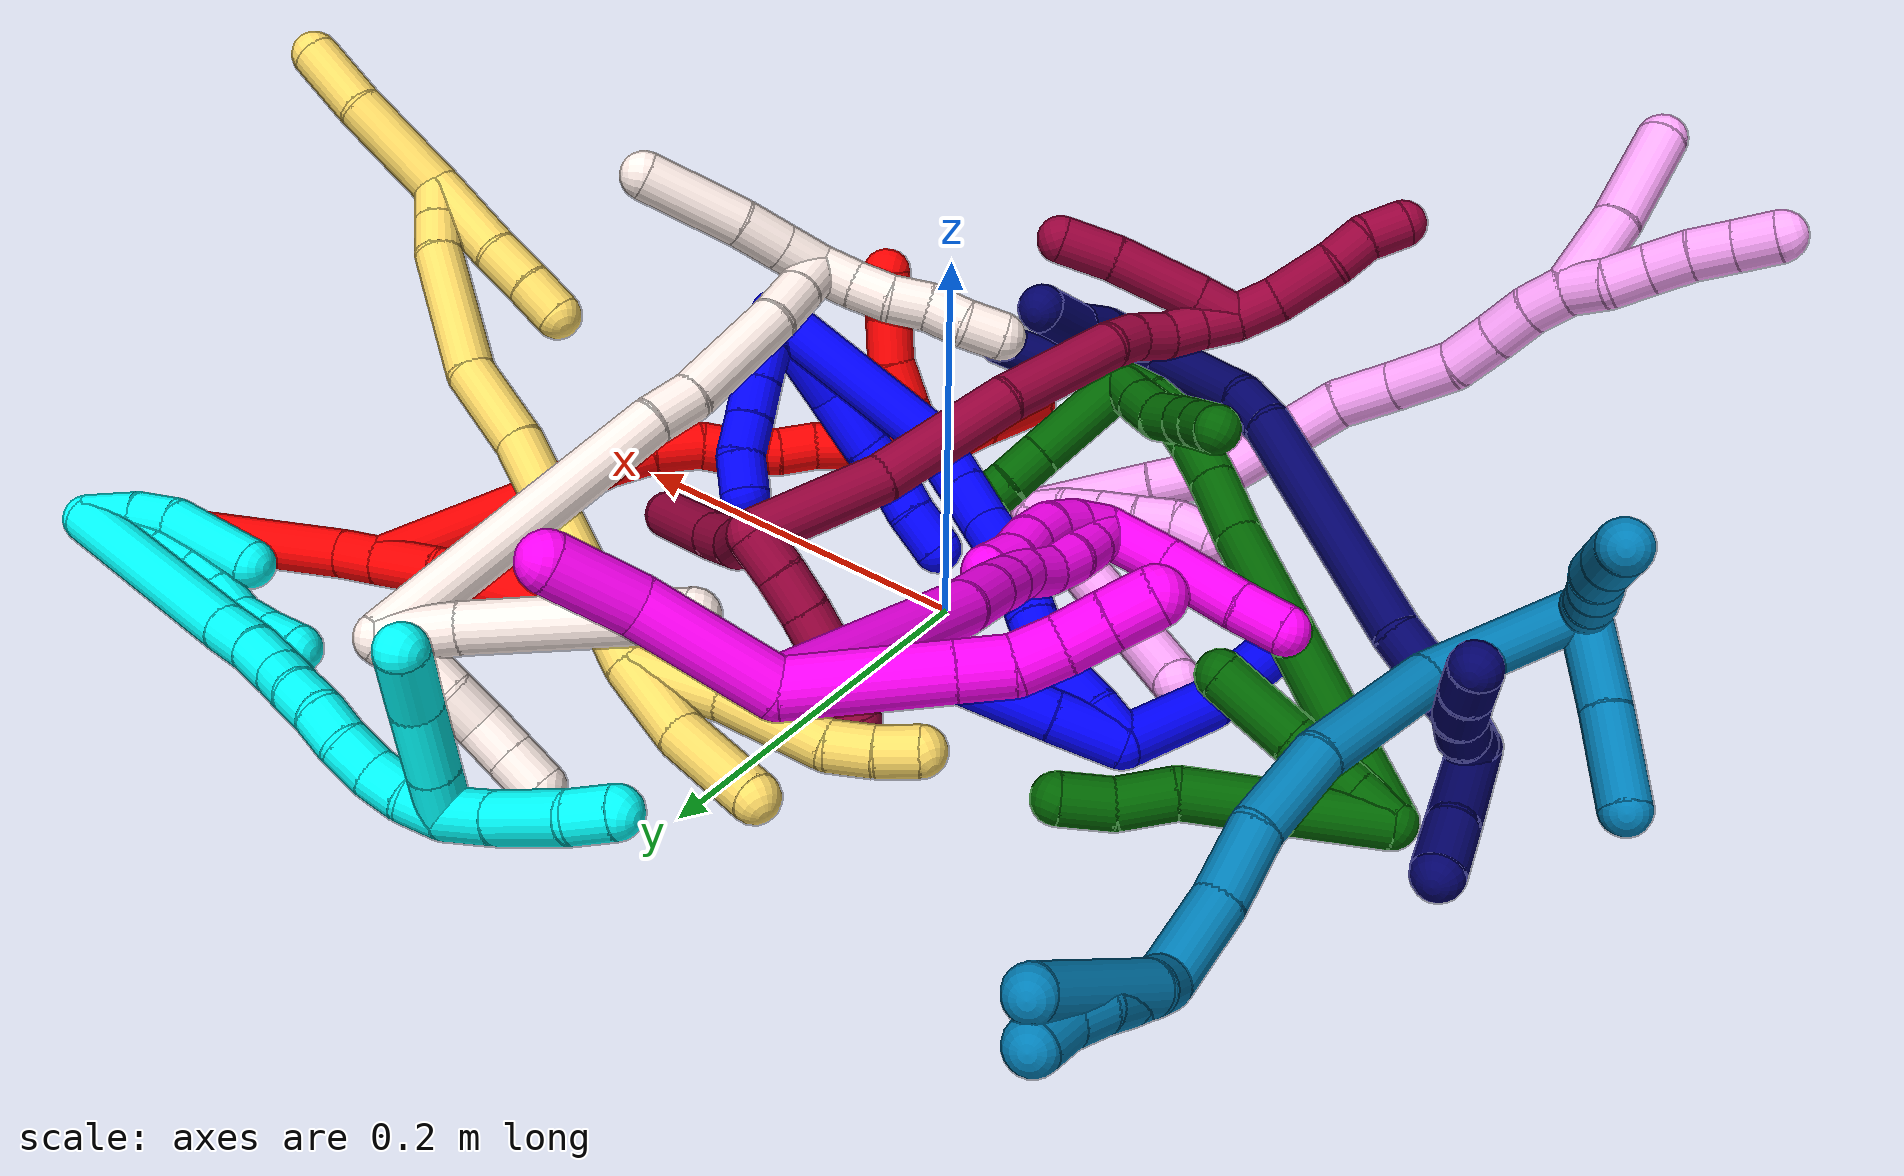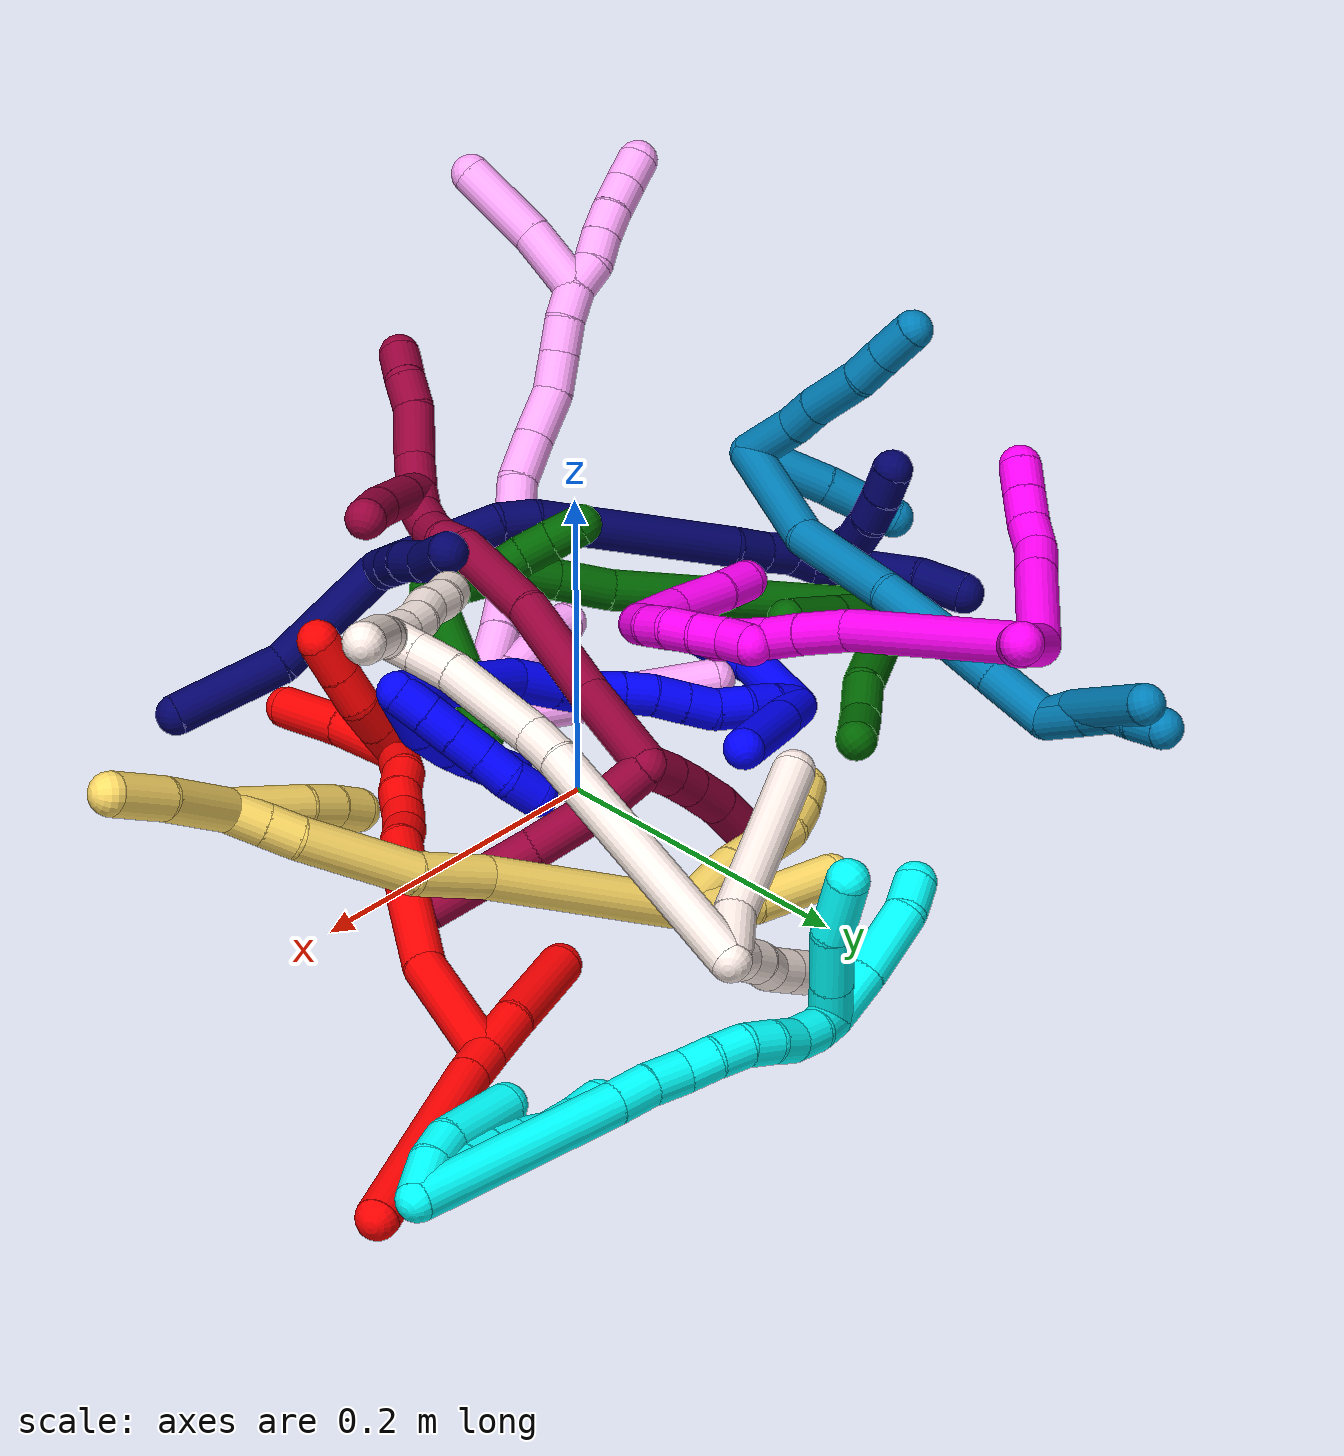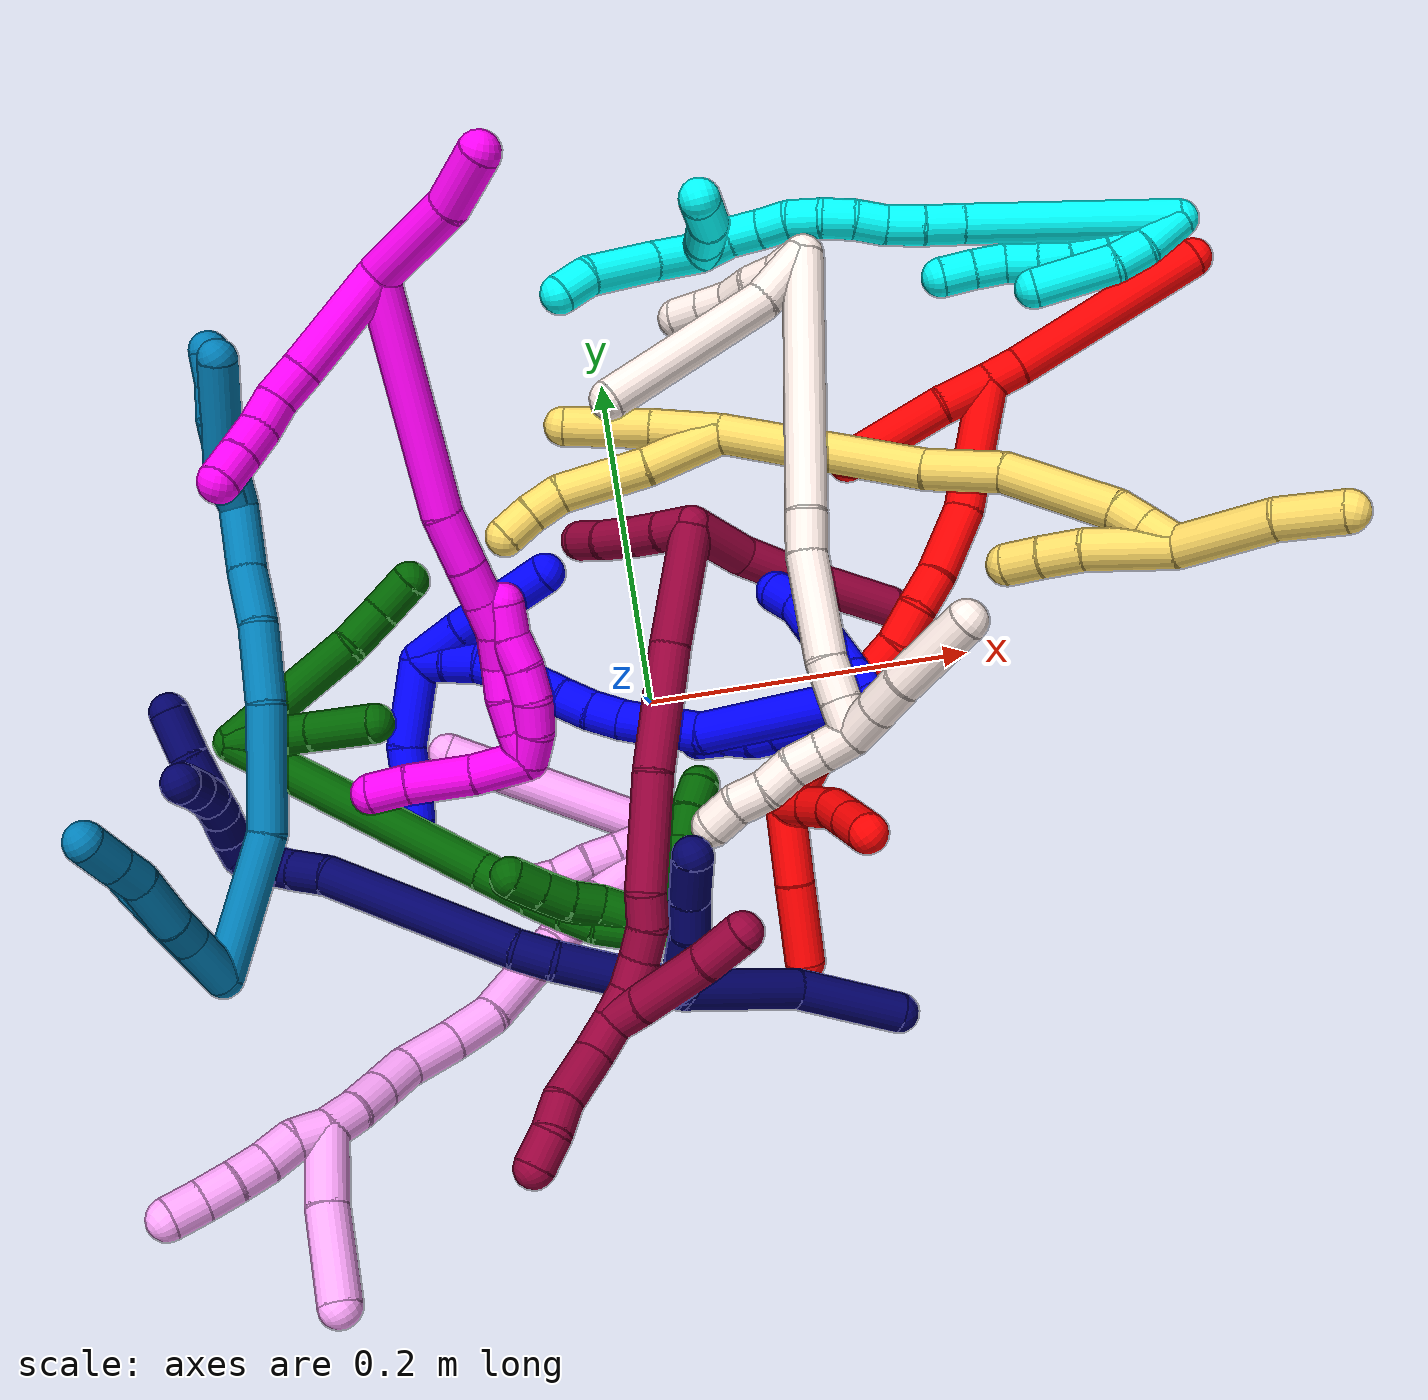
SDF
<sdf version="1.7">
 <world name="default">
  <plugin name="TubeGeneratorPlugin" filename="libtube_generator_plugin.so"/>
  <model name="photoneo_s_sensor">
   <static>1</static>
   <pose>0 0 2 1.57079 1.57079 3.14159</pose>
   <link name="link">
    <inertial><mass>0.1</mass></inertial>
    <sensor name="sensor" type="depth">
     <update_rate>30</update_rate>
     <camera>
      <horizontal_fov>1.22</horizontal_fov>
      <image><width>1920</width><height>1200</height><format>B8G8R8</format></image>
      <clip><near>0.1</near><far>4</far></clip>
      <depth_camera><output>points</output></depth_camera>
     </camera>
     <plugin name="camera_plugin" filename="libgazebo_ros_depth_camera.so">
      <baseline>0.2</baseline>
      <alwaysOn>1</alwaysOn>
      <updateRate>0.0</updateRate>
      <cameraName>camera_ir</cameraName>
      <imageTopicName>/camera/color/image_raw</imageTopicName>
      <cameraInfoTopicName>/camera/color/camera_info</cameraInfoTopicName>
      <depthImageTopicName>/camera/depth/image_raw</depthImageTopicName>
      <depthImageCameraInfoTopicName>/camera/depth/camera_info</depthImageCameraInfoTopicName>
      <pointCloudTopicName>/camera/depth/points</pointCloudTopicName>
      <frameName>fr_optical</frameName>
      <pointCloudCutoff>0.1</pointCloudCutoff>
      <pointCloudCutoffMax>2.0</pointCloudCutoffMax>
      <distortionK1>0</distortionK1>
      <distortionK2>0</distortionK2>
      <distortionK3>0</distortionK3>
      <distortionT1>0</distortionT1>
      <distortionT2>0</distortionT2>
      <CxPrime>0</CxPrime>
      <Cx>0</Cx>
      <Cy>0</Cy>
      <focalLength>0</focalLength>
      <hackBaseline>0</hackBaseline>
     </plugin>
    </sensor>
   </link>
  </model>
  <gravity>0 0 -9.8</gravity>
  <magnetic_field>6e-06 2.3e-05 -4.2e-05</magnetic_field>
  <atmosphere type="adiabatic"/>
  <physics name="default_physics" default="0" type="ode">
   <max_step_size>0.003</max_step_size>
   <real_time_factor>1</real_time_factor>
   <real_time_update_rate>1000</real_time_update_rate>
   <max_contacts>10000</max_contacts>
   <ode>
    <solver>
     <type>quick</type>
     <iters>100</iters>
     <sor>1.3</sor>
     <use_dynamic_moi_rescaling>0</use_dynamic_moi_rescaling>
    </solver>
    <constraints>
     <contact_max_correcting_vel>0</contact_max_correcting_vel>
     <contact_surface_layer>0.001</contact_surface_layer>
     <cfm>0</cfm>
     <erp>0.2</erp>
    </constraints>
   </ode>
  </physics>
  <scene><ambient>0.4 0.4 0.4 1</ambient><background>0.7 0.7 0.7 1</background><shadows>0</shadows></scene>
  <audio><device>default</device></audio>
  <spherical_coordinates>
   <surface_model>EARTH_WGS84</surface_model>
   <latitude_deg>0</latitude_deg>
   <longitude_deg>0</longitude_deg>
   <elevation>0</elevation>
   <heading_deg>0</heading_deg>
  </spherical_coordinates>
  <model name="bin">
   <static>1</static>
   <link name="bottom">
    <collision name="collision-bottom">
     <pose>0 0 -0.01 0 -0 0</pose>
     <geometry><box><size>0.8 0.6 0.02</size></box></geometry>
     <surface>
      <friction><ode><mu>100</mu><mu2>100</mu2></ode></friction>
      <contact><collide_bitmask>65535</collide_bitmask></contact>
     </surface>
    </collision>
   </link>
   <link name="west_wall">
    <collision name="collision-west_wall">
     <pose>-0.41 0 0.1 0 -0 0</pose>
     <geometry><box><size>0.02 0.6 0.2</size></box></geometry>
     <surface>
      <friction><ode><mu>100</mu><mu2>100</mu2></ode></friction>
      <contact><collide_bitmask>65535</collide_bitmask></contact>
     </surface>
    </collision>
   </link>
   <link name="east_wall">
    <collision name="collision-east_wall">
     <pose>0.41 0 0.1 0 -0 0</pose>
     <geometry><box><size>0.02 0.6 0.2</size></box></geometry>
     <surface>
      <friction><ode><mu>100</mu><mu2>100</mu2></ode></friction>
      <contact><collide_bitmask>65535</collide_bitmask></contact>
     </surface>
    </collision>
   </link>
   <link name="south_wall">
    <collision name="collision-south_wall">
     <pose>0 -0.31 0.1 0 -0 0</pose>
     <geometry><box><size>0.8 0.02 0.2</size></box></geometry>
     <surface>
      <friction><ode><mu>100</mu><mu2>100</mu2></ode></friction>
      <contact><collide_bitmask>65535</collide_bitmask></contact>
     </surface>
    </collision>
   </link>
   <link name="north_wall">
    <collision name="collision-north_wall">
     <pose>0 0.31 0.1 0 -0 0</pose>
     <geometry><box><size>0.8 0.02 0.2</size></box></geometry>
     <surface>
      <friction><ode><mu>100</mu><mu2>100</mu2></ode></friction>
      <contact><collide_bitmask>65535</collide_bitmask></contact>
     </surface>
    </collision>
   </link>
  </model>
  <model name="1">
   <static>0</static>
   <link name="1">
    <collision name="collision-cylinder-e_1_2_8">
     <pose>-0.008136 -0.023651 0.007542 1.26211 -0.316727 -0.232346</pose>
     <geometry><cylinder><radius>0.0125</radius><length>0.052247</length></cylinder></geometry>
     <surface>
      <friction><ode><mu>1.16</mu><mu2>1.16</mu2><slip1>0</slip1><slip2>0</slip2></ode></friction>
      <contact><ode><kp>1e+06</kp><kd>1</kd><max_vel>0</max_vel><min_depth>0.001</min_depth></ode></contact>
     </surface>
    </collision>
    <visual name="visual-cylinder-e_1_2_8">
     <pose>-0.008136 -0.023651 0.007542 1.26211 -0.316727 -0.232346</pose>
     <geometry><cylinder><radius>0.0125</radius><length>0.052247</length></cylinder></geometry>
     <material><ambient>0 0 1 1</ambient></material>
    </visual>
    <collision name="collision-cylinder-e_2_8_9">
     <pose>-0.025521 -0.060261 0.019633 1.23315 -0.592637 -0.426204</pose>
     <geometry><cylinder><radius>0.0125</radius><length>0.033116</length></cylinder></geometry>
     <surface>
      <friction><ode><mu>1.16</mu><mu2>1.16</mu2><slip1>0</slip1><slip2>0</slip2></ode></friction>
      <contact><ode><kp>1e+06</kp><kd>1</kd><max_vel>0</max_vel><min_depth>0.001</min_depth></ode></contact>
     </surface>
    </collision>
    <visual name="visual-cylinder-e_2_8_9">
     <pose>-0.025521 -0.060261 0.019633 1.23315 -0.592637 -0.426204</pose>
     <geometry><cylinder><radius>0.0125</radius><length>0.033116</length></cylinder></geometry>
     <material><ambient>0 0 1 1</ambient></material>
    </visual>
    <collision name="collision-cylinder-e_3_9_10">
     <pose>-0.040948 -0.081101 0.027763 1.14443 -0.619876 -0.40685</pose>
     <geometry><cylinder><radius>0.0125</radius><length>0.02127</length></cylinder></geometry>
     <surface>
      <friction><ode><mu>1.16</mu><mu2>1.16</mu2><slip1>0</slip1><slip2>0</slip2></ode></friction>
      <contact><ode><kp>1e+06</kp><kd>1</kd><max_vel>0</max_vel><min_depth>0.001</min_depth></ode></contact>
     </surface>
    </collision>
    <visual name="visual-cylinder-e_3_9_10">
     <pose>-0.040948 -0.081101 0.027763 1.14443 -0.619876 -0.40685</pose>
     <geometry><cylinder><radius>0.0125</radius><length>0.02127</length></cylinder></geometry>
     <material><ambient>0 0 1 1</ambient></material>
    </visual>
    <collision name="collision-cylinder-e_4_10_11">
     <pose>-0.054807 -0.095396 0.033036 1.31264 -0.858441 -0.677828</pose>
     <geometry><cylinder><radius>0.0125</radius><length>0.020298</length></cylinder></geometry>
     <surface>
      <friction><ode><mu>1.16</mu><mu2>1.16</mu2><slip1>0</slip1><slip2>0</slip2></ode></friction>
      <contact><ode><kp>1e+06</kp><kd>1</kd><max_vel>0</max_vel><min_depth>0.001</min_depth></ode></contact>
     </surface>
    </collision>
    <visual name="visual-cylinder-e_4_10_11">
     <pose>-0.054807 -0.095396 0.033036 1.31264 -0.858441 -0.677828</pose>
     <geometry><cylinder><radius>0.0125</radius><length>0.020298</length></cylinder></geometry>
     <material><ambient>0 0 1 1</ambient></material>
    </visual>
    <collision name="collision-cylinder-e_5_11_6">
     <pose>-0.070186 -0.109712 0.038097 1.16797 -0.730721 -0.495241</pose>
     <geometry><cylinder><radius>0.0125</radius><length>0.023069</length></cylinder></geometry>
     <surface>
      <friction><ode><mu>1.16</mu><mu2>1.16</mu2><slip1>0</slip1><slip2>0</slip2></ode></friction>
      <contact><ode><kp>1e+06</kp><kd>1</kd><max_vel>0</max_vel><min_depth>0.001</min_depth></ode></contact>
     </surface>
    </collision>
    <visual name="visual-cylinder-e_5_11_6">
     <pose>-0.070186 -0.109712 0.038097 1.16797 -0.730721 -0.495241</pose>
     <geometry><cylinder><radius>0.0125</radius><length>0.023069</length></cylinder></geometry>
     <material><ambient>0 0 1 1</ambient></material>
    </visual>
    <collision name="collision-cylinder-e_1_2_12">
     <pose>-0.007572 -0.004029 -0.005141 2.47689 -0.859002 -1.85001</pose>
     <geometry><cylinder><radius>0.0125</radius><length>0.02</length></cylinder></geometry>
     <surface>
      <friction><ode><mu>1.16</mu><mu2>1.16</mu2><slip1>0</slip1><slip2>0</slip2></ode></friction>
      <contact><ode><kp>1e+06</kp><kd>1</kd><max_vel>0</max_vel><min_depth>0.001</min_depth></ode></contact>
     </surface>
    </collision>
    <visual name="visual-cylinder-e_1_2_12">
     <pose>-0.007572 -0.004029 -0.005141 2.47689 -0.859002 -1.85001</pose>
     <geometry><cylinder><radius>0.0125</radius><length>0.02</length></cylinder></geometry>
     <material><ambient>0 0 1 1</ambient></material>
    </visual>
    <collision name="collision-cylinder-e_2_12_13">
     <pose>-0.022588 -0.012391 -0.015364 2.4355 -0.839596 -1.76129</pose>
     <geometry><cylinder><radius>0.0125</radius><length>0.02</length></cylinder></geometry>
     <surface>
      <friction><ode><mu>1.16</mu><mu2>1.16</mu2><slip1>0</slip1><slip2>0</slip2></ode></friction>
      <contact><ode><kp>1e+06</kp><kd>1</kd><max_vel>0</max_vel><min_depth>0.001</min_depth></ode></contact>
     </surface>
    </collision>
    <visual name="visual-cylinder-e_2_12_13">
     <pose>-0.022588 -0.012391 -0.015364 2.4355 -0.839596 -1.76129</pose>
     <geometry><cylinder><radius>0.0125</radius><length>0.02</length></cylinder></geometry>
     <material><ambient>0 0 1 1</ambient></material>
    </visual>
    <collision name="collision-cylinder-e_3_13_14">
     <pose>-0.037583 -0.021031 -0.025386 2.42462 -0.855928 -1.76632</pose>
     <geometry><cylinder><radius>0.0125</radius><length>0.02</length></cylinder></geometry>
     <surface>
      <friction><ode><mu>1.16</mu><mu2>1.16</mu2><slip1>0</slip1><slip2>0</slip2></ode></friction>
      <contact><ode><kp>1e+06</kp><kd>1</kd><max_vel>0</max_vel><min_depth>0.001</min_depth></ode></contact>
     </surface>
    </collision>
    <visual name="visual-cylinder-e_3_13_14">
     <pose>-0.037583 -0.021031 -0.025386 2.42462 -0.855928 -1.76632</pose>
     <geometry><cylinder><radius>0.0125</radius><length>0.02</length></cylinder></geometry>
     <material><ambient>0 0 1 1</ambient></material>
    </visual>
    <collision name="collision-cylinder-e_4_14_15">
     <pose>-0.052514 -0.029818 -0.035376 2.41593 -0.829948 -1.71907</pose>
     <geometry><cylinder><radius>0.0125</radius><length>0.02</length></cylinder></geometry>
     <surface>
      <friction><ode><mu>1.16</mu><mu2>1.16</mu2><slip1>0</slip1><slip2>0</slip2></ode></friction>
      <contact><ode><kp>1e+06</kp><kd>1</kd><max_vel>0</max_vel><min_depth>0.001</min_depth></ode></contact>
     </surface>
    </collision>
    <visual name="visual-cylinder-e_4_14_15">
     <pose>-0.052514 -0.029818 -0.035376 2.41593 -0.829948 -1.71907</pose>
     <geometry><cylinder><radius>0.0125</radius><length>0.02</length></cylinder></geometry>
     <material><ambient>0 0 1 1</ambient></material>
    </visual>
    <collision name="collision-cylinder-e_5_15_5">
     <pose>-0.067924 -0.03987 -0.042532 1.93233 -0.932542 -1.25904</pose>
     <geometry><cylinder><radius>0.0125</radius><length>0.02</length></cylinder></geometry>
     <surface>
      <friction><ode><mu>1.16</mu><mu2>1.16</mu2><slip1>0</slip1><slip2>0</slip2></ode></friction>
      <contact><ode><kp>1e+06</kp><kd>1</kd><max_vel>0</max_vel><min_depth>0.001</min_depth></ode></contact>
     </surface>
    </collision>
    <visual name="visual-cylinder-e_5_15_5">
     <pose>-0.067924 -0.03987 -0.042532 1.93233 -0.932542 -1.25904</pose>
     <geometry><cylinder><radius>0.0125</radius><length>0.02</length></cylinder></geometry>
     <material><ambient>0 0 1 1</ambient></material>
    </visual>
    <collision name="collision-cylinder-e_1_2_16">
     <pose>-0.037888 -0.024866 0.026284 0.757674 -0.808416 -0.337319</pose>
     <geometry><cylinder><radius>0.0125</radius><length>0.104779</length></cylinder></geometry>
     <surface>
      <friction><ode><mu>1.16</mu><mu2>1.16</mu2><slip1>0</slip1><slip2>0</slip2></ode></friction>
      <contact><ode><kp>1e+06</kp><kd>1</kd><max_vel>0</max_vel><min_depth>0.001</min_depth></ode></contact>
     </surface>
    </collision>
    <visual name="visual-cylinder-e_1_2_16">
     <pose>-0.037888 -0.024866 0.026284 0.757674 -0.808416 -0.337319</pose>
     <geometry><cylinder><radius>0.0125</radius><length>0.104779</length></cylinder></geometry>
     <material><ambient>0 0 1 1</ambient></material>
    </visual>
    <collision name="collision-cylinder-e_2_16_17">
     <pose>-0.088572 -0.056948 0.05531 1.20774 -1.02797 -0.742812</pose>
     <geometry><cylinder><radius>0.0125</radius><length>0.02989</length></cylinder></geometry>
     <surface>
      <friction><ode><mu>1.16</mu><mu2>1.16</mu2><slip1>0</slip1><slip2>0</slip2></ode></friction>
      <contact><ode><kp>1e+06</kp><kd>1</kd><max_vel>0</max_vel><min_depth>0.001</min_depth></ode></contact>
     </surface>
    </collision>
    <visual name="visual-cylinder-e_2_16_17">
     <pose>-0.088572 -0.056948 0.05531 1.20774 -1.02797 -0.742812</pose>
     <geometry><cylinder><radius>0.0125</radius><length>0.02989</length></cylinder></geometry>
     <material><ambient>0 0 1 1</ambient></material>
    </visual>
    <collision name="collision-cylinder-e_3_17_18">
     <pose>-0.11191 -0.069867 0.060112 1.22409 -1.04886 -0.771439</pose>
     <geometry><cylinder><radius>0.0125</radius><length>0.024319</length></cylinder></geometry>
     <surface>
      <friction><ode><mu>1.16</mu><mu2>1.16</mu2><slip1>0</slip1><slip2>0</slip2></ode></friction>
      <contact><ode><kp>1e+06</kp><kd>1</kd><max_vel>0</max_vel><min_depth>0.001</min_depth></ode></contact>
     </surface>
    </collision>
    <visual name="visual-cylinder-e_3_17_18">
     <pose>-0.11191 -0.069867 0.060112 1.22409 -1.04886 -0.771439</pose>
     <geometry><cylinder><radius>0.0125</radius><length>0.024319</length></cylinder></geometry>
     <material><ambient>0 0 1 1</ambient></material>
    </visual>
    <collision name="collision-cylinder-e_4_18_19">
     <pose>-0.132611 -0.077598 0.063699 0.925771 -1.32582 -0.743095</pose>
     <geometry><cylinder><radius>0.0125</radius><length>0.020948</length></cylinder></geometry>
     <surface>
      <friction><ode><mu>1.16</mu><mu2>1.16</mu2><slip1>0</slip1><slip2>0</slip2></ode></friction>
      <contact><ode><kp>1e+06</kp><kd>1</kd><max_vel>0</max_vel><min_depth>0.001</min_depth></ode></contact>
     </surface>
    </collision>
    <visual name="visual-cylinder-e_4_18_19">
     <pose>-0.132611 -0.077598 0.063699 0.925771 -1.32582 -0.743095</pose>
     <geometry><cylinder><radius>0.0125</radius><length>0.020948</length></cylinder></geometry>
     <material><ambient>0 0 1 1</ambient></material>
    </visual>
    <collision name="collision-cylinder-e_5_19_20">
     <pose>-0.152545 -0.081866 0.065331 1.52415 -1.34537 -1.30015</pose>
     <geometry><cylinder><radius>0.0125</radius><length>0.020053</length></cylinder></geometry>
     <surface>
      <friction><ode><mu>1.16</mu><mu2>1.16</mu2><slip1>0</slip1><slip2>0</slip2></ode></friction>
      <contact><ode><kp>1e+06</kp><kd>1</kd><max_vel>0</max_vel><min_depth>0.001</min_depth></ode></contact>
     </surface>
    </collision>
    <visual name="visual-cylinder-e_5_19_20">
     <pose>-0.152545 -0.081866 0.065331 1.52415 -1.34537 -1.30015</pose>
     <geometry><cylinder><radius>0.0125</radius><length>0.020053</length></cylinder></geometry>
     <material><ambient>0 0 1 1</ambient></material>
    </visual>
    <collision name="collision-cylinder-e_6_20_21">
     <pose>-0.17168 -0.087591 0.064895 1.72449 -1.21043 -1.35829</pose>
     <geometry><cylinder><radius>0.0125</radius><length>0.02001</length></cylinder></geometry>
     <surface>
      <friction><ode><mu>1.16</mu><mu2>1.16</mu2><slip1>0</slip1><slip2>0</slip2></ode></friction>
      <contact><ode><kp>1e+06</kp><kd>1</kd><max_vel>0</max_vel><min_depth>0.001</min_depth></ode></contact>
     </surface>
    </collision>
    <visual name="visual-cylinder-e_6_20_21">
     <pose>-0.17168 -0.087591 0.064895 1.72449 -1.21043 -1.35829</pose>
     <geometry><cylinder><radius>0.0125</radius><length>0.02001</length></cylinder></geometry>
     <material><ambient>0 0 1 1</ambient></material>
    </visual>
    <collision name="collision-cylinder-e_7_21_22">
     <pose>-0.190441 -0.094461 0.063881 1.7101 -1.22212 -1.35625</pose>
     <geometry><cylinder><radius>0.0125</radius><length>0.020002</length></cylinder></geometry>
     <surface>
      <friction><ode><mu>1.16</mu><mu2>1.16</mu2><slip1>0</slip1><slip2>0</slip2></ode></friction>
      <contact><ode><kp>1e+06</kp><kd>1</kd><max_vel>0</max_vel><min_depth>0.001</min_depth></ode></contact>
     </surface>
    </collision>
    <visual name="visual-cylinder-e_7_21_22">
     <pose>-0.190441 -0.094461 0.063881 1.7101 -1.22212 -1.35625</pose>
     <geometry><cylinder><radius>0.0125</radius><length>0.020002</length></cylinder></geometry>
     <material><ambient>0 0 1 1</ambient></material>
    </visual>
    <collision name="collision-cylinder-e_8_22_23">
     <pose>-0.209551 -0.099327 0.065278 0.669638 -1.32971 -0.532526</pose>
     <geometry><cylinder><radius>0.0125</radius><length>0.02</length></cylinder></geometry>
     <surface>
      <friction><ode><mu>1.16</mu><mu2>1.16</mu2><slip1>0</slip1><slip2>0</slip2></ode></friction>
      <contact><ode><kp>1e+06</kp><kd>1</kd><max_vel>0</max_vel><min_depth>0.001</min_depth></ode></contact>
     </surface>
    </collision>
    <visual name="visual-cylinder-e_8_22_23">
     <pose>-0.209551 -0.099327 0.065278 0.669638 -1.32971 -0.532526</pose>
     <geometry><cylinder><radius>0.0125</radius><length>0.02</length></cylinder></geometry>
     <material><ambient>0 0 1 1</ambient></material>
    </visual>
    <collision name="collision-cylinder-e_9_23_24">
     <pose>-0.228083 -0.103973 0.07064 0.736432 -1.08028 -0.454683</pose>
     <geometry><cylinder><radius>0.0125</radius><length>0.02</length></cylinder></geometry>
     <surface>
      <friction><ode><mu>1.16</mu><mu2>1.16</mu2><slip1>0</slip1><slip2>0</slip2></ode></friction>
      <contact><ode><kp>1e+06</kp><kd>1</kd><max_vel>0</max_vel><min_depth>0.001</min_depth></ode></contact>
     </surface>
    </collision>
    <visual name="visual-cylinder-e_9_23_24">
     <pose>-0.228083 -0.103973 0.07064 0.736432 -1.08028 -0.454683</pose>
     <geometry><cylinder><radius>0.0125</radius><length>0.02</length></cylinder></geometry>
     <material><ambient>0 0 1 1</ambient></material>
    </visual>
    <collision name="collision-cylinder-e_10_24_1">
     <pose>-0.245258 -0.111835 0.076984 1.02494 -0.988875 -0.588966</pose>
     <geometry><cylinder><radius>0.0125</radius><length>0.02</length></cylinder></geometry>
     <surface>
      <friction><ode><mu>1.16</mu><mu2>1.16</mu2><slip1>0</slip1><slip2>0</slip2></ode></friction>
      <contact><ode><kp>1e+06</kp><kd>1</kd><max_vel>0</max_vel><min_depth>0.001</min_depth></ode></contact>
     </surface>
    </collision>
    <visual name="visual-cylinder-e_10_24_1">
     <pose>-0.245258 -0.111835 0.076984 1.02494 -0.988875 -0.588966</pose>
     <geometry><cylinder><radius>0.0125</radius><length>0.02</length></cylinder></geometry>
     <material><ambient>0 0 1 1</ambient></material>
    </visual>
    <collision name="collision-cylinder-e_1_1_25">
     <pose>-0.24491 -0.122779 0.104367 0.249347 0.331123 0.041875</pose>
     <geometry><cylinder><radius>0.0125</radius><length>0.053534</length></cylinder></geometry>
     <surface>
      <friction><ode><mu>1.16</mu><mu2>1.16</mu2><slip1>0</slip1><slip2>0</slip2></ode></friction>
      <contact><ode><kp>1e+06</kp><kd>1</kd><max_vel>0</max_vel><min_depth>0.001</min_depth></ode></contact>
     </surface>
    </collision>
    <visual name="visual-cylinder-e_1_1_25">
     <pose>-0.24491 -0.122779 0.104367 0.249347 0.331123 0.041875</pose>
     <geometry><cylinder><radius>0.0125</radius><length>0.053534</length></cylinder></geometry>
     <material><ambient>0 0 1 1</ambient></material>
    </visual>
    <collision name="collision-cylinder-e_2_25_26">
     <pose>-0.229835 -0.131386 0.137578 0.265572 0.616329 0.084982</pose>
     <geometry><cylinder><radius>0.0125</radius><length>0.022049</length></cylinder></geometry>
     <surface>
      <friction><ode><mu>1.16</mu><mu2>1.16</mu2><slip1>0</slip1><slip2>0</slip2></ode></friction>
      <contact><ode><kp>1e+06</kp><kd>1</kd><max_vel>0</max_vel><min_depth>0.001</min_depth></ode></contact>
     </surface>
    </collision>
    <visual name="visual-cylinder-e_2_25_26">
     <pose>-0.229835 -0.131386 0.137578 0.265572 0.616329 0.084982</pose>
     <geometry><cylinder><radius>0.0125</radius><length>0.022049</length></cylinder></geometry>
     <material><ambient>0 0 1 1</ambient></material>
    </visual>
    <collision name="collision-cylinder-e_3_26_4">
     <pose>-0.216747 -0.1362 0.156155 0.242876 0.582445 0.073128</pose>
     <geometry><cylinder><radius>0.0125</radius><length>0.024417</length></cylinder></geometry>
     <surface>
      <friction><ode><mu>1.16</mu><mu2>1.16</mu2><slip1>0</slip1><slip2>0</slip2></ode></friction>
      <contact><ode><kp>1e+06</kp><kd>1</kd><max_vel>0</max_vel><min_depth>0.001</min_depth></ode></contact>
     </surface>
    </collision>
    <visual name="visual-cylinder-e_3_26_4">
     <pose>-0.216747 -0.1362 0.156155 0.242876 0.582445 0.073128</pose>
     <geometry><cylinder><radius>0.0125</radius><length>0.024417</length></cylinder></geometry>
     <material><ambient>0 0 1 1</ambient></material>
    </visual>
    <collision name="collision-cylinder-e_1_1_27">
     <pose>-0.245918 -0.108276 0.066611 -2.58355 0.458382 -1.36678</pose>
     <geometry><cylinder><radius>0.0125</radius><length>0.034773</length></cylinder></geometry>
     <surface>
      <friction><ode><mu>1.16</mu><mu2>1.16</mu2><slip1>0</slip1><slip2>0</slip2></ode></friction>
      <contact><ode><kp>1e+06</kp><kd>1</kd><max_vel>0</max_vel><min_depth>0.001</min_depth></ode></contact>
     </surface>
    </collision>
    <visual name="visual-cylinder-e_1_1_27">
     <pose>-0.245918 -0.108276 0.066611 -2.58355 0.458382 -1.36678</pose>
     <geometry><cylinder><radius>0.0125</radius><length>0.034773</length></cylinder></geometry>
     <material><ambient>0 0 1 1</ambient></material>
    </visual>
    <collision name="collision-cylinder-e_2_27_3">
     <pose>-0.222243 -0.085251 0.029092 -2.59536 0.51212 -1.50325</pose>
     <geometry><cylinder><radius>0.0125</radius><length>0.065227</length></cylinder></geometry>
     <surface>
      <friction><ode><mu>1.16</mu><mu2>1.16</mu2><slip1>0</slip1><slip2>0</slip2></ode></friction>
      <contact><ode><kp>1e+06</kp><kd>1</kd><max_vel>0</max_vel><min_depth>0.001</min_depth></ode></contact>
     </surface>
    </collision>
    <visual name="visual-cylinder-e_2_27_3">
     <pose>-0.222243 -0.085251 0.029092 -2.59536 0.51212 -1.50325</pose>
     <geometry><cylinder><radius>0.0125</radius><length>0.065227</length></cylinder></geometry>
     <material><ambient>0 0 1 1</ambient></material>
    </visual>
    <collision name="collision-sphere-3">
     <pose>-0.206262 -0.070483 0.004799 0 -0 0</pose>
     <geometry><sphere><radius>0.0125</radius></sphere></geometry>
     <surface>
      <friction><ode><mu>1.16</mu><mu2>1.16</mu2><slip1>0</slip1><slip2>0</slip2></ode></friction>
      <contact><ode><kp>1e+06</kp><kd>1</kd><max_vel>0</max_vel><min_depth>0.001</min_depth></ode></contact>
     </surface>
    </collision>
    <visual name="visual-sphere-3">
     <pose>-0.206262 -0.070483 0.004799 0 -0 0</pose>
     <geometry><sphere><radius>0.0125</radius></sphere></geometry>
     <material><ambient>0 0 1 1</ambient></material>
    </visual>
    <collision name="collision-sphere-27">
     <pose>-0.238225 -0.10002 0.053384 0 -0 0</pose>
     <geometry><sphere><radius>0.0125</radius></sphere></geometry>
     <surface>
      <friction><ode><mu>1.16</mu><mu2>1.16</mu2><slip1>0</slip1><slip2>0</slip2></ode></friction>
      <contact><ode><kp>1e+06</kp><kd>1</kd><max_vel>0</max_vel><min_depth>0.001</min_depth></ode></contact>
     </surface>
    </collision>
    <visual name="visual-sphere-27">
     <pose>-0.238225 -0.10002 0.053384 0 -0 0</pose>
     <geometry><sphere><radius>0.0125</radius></sphere></geometry>
     <material><ambient>0 0 1 1</ambient></material>
    </visual>
    <collision name="collision-sphere-4">
     <pose>-0.210031 -0.138652 0.166051 0 -0 0</pose>
     <geometry><sphere><radius>0.0125</radius></sphere></geometry>
     <surface>
      <friction><ode><mu>1.16</mu><mu2>1.16</mu2><slip1>0</slip1><slip2>0</slip2></ode></friction>
      <contact><ode><kp>1e+06</kp><kd>1</kd><max_vel>0</max_vel><min_depth>0.001</min_depth></ode></contact>
     </surface>
    </collision>
    <visual name="visual-sphere-4">
     <pose>-0.210031 -0.138652 0.166051 0 -0 0</pose>
     <geometry><sphere><radius>0.0125</radius></sphere></geometry>
     <material><ambient>0 0 1 1</ambient></material>
    </visual>
    <collision name="collision-sphere-26">
     <pose>-0.223463 -0.133748 0.146259 0 -0 0</pose>
     <geometry><sphere><radius>0.0125</radius></sphere></geometry>
     <surface>
      <friction><ode><mu>1.16</mu><mu2>1.16</mu2><slip1>0</slip1><slip2>0</slip2></ode></friction>
      <contact><ode><kp>1e+06</kp><kd>1</kd><max_vel>0</max_vel><min_depth>0.001</min_depth></ode></contact>
     </surface>
    </collision>
    <visual name="visual-sphere-26">
     <pose>-0.223463 -0.133748 0.146259 0 -0 0</pose>
     <geometry><sphere><radius>0.0125</radius></sphere></geometry>
     <material><ambient>0 0 1 1</ambient></material>
    </visual>
    <collision name="collision-sphere-25">
     <pose>-0.236208 -0.129025 0.128897 0 -0 0</pose>
     <geometry><sphere><radius>0.0125</radius></sphere></geometry>
     <surface>
      <friction><ode><mu>1.16</mu><mu2>1.16</mu2><slip1>0</slip1><slip2>0</slip2></ode></friction>
      <contact><ode><kp>1e+06</kp><kd>1</kd><max_vel>0</max_vel><min_depth>0.001</min_depth></ode></contact>
     </surface>
    </collision>
    <visual name="visual-sphere-25">
     <pose>-0.236208 -0.129025 0.128897 0 -0 0</pose>
     <geometry><sphere><radius>0.0125</radius></sphere></geometry>
     <material><ambient>0 0 1 1</ambient></material>
    </visual>
    <collision name="collision-sphere-1">
     <pose>-0.253612 -0.116532 0.079837 0 -0 0</pose>
     <geometry><sphere><radius>0.0125</radius></sphere></geometry>
     <surface>
      <friction><ode><mu>1.16</mu><mu2>1.16</mu2><slip1>0</slip1><slip2>0</slip2></ode></friction>
      <contact><ode><kp>1e+06</kp><kd>1</kd><max_vel>0</max_vel><min_depth>0.001</min_depth></ode></contact>
     </surface>
    </collision>
    <visual name="visual-sphere-1">
     <pose>-0.253612 -0.116532 0.079837 0 -0 0</pose>
     <geometry><sphere><radius>0.0125</radius></sphere></geometry>
     <material><ambient>0 0 1 1</ambient></material>
    </visual>
    <collision name="collision-sphere-24">
     <pose>-0.236904 -0.107137 0.07413 0 -0 0</pose>
     <geometry><sphere><radius>0.0125</radius></sphere></geometry>
     <surface>
      <friction><ode><mu>1.16</mu><mu2>1.16</mu2><slip1>0</slip1><slip2>0</slip2></ode></friction>
      <contact><ode><kp>1e+06</kp><kd>1</kd><max_vel>0</max_vel><min_depth>0.001</min_depth></ode></contact>
     </surface>
    </collision>
    <visual name="visual-sphere-24">
     <pose>-0.236904 -0.107137 0.07413 0 -0 0</pose>
     <geometry><sphere><radius>0.0125</radius></sphere></geometry>
     <material><ambient>0 0 1 1</ambient></material>
    </visual>
    <collision name="collision-sphere-23">
     <pose>-0.219262 -0.100809 0.06715 0 -0 0</pose>
     <geometry><sphere><radius>0.0125</radius></sphere></geometry>
     <surface>
      <friction><ode><mu>1.16</mu><mu2>1.16</mu2><slip1>0</slip1><slip2>0</slip2></ode></friction>
      <contact><ode><kp>1e+06</kp><kd>1</kd><max_vel>0</max_vel><min_depth>0.001</min_depth></ode></contact>
     </surface>
    </collision>
    <visual name="visual-sphere-23">
     <pose>-0.219262 -0.100809 0.06715 0 -0 0</pose>
     <geometry><sphere><radius>0.0125</radius></sphere></geometry>
     <material><ambient>0 0 1 1</ambient></material>
    </visual>
    <collision name="collision-sphere-22">
     <pose>-0.19984 -0.097845 0.063406 0 -0 0</pose>
     <geometry><sphere><radius>0.0125</radius></sphere></geometry>
     <surface>
      <friction><ode><mu>1.16</mu><mu2>1.16</mu2><slip1>0</slip1><slip2>0</slip2></ode></friction>
      <contact><ode><kp>1e+06</kp><kd>1</kd><max_vel>0</max_vel><min_depth>0.001</min_depth></ode></contact>
     </surface>
    </collision>
    <visual name="visual-sphere-22">
     <pose>-0.19984 -0.097845 0.063406 0 -0 0</pose>
     <geometry><sphere><radius>0.0125</radius></sphere></geometry>
     <material><ambient>0 0 1 1</ambient></material>
    </visual>
    <collision name="collision-sphere-21">
     <pose>-0.181042 -0.091078 0.064355 0 -0 0</pose>
     <geometry><sphere><radius>0.0125</radius></sphere></geometry>
     <surface>
      <friction><ode><mu>1.16</mu><mu2>1.16</mu2><slip1>0</slip1><slip2>0</slip2></ode></friction>
      <contact><ode><kp>1e+06</kp><kd>1</kd><max_vel>0</max_vel><min_depth>0.001</min_depth></ode></contact>
     </surface>
    </collision>
    <visual name="visual-sphere-21">
     <pose>-0.181042 -0.091078 0.064355 0 -0 0</pose>
     <geometry><sphere><radius>0.0125</radius></sphere></geometry>
     <material><ambient>0 0 1 1</ambient></material>
    </visual>
    <collision name="collision-sphere-6">
     <pose>-0.077885 -0.117614 0.041464 0 -0 0</pose>
     <geometry><sphere><radius>0.0125</radius></sphere></geometry>
     <surface>
      <friction><ode><mu>1.16</mu><mu2>1.16</mu2><slip1>0</slip1><slip2>0</slip2></ode></friction>
      <contact><ode><kp>1e+06</kp><kd>1</kd><max_vel>0</max_vel><min_depth>0.001</min_depth></ode></contact>
     </surface>
    </collision>
    <visual name="visual-sphere-6">
     <pose>-0.077885 -0.117614 0.041464 0 -0 0</pose>
     <geometry><sphere><radius>0.0125</radius></sphere></geometry>
     <material><ambient>0 0 1 1</ambient></material>
    </visual>
    <collision name="collision-sphere-11">
     <pose>-0.062488 -0.101809 0.03473 0 -0 0</pose>
     <geometry><sphere><radius>0.0125</radius></sphere></geometry>
     <surface>
      <friction><ode><mu>1.16</mu><mu2>1.16</mu2><slip1>0</slip1><slip2>0</slip2></ode></friction>
      <contact><ode><kp>1e+06</kp><kd>1</kd><max_vel>0</max_vel><min_depth>0.001</min_depth></ode></contact>
     </surface>
    </collision>
    <visual name="visual-sphere-11">
     <pose>-0.062488 -0.101809 0.03473 0 -0 0</pose>
     <geometry><sphere><radius>0.0125</radius></sphere></geometry>
     <material><ambient>0 0 1 1</ambient></material>
    </visual>
    <collision name="collision-sphere-10">
     <pose>-0.047126 -0.088982 0.031342 0 -0 0</pose>
     <geometry><sphere><radius>0.0125</radius></sphere></geometry>
     <surface>
      <friction><ode><mu>1.16</mu><mu2>1.16</mu2><slip1>0</slip1><slip2>0</slip2></ode></friction>
      <contact><ode><kp>1e+06</kp><kd>1</kd><max_vel>0</max_vel><min_depth>0.001</min_depth></ode></contact>
     </surface>
    </collision>
    <visual name="visual-sphere-10">
     <pose>-0.047126 -0.088982 0.031342 0 -0 0</pose>
     <geometry><sphere><radius>0.0125</radius></sphere></geometry>
     <material><ambient>0 0 1 1</ambient></material>
    </visual>
    <collision name="collision-sphere-9">
     <pose>-0.03477 -0.073219 0.024183 0 -0 0</pose>
     <geometry><sphere><radius>0.0125</radius></sphere></geometry>
     <surface>
      <friction><ode><mu>1.16</mu><mu2>1.16</mu2><slip1>0</slip1><slip2>0</slip2></ode></friction>
      <contact><ode><kp>1e+06</kp><kd>1</kd><max_vel>0</max_vel><min_depth>0.001</min_depth></ode></contact>
     </surface>
    </collision>
    <visual name="visual-sphere-9">
     <pose>-0.03477 -0.073219 0.024183 0 -0 0</pose>
     <geometry><sphere><radius>0.0125</radius></sphere></geometry>
     <material><ambient>0 0 1 1</ambient></material>
    </visual>
    <collision name="collision-sphere-2">
     <geometry><sphere><radius>0.0125</radius></sphere></geometry>
     <surface>
      <friction><ode><mu>1.16</mu><mu2>1.16</mu2><slip1>0</slip1><slip2>0</slip2></ode></friction>
      <contact><ode><kp>1e+06</kp><kd>1</kd><max_vel>0</max_vel><min_depth>0.001</min_depth></ode></contact>
     </surface>
    </collision>
    <visual name="visual-sphere-2">
     <geometry><sphere><radius>0.0125</radius></sphere></geometry>
     <material><ambient>0 0 1 1</ambient></material>
    </visual>
    <collision name="collision-sphere-19">
     <pose>-0.142772 -0.079628 0.065226 0 -0 0</pose>
     <geometry><sphere><radius>0.0125</radius></sphere></geometry>
     <surface>
      <friction><ode><mu>1.16</mu><mu2>1.16</mu2><slip1>0</slip1><slip2>0</slip2></ode></friction>
      <contact><ode><kp>1e+06</kp><kd>1</kd><max_vel>0</max_vel><min_depth>0.001</min_depth></ode></contact>
     </surface>
    </collision>
    <visual name="visual-sphere-19">
     <pose>-0.142772 -0.079628 0.065226 0 -0 0</pose>
     <geometry><sphere><radius>0.0125</radius></sphere></geometry>
     <material><ambient>0 0 1 1</ambient></material>
    </visual>
    <collision name="collision-sphere-8">
     <pose>-0.016273 -0.047302 0.015083 0 -0 0</pose>
     <geometry><sphere><radius>0.0125</radius></sphere></geometry>
     <surface>
      <friction><ode><mu>1.16</mu><mu2>1.16</mu2><slip1>0</slip1><slip2>0</slip2></ode></friction>
      <contact><ode><kp>1e+06</kp><kd>1</kd><max_vel>0</max_vel><min_depth>0.001</min_depth></ode></contact>
     </surface>
    </collision>
    <visual name="visual-sphere-8">
     <pose>-0.016273 -0.047302 0.015083 0 -0 0</pose>
     <geometry><sphere><radius>0.0125</radius></sphere></geometry>
     <material><ambient>0 0 1 1</ambient></material>
    </visual>
    <collision name="collision-sphere-12">
     <pose>-0.015144 -0.008058 -0.010283 0 -0 0</pose>
     <geometry><sphere><radius>0.0125</radius></sphere></geometry>
     <surface>
      <friction><ode><mu>1.16</mu><mu2>1.16</mu2><slip1>0</slip1><slip2>0</slip2></ode></friction>
      <contact><ode><kp>1e+06</kp><kd>1</kd><max_vel>0</max_vel><min_depth>0.001</min_depth></ode></contact>
     </surface>
    </collision>
    <visual name="visual-sphere-12">
     <pose>-0.015144 -0.008058 -0.010283 0 -0 0</pose>
     <geometry><sphere><radius>0.0125</radius></sphere></geometry>
     <material><ambient>0 0 1 1</ambient></material>
    </visual>
    <collision name="collision-sphere-13">
     <pose>-0.030031 -0.016724 -0.020445 0 -0 0</pose>
     <geometry><sphere><radius>0.0125</radius></sphere></geometry>
     <surface>
      <friction><ode><mu>1.16</mu><mu2>1.16</mu2><slip1>0</slip1><slip2>0</slip2></ode></friction>
      <contact><ode><kp>1e+06</kp><kd>1</kd><max_vel>0</max_vel><min_depth>0.001</min_depth></ode></contact>
     </surface>
    </collision>
    <visual name="visual-sphere-13">
     <pose>-0.030031 -0.016724 -0.020445 0 -0 0</pose>
     <geometry><sphere><radius>0.0125</radius></sphere></geometry>
     <material><ambient>0 0 1 1</ambient></material>
    </visual>
    <collision name="collision-sphere-14">
     <pose>-0.045135 -0.025339 -0.030327 0 -0 0</pose>
     <geometry><sphere><radius>0.0125</radius></sphere></geometry>
     <surface>
      <friction><ode><mu>1.16</mu><mu2>1.16</mu2><slip1>0</slip1><slip2>0</slip2></ode></friction>
      <contact><ode><kp>1e+06</kp><kd>1</kd><max_vel>0</max_vel><min_depth>0.001</min_depth></ode></contact>
     </surface>
    </collision>
    <visual name="visual-sphere-14">
     <pose>-0.045135 -0.025339 -0.030327 0 -0 0</pose>
     <geometry><sphere><radius>0.0125</radius></sphere></geometry>
     <material><ambient>0 0 1 1</ambient></material>
    </visual>
    <collision name="collision-sphere-15">
     <pose>-0.059893 -0.034297 -0.040425 0 -0 0</pose>
     <geometry><sphere><radius>0.0125</radius></sphere></geometry>
     <surface>
      <friction><ode><mu>1.16</mu><mu2>1.16</mu2><slip1>0</slip1><slip2>0</slip2></ode></friction>
      <contact><ode><kp>1e+06</kp><kd>1</kd><max_vel>0</max_vel><min_depth>0.001</min_depth></ode></contact>
     </surface>
    </collision>
    <visual name="visual-sphere-15">
     <pose>-0.059893 -0.034297 -0.040425 0 -0 0</pose>
     <geometry><sphere><radius>0.0125</radius></sphere></geometry>
     <material><ambient>0 0 1 1</ambient></material>
    </visual>
    <collision name="collision-sphere-5">
     <pose>-0.075956 -0.045442 -0.044639 0 -0 0</pose>
     <geometry><sphere><radius>0.0125</radius></sphere></geometry>
     <surface>
      <friction><ode><mu>1.16</mu><mu2>1.16</mu2><slip1>0</slip1><slip2>0</slip2></ode></friction>
      <contact><ode><kp>1e+06</kp><kd>1</kd><max_vel>0</max_vel><min_depth>0.001</min_depth></ode></contact>
     </surface>
    </collision>
    <visual name="visual-sphere-5">
     <pose>-0.075956 -0.045442 -0.044639 0 -0 0</pose>
     <geometry><sphere><radius>0.0125</radius></sphere></geometry>
     <material><ambient>0 0 1 1</ambient></material>
    </visual>
    <collision name="collision-sphere-16">
     <pose>-0.075776 -0.049732 0.052569 0 -0 0</pose>
     <geometry><sphere><radius>0.0125</radius></sphere></geometry>
     <surface>
      <friction><ode><mu>1.16</mu><mu2>1.16</mu2><slip1>0</slip1><slip2>0</slip2></ode></friction>
      <contact><ode><kp>1e+06</kp><kd>1</kd><max_vel>0</max_vel><min_depth>0.001</min_depth></ode></contact>
     </surface>
    </collision>
    <visual name="visual-sphere-16">
     <pose>-0.075776 -0.049732 0.052569 0 -0 0</pose>
     <geometry><sphere><radius>0.0125</radius></sphere></geometry>
     <material><ambient>0 0 1 1</ambient></material>
    </visual>
    <collision name="collision-sphere-17">
     <pose>-0.101369 -0.064165 0.058052 0 -0 0</pose>
     <geometry><sphere><radius>0.0125</radius></sphere></geometry>
     <surface>
      <friction><ode><mu>1.16</mu><mu2>1.16</mu2><slip1>0</slip1><slip2>0</slip2></ode></friction>
      <contact><ode><kp>1e+06</kp><kd>1</kd><max_vel>0</max_vel><min_depth>0.001</min_depth></ode></contact>
     </surface>
    </collision>
    <visual name="visual-sphere-17">
     <pose>-0.101369 -0.064165 0.058052 0 -0 0</pose>
     <geometry><sphere><radius>0.0125</radius></sphere></geometry>
     <material><ambient>0 0 1 1</ambient></material>
    </visual>
    <collision name="collision-sphere-18">
     <pose>-0.12245 -0.075568 0.062172 0 -0 0</pose>
     <geometry><sphere><radius>0.0125</radius></sphere></geometry>
     <surface>
      <friction><ode><mu>1.16</mu><mu2>1.16</mu2><slip1>0</slip1><slip2>0</slip2></ode></friction>
      <contact><ode><kp>1e+06</kp><kd>1</kd><max_vel>0</max_vel><min_depth>0.001</min_depth></ode></contact>
     </surface>
    </collision>
    <visual name="visual-sphere-18">
     <pose>-0.12245 -0.075568 0.062172 0 -0 0</pose>
     <geometry><sphere><radius>0.0125</radius></sphere></geometry>
     <material><ambient>0 0 1 1</ambient></material>
    </visual>
    <collision name="collision-sphere-20">
     <pose>-0.162318 -0.084105 0.065435 0 -0 0</pose>
     <geometry><sphere><radius>0.0125</radius></sphere></geometry>
     <surface>
      <friction><ode><mu>1.16</mu><mu2>1.16</mu2><slip1>0</slip1><slip2>0</slip2></ode></friction>
      <contact><ode><kp>1e+06</kp><kd>1</kd><max_vel>0</max_vel><min_depth>0.001</min_depth></ode></contact>
     </surface>
    </collision>
    <visual name="visual-sphere-20">
     <pose>-0.162318 -0.084105 0.065435 0 -0 0</pose>
     <geometry><sphere><radius>0.0125</radius></sphere></geometry>
     <material><ambient>0 0 1 1</ambient></material>
    </visual>
    <inertial>
     <pose>-0.121644 -0.070541 0.043604 0 -0 0</pose>
     <mass>0.75</mass>
     <inertia><ixx>1.9e-05</ixx><ixy>0</ixy><ixz>0</ixz><iyy>5.4e-05</iyy><iyz>0</iyz><izz>0.000153</izz></inertia>
    </inertial>
   </link>
   <pose>0.125401 -0.018278 0.119746 1.35064 -0.031935 -0.635624</pose>
  </model>
  <model name="2">
   <static>0</static>
   <link name="2">
    <collision name="collision-cylinder-e_1_2_8">
     <pose>0.001149 -0.001902 0.010257 0.183331 0.109673 0.010092</pose>
     <geometry><cylinder><radius>0.0125</radius><length>0.02099</length></cylinder></geometry>
     <surface>
      <friction><ode><mu>1.16</mu><mu2>1.16</mu2><slip1>0</slip1><slip2>0</slip2></ode></friction>
      <contact><ode><kp>1e+06</kp><kd>1</kd><max_vel>0</max_vel><min_depth>0.001</min_depth></ode></contact>
     </surface>
    </collision>
    <visual name="visual-cylinder-e_1_2_8">
     <pose>0.001149 -0.001902 0.010257 0.183331 0.109673 0.010092</pose>
     <geometry><cylinder><radius>0.0125</radius><length>0.02099</length></cylinder></geometry>
     <material><ambient>1 0 0 1</ambient></material>
    </visual>
    <collision name="collision-cylinder-e_2_8_6">
     <pose>0.011792 -0.011988 0.08379 0.128633 0.147735 0.009532</pose>
     <geometry><cylinder><radius>0.0125</radius><length>0.12901</length></cylinder></geometry>
     <surface>
      <friction><ode><mu>1.16</mu><mu2>1.16</mu2><slip1>0</slip1><slip2>0</slip2></ode></friction>
      <contact><ode><kp>1e+06</kp><kd>1</kd><max_vel>0</max_vel><min_depth>0.001</min_depth></ode></contact>
     </surface>
    </collision>
    <visual name="visual-cylinder-e_2_8_6">
     <pose>0.011792 -0.011988 0.08379 0.128633 0.147735 0.009532</pose>
     <geometry><cylinder><radius>0.0125</radius><length>0.12901</length></cylinder></geometry>
     <material><ambient>1 0 0 1</ambient></material>
    </visual>
    <collision name="collision-cylinder-e_1_2_9">
     <pose>-0.002209 0.003716 -0.015886 -2.9118 -0.134576 1.05705</pose>
     <geometry><cylinder><radius>0.0125</radius><length>0.032927</length></cylinder></geometry>
     <surface>
      <friction><ode><mu>1.16</mu><mu2>1.16</mu2><slip1>0</slip1><slip2>0</slip2></ode></friction>
      <contact><ode><kp>1e+06</kp><kd>1</kd><max_vel>0</max_vel><min_depth>0.001</min_depth></ode></contact>
     </surface>
    </collision>
    <visual name="visual-cylinder-e_1_2_9">
     <pose>-0.002209 0.003716 -0.015886 -2.9118 -0.134576 1.05705</pose>
     <geometry><cylinder><radius>0.0125</radius><length>0.032927</length></cylinder></geometry>
     <material><ambient>1 0 0 1</ambient></material>
    </visual>
    <collision name="collision-cylinder-e_2_9_5">
     <pose>-0.00462 0.010895 -0.065128 -3.03816 -0.006041 0.116581</pose>
     <geometry><cylinder><radius>0.0125</radius><length>0.067073</length></cylinder></geometry>
     <surface>
      <friction><ode><mu>1.16</mu><mu2>1.16</mu2><slip1>0</slip1><slip2>0</slip2></ode></friction>
      <contact><ode><kp>1e+06</kp><kd>1</kd><max_vel>0</max_vel><min_depth>0.001</min_depth></ode></contact>
     </surface>
    </collision>
    <visual name="visual-cylinder-e_2_9_5">
     <pose>-0.00462 0.010895 -0.065128 -3.03816 -0.006041 0.116581</pose>
     <geometry><cylinder><radius>0.0125</radius><length>0.067073</length></cylinder></geometry>
     <material><ambient>1 0 0 1</ambient></material>
    </visual>
    <collision name="collision-cylinder-e_1_2_10">
     <pose>-0.016681 -0.023309 -0.029139 2.4669 -0.420375 -1.09289</pose>
     <geometry><cylinder><radius>0.0125</radius><length>0.081747</length></cylinder></geometry>
     <surface>
      <friction><ode><mu>1.16</mu><mu2>1.16</mu2><slip1>0</slip1><slip2>0</slip2></ode></friction>
      <contact><ode><kp>1e+06</kp><kd>1</kd><max_vel>0</max_vel><min_depth>0.001</min_depth></ode></contact>
     </surface>
    </collision>
    <visual name="visual-cylinder-e_1_2_10">
     <pose>-0.016681 -0.023309 -0.029139 2.4669 -0.420375 -1.09289</pose>
     <geometry><cylinder><radius>0.0125</radius><length>0.081747</length></cylinder></geometry>
     <material><ambient>1 0 0 1</ambient></material>
    </visual>
    <collision name="collision-cylinder-e_2_10_11">
     <pose>-0.047007 -0.053416 -0.076479 2.78413 -0.612315 -2.10313</pose>
     <geometry><cylinder><radius>0.0125</radius><length>0.047484</length></cylinder></geometry>
     <surface>
      <friction><ode><mu>1.16</mu><mu2>1.16</mu2><slip1>0</slip1><slip2>0</slip2></ode></friction>
      <contact><ode><kp>1e+06</kp><kd>1</kd><max_vel>0</max_vel><min_depth>0.001</min_depth></ode></contact>
     </surface>
    </collision>
    <visual name="visual-cylinder-e_2_10_11">
     <pose>-0.047007 -0.053416 -0.076479 2.78413 -0.612315 -2.10313</pose>
     <geometry><cylinder><radius>0.0125</radius><length>0.047484</length></cylinder></geometry>
     <material><ambient>1 0 0 1</ambient></material>
    </visual>
    <collision name="collision-cylinder-e_3_11_12">
     <pose>-0.066229 -0.063069 -0.105153 2.87549 -0.474513 -2.13055</pose>
     <geometry><cylinder><radius>0.0125</radius><length>0.024409</length></cylinder></geometry>
     <surface>
      <friction><ode><mu>1.16</mu><mu2>1.16</mu2><slip1>0</slip1><slip2>0</slip2></ode></friction>
      <contact><ode><kp>1e+06</kp><kd>1</kd><max_vel>0</max_vel><min_depth>0.001</min_depth></ode></contact>
     </surface>
    </collision>
    <visual name="visual-cylinder-e_3_11_12">
     <pose>-0.066229 -0.063069 -0.105153 2.87549 -0.474513 -2.13055</pose>
     <geometry><cylinder><radius>0.0125</radius><length>0.024409</length></cylinder></geometry>
     <material><ambient>1 0 0 1</ambient></material>
    </visual>
    <collision name="collision-cylinder-e_4_12_13">
     <pose>-0.074795 -0.070457 -0.127032 2.76331 -0.238889 -1.11999</pose>
     <geometry><cylinder><radius>0.0125</radius><length>0.025263</length></cylinder></geometry>
     <surface>
      <friction><ode><mu>1.16</mu><mu2>1.16</mu2><slip1>0</slip1><slip2>0</slip2></ode></friction>
      <contact><ode><kp>1e+06</kp><kd>1</kd><max_vel>0</max_vel><min_depth>0.001</min_depth></ode></contact>
     </surface>
    </collision>
    <visual name="visual-cylinder-e_4_12_13">
     <pose>-0.074795 -0.070457 -0.127032 2.76331 -0.238889 -1.11999</pose>
     <geometry><cylinder><radius>0.0125</radius><length>0.025263</length></cylinder></geometry>
     <material><ambient>1 0 0 1</ambient></material>
    </visual>
    <collision name="collision-cylinder-e_5_13_14">
     <pose>-0.077671 -0.077474 -0.148316 2.89522 0.011059 0.089263</pose>
     <geometry><cylinder><radius>0.0125</radius><length>0.020376</length></cylinder></geometry>
     <surface>
      <friction><ode><mu>1.16</mu><mu2>1.16</mu2><slip1>0</slip1><slip2>0</slip2></ode></friction>
      <contact><ode><kp>1e+06</kp><kd>1</kd><max_vel>0</max_vel><min_depth>0.001</min_depth></ode></contact>
     </surface>
    </collision>
    <visual name="visual-cylinder-e_5_13_14">
     <pose>-0.077671 -0.077474 -0.148316 2.89522 0.011059 0.089263</pose>
     <geometry><cylinder><radius>0.0125</radius><length>0.020376</length></cylinder></geometry>
     <material><ambient>1 0 0 1</ambient></material>
    </visual>
    <collision name="collision-cylinder-e_6_14_15">
     <pose>-0.079246 -0.083218 -0.167833 2.81539 -0.164425 -0.928423</pose>
     <geometry><cylinder><radius>0.0125</radius><length>0.020626</length></cylinder></geometry>
     <surface>
      <friction><ode><mu>1.16</mu><mu2>1.16</mu2><slip1>0</slip1><slip2>0</slip2></ode></friction>
      <contact><ode><kp>1e+06</kp><kd>1</kd><max_vel>0</max_vel><min_depth>0.001</min_depth></ode></contact>
     </surface>
    </collision>
    <visual name="visual-cylinder-e_6_14_15">
     <pose>-0.079246 -0.083218 -0.167833 2.81539 -0.164425 -0.928423</pose>
     <geometry><cylinder><radius>0.0125</radius><length>0.020626</length></cylinder></geometry>
     <material><ambient>1 0 0 1</ambient></material>
    </visual>
    <collision name="collision-cylinder-e_7_15_16">
     <pose>-0.083985 -0.08979 -0.18643 2.78761 -0.309157 -1.43333</pose>
     <geometry><cylinder><radius>0.0125</radius><length>0.020055</length></cylinder></geometry>
     <surface>
      <friction><ode><mu>1.16</mu><mu2>1.16</mu2><slip1>0</slip1><slip2>0</slip2></ode></friction>
      <contact><ode><kp>1e+06</kp><kd>1</kd><max_vel>0</max_vel><min_depth>0.001</min_depth></ode></contact>
     </surface>
    </collision>
    <visual name="visual-cylinder-e_7_15_16">
     <pose>-0.083985 -0.08979 -0.18643 2.78761 -0.309157 -1.43333</pose>
     <geometry><cylinder><radius>0.0125</radius><length>0.020055</length></cylinder></geometry>
     <material><ambient>1 0 0 1</ambient></material>
    </visual>
    <collision name="collision-cylinder-e_8_16_17">
     <pose>-0.089135 -0.094596 -0.205065 2.98828 -0.211201 -1.88745</pose>
     <geometry><cylinder><radius>0.0125</radius><length>0.020024</length></cylinder></geometry>
     <surface>
      <friction><ode><mu>1.16</mu><mu2>1.16</mu2><slip1>0</slip1><slip2>0</slip2></ode></friction>
      <contact><ode><kp>1e+06</kp><kd>1</kd><max_vel>0</max_vel><min_depth>0.001</min_depth></ode></contact>
     </surface>
    </collision>
    <visual name="visual-cylinder-e_8_16_17">
     <pose>-0.089135 -0.094596 -0.205065 2.98828 -0.211201 -1.88745</pose>
     <geometry><cylinder><radius>0.0125</radius><length>0.020024</length></cylinder></geometry>
     <material><ambient>1 0 0 1</ambient></material>
    </visual>
    <collision name="collision-cylinder-e_9_17_18">
     <pose>-0.091753 -0.100436 -0.223738 2.69173 -0.051928 -0.22604</pose>
     <geometry><cylinder><radius>0.0125</radius><length>0.020013</length></cylinder></geometry>
     <surface>
      <friction><ode><mu>1.16</mu><mu2>1.16</mu2><slip1>0</slip1><slip2>0</slip2></ode></friction>
      <contact><ode><kp>1e+06</kp><kd>1</kd><max_vel>0</max_vel><min_depth>0.001</min_depth></ode></contact>
     </surface>
    </collision>
    <visual name="visual-cylinder-e_9_17_18">
     <pose>-0.091753 -0.100436 -0.223738 2.69173 -0.051928 -0.22604</pose>
     <geometry><cylinder><radius>0.0125</radius><length>0.020013</length></cylinder></geometry>
     <material><ambient>1 0 0 1</ambient></material>
    </visual>
    <collision name="collision-cylinder-e_10_18_1">
     <pose>-0.092028 -0.108448 -0.24204 2.76615 0.024452 0.128552</pose>
     <geometry><cylinder><radius>0.0125</radius><length>0.020004</length></cylinder></geometry>
     <surface>
      <friction><ode><mu>1.16</mu><mu2>1.16</mu2><slip1>0</slip1><slip2>0</slip2></ode></friction>
      <contact><ode><kp>1e+06</kp><kd>1</kd><max_vel>0</max_vel><min_depth>0.001</min_depth></ode></contact>
     </surface>
    </collision>
    <visual name="visual-cylinder-e_10_18_1">
     <pose>-0.092028 -0.108448 -0.24204 2.76615 0.024452 0.128552</pose>
     <geometry><cylinder><radius>0.0125</radius><length>0.020004</length></cylinder></geometry>
     <material><ambient>1 0 0 1</ambient></material>
    </visual>
    <collision name="collision-cylinder-e_1_1_19">
     <pose>-0.098089 -0.132309 -0.263269 2.10428 -0.26267 -0.454851</pose>
     <geometry><cylinder><radius>0.0125</radius><length>0.048571</length></cylinder></geometry>
     <surface>
      <friction><ode><mu>1.16</mu><mu2>1.16</mu2><slip1>0</slip1><slip2>0</slip2></ode></friction>
      <contact><ode><kp>1e+06</kp><kd>1</kd><max_vel>0</max_vel><min_depth>0.001</min_depth></ode></contact>
     </surface>
    </collision>
    <visual name="visual-cylinder-e_1_1_19">
     <pose>-0.098089 -0.132309 -0.263269 2.10428 -0.26267 -0.454851</pose>
     <geometry><cylinder><radius>0.0125</radius><length>0.048571</length></cylinder></geometry>
     <material><ambient>1 0 0 1</ambient></material>
    </visual>
    <collision name="collision-cylinder-e_2_19_4">
     <pose>-0.10906 -0.174463 -0.287733 2.08954 -0.182396 -0.312462</pose>
     <geometry><cylinder><radius>0.0125</radius><length>0.051429</length></cylinder></geometry>
     <surface>
      <friction><ode><mu>1.16</mu><mu2>1.16</mu2><slip1>0</slip1><slip2>0</slip2></ode></friction>
      <contact><ode><kp>1e+06</kp><kd>1</kd><max_vel>0</max_vel><min_depth>0.001</min_depth></ode></contact>
     </surface>
    </collision>
    <visual name="visual-cylinder-e_2_19_4">
     <pose>-0.10906 -0.174463 -0.287733 2.08954 -0.182396 -0.312462</pose>
     <geometry><cylinder><radius>0.0125</radius><length>0.051429</length></cylinder></geometry>
     <material><ambient>1 0 0 1</ambient></material>
    </visual>
    <collision name="collision-cylinder-e_1_1_20">
     <pose>-0.103694 -0.112635 -0.243845 0.069301 -1.00793 -0.038227</pose>
     <geometry><cylinder><radius>0.0125</radius><length>0.028166</length></cylinder></geometry>
     <surface>
      <friction><ode><mu>1.16</mu><mu2>1.16</mu2><slip1>0</slip1><slip2>0</slip2></ode></friction>
      <contact><ode><kp>1e+06</kp><kd>1</kd><max_vel>0</max_vel><min_depth>0.001</min_depth></ode></contact>
     </surface>
    </collision>
    <visual name="visual-cylinder-e_1_1_20">
     <pose>-0.103694 -0.112635 -0.243845 0.069301 -1.00793 -0.038227</pose>
     <geometry><cylinder><radius>0.0125</radius><length>0.028166</length></cylinder></geometry>
     <material><ambient>1 0 0 1</ambient></material>
    </visual>
    <collision name="collision-cylinder-e_2_20_21">
     <pose>-0.125821 -0.113421 -0.230098 0.042427 -1.02133 -0.023771</pose>
     <geometry><cylinder><radius>0.0125</radius><length>0.023961</length></cylinder></geometry>
     <surface>
      <friction><ode><mu>1.16</mu><mu2>1.16</mu2><slip1>0</slip1><slip2>0</slip2></ode></friction>
      <contact><ode><kp>1e+06</kp><kd>1</kd><max_vel>0</max_vel><min_depth>0.001</min_depth></ode></contact>
     </surface>
    </collision>
    <visual name="visual-cylinder-e_2_20_21">
     <pose>-0.125821 -0.113421 -0.230098 0.042427 -1.02133 -0.023771</pose>
     <geometry><cylinder><radius>0.0125</radius><length>0.023961</length></cylinder></geometry>
     <material><ambient>1 0 0 1</ambient></material>
    </visual>
    <collision name="collision-cylinder-e_3_21_22">
     <pose>-0.147238 -0.115015 -0.220726 0.402581 -1.27676 -0.300545</pose>
     <geometry><cylinder><radius>0.0125</radius><length>0.023402</length></cylinder></geometry>
     <surface>
      <friction><ode><mu>1.16</mu><mu2>1.16</mu2><slip1>0</slip1><slip2>0</slip2></ode></friction>
      <contact><ode><kp>1e+06</kp><kd>1</kd><max_vel>0</max_vel><min_depth>0.001</min_depth></ode></contact>
     </surface>
    </collision>
    <visual name="visual-cylinder-e_3_21_22">
     <pose>-0.147238 -0.115015 -0.220726 0.402581 -1.27676 -0.300545</pose>
     <geometry><cylinder><radius>0.0125</radius><length>0.023402</length></cylinder></geometry>
     <material><ambient>1 0 0 1</ambient></material>
    </visual>
    <collision name="collision-cylinder-e_4_22_3">
     <pose>-0.170178 -0.117642 -0.214422 0.387236 -1.28587 -0.291678</pose>
     <geometry><cylinder><radius>0.0125</radius><length>0.02447</length></cylinder></geometry>
     <surface>
      <friction><ode><mu>1.16</mu><mu2>1.16</mu2><slip1>0</slip1><slip2>0</slip2></ode></friction>
      <contact><ode><kp>1e+06</kp><kd>1</kd><max_vel>0</max_vel><min_depth>0.001</min_depth></ode></contact>
     </surface>
    </collision>
    <visual name="visual-cylinder-e_4_22_3">
     <pose>-0.170178 -0.117642 -0.214422 0.387236 -1.28587 -0.291678</pose>
     <geometry><cylinder><radius>0.0125</radius><length>0.02447</length></cylinder></geometry>
     <material><ambient>1 0 0 1</ambient></material>
    </visual>
    <collision name="collision-sphere-3">
     <pose>-0.18192 -0.118941 -0.211237 0 -0 0</pose>
     <geometry><sphere><radius>0.0125</radius></sphere></geometry>
     <surface>
      <friction><ode><mu>1.16</mu><mu2>1.16</mu2><slip1>0</slip1><slip2>0</slip2></ode></friction>
      <contact><ode><kp>1e+06</kp><kd>1</kd><max_vel>0</max_vel><min_depth>0.001</min_depth></ode></contact>
     </surface>
    </collision>
    <visual name="visual-sphere-3">
     <pose>-0.18192 -0.118941 -0.211237 0 -0 0</pose>
     <geometry><sphere><radius>0.0125</radius></sphere></geometry>
     <material><ambient>1 0 0 1</ambient></material>
    </visual>
    <collision name="collision-sphere-22">
     <pose>-0.158437 -0.116344 -0.217606 0 -0 0</pose>
     <geometry><sphere><radius>0.0125</radius></sphere></geometry>
     <surface>
      <friction><ode><mu>1.16</mu><mu2>1.16</mu2><slip1>0</slip1><slip2>0</slip2></ode></friction>
      <contact><ode><kp>1e+06</kp><kd>1</kd><max_vel>0</max_vel><min_depth>0.001</min_depth></ode></contact>
     </surface>
    </collision>
    <visual name="visual-sphere-22">
     <pose>-0.158437 -0.116344 -0.217606 0 -0 0</pose>
     <geometry><sphere><radius>0.0125</radius></sphere></geometry>
     <material><ambient>1 0 0 1</ambient></material>
    </visual>
    <collision name="collision-sphere-21">
     <pose>-0.136039 -0.113686 -0.223846 0 -0 0</pose>
     <geometry><sphere><radius>0.0125</radius></sphere></geometry>
     <surface>
      <friction><ode><mu>1.16</mu><mu2>1.16</mu2><slip1>0</slip1><slip2>0</slip2></ode></friction>
      <contact><ode><kp>1e+06</kp><kd>1</kd><max_vel>0</max_vel><min_depth>0.001</min_depth></ode></contact>
     </surface>
    </collision>
    <visual name="visual-sphere-21">
     <pose>-0.136039 -0.113686 -0.223846 0 -0 0</pose>
     <geometry><sphere><radius>0.0125</radius></sphere></geometry>
     <material><ambient>1 0 0 1</ambient></material>
    </visual>
    <collision name="collision-sphere-20">
     <pose>-0.115604 -0.113155 -0.236349 0 -0 0</pose>
     <geometry><sphere><radius>0.0125</radius></sphere></geometry>
     <surface>
      <friction><ode><mu>1.16</mu><mu2>1.16</mu2><slip1>0</slip1><slip2>0</slip2></ode></friction>
      <contact><ode><kp>1e+06</kp><kd>1</kd><max_vel>0</max_vel><min_depth>0.001</min_depth></ode></contact>
     </surface>
    </collision>
    <visual name="visual-sphere-20">
     <pose>-0.115604 -0.113155 -0.236349 0 -0 0</pose>
     <geometry><sphere><radius>0.0125</radius></sphere></geometry>
     <material><ambient>1 0 0 1</ambient></material>
    </visual>
    <collision name="collision-sphere-4">
     <pose>-0.113724 -0.196424 -0.30027 0 -0 0</pose>
     <geometry><sphere><radius>0.0125</radius></sphere></geometry>
     <surface>
      <friction><ode><mu>1.16</mu><mu2>1.16</mu2><slip1>0</slip1><slip2>0</slip2></ode></friction>
      <contact><ode><kp>1e+06</kp><kd>1</kd><max_vel>0</max_vel><min_depth>0.001</min_depth></ode></contact>
     </surface>
    </collision>
    <visual name="visual-sphere-4">
     <pose>-0.113724 -0.196424 -0.30027 0 -0 0</pose>
     <geometry><sphere><radius>0.0125</radius></sphere></geometry>
     <material><ambient>1 0 0 1</ambient></material>
    </visual>
    <collision name="collision-sphere-10">
     <pose>-0.033361 -0.046618 -0.058278 0 -0 0</pose>
     <geometry><sphere><radius>0.0125</radius></sphere></geometry>
     <surface>
      <friction><ode><mu>1.16</mu><mu2>1.16</mu2><slip1>0</slip1><slip2>0</slip2></ode></friction>
      <contact><ode><kp>1e+06</kp><kd>1</kd><max_vel>0</max_vel><min_depth>0.001</min_depth></ode></contact>
     </surface>
    </collision>
    <visual name="visual-sphere-10">
     <pose>-0.033361 -0.046618 -0.058278 0 -0 0</pose>
     <geometry><sphere><radius>0.0125</radius></sphere></geometry>
     <material><ambient>1 0 0 1</ambient></material>
    </visual>
    <collision name="collision-sphere-5">
     <pose>-0.004823 0.014357 -0.098485 0 -0 0</pose>
     <geometry><sphere><radius>0.0125</radius></sphere></geometry>
     <surface>
      <friction><ode><mu>1.16</mu><mu2>1.16</mu2><slip1>0</slip1><slip2>0</slip2></ode></friction>
      <contact><ode><kp>1e+06</kp><kd>1</kd><max_vel>0</max_vel><min_depth>0.001</min_depth></ode></contact>
     </surface>
    </collision>
    <visual name="visual-sphere-5">
     <pose>-0.004823 0.014357 -0.098485 0 -0 0</pose>
     <geometry><sphere><radius>0.0125</radius></sphere></geometry>
     <material><ambient>1 0 0 1</ambient></material>
    </visual>
    <collision name="collision-sphere-6">
     <pose>0.021287 -0.020173 0.147065 0 -0 0</pose>
     <geometry><sphere><radius>0.0125</radius></sphere></geometry>
     <surface>
      <friction><ode><mu>1.16</mu><mu2>1.16</mu2><slip1>0</slip1><slip2>0</slip2></ode></friction>
      <contact><ode><kp>1e+06</kp><kd>1</kd><max_vel>0</max_vel><min_depth>0.001</min_depth></ode></contact>
     </surface>
    </collision>
    <visual name="visual-sphere-6">
     <pose>0.021287 -0.020173 0.147065 0 -0 0</pose>
     <geometry><sphere><radius>0.0125</radius></sphere></geometry>
     <material><ambient>1 0 0 1</ambient></material>
    </visual>
    <collision name="collision-sphere-9">
     <pose>-0.004418 0.007432 -0.031771 0 -0 0</pose>
     <geometry><sphere><radius>0.0125</radius></sphere></geometry>
     <surface>
      <friction><ode><mu>1.16</mu><mu2>1.16</mu2><slip1>0</slip1><slip2>0</slip2></ode></friction>
      <contact><ode><kp>1e+06</kp><kd>1</kd><max_vel>0</max_vel><min_depth>0.001</min_depth></ode></contact>
     </surface>
    </collision>
    <visual name="visual-sphere-9">
     <pose>-0.004418 0.007432 -0.031771 0 -0 0</pose>
     <geometry><sphere><radius>0.0125</radius></sphere></geometry>
     <material><ambient>1 0 0 1</ambient></material>
    </visual>
    <collision name="collision-sphere-2">
     <geometry><sphere><radius>0.0125</radius></sphere></geometry>
     <surface>
      <friction><ode><mu>1.16</mu><mu2>1.16</mu2><slip1>0</slip1><slip2>0</slip2></ode></friction>
      <contact><ode><kp>1e+06</kp><kd>1</kd><max_vel>0</max_vel><min_depth>0.001</min_depth></ode></contact>
     </surface>
    </collision>
    <visual name="visual-sphere-2">
     <geometry><sphere><radius>0.0125</radius></sphere></geometry>
     <material><ambient>1 0 0 1</ambient></material>
    </visual>
    <collision name="collision-sphere-19">
     <pose>-0.104396 -0.152502 -0.275195 0 -0 0</pose>
     <geometry><sphere><radius>0.0125</radius></sphere></geometry>
     <surface>
      <friction><ode><mu>1.16</mu><mu2>1.16</mu2><slip1>0</slip1><slip2>0</slip2></ode></friction>
      <contact><ode><kp>1e+06</kp><kd>1</kd><max_vel>0</max_vel><min_depth>0.001</min_depth></ode></contact>
     </surface>
    </collision>
    <visual name="visual-sphere-19">
     <pose>-0.104396 -0.152502 -0.275195 0 -0 0</pose>
     <geometry><sphere><radius>0.0125</radius></sphere></geometry>
     <material><ambient>1 0 0 1</ambient></material>
    </visual>
    <collision name="collision-sphere-8">
     <pose>0.002297 -0.003804 0.020515 0 -0 0</pose>
     <geometry><sphere><radius>0.0125</radius></sphere></geometry>
     <surface>
      <friction><ode><mu>1.16</mu><mu2>1.16</mu2><slip1>0</slip1><slip2>0</slip2></ode></friction>
      <contact><ode><kp>1e+06</kp><kd>1</kd><max_vel>0</max_vel><min_depth>0.001</min_depth></ode></contact>
     </surface>
    </collision>
    <visual name="visual-sphere-8">
     <pose>0.002297 -0.003804 0.020515 0 -0 0</pose>
     <geometry><sphere><radius>0.0125</radius></sphere></geometry>
     <material><ambient>1 0 0 1</ambient></material>
    </visual>
    <collision name="collision-sphere-11">
     <pose>-0.060653 -0.060214 -0.094679 0 -0 0</pose>
     <geometry><sphere><radius>0.0125</radius></sphere></geometry>
     <surface>
      <friction><ode><mu>1.16</mu><mu2>1.16</mu2><slip1>0</slip1><slip2>0</slip2></ode></friction>
      <contact><ode><kp>1e+06</kp><kd>1</kd><max_vel>0</max_vel><min_depth>0.001</min_depth></ode></contact>
     </surface>
    </collision>
    <visual name="visual-sphere-11">
     <pose>-0.060653 -0.060214 -0.094679 0 -0 0</pose>
     <geometry><sphere><radius>0.0125</radius></sphere></geometry>
     <material><ambient>1 0 0 1</ambient></material>
    </visual>
    <collision name="collision-sphere-12">
     <pose>-0.071806 -0.065924 -0.115627 0 -0 0</pose>
     <geometry><sphere><radius>0.0125</radius></sphere></geometry>
     <surface>
      <friction><ode><mu>1.16</mu><mu2>1.16</mu2><slip1>0</slip1><slip2>0</slip2></ode></friction>
      <contact><ode><kp>1e+06</kp><kd>1</kd><max_vel>0</max_vel><min_depth>0.001</min_depth></ode></contact>
     </surface>
    </collision>
    <visual name="visual-sphere-12">
     <pose>-0.071806 -0.065924 -0.115627 0 -0 0</pose>
     <geometry><sphere><radius>0.0125</radius></sphere></geometry>
     <material><ambient>1 0 0 1</ambient></material>
    </visual>
    <collision name="collision-sphere-13">
     <pose>-0.077783 -0.074989 -0.138437 0 -0 0</pose>
     <geometry><sphere><radius>0.0125</radius></sphere></geometry>
     <surface>
      <friction><ode><mu>1.16</mu><mu2>1.16</mu2><slip1>0</slip1><slip2>0</slip2></ode></friction>
      <contact><ode><kp>1e+06</kp><kd>1</kd><max_vel>0</max_vel><min_depth>0.001</min_depth></ode></contact>
     </surface>
    </collision>
    <visual name="visual-sphere-13">
     <pose>-0.077783 -0.074989 -0.138437 0 -0 0</pose>
     <geometry><sphere><radius>0.0125</radius></sphere></geometry>
     <material><ambient>1 0 0 1</ambient></material>
    </visual>
    <collision name="collision-sphere-14">
     <pose>-0.077558 -0.079958 -0.158196 0 -0 0</pose>
     <geometry><sphere><radius>0.0125</radius></sphere></geometry>
     <surface>
      <friction><ode><mu>1.16</mu><mu2>1.16</mu2><slip1>0</slip1><slip2>0</slip2></ode></friction>
      <contact><ode><kp>1e+06</kp><kd>1</kd><max_vel>0</max_vel><min_depth>0.001</min_depth></ode></contact>
     </surface>
    </collision>
    <visual name="visual-sphere-14">
     <pose>-0.077558 -0.079958 -0.158196 0 -0 0</pose>
     <geometry><sphere><radius>0.0125</radius></sphere></geometry>
     <material><ambient>1 0 0 1</ambient></material>
    </visual>
    <collision name="collision-sphere-15">
     <pose>-0.080934 -0.086479 -0.177471 0 -0 0</pose>
     <geometry><sphere><radius>0.0125</radius></sphere></geometry>
     <surface>
      <friction><ode><mu>1.16</mu><mu2>1.16</mu2><slip1>0</slip1><slip2>0</slip2></ode></friction>
      <contact><ode><kp>1e+06</kp><kd>1</kd><max_vel>0</max_vel><min_depth>0.001</min_depth></ode></contact>
     </surface>
    </collision>
    <visual name="visual-sphere-15">
     <pose>-0.080934 -0.086479 -0.177471 0 -0 0</pose>
     <geometry><sphere><radius>0.0125</radius></sphere></geometry>
     <material><ambient>1 0 0 1</ambient></material>
    </visual>
    <collision name="collision-sphere-16">
     <pose>-0.087036 -0.093101 -0.19539 0 -0 0</pose>
     <geometry><sphere><radius>0.0125</radius></sphere></geometry>
     <surface>
      <friction><ode><mu>1.16</mu><mu2>1.16</mu2><slip1>0</slip1><slip2>0</slip2></ode></friction>
      <contact><ode><kp>1e+06</kp><kd>1</kd><max_vel>0</max_vel><min_depth>0.001</min_depth></ode></contact>
     </surface>
    </collision>
    <visual name="visual-sphere-16">
     <pose>-0.087036 -0.093101 -0.19539 0 -0 0</pose>
     <geometry><sphere><radius>0.0125</radius></sphere></geometry>
     <material><ambient>1 0 0 1</ambient></material>
    </visual>
    <collision name="collision-sphere-17">
     <pose>-0.091234 -0.096091 -0.214739 0 -0 0</pose>
     <geometry><sphere><radius>0.0125</radius></sphere></geometry>
     <surface>
      <friction><ode><mu>1.16</mu><mu2>1.16</mu2><slip1>0</slip1><slip2>0</slip2></ode></friction>
      <contact><ode><kp>1e+06</kp><kd>1</kd><max_vel>0</max_vel><min_depth>0.001</min_depth></ode></contact>
     </surface>
    </collision>
    <visual name="visual-sphere-17">
     <pose>-0.091234 -0.096091 -0.214739 0 -0 0</pose>
     <geometry><sphere><radius>0.0125</radius></sphere></geometry>
     <material><ambient>1 0 0 1</ambient></material>
    </visual>
    <collision name="collision-sphere-18">
     <pose>-0.092273 -0.104782 -0.232737 0 -0 0</pose>
     <geometry><sphere><radius>0.0125</radius></sphere></geometry>
     <surface>
      <friction><ode><mu>1.16</mu><mu2>1.16</mu2><slip1>0</slip1><slip2>0</slip2></ode></friction>
      <contact><ode><kp>1e+06</kp><kd>1</kd><max_vel>0</max_vel><min_depth>0.001</min_depth></ode></contact>
     </surface>
    </collision>
    <visual name="visual-sphere-18">
     <pose>-0.092273 -0.104782 -0.232737 0 -0 0</pose>
     <geometry><sphere><radius>0.0125</radius></sphere></geometry>
     <material><ambient>1 0 0 1</ambient></material>
    </visual>
    <collision name="collision-sphere-1">
     <pose>-0.091783 -0.112115 -0.251342 0 -0 0</pose>
     <geometry><sphere><radius>0.0125</radius></sphere></geometry>
     <surface>
      <friction><ode><mu>1.16</mu><mu2>1.16</mu2><slip1>0</slip1><slip2>0</slip2></ode></friction>
      <contact><ode><kp>1e+06</kp><kd>1</kd><max_vel>0</max_vel><min_depth>0.001</min_depth></ode></contact>
     </surface>
    </collision>
    <visual name="visual-sphere-1">
     <pose>-0.091783 -0.112115 -0.251342 0 -0 0</pose>
     <geometry><sphere><radius>0.0125</radius></sphere></geometry>
     <material><ambient>1 0 0 1</ambient></material>
    </visual>
    <inertial>
     <pose>-0.053628 -0.062031 -0.106244 0 -0 0</pose>
     <mass>0.75</mass>
     <inertia><ixx>0.00019</ixx><ixy>0</ixy><ixz>0</ixz><iyy>7.9e-05</iyy><iyz>0</iyz><izz>7.6e-05</izz></inertia>
    </inertial>
   </link>
   <pose>0.237296 0.163136 0.017354 1.16679 1.18783 1.66636</pose>
  </model>
  <model name="3">
   <static>0</static>
   <link name="3">
    <collision name="collision-cylinder-e_1_2_8">
     <pose>-0.001311 0.004886 -0.022144 -2.92441 -0.05775 0.517968</pose>
     <geometry><cylinder><radius>0.0125</radius><length>0.045429</length></cylinder></geometry>
     <surface>
      <friction><ode><mu>1.16</mu><mu2>1.16</mu2><slip1>0</slip1><slip2>0</slip2></ode></friction>
      <contact><ode><kp>1e+06</kp><kd>1</kd><max_vel>0</max_vel><min_depth>0.001</min_depth></ode></contact>
     </surface>
    </collision>
    <visual name="visual-cylinder-e_1_2_8">
     <pose>-0.001311 0.004886 -0.022144 -2.92441 -0.05775 0.517968</pose>
     <geometry><cylinder><radius>0.0125</radius><length>0.045429</length></cylinder></geometry>
     <material><ambient>0.003922 1 0.996078 1</ambient></material>
    </visual>
    <collision name="collision-cylinder-e_2_8_9">
     <pose>-0.003463 0.012696 -0.054993 -2.87501 -0.075667 0.550258</pose>
     <geometry><cylinder><radius>0.0125</radius><length>0.022258</length></cylinder></geometry>
     <surface>
      <friction><ode><mu>1.16</mu><mu2>1.16</mu2><slip1>0</slip1><slip2>0</slip2></ode></friction>
      <contact><ode><kp>1e+06</kp><kd>1</kd><max_vel>0</max_vel><min_depth>0.001</min_depth></ode></contact>
     </surface>
    </collision>
    <visual name="visual-cylinder-e_2_8_9">
     <pose>-0.003463 0.012696 -0.054993 -2.87501 -0.075667 0.550258</pose>
     <geometry><cylinder><radius>0.0125</radius><length>0.022258</length></cylinder></geometry>
     <material><ambient>0.003922 1 0.996078 1</ambient></material>
    </visual>
    <collision name="collision-cylinder-e_3_9_10">
     <pose>-0.007234 0.017976 -0.075166 -2.89763 -0.291649 1.75052</pose>
     <geometry><cylinder><radius>0.0125</radius><length>0.020373</length></cylinder></geometry>
     <surface>
      <friction><ode><mu>1.16</mu><mu2>1.16</mu2><slip1>0</slip1><slip2>0</slip2></ode></friction>
      <contact><ode><kp>1e+06</kp><kd>1</kd><max_vel>0</max_vel><min_depth>0.001</min_depth></ode></contact>
     </surface>
    </collision>
    <visual name="visual-cylinder-e_3_9_10">
     <pose>-0.007234 0.017976 -0.075166 -2.89763 -0.291649 1.75052</pose>
     <geometry><cylinder><radius>0.0125</radius><length>0.020373</length></cylinder></geometry>
     <material><ambient>0.003922 1 0.996078 1</ambient></material>
    </visual>
    <collision name="collision-cylinder-e_4_10_11">
     <pose>-0.014491 0.022033 -0.09399 -2.96185 -0.427145 2.354</pose>
     <geometry><cylinder><radius>0.0125</radius><length>0.020895</length></cylinder></geometry>
     <surface>
      <friction><ode><mu>1.16</mu><mu2>1.16</mu2><slip1>0</slip1><slip2>0</slip2></ode></friction>
      <contact><ode><kp>1e+06</kp><kd>1</kd><max_vel>0</max_vel><min_depth>0.001</min_depth></ode></contact>
     </surface>
    </collision>
    <visual name="visual-cylinder-e_4_10_11">
     <pose>-0.014491 0.022033 -0.09399 -2.96185 -0.427145 2.354</pose>
     <geometry><cylinder><radius>0.0125</radius><length>0.020895</length></cylinder></geometry>
     <material><ambient>0.003922 1 0.996078 1</ambient></material>
    </visual>
    <collision name="collision-cylinder-e_5_11_12">
     <pose>-0.020474 0.024687 -0.11343 -3.04727 -0.161955 2.08807</pose>
     <geometry><cylinder><radius>0.0125</radius><length>0.020529</length></cylinder></geometry>
     <surface>
      <friction><ode><mu>1.16</mu><mu2>1.16</mu2><slip1>0</slip1><slip2>0</slip2></ode></friction>
      <contact><ode><kp>1e+06</kp><kd>1</kd><max_vel>0</max_vel><min_depth>0.001</min_depth></ode></contact>
     </surface>
    </collision>
    <visual name="visual-cylinder-e_5_11_12">
     <pose>-0.020474 0.024687 -0.11343 -3.04727 -0.161955 2.08807</pose>
     <geometry><cylinder><radius>0.0125</radius><length>0.020529</length></cylinder></geometry>
     <material><ambient>0.003922 1 0.996078 1</ambient></material>
    </visual>
    <collision name="collision-cylinder-e_6_12_6">
     <pose>-0.023035 0.026454 -0.1337 -3.06199 -0.088401 1.67557</pose>
     <geometry><cylinder><radius>0.0125</radius><length>0.020515</length></cylinder></geometry>
     <surface>
      <friction><ode><mu>1.16</mu><mu2>1.16</mu2><slip1>0</slip1><slip2>0</slip2></ode></friction>
      <contact><ode><kp>1e+06</kp><kd>1</kd><max_vel>0</max_vel><min_depth>0.001</min_depth></ode></contact>
     </surface>
    </collision>
    <visual name="visual-cylinder-e_6_12_6">
     <pose>-0.023035 0.026454 -0.1337 -3.06199 -0.088401 1.67557</pose>
     <geometry><cylinder><radius>0.0125</radius><length>0.020515</length></cylinder></geometry>
     <material><ambient>0.003922 1 0.996078 1</ambient></material>
    </visual>
    <collision name="collision-cylinder-e_1_2_13">
     <pose>0.005341 0.001763 -0.01275 -3.00422 0.393298 -2.4766</pose>
     <geometry><cylinder><radius>0.0125</radius><length>0.027871</length></cylinder></geometry>
     <surface>
      <friction><ode><mu>1.16</mu><mu2>1.16</mu2><slip1>0</slip1><slip2>0</slip2></ode></friction>
      <contact><ode><kp>1e+06</kp><kd>1</kd><max_vel>0</max_vel><min_depth>0.001</min_depth></ode></contact>
     </surface>
    </collision>
    <visual name="visual-cylinder-e_1_2_13">
     <pose>0.005341 0.001763 -0.01275 -3.00422 0.393298 -2.4766</pose>
     <geometry><cylinder><radius>0.0125</radius><length>0.027871</length></cylinder></geometry>
     <material><ambient>0.003922 1 0.996078 1</ambient></material>
    </visual>
    <collision name="collision-cylinder-e_2_13_14">
     <pose>0.012542 0.005312 -0.035833 -2.97031 0.175619 -1.59594</pose>
     <geometry><cylinder><radius>0.0125</radius><length>0.021298</length></cylinder></geometry>
     <surface>
      <friction><ode><mu>1.16</mu><mu2>1.16</mu2><slip1>0</slip1><slip2>0</slip2></ode></friction>
      <contact><ode><kp>1e+06</kp><kd>1</kd><max_vel>0</max_vel><min_depth>0.001</min_depth></ode></contact>
     </surface>
    </collision>
    <visual name="visual-cylinder-e_2_13_14">
     <pose>0.012542 0.005312 -0.035833 -2.97031 0.175619 -1.59594</pose>
     <geometry><cylinder><radius>0.0125</radius><length>0.021298</length></cylinder></geometry>
     <material><ambient>0.003922 1 0.996078 1</ambient></material>
    </visual>
    <collision name="collision-cylinder-e_3_14_5">
     <pose>0.011448 0.012608 -0.070799 -2.92161 -0.116522 0.971823</pose>
     <geometry><cylinder><radius>0.0125</radius><length>0.050831</length></cylinder></geometry>
     <surface>
      <friction><ode><mu>1.16</mu><mu2>1.16</mu2><slip1>0</slip1><slip2>0</slip2></ode></friction>
      <contact><ode><kp>1e+06</kp><kd>1</kd><max_vel>0</max_vel><min_depth>0.001</min_depth></ode></contact>
     </surface>
    </collision>
    <visual name="visual-cylinder-e_3_14_5">
     <pose>0.011448 0.012608 -0.070799 -2.92161 -0.116522 0.971823</pose>
     <geometry><cylinder><radius>0.0125</radius><length>0.050831</length></cylinder></geometry>
     <material><ambient>0.003922 1 0.996078 1</ambient></material>
    </visual>
    <collision name="collision-cylinder-e_1_2_15">
     <pose>-0.018101 -0.001883 -0.063469 3.11193 -0.277697 -2.93009</pose>
     <geometry><cylinder><radius>0.0125</radius><length>0.132053</length></cylinder></geometry>
     <surface>
      <friction><ode><mu>1.16</mu><mu2>1.16</mu2><slip1>0</slip1><slip2>0</slip2></ode></friction>
      <contact><ode><kp>1e+06</kp><kd>1</kd><max_vel>0</max_vel><min_depth>0.001</min_depth></ode></contact>
     </surface>
    </collision>
    <visual name="visual-cylinder-e_1_2_15">
     <pose>-0.018101 -0.001883 -0.063469 3.11193 -0.277697 -2.93009</pose>
     <geometry><cylinder><radius>0.0125</radius><length>0.132053</length></cylinder></geometry>
     <material><ambient>0.003922 1 0.996078 1</ambient></material>
    </visual>
    <collision name="collision-cylinder-e_2_15_16">
     <pose>-0.03916 -0.004324 -0.138718 3.09431 -0.245869 -2.76345</pose>
     <geometry><cylinder><radius>0.0125</radius><length>0.024316</length></cylinder></geometry>
     <surface>
      <friction><ode><mu>1.16</mu><mu2>1.16</mu2><slip1>0</slip1><slip2>0</slip2></ode></friction>
      <contact><ode><kp>1e+06</kp><kd>1</kd><max_vel>0</max_vel><min_depth>0.001</min_depth></ode></contact>
     </surface>
    </collision>
    <visual name="visual-cylinder-e_2_15_16">
     <pose>-0.03916 -0.004324 -0.138718 3.09431 -0.245869 -2.76345</pose>
     <geometry><cylinder><radius>0.0125</radius><length>0.024316</length></cylinder></geometry>
     <material><ambient>0.003922 1 0.996078 1</ambient></material>
    </visual>
    <collision name="collision-cylinder-e_3_16_17">
     <pose>-0.046102 -0.004795 -0.161605 -3.13384 -0.344186 3.09701</pose>
     <geometry><cylinder><radius>0.0125</radius><length>0.023601</length></cylinder></geometry>
     <surface>
      <friction><ode><mu>1.16</mu><mu2>1.16</mu2><slip1>0</slip1><slip2>0</slip2></ode></friction>
      <contact><ode><kp>1e+06</kp><kd>1</kd><max_vel>0</max_vel><min_depth>0.001</min_depth></ode></contact>
     </surface>
    </collision>
    <visual name="visual-cylinder-e_3_16_17">
     <pose>-0.046102 -0.004795 -0.161605 -3.13384 -0.344186 3.09701</pose>
     <geometry><cylinder><radius>0.0125</radius><length>0.023601</length></cylinder></geometry>
     <material><ambient>0.003922 1 0.996078 1</ambient></material>
    </visual>
    <collision name="collision-cylinder-e_4_17_18">
     <pose>-0.053696 -0.006874 -0.181797 2.90767 -0.369095 -2.01803</pose>
     <geometry><cylinder><radius>0.0125</radius><length>0.020024</length></cylinder></geometry>
     <surface>
      <friction><ode><mu>1.16</mu><mu2>1.16</mu2><slip1>0</slip1><slip2>0</slip2></ode></friction>
      <contact><ode><kp>1e+06</kp><kd>1</kd><max_vel>0</max_vel><min_depth>0.001</min_depth></ode></contact>
     </surface>
    </collision>
    <visual name="visual-cylinder-e_4_17_18">
     <pose>-0.053696 -0.006874 -0.181797 2.90767 -0.369095 -2.01803</pose>
     <geometry><cylinder><radius>0.0125</radius><length>0.020024</length></cylinder></geometry>
     <material><ambient>0.003922 1 0.996078 1</ambient></material>
    </visual>
    <collision name="collision-cylinder-e_5_18_19">
     <pose>-0.060721 -0.009285 -0.200277 3.11537 -0.348341 -2.99282</pose>
     <geometry><cylinder><radius>0.0125</radius><length>0.020001</length></cylinder></geometry>
     <surface>
      <friction><ode><mu>1.16</mu><mu2>1.16</mu2><slip1>0</slip1><slip2>0</slip2></ode></friction>
      <contact><ode><kp>1e+06</kp><kd>1</kd><max_vel>0</max_vel><min_depth>0.001</min_depth></ode></contact>
     </surface>
    </collision>
    <visual name="visual-cylinder-e_5_18_19">
     <pose>-0.060721 -0.009285 -0.200277 3.11537 -0.348341 -2.99282</pose>
     <geometry><cylinder><radius>0.0125</radius><length>0.020001</length></cylinder></geometry>
     <material><ambient>0.003922 1 0.996078 1</ambient></material>
    </visual>
    <collision name="collision-cylinder-e_6_19_20">
     <pose>-0.068366 -0.007144 -0.218416 -2.87504 -0.436802 2.05476</pose>
     <geometry><cylinder><radius>0.0125</radius><length>0.020003</length></cylinder></geometry>
     <surface>
      <friction><ode><mu>1.16</mu><mu2>1.16</mu2><slip1>0</slip1><slip2>0</slip2></ode></friction>
      <contact><ode><kp>1e+06</kp><kd>1</kd><max_vel>0</max_vel><min_depth>0.001</min_depth></ode></contact>
     </surface>
    </collision>
    <visual name="visual-cylinder-e_6_19_20">
     <pose>-0.068366 -0.007144 -0.218416 -2.87504 -0.436802 2.05476</pose>
     <geometry><cylinder><radius>0.0125</radius><length>0.020003</length></cylinder></geometry>
     <material><ambient>0.003922 1 0.996078 1</ambient></material>
    </visual>
    <collision name="collision-cylinder-e_7_20_21">
     <pose>-0.075572 -0.000164 -0.235529 -2.63977 -0.302103 1.07177</pose>
     <geometry><cylinder><radius>0.0125</radius><length>0.020001</length></cylinder></geometry>
     <surface>
      <friction><ode><mu>1.16</mu><mu2>1.16</mu2><slip1>0</slip1><slip2>0</slip2></ode></friction>
      <contact><ode><kp>1e+06</kp><kd>1</kd><max_vel>0</max_vel><min_depth>0.001</min_depth></ode></contact>
     </surface>
    </collision>
    <visual name="visual-cylinder-e_7_20_21">
     <pose>-0.075572 -0.000164 -0.235529 -2.63977 -0.302103 1.07177</pose>
     <geometry><cylinder><radius>0.0125</radius><length>0.020001</length></cylinder></geometry>
     <material><ambient>0.003922 1 0.996078 1</ambient></material>
    </visual>
    <collision name="collision-cylinder-e_8_21_22">
     <pose>-0.080494 0.006819 -0.253412 -2.89536 -0.195835 1.34195</pose>
     <geometry><cylinder><radius>0.0125</radius><length>0.02</length></cylinder></geometry>
     <surface>
      <friction><ode><mu>1.16</mu><mu2>1.16</mu2><slip1>0</slip1><slip2>0</slip2></ode></friction>
      <contact><ode><kp>1e+06</kp><kd>1</kd><max_vel>0</max_vel><min_depth>0.001</min_depth></ode></contact>
     </surface>
    </collision>
    <visual name="visual-cylinder-e_8_21_22">
     <pose>-0.080494 0.006819 -0.253412 -2.89536 -0.195835 1.34195</pose>
     <geometry><cylinder><radius>0.0125</radius><length>0.02</length></cylinder></geometry>
     <material><ambient>0.003922 1 0.996078 1</ambient></material>
    </visual>
    <collision name="collision-cylinder-e_9_22_1">
     <pose>-0.082332 0.012628 -0.272322 -2.79274 0.010774 -0.061119</pose>
     <geometry><cylinder><radius>0.0125</radius><length>0.02</length></cylinder></geometry>
     <surface>
      <friction><ode><mu>1.16</mu><mu2>1.16</mu2><slip1>0</slip1><slip2>0</slip2></ode></friction>
      <contact><ode><kp>1e+06</kp><kd>1</kd><max_vel>0</max_vel><min_depth>0.001</min_depth></ode></contact>
     </surface>
    </collision>
    <visual name="visual-cylinder-e_9_22_1">
     <pose>-0.082332 0.012628 -0.272322 -2.79274 0.010774 -0.061119</pose>
     <geometry><cylinder><radius>0.0125</radius><length>0.02</length></cylinder></geometry>
     <material><ambient>0.003922 1 0.996078 1</ambient></material>
    </visual>
    <collision name="collision-cylinder-e_1_1_23">
     <pose>-0.077445 0.004096 -0.281975 1.59215 0.380337 0.388345</pose>
     <geometry><cylinder><radius>0.0125</radius><length>0.025746</length></cylinder></geometry>
     <surface>
      <friction><ode><mu>1.16</mu><mu2>1.16</mu2><slip1>0</slip1><slip2>0</slip2></ode></friction>
      <contact><ode><kp>1e+06</kp><kd>1</kd><max_vel>0</max_vel><min_depth>0.001</min_depth></ode></contact>
     </surface>
    </collision>
    <visual name="visual-cylinder-e_1_1_23">
     <pose>-0.077445 0.004096 -0.281975 1.59215 0.380337 0.388345</pose>
     <geometry><cylinder><radius>0.0125</radius><length>0.025746</length></cylinder></geometry>
     <material><ambient>0.003922 1 0.996078 1</ambient></material>
    </visual>
    <collision name="collision-cylinder-e_2_23_24">
     <pose>-0.065756 -0.025021 -0.282649 1.5952 0.3826 0.391816</pose>
     <geometry><cylinder><radius>0.0125</radius><length>0.037021</length></cylinder></geometry>
     <surface>
      <friction><ode><mu>1.16</mu><mu2>1.16</mu2><slip1>0</slip1><slip2>0</slip2></ode></friction>
      <contact><ode><kp>1e+06</kp><kd>1</kd><max_vel>0</max_vel><min_depth>0.001</min_depth></ode></contact>
     </surface>
    </collision>
    <visual name="visual-cylinder-e_2_23_24">
     <pose>-0.065756 -0.025021 -0.282649 1.5952 0.3826 0.391816</pose>
     <geometry><cylinder><radius>0.0125</radius><length>0.037021</length></cylinder></geometry>
     <material><ambient>0.003922 1 0.996078 1</ambient></material>
    </visual>
    <collision name="collision-cylinder-e_3_24_4">
     <pose>-0.054584 -0.059933 -0.286748 1.77525 0.230925 0.283081</pose>
     <geometry><cylinder><radius>0.0125</radius><length>0.037233</length></cylinder></geometry>
     <surface>
      <friction><ode><mu>1.16</mu><mu2>1.16</mu2><slip1>0</slip1><slip2>0</slip2></ode></friction>
      <contact><ode><kp>1e+06</kp><kd>1</kd><max_vel>0</max_vel><min_depth>0.001</min_depth></ode></contact>
     </surface>
    </collision>
    <visual name="visual-cylinder-e_3_24_4">
     <pose>-0.054584 -0.059933 -0.286748 1.77525 0.230925 0.283081</pose>
     <geometry><cylinder><radius>0.0125</radius><length>0.037233</length></cylinder></geometry>
     <material><ambient>0.003922 1 0.996078 1</ambient></material>
    </visual>
    <collision name="collision-cylinder-e_1_1_25">
     <pose>-0.080699 0.011943 -0.298043 2.89532 0.090352 0.700427</pose>
     <geometry><cylinder><radius>0.0125</radius><length>0.033801</length></cylinder></geometry>
     <surface>
      <friction><ode><mu>1.16</mu><mu2>1.16</mu2><slip1>0</slip1><slip2>0</slip2></ode></friction>
      <contact><ode><kp>1e+06</kp><kd>1</kd><max_vel>0</max_vel><min_depth>0.001</min_depth></ode></contact>
     </surface>
    </collision>
    <visual name="visual-cylinder-e_1_1_25">
     <pose>-0.080699 0.011943 -0.298043 2.89532 0.090352 0.700427</pose>
     <geometry><cylinder><radius>0.0125</radius><length>0.033801</length></cylinder></geometry>
     <material><ambient>0.003922 1 0.996078 1</ambient></material>
    </visual>
    <collision name="collision-cylinder-e_2_25_26">
     <pose>-0.075825 0.001782 -0.335551 2.86309 0.150874 0.989108</pose>
     <geometry><cylinder><radius>0.0125</radius><length>0.044572</length></cylinder></geometry>
     <surface>
      <friction><ode><mu>1.16</mu><mu2>1.16</mu2><slip1>0</slip1><slip2>0</slip2></ode></friction>
      <contact><ode><kp>1e+06</kp><kd>1</kd><max_vel>0</max_vel><min_depth>0.001</min_depth></ode></contact>
     </surface>
    </collision>
    <visual name="visual-cylinder-e_2_25_26">
     <pose>-0.075825 0.001782 -0.335551 2.86309 0.150874 0.989108</pose>
     <geometry><cylinder><radius>0.0125</radius><length>0.044572</length></cylinder></geometry>
     <material><ambient>0.003922 1 0.996078 1</ambient></material>
    </visual>
    <collision name="collision-cylinder-e_3_26_3">
     <pose>-0.068418 -0.004666 -0.366751 3.10257 0.384589 2.94179</pose>
     <geometry><cylinder><radius>0.0125</radius><length>0.021627</length></cylinder></geometry>
     <surface>
      <friction><ode><mu>1.16</mu><mu2>1.16</mu2><slip1>0</slip1><slip2>0</slip2></ode></friction>
      <contact><ode><kp>1e+06</kp><kd>1</kd><max_vel>0</max_vel><min_depth>0.001</min_depth></ode></contact>
     </surface>
    </collision>
    <visual name="visual-cylinder-e_3_26_3">
     <pose>-0.068418 -0.004666 -0.366751 3.10257 0.384589 2.94179</pose>
     <geometry><cylinder><radius>0.0125</radius><length>0.021627</length></cylinder></geometry>
     <material><ambient>0.003922 1 0.996078 1</ambient></material>
    </visual>
    <collision name="collision-sphere-3">
     <pose>-0.064361 -0.005057 -0.376767 0 -0 0</pose>
     <geometry><sphere><radius>0.0125</radius></sphere></geometry>
     <surface>
      <friction><ode><mu>1.16</mu><mu2>1.16</mu2><slip1>0</slip1><slip2>0</slip2></ode></friction>
      <contact><ode><kp>1e+06</kp><kd>1</kd><max_vel>0</max_vel><min_depth>0.001</min_depth></ode></contact>
     </surface>
    </collision>
    <visual name="visual-sphere-3">
     <pose>-0.064361 -0.005057 -0.376767 0 -0 0</pose>
     <geometry><sphere><radius>0.0125</radius></sphere></geometry>
     <material><ambient>0.003922 1 0.996078 1</ambient></material>
    </visual>
    <collision name="collision-sphere-26">
     <pose>-0.072475 -0.004275 -0.356735 0 -0 0</pose>
     <geometry><sphere><radius>0.0125</radius></sphere></geometry>
     <surface>
      <friction><ode><mu>1.16</mu><mu2>1.16</mu2><slip1>0</slip1><slip2>0</slip2></ode></friction>
      <contact><ode><kp>1e+06</kp><kd>1</kd><max_vel>0</max_vel><min_depth>0.001</min_depth></ode></contact>
     </surface>
    </collision>
    <visual name="visual-sphere-26">
     <pose>-0.072475 -0.004275 -0.356735 0 -0 0</pose>
     <geometry><sphere><radius>0.0125</radius></sphere></geometry>
     <material><ambient>0.003922 1 0.996078 1</ambient></material>
    </visual>
    <collision name="collision-sphere-25">
     <pose>-0.079174 0.00784 -0.314367 0 -0 0</pose>
     <geometry><sphere><radius>0.0125</radius></sphere></geometry>
     <surface>
      <friction><ode><mu>1.16</mu><mu2>1.16</mu2><slip1>0</slip1><slip2>0</slip2></ode></friction>
      <contact><ode><kp>1e+06</kp><kd>1</kd><max_vel>0</max_vel><min_depth>0.001</min_depth></ode></contact>
     </surface>
    </collision>
    <visual name="visual-sphere-25">
     <pose>-0.079174 0.00784 -0.314367 0 -0 0</pose>
     <geometry><sphere><radius>0.0125</radius></sphere></geometry>
     <material><ambient>0.003922 1 0.996078 1</ambient></material>
    </visual>
    <collision name="collision-sphere-4">
     <pose>-0.050323 -0.077678 -0.290427 0 -0 0</pose>
     <geometry><sphere><radius>0.0125</radius></sphere></geometry>
     <surface>
      <friction><ode><mu>1.16</mu><mu2>1.16</mu2><slip1>0</slip1><slip2>0</slip2></ode></friction>
      <contact><ode><kp>1e+06</kp><kd>1</kd><max_vel>0</max_vel><min_depth>0.001</min_depth></ode></contact>
     </surface>
    </collision>
    <visual name="visual-sphere-4">
     <pose>-0.050323 -0.077678 -0.290427 0 -0 0</pose>
     <geometry><sphere><radius>0.0125</radius></sphere></geometry>
     <material><ambient>0.003922 1 0.996078 1</ambient></material>
    </visual>
    <collision name="collision-sphere-24">
     <pose>-0.058845 -0.042188 -0.283068 0 -0 0</pose>
     <geometry><sphere><radius>0.0125</radius></sphere></geometry>
     <surface>
      <friction><ode><mu>1.16</mu><mu2>1.16</mu2><slip1>0</slip1><slip2>0</slip2></ode></friction>
      <contact><ode><kp>1e+06</kp><kd>1</kd><max_vel>0</max_vel><min_depth>0.001</min_depth></ode></contact>
     </surface>
    </collision>
    <visual name="visual-sphere-24">
     <pose>-0.058845 -0.042188 -0.283068 0 -0 0</pose>
     <geometry><sphere><radius>0.0125</radius></sphere></geometry>
     <material><ambient>0.003922 1 0.996078 1</ambient></material>
    </visual>
    <collision name="collision-sphere-23">
     <pose>-0.072666 -0.007855 -0.28223 0 -0 0</pose>
     <geometry><sphere><radius>0.0125</radius></sphere></geometry>
     <surface>
      <friction><ode><mu>1.16</mu><mu2>1.16</mu2><slip1>0</slip1><slip2>0</slip2></ode></friction>
      <contact><ode><kp>1e+06</kp><kd>1</kd><max_vel>0</max_vel><min_depth>0.001</min_depth></ode></contact>
     </surface>
    </collision>
    <visual name="visual-sphere-23">
     <pose>-0.072666 -0.007855 -0.28223 0 -0 0</pose>
     <geometry><sphere><radius>0.0125</radius></sphere></geometry>
     <material><ambient>0.003922 1 0.996078 1</ambient></material>
    </visual>
    <collision name="collision-sphere-1">
     <pose>-0.082224 0.016046 -0.28172 0 -0 0</pose>
     <geometry><sphere><radius>0.0125</radius></sphere></geometry>
     <surface>
      <friction><ode><mu>1.16</mu><mu2>1.16</mu2><slip1>0</slip1><slip2>0</slip2></ode></friction>
      <contact><ode><kp>1e+06</kp><kd>1</kd><max_vel>0</max_vel><min_depth>0.001</min_depth></ode></contact>
     </surface>
    </collision>
    <visual name="visual-sphere-1">
     <pose>-0.082224 0.016046 -0.28172 0 -0 0</pose>
     <geometry><sphere><radius>0.0125</radius></sphere></geometry>
     <material><ambient>0.003922 1 0.996078 1</ambient></material>
    </visual>
    <collision name="collision-sphere-22">
     <pose>-0.08244 0.00921 -0.262925 0 -0 0</pose>
     <geometry><sphere><radius>0.0125</radius></sphere></geometry>
     <surface>
      <friction><ode><mu>1.16</mu><mu2>1.16</mu2><slip1>0</slip1><slip2>0</slip2></ode></friction>
      <contact><ode><kp>1e+06</kp><kd>1</kd><max_vel>0</max_vel><min_depth>0.001</min_depth></ode></contact>
     </surface>
    </collision>
    <visual name="visual-sphere-22">
     <pose>-0.08244 0.00921 -0.262925 0 -0 0</pose>
     <geometry><sphere><radius>0.0125</radius></sphere></geometry>
     <material><ambient>0.003922 1 0.996078 1</ambient></material>
    </visual>
    <collision name="collision-sphere-21">
     <pose>-0.078548 0.004428 -0.243899 0 -0 0</pose>
     <geometry><sphere><radius>0.0125</radius></sphere></geometry>
     <surface>
      <friction><ode><mu>1.16</mu><mu2>1.16</mu2><slip1>0</slip1><slip2>0</slip2></ode></friction>
      <contact><ode><kp>1e+06</kp><kd>1</kd><max_vel>0</max_vel><min_depth>0.001</min_depth></ode></contact>
     </surface>
    </collision>
    <visual name="visual-sphere-21">
     <pose>-0.078548 0.004428 -0.243899 0 -0 0</pose>
     <geometry><sphere><radius>0.0125</radius></sphere></geometry>
     <material><ambient>0.003922 1 0.996078 1</ambient></material>
    </visual>
    <collision name="collision-sphere-12">
     <pose>-0.022129 0.025641 -0.123515 0 -0 0</pose>
     <geometry><sphere><radius>0.0125</radius></sphere></geometry>
     <surface>
      <friction><ode><mu>1.16</mu><mu2>1.16</mu2><slip1>0</slip1><slip2>0</slip2></ode></friction>
      <contact><ode><kp>1e+06</kp><kd>1</kd><max_vel>0</max_vel><min_depth>0.001</min_depth></ode></contact>
     </surface>
    </collision>
    <visual name="visual-sphere-12">
     <pose>-0.022129 0.025641 -0.123515 0 -0 0</pose>
     <geometry><sphere><radius>0.0125</radius></sphere></geometry>
     <material><ambient>0.003922 1 0.996078 1</ambient></material>
    </visual>
    <collision name="collision-sphere-11">
     <pose>-0.018819 0.023733 -0.103345 0 -0 0</pose>
     <geometry><sphere><radius>0.0125</radius></sphere></geometry>
     <surface>
      <friction><ode><mu>1.16</mu><mu2>1.16</mu2><slip1>0</slip1><slip2>0</slip2></ode></friction>
      <contact><ode><kp>1e+06</kp><kd>1</kd><max_vel>0</max_vel><min_depth>0.001</min_depth></ode></contact>
     </surface>
    </collision>
    <visual name="visual-sphere-11">
     <pose>-0.018819 0.023733 -0.103345 0 -0 0</pose>
     <geometry><sphere><radius>0.0125</radius></sphere></geometry>
     <material><ambient>0.003922 1 0.996078 1</ambient></material>
    </visual>
    <collision name="collision-sphere-10">
     <pose>-0.010163 0.020333 -0.084634 0 -0 0</pose>
     <geometry><sphere><radius>0.0125</radius></sphere></geometry>
     <surface>
      <friction><ode><mu>1.16</mu><mu2>1.16</mu2><slip1>0</slip1><slip2>0</slip2></ode></friction>
      <contact><ode><kp>1e+06</kp><kd>1</kd><max_vel>0</max_vel><min_depth>0.001</min_depth></ode></contact>
     </surface>
    </collision>
    <visual name="visual-sphere-10">
     <pose>-0.010163 0.020333 -0.084634 0 -0 0</pose>
     <geometry><sphere><radius>0.0125</radius></sphere></geometry>
     <material><ambient>0.003922 1 0.996078 1</ambient></material>
    </visual>
    <collision name="collision-sphere-9">
     <pose>-0.004305 0.01562 -0.065699 0 -0 0</pose>
     <geometry><sphere><radius>0.0125</radius></sphere></geometry>
     <surface>
      <friction><ode><mu>1.16</mu><mu2>1.16</mu2><slip1>0</slip1><slip2>0</slip2></ode></friction>
      <contact><ode><kp>1e+06</kp><kd>1</kd><max_vel>0</max_vel><min_depth>0.001</min_depth></ode></contact>
     </surface>
    </collision>
    <visual name="visual-sphere-9">
     <pose>-0.004305 0.01562 -0.065699 0 -0 0</pose>
     <geometry><sphere><radius>0.0125</radius></sphere></geometry>
     <material><ambient>0.003922 1 0.996078 1</ambient></material>
    </visual>
    <collision name="collision-sphere-2">
     <geometry><sphere><radius>0.0125</radius></sphere></geometry>
     <surface>
      <friction><ode><mu>1.16</mu><mu2>1.16</mu2><slip1>0</slip1><slip2>0</slip2></ode></friction>
      <contact><ode><kp>1e+06</kp><kd>1</kd><max_vel>0</max_vel><min_depth>0.001</min_depth></ode></contact>
     </surface>
    </collision>
    <visual name="visual-sphere-2">
     <geometry><sphere><radius>0.0125</radius></sphere></geometry>
     <material><ambient>0.003922 1 0.996078 1</ambient></material>
    </visual>
    <collision name="collision-sphere-19">
     <pose>-0.064135 -0.009531 -0.209673 0 -0 0</pose>
     <geometry><sphere><radius>0.0125</radius></sphere></geometry>
     <surface>
      <friction><ode><mu>1.16</mu><mu2>1.16</mu2><slip1>0</slip1><slip2>0</slip2></ode></friction>
      <contact><ode><kp>1e+06</kp><kd>1</kd><max_vel>0</max_vel><min_depth>0.001</min_depth></ode></contact>
     </surface>
    </collision>
    <visual name="visual-sphere-19">
     <pose>-0.064135 -0.009531 -0.209673 0 -0 0</pose>
     <geometry><sphere><radius>0.0125</radius></sphere></geometry>
     <material><ambient>0.003922 1 0.996078 1</ambient></material>
    </visual>
    <collision name="collision-sphere-8">
     <pose>-0.002622 0.009773 -0.044288 0 -0 0</pose>
     <geometry><sphere><radius>0.0125</radius></sphere></geometry>
     <surface>
      <friction><ode><mu>1.16</mu><mu2>1.16</mu2><slip1>0</slip1><slip2>0</slip2></ode></friction>
      <contact><ode><kp>1e+06</kp><kd>1</kd><max_vel>0</max_vel><min_depth>0.001</min_depth></ode></contact>
     </surface>
    </collision>
    <visual name="visual-sphere-8">
     <pose>-0.002622 0.009773 -0.044288 0 -0 0</pose>
     <geometry><sphere><radius>0.0125</radius></sphere></geometry>
     <material><ambient>0.003922 1 0.996078 1</ambient></material>
    </visual>
    <collision name="collision-sphere-6">
     <pose>-0.02394 0.027266 -0.143886 0 -0 0</pose>
     <geometry><sphere><radius>0.0125</radius></sphere></geometry>
     <surface>
      <friction><ode><mu>1.16</mu><mu2>1.16</mu2><slip1>0</slip1><slip2>0</slip2></ode></friction>
      <contact><ode><kp>1e+06</kp><kd>1</kd><max_vel>0</max_vel><min_depth>0.001</min_depth></ode></contact>
     </surface>
    </collision>
    <visual name="visual-sphere-6">
     <pose>-0.02394 0.027266 -0.143886 0 -0 0</pose>
     <geometry><sphere><radius>0.0125</radius></sphere></geometry>
     <material><ambient>0.003922 1 0.996078 1</ambient></material>
    </visual>
    <collision name="collision-sphere-13">
     <pose>0.010681 0.003525 -0.025501 0 -0 0</pose>
     <geometry><sphere><radius>0.0125</radius></sphere></geometry>
     <surface>
      <friction><ode><mu>1.16</mu><mu2>1.16</mu2><slip1>0</slip1><slip2>0</slip2></ode></friction>
      <contact><ode><kp>1e+06</kp><kd>1</kd><max_vel>0</max_vel><min_depth>0.001</min_depth></ode></contact>
     </surface>
    </collision>
    <visual name="visual-sphere-13">
     <pose>0.010681 0.003525 -0.025501 0 -0 0</pose>
     <geometry><sphere><radius>0.0125</radius></sphere></geometry>
     <material><ambient>0.003922 1 0.996078 1</ambient></material>
    </visual>
    <collision name="collision-sphere-14">
     <pose>0.014402 0.0071 -0.046164 0 -0 0</pose>
     <geometry><sphere><radius>0.0125</radius></sphere></geometry>
     <surface>
      <friction><ode><mu>1.16</mu><mu2>1.16</mu2><slip1>0</slip1><slip2>0</slip2></ode></friction>
      <contact><ode><kp>1e+06</kp><kd>1</kd><max_vel>0</max_vel><min_depth>0.001</min_depth></ode></contact>
     </surface>
    </collision>
    <visual name="visual-sphere-14">
     <pose>0.014402 0.0071 -0.046164 0 -0 0</pose>
     <geometry><sphere><radius>0.0125</radius></sphere></geometry>
     <material><ambient>0.003922 1 0.996078 1</ambient></material>
    </visual>
    <collision name="collision-sphere-5">
     <pose>0.008493 0.018116 -0.095434 0 -0 0</pose>
     <geometry><sphere><radius>0.0125</radius></sphere></geometry>
     <surface>
      <friction><ode><mu>1.16</mu><mu2>1.16</mu2><slip1>0</slip1><slip2>0</slip2></ode></friction>
      <contact><ode><kp>1e+06</kp><kd>1</kd><max_vel>0</max_vel><min_depth>0.001</min_depth></ode></contact>
     </surface>
    </collision>
    <visual name="visual-sphere-5">
     <pose>0.008493 0.018116 -0.095434 0 -0 0</pose>
     <geometry><sphere><radius>0.0125</radius></sphere></geometry>
     <material><ambient>0.003922 1 0.996078 1</ambient></material>
    </visual>
    <collision name="collision-sphere-15">
     <pose>-0.036201 -0.003767 -0.126938 0 -0 0</pose>
     <geometry><sphere><radius>0.0125</radius></sphere></geometry>
     <surface>
      <friction><ode><mu>1.16</mu><mu2>1.16</mu2><slip1>0</slip1><slip2>0</slip2></ode></friction>
      <contact><ode><kp>1e+06</kp><kd>1</kd><max_vel>0</max_vel><min_depth>0.001</min_depth></ode></contact>
     </surface>
    </collision>
    <visual name="visual-sphere-15">
     <pose>-0.036201 -0.003767 -0.126938 0 -0 0</pose>
     <geometry><sphere><radius>0.0125</radius></sphere></geometry>
     <material><ambient>0.003922 1 0.996078 1</ambient></material>
    </visual>
    <collision name="collision-sphere-16">
     <pose>-0.04212 -0.004881 -0.150497 0 -0 0</pose>
     <geometry><sphere><radius>0.0125</radius></sphere></geometry>
     <surface>
      <friction><ode><mu>1.16</mu><mu2>1.16</mu2><slip1>0</slip1><slip2>0</slip2></ode></friction>
      <contact><ode><kp>1e+06</kp><kd>1</kd><max_vel>0</max_vel><min_depth>0.001</min_depth></ode></contact>
     </surface>
    </collision>
    <visual name="visual-sphere-16">
     <pose>-0.04212 -0.004881 -0.150497 0 -0 0</pose>
     <geometry><sphere><radius>0.0125</radius></sphere></geometry>
     <material><ambient>0.003922 1 0.996078 1</ambient></material>
    </visual>
    <collision name="collision-sphere-17">
     <pose>-0.050083 -0.004709 -0.172713 0 -0 0</pose>
     <geometry><sphere><radius>0.0125</radius></sphere></geometry>
     <surface>
      <friction><ode><mu>1.16</mu><mu2>1.16</mu2><slip1>0</slip1><slip2>0</slip2></ode></friction>
      <contact><ode><kp>1e+06</kp><kd>1</kd><max_vel>0</max_vel><min_depth>0.001</min_depth></ode></contact>
     </surface>
    </collision>
    <visual name="visual-sphere-17">
     <pose>-0.050083 -0.004709 -0.172713 0 -0 0</pose>
     <geometry><sphere><radius>0.0125</radius></sphere></geometry>
     <material><ambient>0.003922 1 0.996078 1</ambient></material>
    </visual>
    <collision name="collision-sphere-18">
     <pose>-0.057308 -0.009038 -0.19088 0 -0 0</pose>
     <geometry><sphere><radius>0.0125</radius></sphere></geometry>
     <surface>
      <friction><ode><mu>1.16</mu><mu2>1.16</mu2><slip1>0</slip1><slip2>0</slip2></ode></friction>
      <contact><ode><kp>1e+06</kp><kd>1</kd><max_vel>0</max_vel><min_depth>0.001</min_depth></ode></contact>
     </surface>
    </collision>
    <visual name="visual-sphere-18">
     <pose>-0.057308 -0.009038 -0.19088 0 -0 0</pose>
     <geometry><sphere><radius>0.0125</radius></sphere></geometry>
     <material><ambient>0.003922 1 0.996078 1</ambient></material>
    </visual>
    <collision name="collision-sphere-20">
     <pose>-0.072597 -0.004757 -0.227158 0 -0 0</pose>
     <geometry><sphere><radius>0.0125</radius></sphere></geometry>
     <surface>
      <friction><ode><mu>1.16</mu><mu2>1.16</mu2><slip1>0</slip1><slip2>0</slip2></ode></friction>
      <contact><ode><kp>1e+06</kp><kd>1</kd><max_vel>0</max_vel><min_depth>0.001</min_depth></ode></contact>
     </surface>
    </collision>
    <visual name="visual-sphere-20">
     <pose>-0.072597 -0.004757 -0.227158 0 -0 0</pose>
     <geometry><sphere><radius>0.0125</radius></sphere></geometry>
     <material><ambient>0.003922 1 0.996078 1</ambient></material>
    </visual>
    <inertial>
     <pose>-0.036514 -4.5e-05 -0.159581 0 -0 0</pose>
     <mass>0.75</mass>
     <inertia>
      <ixx>-0.000166</ixx>
      <ixy>0</ixy>
      <ixz>0</ixz>
      <iyy>0.000172</iyy>
      <iyz>0</iyz>
      <izz>1.8e-05</izz>
     </inertia>
    </inertial>
   </link>
   <pose>0.366365 0.242852 0.03122 -1.69002 -0.439515 -1.38678</pose>
  </model>
  <model name="4">
   <static>0</static>
   <link name="4">
    <collision name="collision-cylinder-e_1_2_8">
     <pose>-0.006126 0.007958 0.005689 -0.950138 -0.559465 0.293392</pose>
     <geometry><cylinder><radius>0.0125</radius><length>0.023085</length></cylinder></geometry>
     <surface>
      <friction><ode><mu>1.16</mu><mu2>1.16</mu2><slip1>0</slip1><slip2>0</slip2></ode></friction>
      <contact><ode><kp>1e+06</kp><kd>1</kd><max_vel>0</max_vel><min_depth>0.001</min_depth></ode></contact>
     </surface>
    </collision>
    <visual name="visual-cylinder-e_1_2_8">
     <pose>-0.006126 0.007958 0.005689 -0.950138 -0.559465 0.293392</pose>
     <geometry><cylinder><radius>0.0125</radius><length>0.023085</length></cylinder></geometry>
     <material><ambient>1 0.65098 0.996078 1</ambient></material>
    </visual>
    <collision name="collision-cylinder-e_2_8_6">
     <pose>-0.035827 0.066044 0.042335 -1.01758 -0.380642 0.21409</pose>
     <geometry><cylinder><radius>0.0125</radius><length>0.126915</length></cylinder></geometry>
     <surface>
      <friction><ode><mu>1.16</mu><mu2>1.16</mu2><slip1>0</slip1><slip2>0</slip2></ode></friction>
      <contact><ode><kp>1e+06</kp><kd>1</kd><max_vel>0</max_vel><min_depth>0.001</min_depth></ode></contact>
     </surface>
    </collision>
    <visual name="visual-cylinder-e_2_8_6">
     <pose>-0.035827 0.066044 0.042335 -1.01758 -0.380642 0.21409</pose>
     <geometry><cylinder><radius>0.0125</radius><length>0.126915</length></cylinder></geometry>
     <material><ambient>1 0.65098 0.996078 1</ambient></material>
    </visual>
    <collision name="collision-cylinder-e_1_2_9">
     <pose>-0.00119 0.003089 0.009436 -0.316344 -0.119285 0.019048</pose>
     <geometry><cylinder><radius>0.0125</radius><length>0.02</length></cylinder></geometry>
     <surface>
      <friction><ode><mu>1.16</mu><mu2>1.16</mu2><slip1>0</slip1><slip2>0</slip2></ode></friction>
      <contact><ode><kp>1e+06</kp><kd>1</kd><max_vel>0</max_vel><min_depth>0.001</min_depth></ode></contact>
     </surface>
    </collision>
    <visual name="visual-cylinder-e_1_2_9">
     <pose>-0.00119 0.003089 0.009436 -0.316344 -0.119285 0.019048</pose>
     <geometry><cylinder><radius>0.0125</radius><length>0.02</length></cylinder></geometry>
     <material><ambient>1 0.65098 0.996078 1</ambient></material>
    </visual>
    <collision name="collision-cylinder-e_2_9_10">
     <pose>-0.005467 0.008247 0.028156 -0.219339 -0.313769 0.034832</pose>
     <geometry><cylinder><radius>0.0125</radius><length>0.02</length></cylinder></geometry>
     <surface>
      <friction><ode><mu>1.16</mu><mu2>1.16</mu2><slip1>0</slip1><slip2>0</slip2></ode></friction>
      <contact><ode><kp>1e+06</kp><kd>1</kd><max_vel>0</max_vel><min_depth>0.001</min_depth></ode></contact>
     </surface>
    </collision>
    <visual name="visual-cylinder-e_2_9_10">
     <pose>-0.005467 0.008247 0.028156 -0.219339 -0.313769 0.034832</pose>
     <geometry><cylinder><radius>0.0125</radius><length>0.02</length></cylinder></geometry>
     <material><ambient>1 0.65098 0.996078 1</ambient></material>
    </visual>
    <collision name="collision-cylinder-e_3_10_11">
     <pose>-0.011919 0.012865 0.046505 -0.274022 -0.343308 0.047795</pose>
     <geometry><cylinder><radius>0.0125</radius><length>0.02</length></cylinder></geometry>
     <surface>
      <friction><ode><mu>1.16</mu><mu2>1.16</mu2><slip1>0</slip1><slip2>0</slip2></ode></friction>
      <contact><ode><kp>1e+06</kp><kd>1</kd><max_vel>0</max_vel><min_depth>0.001</min_depth></ode></contact>
     </surface>
    </collision>
    <visual name="visual-cylinder-e_3_10_11">
     <pose>-0.011919 0.012865 0.046505 -0.274022 -0.343308 0.047795</pose>
     <geometry><cylinder><radius>0.0125</radius><length>0.02</length></cylinder></geometry>
     <material><ambient>1 0.65098 0.996078 1</ambient></material>
    </visual>
    <collision name="collision-cylinder-e_4_11_12">
     <pose>-0.019008 0.016512 0.064786 -0.118654 -0.381495 0.022937</pose>
     <geometry><cylinder><radius>0.0125</radius><length>0.02</length></cylinder></geometry>
     <surface>
      <friction><ode><mu>1.16</mu><mu2>1.16</mu2><slip1>0</slip1><slip2>0</slip2></ode></friction>
      <contact><ode><kp>1e+06</kp><kd>1</kd><max_vel>0</max_vel><min_depth>0.001</min_depth></ode></contact>
     </surface>
    </collision>
    <visual name="visual-cylinder-e_4_11_12">
     <pose>-0.019008 0.016512 0.064786 -0.118654 -0.381495 0.022937</pose>
     <geometry><cylinder><radius>0.0125</radius><length>0.02</length></cylinder></geometry>
     <material><ambient>1 0.65098 0.996078 1</ambient></material>
    </visual>
    <collision name="collision-cylinder-e_5_12_5">
     <pose>-0.028361 0.020526 0.081735 -0.360538 -0.598026 0.11224</pose>
     <geometry><cylinder><radius>0.0125</radius><length>0.02</length></cylinder></geometry>
     <surface>
      <friction><ode><mu>1.16</mu><mu2>1.16</mu2><slip1>0</slip1><slip2>0</slip2></ode></friction>
      <contact><ode><kp>1e+06</kp><kd>1</kd><max_vel>0</max_vel><min_depth>0.001</min_depth></ode></contact>
     </surface>
    </collision>
    <visual name="visual-cylinder-e_5_12_5">
     <pose>-0.028361 0.020526 0.081735 -0.360538 -0.598026 0.11224</pose>
     <geometry><cylinder><radius>0.0125</radius><length>0.02</length></cylinder></geometry>
     <material><ambient>1 0.65098 0.996078 1</ambient></material>
    </visual>
    <collision name="collision-cylinder-e_1_2_13">
     <pose>-0.003713 -0.002293 0.031577 0.072492 -0.116758 -0.004239</pose>
     <geometry><cylinder><radius>0.0125</radius><length>0.063755</length></cylinder></geometry>
     <surface>
      <friction><ode><mu>1.16</mu><mu2>1.16</mu2><slip1>0</slip1><slip2>0</slip2></ode></friction>
      <contact><ode><kp>1e+06</kp><kd>1</kd><max_vel>0</max_vel><min_depth>0.001</min_depth></ode></contact>
     </surface>
    </collision>
    <visual name="visual-cylinder-e_1_2_13">
     <pose>-0.003713 -0.002293 0.031577 0.072492 -0.116758 -0.004239</pose>
     <geometry><cylinder><radius>0.0125</radius><length>0.063755</length></cylinder></geometry>
     <material><ambient>1 0.65098 0.996078 1</ambient></material>
    </visual>
    <collision name="collision-cylinder-e_2_13_14">
     <pose>-0.010634 -0.00748 0.083657 0.140191 -0.153666 -0.01081</pose>
     <geometry><cylinder><radius>0.0125</radius><length>0.041905</length></cylinder></geometry>
     <surface>
      <friction><ode><mu>1.16</mu><mu2>1.16</mu2><slip1>0</slip1><slip2>0</slip2></ode></friction>
      <contact><ode><kp>1e+06</kp><kd>1</kd><max_vel>0</max_vel><min_depth>0.001</min_depth></ode></contact>
     </surface>
    </collision>
    <visual name="visual-cylinder-e_2_13_14">
     <pose>-0.010634 -0.00748 0.083657 0.140191 -0.153666 -0.01081</pose>
     <geometry><cylinder><radius>0.0125</radius><length>0.041905</length></cylinder></geometry>
     <material><ambient>1 0.65098 0.996078 1</ambient></material>
    </visual>
    <collision name="collision-cylinder-e_3_14_15">
     <pose>-0.007621 -0.014842 0.135397 0.142108 0.194622 0.013896</pose>
     <geometry><cylinder><radius>0.0125</radius><length>0.064325</length></cylinder></geometry>
     <surface>
      <friction><ode><mu>1.16</mu><mu2>1.16</mu2><slip1>0</slip1><slip2>0</slip2></ode></friction>
      <contact><ode><kp>1e+06</kp><kd>1</kd><max_vel>0</max_vel><min_depth>0.001</min_depth></ode></contact>
     </surface>
    </collision>
    <visual name="visual-cylinder-e_3_14_15">
     <pose>-0.007621 -0.014842 0.135397 0.142108 0.194622 0.013896</pose>
     <geometry><cylinder><radius>0.0125</radius><length>0.064325</length></cylinder></geometry>
     <material><ambient>1 0.65098 0.996078 1</ambient></material>
    </visual>
    <collision name="collision-cylinder-e_4_15_16">
     <pose>-0.001006 -0.018131 0.181624 -0.078577 0.026266 -0.001033</pose>
     <geometry><cylinder><radius>0.0125</radius><length>0.030084</length></cylinder></geometry>
     <surface>
      <friction><ode><mu>1.16</mu><mu2>1.16</mu2><slip1>0</slip1><slip2>0</slip2></ode></friction>
      <contact><ode><kp>1e+06</kp><kd>1</kd><max_vel>0</max_vel><min_depth>0.001</min_depth></ode></contact>
     </surface>
    </collision>
    <visual name="visual-cylinder-e_4_15_16">
     <pose>-0.001006 -0.018131 0.181624 -0.078577 0.026266 -0.001033</pose>
     <geometry><cylinder><radius>0.0125</radius><length>0.030084</length></cylinder></geometry>
     <material><ambient>1 0.65098 0.996078 1</ambient></material>
    </visual>
    <collision name="collision-cylinder-e_5_16_17">
     <pose>0.000659 -0.014579 0.212578 -0.1475 0.078503 -0.005803</pose>
     <geometry><cylinder><radius>0.0125</radius><length>0.032378</length></cylinder></geometry>
     <surface>
      <friction><ode><mu>1.16</mu><mu2>1.16</mu2><slip1>0</slip1><slip2>0</slip2></ode></friction>
      <contact><ode><kp>1e+06</kp><kd>1</kd><max_vel>0</max_vel><min_depth>0.001</min_depth></ode></contact>
     </surface>
    </collision>
    <visual name="visual-cylinder-e_5_16_17">
     <pose>0.000659 -0.014579 0.212578 -0.1475 0.078503 -0.005803</pose>
     <geometry><cylinder><radius>0.0125</radius><length>0.032378</length></cylinder></geometry>
     <material><ambient>1 0.65098 0.996078 1</ambient></material>
    </visual>
    <collision name="collision-cylinder-e_6_17_18">
     <pose>0.005844 -0.012046 0.240182 -0.013805 0.324437 -0.002259</pose>
     <geometry><cylinder><radius>0.0125</radius><length>0.024565</length></cylinder></geometry>
     <surface>
      <friction><ode><mu>1.16</mu><mu2>1.16</mu2><slip1>0</slip1><slip2>0</slip2></ode></friction>
      <contact><ode><kp>1e+06</kp><kd>1</kd><max_vel>0</max_vel><min_depth>0.001</min_depth></ode></contact>
     </surface>
    </collision>
    <visual name="visual-cylinder-e_6_17_18">
     <pose>0.005844 -0.012046 0.240182 -0.013805 0.324437 -0.002259</pose>
     <geometry><cylinder><radius>0.0125</radius><length>0.024565</length></cylinder></geometry>
     <material><ambient>1 0.65098 0.996078 1</ambient></material>
    </visual>
    <collision name="collision-cylinder-e_7_18_19">
     <pose>0.013659 -0.011559 0.262054 -0.031908 0.36406 -0.005874</pose>
     <geometry><cylinder><radius>0.0125</radius><length>0.021908</length></cylinder></geometry>
     <surface>
      <friction><ode><mu>1.16</mu><mu2>1.16</mu2><slip1>0</slip1><slip2>0</slip2></ode></friction>
      <contact><ode><kp>1e+06</kp><kd>1</kd><max_vel>0</max_vel><min_depth>0.001</min_depth></ode></contact>
     </surface>
    </collision>
    <visual name="visual-cylinder-e_7_18_19">
     <pose>0.013659 -0.011559 0.262054 -0.031908 0.36406 -0.005874</pose>
     <geometry><cylinder><radius>0.0125</radius><length>0.021908</length></cylinder></geometry>
     <material><ambient>1 0.65098 0.996078 1</ambient></material>
    </visual>
    <collision name="collision-cylinder-e_8_19_1">
     <pose>0.019787 -0.010067 0.282521 -0.113346 0.212892 -0.012124</pose>
     <geometry><cylinder><radius>0.0125</radius><length>0.021081</length></cylinder></geometry>
     <surface>
      <friction><ode><mu>1.16</mu><mu2>1.16</mu2><slip1>0</slip1><slip2>0</slip2></ode></friction>
      <contact><ode><kp>1e+06</kp><kd>1</kd><max_vel>0</max_vel><min_depth>0.001</min_depth></ode></contact>
     </surface>
    </collision>
    <visual name="visual-cylinder-e_8_19_1">
     <pose>0.019787 -0.010067 0.282521 -0.113346 0.212892 -0.012124</pose>
     <geometry><cylinder><radius>0.0125</radius><length>0.021081</length></cylinder></geometry>
     <material><ambient>1 0.65098 0.996078 1</ambient></material>
    </visual>
    <collision name="collision-cylinder-e_1_1_20">
     <pose>0.021588 -0.005602 0.302188 -0.336565 -0.042577 0.007234</pose>
     <geometry><cylinder><radius>0.0125</radius><length>0.02</length></cylinder></geometry>
     <surface>
      <friction><ode><mu>1.16</mu><mu2>1.16</mu2><slip1>0</slip1><slip2>0</slip2></ode></friction>
      <contact><ode><kp>1e+06</kp><kd>1</kd><max_vel>0</max_vel><min_depth>0.001</min_depth></ode></contact>
     </surface>
    </collision>
    <visual name="visual-cylinder-e_1_1_20">
     <pose>0.021588 -0.005602 0.302188 -0.336565 -0.042577 0.007234</pose>
     <geometry><cylinder><radius>0.0125</radius><length>0.02</length></cylinder></geometry>
     <material><ambient>1 0.65098 0.996078 1</ambient></material>
    </visual>
    <collision name="collision-cylinder-e_2_20_21">
     <pose>0.021391 -0.002346 0.321615 0.004292 0.02287 4.9e-05</pose>
     <geometry><cylinder><radius>0.0125</radius><length>0.02</length></cylinder></geometry>
     <surface>
      <friction><ode><mu>1.16</mu><mu2>1.16</mu2><slip1>0</slip1><slip2>0</slip2></ode></friction>
      <contact><ode><kp>1e+06</kp><kd>1</kd><max_vel>0</max_vel><min_depth>0.001</min_depth></ode></contact>
     </surface>
    </collision>
    <visual name="visual-cylinder-e_2_20_21">
     <pose>0.021391 -0.002346 0.321615 0.004292 0.02287 4.9e-05</pose>
     <geometry><cylinder><radius>0.0125</radius><length>0.02</length></cylinder></geometry>
     <material><ambient>1 0.65098 0.996078 1</ambient></material>
    </visual>
    <collision name="collision-cylinder-e_3_21_22">
     <pose>0.022043 -0.001284 0.341543 -0.11079 0.042362 -0.002349</pose>
     <geometry><cylinder><radius>0.0125</radius><length>0.02</length></cylinder></geometry>
     <surface>
      <friction><ode><mu>1.16</mu><mu2>1.16</mu2><slip1>0</slip1><slip2>0</slip2></ode></friction>
      <contact><ode><kp>1e+06</kp><kd>1</kd><max_vel>0</max_vel><min_depth>0.001</min_depth></ode></contact>
     </surface>
    </collision>
    <visual name="visual-cylinder-e_3_21_22">
     <pose>0.022043 -0.001284 0.341543 -0.11079 0.042362 -0.002349</pose>
     <geometry><cylinder><radius>0.0125</radius><length>0.02</length></cylinder></geometry>
     <material><ambient>1 0.65098 0.996078 1</ambient></material>
    </visual>
    <collision name="collision-cylinder-e_4_22_23">
     <pose>0.021713 0.001058 0.361367 -0.124372 -0.075431 0.004699</pose>
     <geometry><cylinder><radius>0.0125</radius><length>0.02</length></cylinder></geometry>
     <surface>
      <friction><ode><mu>1.16</mu><mu2>1.16</mu2><slip1>0</slip1><slip2>0</slip2></ode></friction>
      <contact><ode><kp>1e+06</kp><kd>1</kd><max_vel>0</max_vel><min_depth>0.001</min_depth></ode></contact>
     </surface>
    </collision>
    <visual name="visual-cylinder-e_4_22_23">
     <pose>0.021713 0.001058 0.361367 -0.124372 -0.075431 0.004699</pose>
     <geometry><cylinder><radius>0.0125</radius><length>0.02</length></cylinder></geometry>
     <material><ambient>1 0.65098 0.996078 1</ambient></material>
    </visual>
    <collision name="collision-cylinder-e_5_23_4">
     <pose>0.020432 0.003917 0.381115 -0.163159 -0.05283 0.00432</pose>
     <geometry><cylinder><radius>0.0125</radius><length>0.02</length></cylinder></geometry>
     <surface>
      <friction><ode><mu>1.16</mu><mu2>1.16</mu2><slip1>0</slip1><slip2>0</slip2></ode></friction>
      <contact><ode><kp>1e+06</kp><kd>1</kd><max_vel>0</max_vel><min_depth>0.001</min_depth></ode></contact>
     </surface>
    </collision>
    <visual name="visual-cylinder-e_5_23_4">
     <pose>0.020432 0.003917 0.381115 -0.163159 -0.05283 0.00432</pose>
     <geometry><cylinder><radius>0.0125</radius><length>0.02</length></cylinder></geometry>
     <material><ambient>1 0.65098 0.996078 1</ambient></material>
    </visual>
    <collision name="collision-cylinder-e_1_1_24">
     <pose>0.028981 -0.024731 0.306788 0.845565 0.318187 0.144127</pose>
     <geometry><cylinder><radius>0.0125</radius><length>0.04454</length></cylinder></geometry>
     <surface>
      <friction><ode><mu>1.16</mu><mu2>1.16</mu2><slip1>0</slip1><slip2>0</slip2></ode></friction>
      <contact><ode><kp>1e+06</kp><kd>1</kd><max_vel>0</max_vel><min_depth>0.001</min_depth></ode></contact>
     </surface>
    </collision>
    <visual name="visual-cylinder-e_1_1_24">
     <pose>0.028981 -0.024731 0.306788 0.845565 0.318187 0.144127</pose>
     <geometry><cylinder><radius>0.0125</radius><length>0.04454</length></cylinder></geometry>
     <material><ambient>1 0.65098 0.996078 1</ambient></material>
    </visual>
    <collision name="collision-cylinder-e_2_24_3">
     <pose>0.045318 -0.062049 0.335631 0.967282 0.344669 0.182343</pose>
     <geometry><cylinder><radius>0.0125</radius><length>0.05546</length></cylinder></geometry>
     <surface>
      <friction><ode><mu>1.16</mu><mu2>1.16</mu2><slip1>0</slip1><slip2>0</slip2></ode></friction>
      <contact><ode><kp>1e+06</kp><kd>1</kd><max_vel>0</max_vel><min_depth>0.001</min_depth></ode></contact>
     </surface>
    </collision>
    <visual name="visual-cylinder-e_2_24_3">
     <pose>0.045318 -0.062049 0.335631 0.967282 0.344669 0.182343</pose>
     <geometry><cylinder><radius>0.0125</radius><length>0.05546</length></cylinder></geometry>
     <material><ambient>1 0.65098 0.996078 1</ambient></material>
    </visual>
    <collision name="collision-sphere-3">
     <pose>0.054687 -0.083537 0.350443 0 -0 0</pose>
     <geometry><sphere><radius>0.0125</radius></sphere></geometry>
     <surface>
      <friction><ode><mu>1.16</mu><mu2>1.16</mu2><slip1>0</slip1><slip2>0</slip2></ode></friction>
      <contact><ode><kp>1e+06</kp><kd>1</kd><max_vel>0</max_vel><min_depth>0.001</min_depth></ode></contact>
     </surface>
    </collision>
    <visual name="visual-sphere-3">
     <pose>0.054687 -0.083537 0.350443 0 -0 0</pose>
     <geometry><sphere><radius>0.0125</radius></sphere></geometry>
     <material><ambient>1 0.65098 0.996078 1</ambient></material>
    </visual>
    <collision name="collision-sphere-24">
     <pose>0.035948 -0.04056 0.320818 0 -0 0</pose>
     <geometry><sphere><radius>0.0125</radius></sphere></geometry>
     <surface>
      <friction><ode><mu>1.16</mu><mu2>1.16</mu2><slip1>0</slip1><slip2>0</slip2></ode></friction>
      <contact><ode><kp>1e+06</kp><kd>1</kd><max_vel>0</max_vel><min_depth>0.001</min_depth></ode></contact>
     </surface>
    </collision>
    <visual name="visual-sphere-24">
     <pose>0.035948 -0.04056 0.320818 0 -0 0</pose>
     <geometry><sphere><radius>0.0125</radius></sphere></geometry>
     <material><ambient>1 0.65098 0.996078 1</ambient></material>
    </visual>
    <collision name="collision-sphere-4">
     <pose>0.019904 0.005539 0.390968 0 -0 0</pose>
     <geometry><sphere><radius>0.0125</radius></sphere></geometry>
     <surface>
      <friction><ode><mu>1.16</mu><mu2>1.16</mu2><slip1>0</slip1><slip2>0</slip2></ode></friction>
      <contact><ode><kp>1e+06</kp><kd>1</kd><max_vel>0</max_vel><min_depth>0.001</min_depth></ode></contact>
     </surface>
    </collision>
    <visual name="visual-sphere-4">
     <pose>0.019904 0.005539 0.390968 0 -0 0</pose>
     <geometry><sphere><radius>0.0125</radius></sphere></geometry>
     <material><ambient>1 0.65098 0.996078 1</ambient></material>
    </visual>
    <collision name="collision-sphere-23">
     <pose>0.02096 0.002295 0.371261 0 -0 0</pose>
     <geometry><sphere><radius>0.0125</radius></sphere></geometry>
     <surface>
      <friction><ode><mu>1.16</mu><mu2>1.16</mu2><slip1>0</slip1><slip2>0</slip2></ode></friction>
      <contact><ode><kp>1e+06</kp><kd>1</kd><max_vel>0</max_vel><min_depth>0.001</min_depth></ode></contact>
     </surface>
    </collision>
    <visual name="visual-sphere-23">
     <pose>0.02096 0.002295 0.371261 0 -0 0</pose>
     <geometry><sphere><radius>0.0125</radius></sphere></geometry>
     <material><ambient>1 0.65098 0.996078 1</ambient></material>
    </visual>
    <collision name="collision-sphere-22">
     <pose>0.022467 -0.000179 0.351472 0 -0 0</pose>
     <geometry><sphere><radius>0.0125</radius></sphere></geometry>
     <surface>
      <friction><ode><mu>1.16</mu><mu2>1.16</mu2><slip1>0</slip1><slip2>0</slip2></ode></friction>
      <contact><ode><kp>1e+06</kp><kd>1</kd><max_vel>0</max_vel><min_depth>0.001</min_depth></ode></contact>
     </surface>
    </collision>
    <visual name="visual-sphere-22">
     <pose>0.022467 -0.000179 0.351472 0 -0 0</pose>
     <geometry><sphere><radius>0.0125</radius></sphere></geometry>
     <material><ambient>1 0.65098 0.996078 1</ambient></material>
    </visual>
    <collision name="collision-sphere-21">
     <pose>0.02162 -0.002389 0.331613 0 -0 0</pose>
     <geometry><sphere><radius>0.0125</radius></sphere></geometry>
     <surface>
      <friction><ode><mu>1.16</mu><mu2>1.16</mu2><slip1>0</slip1><slip2>0</slip2></ode></friction>
      <contact><ode><kp>1e+06</kp><kd>1</kd><max_vel>0</max_vel><min_depth>0.001</min_depth></ode></contact>
     </surface>
    </collision>
    <visual name="visual-sphere-21">
     <pose>0.02162 -0.002389 0.331613 0 -0 0</pose>
     <geometry><sphere><radius>0.0125</radius></sphere></geometry>
     <material><ambient>1 0.65098 0.996078 1</ambient></material>
    </visual>
    <collision name="collision-sphere-20">
     <pose>0.021163 -0.002303 0.311618 0 -0 0</pose>
     <geometry><sphere><radius>0.0125</radius></sphere></geometry>
     <surface>
      <friction><ode><mu>1.16</mu><mu2>1.16</mu2><slip1>0</slip1><slip2>0</slip2></ode></friction>
      <contact><ode><kp>1e+06</kp><kd>1</kd><max_vel>0</max_vel><min_depth>0.001</min_depth></ode></contact>
     </surface>
    </collision>
    <visual name="visual-sphere-20">
     <pose>0.021163 -0.002303 0.311618 0 -0 0</pose>
     <geometry><sphere><radius>0.0125</radius></sphere></geometry>
     <material><ambient>1 0.65098 0.996078 1</ambient></material>
    </visual>
    <collision name="collision-sphere-11">
     <pose>-0.015285 0.015413 0.055571 0 -0 0</pose>
     <geometry><sphere><radius>0.0125</radius></sphere></geometry>
     <surface>
      <friction><ode><mu>1.16</mu><mu2>1.16</mu2><slip1>0</slip1><slip2>0</slip2></ode></friction>
      <contact><ode><kp>1e+06</kp><kd>1</kd><max_vel>0</max_vel><min_depth>0.001</min_depth></ode></contact>
     </surface>
    </collision>
    <visual name="visual-sphere-11">
     <pose>-0.015285 0.015413 0.055571 0 -0 0</pose>
     <geometry><sphere><radius>0.0125</radius></sphere></geometry>
     <material><ambient>1 0.65098 0.996078 1</ambient></material>
    </visual>
    <collision name="collision-sphere-10">
     <pose>-0.008553 0.010317 0.03744 0 -0 0</pose>
     <geometry><sphere><radius>0.0125</radius></sphere></geometry>
     <surface>
      <friction><ode><mu>1.16</mu><mu2>1.16</mu2><slip1>0</slip1><slip2>0</slip2></ode></friction>
      <contact><ode><kp>1e+06</kp><kd>1</kd><max_vel>0</max_vel><min_depth>0.001</min_depth></ode></contact>
     </surface>
    </collision>
    <visual name="visual-sphere-10">
     <pose>-0.008553 0.010317 0.03744 0 -0 0</pose>
     <geometry><sphere><radius>0.0125</radius></sphere></geometry>
     <material><ambient>1 0.65098 0.996078 1</ambient></material>
    </visual>
    <collision name="collision-sphere-6">
     <pose>-0.059403 0.116172 0.073291 0 -0 0</pose>
     <geometry><sphere><radius>0.0125</radius></sphere></geometry>
     <surface>
      <friction><ode><mu>1.16</mu><mu2>1.16</mu2><slip1>0</slip1><slip2>0</slip2></ode></friction>
      <contact><ode><kp>1e+06</kp><kd>1</kd><max_vel>0</max_vel><min_depth>0.001</min_depth></ode></contact>
     </surface>
    </collision>
    <visual name="visual-sphere-6">
     <pose>-0.059403 0.116172 0.073291 0 -0 0</pose>
     <geometry><sphere><radius>0.0125</radius></sphere></geometry>
     <material><ambient>1 0.65098 0.996078 1</ambient></material>
    </visual>
    <collision name="collision-sphere-9">
     <pose>-0.00238 0.006178 0.018873 0 -0 0</pose>
     <geometry><sphere><radius>0.0125</radius></sphere></geometry>
     <surface>
      <friction><ode><mu>1.16</mu><mu2>1.16</mu2><slip1>0</slip1><slip2>0</slip2></ode></friction>
      <contact><ode><kp>1e+06</kp><kd>1</kd><max_vel>0</max_vel><min_depth>0.001</min_depth></ode></contact>
     </surface>
    </collision>
    <visual name="visual-sphere-9">
     <pose>-0.00238 0.006178 0.018873 0 -0 0</pose>
     <geometry><sphere><radius>0.0125</radius></sphere></geometry>
     <material><ambient>1 0.65098 0.996078 1</ambient></material>
    </visual>
    <collision name="collision-sphere-2">
     <geometry><sphere><radius>0.0125</radius></sphere></geometry>
     <surface>
      <friction><ode><mu>1.16</mu><mu2>1.16</mu2><slip1>0</slip1><slip2>0</slip2></ode></friction>
      <contact><ode><kp>1e+06</kp><kd>1</kd><max_vel>0</max_vel><min_depth>0.001</min_depth></ode></contact>
     </surface>
    </collision>
    <visual name="visual-sphere-2">
     <geometry><sphere><radius>0.0125</radius></sphere></geometry>
     <material><ambient>1 0.65098 0.996078 1</ambient></material>
    </visual>
    <collision name="collision-sphere-19">
     <pose>0.01756 -0.011232 0.272284 0 -0 0</pose>
     <geometry><sphere><radius>0.0125</radius></sphere></geometry>
     <surface>
      <friction><ode><mu>1.16</mu><mu2>1.16</mu2><slip1>0</slip1><slip2>0</slip2></ode></friction>
      <contact><ode><kp>1e+06</kp><kd>1</kd><max_vel>0</max_vel><min_depth>0.001</min_depth></ode></contact>
     </surface>
    </collision>
    <visual name="visual-sphere-19">
     <pose>0.01756 -0.011232 0.272284 0 -0 0</pose>
     <geometry><sphere><radius>0.0125</radius></sphere></geometry>
     <material><ambient>1 0.65098 0.996078 1</ambient></material>
    </visual>
    <collision name="collision-sphere-8">
     <pose>-0.012252 0.015916 0.011379 0 -0 0</pose>
     <geometry><sphere><radius>0.0125</radius></sphere></geometry>
     <surface>
      <friction><ode><mu>1.16</mu><mu2>1.16</mu2><slip1>0</slip1><slip2>0</slip2></ode></friction>
      <contact><ode><kp>1e+06</kp><kd>1</kd><max_vel>0</max_vel><min_depth>0.001</min_depth></ode></contact>
     </surface>
    </collision>
    <visual name="visual-sphere-8">
     <pose>-0.012252 0.015916 0.011379 0 -0 0</pose>
     <geometry><sphere><radius>0.0125</radius></sphere></geometry>
     <material><ambient>1 0.65098 0.996078 1</ambient></material>
    </visual>
    <collision name="collision-sphere-12">
     <pose>-0.022731 0.01761 0.074002 0 -0 0</pose>
     <geometry><sphere><radius>0.0125</radius></sphere></geometry>
     <surface>
      <friction><ode><mu>1.16</mu><mu2>1.16</mu2><slip1>0</slip1><slip2>0</slip2></ode></friction>
      <contact><ode><kp>1e+06</kp><kd>1</kd><max_vel>0</max_vel><min_depth>0.001</min_depth></ode></contact>
     </surface>
    </collision>
    <visual name="visual-sphere-12">
     <pose>-0.022731 0.01761 0.074002 0 -0 0</pose>
     <geometry><sphere><radius>0.0125</radius></sphere></geometry>
     <material><ambient>1 0.65098 0.996078 1</ambient></material>
    </visual>
    <collision name="collision-sphere-5">
     <pose>-0.033991 0.023442 0.089469 0 -0 0</pose>
     <geometry><sphere><radius>0.0125</radius></sphere></geometry>
     <surface>
      <friction><ode><mu>1.16</mu><mu2>1.16</mu2><slip1>0</slip1><slip2>0</slip2></ode></friction>
      <contact><ode><kp>1e+06</kp><kd>1</kd><max_vel>0</max_vel><min_depth>0.001</min_depth></ode></contact>
     </surface>
    </collision>
    <visual name="visual-sphere-5">
     <pose>-0.033991 0.023442 0.089469 0 -0 0</pose>
     <geometry><sphere><radius>0.0125</radius></sphere></geometry>
     <material><ambient>1 0.65098 0.996078 1</ambient></material>
    </visual>
    <collision name="collision-sphere-13">
     <pose>-0.007427 -0.004586 0.063154 0 -0 0</pose>
     <geometry><sphere><radius>0.0125</radius></sphere></geometry>
     <surface>
      <friction><ode><mu>1.16</mu><mu2>1.16</mu2><slip1>0</slip1><slip2>0</slip2></ode></friction>
      <contact><ode><kp>1e+06</kp><kd>1</kd><max_vel>0</max_vel><min_depth>0.001</min_depth></ode></contact>
     </surface>
    </collision>
    <visual name="visual-sphere-13">
     <pose>-0.007427 -0.004586 0.063154 0 -0 0</pose>
     <geometry><sphere><radius>0.0125</radius></sphere></geometry>
     <material><ambient>1 0.65098 0.996078 1</ambient></material>
    </visual>
    <collision name="collision-sphere-14">
     <pose>-0.013841 -0.010373 0.10416 0 -0 0</pose>
     <geometry><sphere><radius>0.0125</radius></sphere></geometry>
     <surface>
      <friction><ode><mu>1.16</mu><mu2>1.16</mu2><slip1>0</slip1><slip2>0</slip2></ode></friction>
      <contact><ode><kp>1e+06</kp><kd>1</kd><max_vel>0</max_vel><min_depth>0.001</min_depth></ode></contact>
     </surface>
    </collision>
    <visual name="visual-sphere-14">
     <pose>-0.013841 -0.010373 0.10416 0 -0 0</pose>
     <geometry><sphere><radius>0.0125</radius></sphere></geometry>
     <material><ambient>1 0.65098 0.996078 1</ambient></material>
    </visual>
    <collision name="collision-sphere-15">
     <pose>-0.001401 -0.019311 0.166634 0 -0 0</pose>
     <geometry><sphere><radius>0.0125</radius></sphere></geometry>
     <surface>
      <friction><ode><mu>1.16</mu><mu2>1.16</mu2><slip1>0</slip1><slip2>0</slip2></ode></friction>
      <contact><ode><kp>1e+06</kp><kd>1</kd><max_vel>0</max_vel><min_depth>0.001</min_depth></ode></contact>
     </surface>
    </collision>
    <visual name="visual-sphere-15">
     <pose>-0.001401 -0.019311 0.166634 0 -0 0</pose>
     <geometry><sphere><radius>0.0125</radius></sphere></geometry>
     <material><ambient>1 0.65098 0.996078 1</ambient></material>
    </visual>
    <collision name="collision-sphere-16">
     <pose>-0.000611 -0.01695 0.196614 0 -0 0</pose>
     <geometry><sphere><radius>0.0125</radius></sphere></geometry>
     <surface>
      <friction><ode><mu>1.16</mu><mu2>1.16</mu2><slip1>0</slip1><slip2>0</slip2></ode></friction>
      <contact><ode><kp>1e+06</kp><kd>1</kd><max_vel>0</max_vel><min_depth>0.001</min_depth></ode></contact>
     </surface>
    </collision>
    <visual name="visual-sphere-16">
     <pose>-0.000611 -0.01695 0.196614 0 -0 0</pose>
     <geometry><sphere><radius>0.0125</radius></sphere></geometry>
     <material><ambient>1 0.65098 0.996078 1</ambient></material>
    </visual>
    <collision name="collision-sphere-17">
     <pose>0.001928 -0.012207 0.228542 0 -0 0</pose>
     <geometry><sphere><radius>0.0125</radius></sphere></geometry>
     <surface>
      <friction><ode><mu>1.16</mu><mu2>1.16</mu2><slip1>0</slip1><slip2>0</slip2></ode></friction>
      <contact><ode><kp>1e+06</kp><kd>1</kd><max_vel>0</max_vel><min_depth>0.001</min_depth></ode></contact>
     </surface>
    </collision>
    <visual name="visual-sphere-17">
     <pose>0.001928 -0.012207 0.228542 0 -0 0</pose>
     <geometry><sphere><radius>0.0125</radius></sphere></geometry>
     <material><ambient>1 0.65098 0.996078 1</ambient></material>
    </visual>
    <collision name="collision-sphere-18">
     <pose>0.009759 -0.011885 0.251823 0 -0 0</pose>
     <geometry><sphere><radius>0.0125</radius></sphere></geometry>
     <surface>
      <friction><ode><mu>1.16</mu><mu2>1.16</mu2><slip1>0</slip1><slip2>0</slip2></ode></friction>
      <contact><ode><kp>1e+06</kp><kd>1</kd><max_vel>0</max_vel><min_depth>0.001</min_depth></ode></contact>
     </surface>
    </collision>
    <visual name="visual-sphere-18">
     <pose>0.009759 -0.011885 0.251823 0 -0 0</pose>
     <geometry><sphere><radius>0.0125</radius></sphere></geometry>
     <material><ambient>1 0.65098 0.996078 1</ambient></material>
    </visual>
    <collision name="collision-sphere-1">
     <pose>0.022014 -0.008902 0.292757 0 -0 0</pose>
     <geometry><sphere><radius>0.0125</radius></sphere></geometry>
     <surface>
      <friction><ode><mu>1.16</mu><mu2>1.16</mu2><slip1>0</slip1><slip2>0</slip2></ode></friction>
      <contact><ode><kp>1e+06</kp><kd>1</kd><max_vel>0</max_vel><min_depth>0.001</min_depth></ode></contact>
     </surface>
    </collision>
    <visual name="visual-sphere-1">
     <pose>0.022014 -0.008902 0.292757 0 -0 0</pose>
     <geometry><sphere><radius>0.0125</radius></sphere></geometry>
     <material><ambient>1 0.65098 0.996078 1</ambient></material>
    </visual>
    <inertial>
     <pose>-0.000509 0.002626 0.160965 0 -0 0</pose>
     <mass>0.75</mass>
     <inertia>
      <ixx>0.000303</ixx>
      <ixy>0</ixy>
      <ixz>0</ixz>
      <iyy>0.000248</iyy>
      <iyz>0</iyz>
      <izz>-1.3e-05</izz>
     </inertia>
    </inertial>
   </link>
   <pose>0.003535 -0.081289 0.015075 0.279153 -1.07562 0.17513</pose>
  </model>
  <model name="5">
   <static>0</static>
   <link name="5">
    <collision name="collision-cylinder-e_1_2_8">
     <pose>-0.011467 0.01063 -0.019661 -2.64595 -0.474018 1.5244</pose>
     <geometry><cylinder><radius>0.0125</radius><length>0.050241</length></cylinder></geometry>
     <surface>
      <friction><ode><mu>1.16</mu><mu2>1.16</mu2><slip1>0</slip1><slip2>0</slip2></ode></friction>
      <contact><ode><kp>1e+06</kp><kd>1</kd><max_vel>0</max_vel><min_depth>0.001</min_depth></ode></contact>
     </surface>
    </collision>
    <visual name="visual-cylinder-e_1_2_8">
     <pose>-0.011467 0.01063 -0.019661 -2.64595 -0.474018 1.5244</pose>
     <geometry><cylinder><radius>0.0125</radius><length>0.050241</length></cylinder></geometry>
     <material><ambient>1 0.858824 0.4 1</ambient></material>
    </visual>
    <collision name="collision-cylinder-e_2_8_9">
     <pose>-0.033848 0.030611 -0.063558 -2.77336 -0.397774 1.6498</pose>
     <geometry><cylinder><radius>0.0125</radius><length>0.056353</length></cylinder></geometry>
     <surface>
      <friction><ode><mu>1.16</mu><mu2>1.16</mu2><slip1>0</slip1><slip2>0</slip2></ode></friction>
      <contact><ode><kp>1e+06</kp><kd>1</kd><max_vel>0</max_vel><min_depth>0.001</min_depth></ode></contact>
     </surface>
    </collision>
    <visual name="visual-cylinder-e_2_8_9">
     <pose>-0.033848 0.030611 -0.063558 -2.77336 -0.397774 1.6498</pose>
     <geometry><cylinder><radius>0.0125</radius><length>0.056353</length></cylinder></geometry>
     <material><ambient>1 0.858824 0.4 1</ambient></material>
    </visual>
    <collision name="collision-cylinder-e_3_9_10">
     <pose>-0.051027 0.045658 -0.09493 -2.46795 -0.601249 1.44933</pose>
     <geometry><cylinder><radius>0.0125</radius><length>0.022146</length></cylinder></geometry>
     <surface>
      <friction><ode><mu>1.16</mu><mu2>1.16</mu2><slip1>0</slip1><slip2>0</slip2></ode></friction>
      <contact><ode><kp>1e+06</kp><kd>1</kd><max_vel>0</max_vel><min_depth>0.001</min_depth></ode></contact>
     </surface>
    </collision>
    <visual name="visual-cylinder-e_3_9_10">
     <pose>-0.051027 0.045658 -0.09493 -2.46795 -0.601249 1.44933</pose>
     <geometry><cylinder><radius>0.0125</radius><length>0.022146</length></cylinder></geometry>
     <material><ambient>1 0.858824 0.4 1</ambient></material>
    </visual>
    <collision name="collision-cylinder-e_4_10_6">
     <pose>-0.063983 0.057443 -0.107645 -2.31256 -0.681099 1.35597</pose>
     <geometry><cylinder><radius>0.0125</radius><length>0.021259</length></cylinder></geometry>
     <surface>
      <friction><ode><mu>1.16</mu><mu2>1.16</mu2><slip1>0</slip1><slip2>0</slip2></ode></friction>
      <contact><ode><kp>1e+06</kp><kd>1</kd><max_vel>0</max_vel><min_depth>0.001</min_depth></ode></contact>
     </surface>
    </collision>
    <visual name="visual-cylinder-e_4_10_6">
     <pose>-0.063983 0.057443 -0.107645 -2.31256 -0.681099 1.35597</pose>
     <geometry><cylinder><radius>0.0125</radius><length>0.021259</length></cylinder></geometry>
     <material><ambient>1 0.858824 0.4 1</ambient></material>
    </visual>
    <collision name="collision-cylinder-e_1_2_11">
     <pose>-0.002618 0.000826 -0.022514 -3.10494 -0.115685 2.52852</pose>
     <geometry><cylinder><radius>0.0125</radius><length>0.045361</length></cylinder></geometry>
     <surface>
      <friction><ode><mu>1.16</mu><mu2>1.16</mu2><slip1>0</slip1><slip2>0</slip2></ode></friction>
      <contact><ode><kp>1e+06</kp><kd>1</kd><max_vel>0</max_vel><min_depth>0.001</min_depth></ode></contact>
     </surface>
    </collision>
    <visual name="visual-cylinder-e_1_2_11">
     <pose>-0.002618 0.000826 -0.022514 -3.10494 -0.115685 2.52852</pose>
     <geometry><cylinder><radius>0.0125</radius><length>0.045361</length></cylinder></geometry>
     <material><ambient>1 0.858824 0.4 1</ambient></material>
    </visual>
    <collision name="collision-cylinder-e_2_11_5">
     <pose>-0.007432 0.009013 -0.071245 -2.86782 -0.080462 0.568605</pose>
     <geometry><cylinder><radius>0.0125</radius><length>0.054639</length></cylinder></geometry>
     <surface>
      <friction><ode><mu>1.16</mu><mu2>1.16</mu2><slip1>0</slip1><slip2>0</slip2></ode></friction>
      <contact><ode><kp>1e+06</kp><kd>1</kd><max_vel>0</max_vel><min_depth>0.001</min_depth></ode></contact>
     </surface>
    </collision>
    <visual name="visual-cylinder-e_2_11_5">
     <pose>-0.007432 0.009013 -0.071245 -2.86782 -0.080462 0.568605</pose>
     <geometry><cylinder><radius>0.0125</radius><length>0.054639</length></cylinder></geometry>
     <material><ambient>1 0.858824 0.4 1</ambient></material>
    </visual>
    <collision name="collision-cylinder-e_1_2_12">
     <pose>0.005643 0.010585 0.066991 -0.156708 0.083014 -0.006522</pose>
     <geometry><cylinder><radius>0.0125</radius><length>0.136113</length></cylinder></geometry>
     <surface>
      <friction><ode><mu>1.16</mu><mu2>1.16</mu2><slip1>0</slip1><slip2>0</slip2></ode></friction>
      <contact><ode><kp>1e+06</kp><kd>1</kd><max_vel>0</max_vel><min_depth>0.001</min_depth></ode></contact>
     </surface>
    </collision>
    <visual name="visual-cylinder-e_1_2_12">
     <pose>0.005643 0.010585 0.066991 -0.156708 0.083014 -0.006522</pose>
     <geometry><cylinder><radius>0.0125</radius><length>0.136113</length></cylinder></geometry>
     <material><ambient>1 0.858824 0.4 1</ambient></material>
    </visual>
    <collision name="collision-cylinder-e_2_12_13">
     <pose>0.015754 0.022841 0.157622 -0.07057 0.18635 -0.006597</pose>
     <geometry><cylinder><radius>0.0125</radius><length>0.048233</length></cylinder></geometry>
     <surface>
      <friction><ode><mu>1.16</mu><mu2>1.16</mu2><slip1>0</slip1><slip2>0</slip2></ode></friction>
      <contact><ode><kp>1e+06</kp><kd>1</kd><max_vel>0</max_vel><min_depth>0.001</min_depth></ode></contact>
     </surface>
    </collision>
    <visual name="visual-cylinder-e_2_12_13">
     <pose>0.015754 0.022841 0.157622 -0.07057 0.18635 -0.006597</pose>
     <geometry><cylinder><radius>0.0125</radius><length>0.048233</length></cylinder></geometry>
     <material><ambient>1 0.858824 0.4 1</ambient></material>
    </visual>
    <collision name="collision-cylinder-e_3_13_14">
     <pose>0.019574 0.034952 0.216393 -0.288875 -0.017681 0.002572</pose>
     <geometry><cylinder><radius>0.0125</radius><length>0.073311</length></cylinder></geometry>
     <surface>
      <friction><ode><mu>1.16</mu><mu2>1.16</mu2><slip1>0</slip1><slip2>0</slip2></ode></friction>
      <contact><ode><kp>1e+06</kp><kd>1</kd><max_vel>0</max_vel><min_depth>0.001</min_depth></ode></contact>
     </surface>
    </collision>
    <visual name="visual-cylinder-e_3_13_14">
     <pose>0.019574 0.034952 0.216393 -0.288875 -0.017681 0.002572</pose>
     <geometry><cylinder><radius>0.0125</radius><length>0.073311</length></cylinder></geometry>
     <material><ambient>1 0.858824 0.4 1</ambient></material>
    </visual>
    <collision name="collision-cylinder-e_4_14_15">
     <pose>0.016798 0.049008 0.260765 -0.372863 -0.211293 0.039998</pose>
     <geometry><cylinder><radius>0.0125</radius><length>0.020297</length></cylinder></geometry>
     <surface>
      <friction><ode><mu>1.16</mu><mu2>1.16</mu2><slip1>0</slip1><slip2>0</slip2></ode></friction>
      <contact><ode><kp>1e+06</kp><kd>1</kd><max_vel>0</max_vel><min_depth>0.001</min_depth></ode></contact>
     </surface>
    </collision>
    <visual name="visual-cylinder-e_4_14_15">
     <pose>0.016798 0.049008 0.260765 -0.372863 -0.211293 0.039998</pose>
     <geometry><cylinder><radius>0.0125</radius><length>0.020297</length></cylinder></geometry>
     <material><ambient>1 0.858824 0.4 1</ambient></material>
    </visual>
    <collision name="collision-cylinder-e_5_15_1">
     <pose>0.012235 0.056616 0.279988 -0.380569 -0.22267 0.043061</pose>
     <geometry><cylinder><radius>0.0125</radius><length>0.022046</length></cylinder></geometry>
     <surface>
      <friction><ode><mu>1.16</mu><mu2>1.16</mu2><slip1>0</slip1><slip2>0</slip2></ode></friction>
      <contact><ode><kp>1e+06</kp><kd>1</kd><max_vel>0</max_vel><min_depth>0.001</min_depth></ode></contact>
     </surface>
    </collision>
    <visual name="visual-cylinder-e_5_15_1">
     <pose>0.012235 0.056616 0.279988 -0.380569 -0.22267 0.043061</pose>
     <geometry><cylinder><radius>0.0125</radius><length>0.022046</length></cylinder></geometry>
     <material><ambient>1 0.858824 0.4 1</ambient></material>
    </visual>
    <collision name="collision-cylinder-e_1_1_16">
     <pose>0.003524 0.060739 0.264552 -3.13647 -0.242106 3.09947</pose>
     <geometry><cylinder><radius>0.0125</radius><length>0.052363</length></cylinder></geometry>
     <surface>
      <friction><ode><mu>1.16</mu><mu2>1.16</mu2><slip1>0</slip1><slip2>0</slip2></ode></friction>
      <contact><ode><kp>1e+06</kp><kd>1</kd><max_vel>0</max_vel><min_depth>0.001</min_depth></ode></contact>
     </surface>
    </collision>
    <visual name="visual-cylinder-e_1_1_16">
     <pose>0.003524 0.060739 0.264552 -3.13647 -0.242106 3.09947</pose>
     <geometry><cylinder><radius>0.0125</radius><length>0.052363</length></cylinder></geometry>
     <material><ambient>1 0.858824 0.4 1</ambient></material>
    </visual>
    <collision name="collision-cylinder-e_2_16_17">
     <pose>-0.007801 0.060294 0.227653 3.09146 -0.413773 -2.90382</pose>
     <geometry><cylinder><radius>0.0125</radius><length>0.025111</length></cylinder></geometry>
     <surface>
      <friction><ode><mu>1.16</mu><mu2>1.16</mu2><slip1>0</slip1><slip2>0</slip2></ode></friction>
      <contact><ode><kp>1e+06</kp><kd>1</kd><max_vel>0</max_vel><min_depth>0.001</min_depth></ode></contact>
     </surface>
    </collision>
    <visual name="visual-cylinder-e_2_16_17">
     <pose>-0.007801 0.060294 0.227653 3.09146 -0.413773 -2.90382</pose>
     <geometry><cylinder><radius>0.0125</radius><length>0.025111</length></cylinder></geometry>
     <material><ambient>1 0.858824 0.4 1</ambient></material>
    </visual>
    <collision name="collision-cylinder-e_3_17_4">
     <pose>-0.017894 0.05841 0.206187 3.01133 -0.464439 -2.60338</pose>
     <geometry><cylinder><radius>0.0125</radius><length>0.022526</length></cylinder></geometry>
     <surface>
      <friction><ode><mu>1.16</mu><mu2>1.16</mu2><slip1>0</slip1><slip2>0</slip2></ode></friction>
      <contact><ode><kp>1e+06</kp><kd>1</kd><max_vel>0</max_vel><min_depth>0.001</min_depth></ode></contact>
     </surface>
    </collision>
    <visual name="visual-cylinder-e_3_17_4">
     <pose>-0.017894 0.05841 0.206187 3.01133 -0.464439 -2.60338</pose>
     <geometry><cylinder><radius>0.0125</radius><length>0.022526</length></cylinder></geometry>
     <material><ambient>1 0.858824 0.4 1</ambient></material>
    </visual>
    <collision name="collision-cylinder-e_1_1_18">
     <pose>0.025282 0.064977 0.315493 -0.169469 0.538833 -0.046899</pose>
     <geometry><cylinder><radius>0.0125</radius><length>0.060338</length></cylinder></geometry>
     <surface>
      <friction><ode><mu>1.16</mu><mu2>1.16</mu2><slip1>0</slip1><slip2>0</slip2></ode></friction>
      <contact><ode><kp>1e+06</kp><kd>1</kd><max_vel>0</max_vel><min_depth>0.001</min_depth></ode></contact>
     </surface>
    </collision>
    <visual name="visual-cylinder-e_1_1_18">
     <pose>0.025282 0.064977 0.315493 -0.169469 0.538833 -0.046899</pose>
     <geometry><cylinder><radius>0.0125</radius><length>0.060338</length></cylinder></geometry>
     <material><ambient>1 0.858824 0.4 1</ambient></material>
    </visual>
    <collision name="collision-cylinder-e_2_18_3">
     <pose>0.047704 0.071304 0.359489 -0.105724 0.357625 -0.019126</pose>
     <geometry><cylinder><radius>0.0125</radius><length>0.039662</length></cylinder></geometry>
     <surface>
      <friction><ode><mu>1.16</mu><mu2>1.16</mu2><slip1>0</slip1><slip2>0</slip2></ode></friction>
      <contact><ode><kp>1e+06</kp><kd>1</kd><max_vel>0</max_vel><min_depth>0.001</min_depth></ode></contact>
     </surface>
    </collision>
    <visual name="visual-cylinder-e_2_18_3">
     <pose>0.047704 0.071304 0.359489 -0.105724 0.357625 -0.019126</pose>
     <geometry><cylinder><radius>0.0125</radius><length>0.039662</length></cylinder></geometry>
     <material><ambient>1 0.858824 0.4 1</ambient></material>
    </visual>
    <collision name="collision-sphere-3">
     <pose>0.054646 0.073264 0.377962 0 -0 0</pose>
     <geometry><sphere><radius>0.0125</radius></sphere></geometry>
     <surface>
      <friction><ode><mu>1.16</mu><mu2>1.16</mu2><slip1>0</slip1><slip2>0</slip2></ode></friction>
      <contact><ode><kp>1e+06</kp><kd>1</kd><max_vel>0</max_vel><min_depth>0.001</min_depth></ode></contact>
     </surface>
    </collision>
    <visual name="visual-sphere-3">
     <pose>0.054646 0.073264 0.377962 0 -0 0</pose>
     <geometry><sphere><radius>0.0125</radius></sphere></geometry>
     <material><ambient>1 0.858824 0.4 1</ambient></material>
    </visual>
    <collision name="collision-sphere-11">
     <pose>-0.005236 0.001651 -0.045028 0 -0 0</pose>
     <geometry><sphere><radius>0.0125</radius></sphere></geometry>
     <surface>
      <friction><ode><mu>1.16</mu><mu2>1.16</mu2><slip1>0</slip1><slip2>0</slip2></ode></friction>
      <contact><ode><kp>1e+06</kp><kd>1</kd><max_vel>0</max_vel><min_depth>0.001</min_depth></ode></contact>
     </surface>
    </collision>
    <visual name="visual-sphere-11">
     <pose>-0.005236 0.001651 -0.045028 0 -0 0</pose>
     <geometry><sphere><radius>0.0125</radius></sphere></geometry>
     <material><ambient>1 0.858824 0.4 1</ambient></material>
    </visual>
    <collision name="collision-sphere-6">
     <pose>-0.070676 0.063531 -0.113224 0 -0 0</pose>
     <geometry><sphere><radius>0.0125</radius></sphere></geometry>
     <surface>
      <friction><ode><mu>1.16</mu><mu2>1.16</mu2><slip1>0</slip1><slip2>0</slip2></ode></friction>
      <contact><ode><kp>1e+06</kp><kd>1</kd><max_vel>0</max_vel><min_depth>0.001</min_depth></ode></contact>
     </surface>
    </collision>
    <visual name="visual-sphere-6">
     <pose>-0.070676 0.063531 -0.113224 0 -0 0</pose>
     <geometry><sphere><radius>0.0125</radius></sphere></geometry>
     <material><ambient>1 0.858824 0.4 1</ambient></material>
    </visual>
    <collision name="collision-sphere-10">
     <pose>-0.05729 0.051355 -0.102066 0 -0 0</pose>
     <geometry><sphere><radius>0.0125</radius></sphere></geometry>
     <surface>
      <friction><ode><mu>1.16</mu><mu2>1.16</mu2><slip1>0</slip1><slip2>0</slip2></ode></friction>
      <contact><ode><kp>1e+06</kp><kd>1</kd><max_vel>0</max_vel><min_depth>0.001</min_depth></ode></contact>
     </surface>
    </collision>
    <visual name="visual-sphere-10">
     <pose>-0.05729 0.051355 -0.102066 0 -0 0</pose>
     <geometry><sphere><radius>0.0125</radius></sphere></geometry>
     <material><ambient>1 0.858824 0.4 1</ambient></material>
    </visual>
    <collision name="collision-sphere-9">
     <pose>-0.044763 0.039962 -0.087793 0 -0 0</pose>
     <geometry><sphere><radius>0.0125</radius></sphere></geometry>
     <surface>
      <friction><ode><mu>1.16</mu><mu2>1.16</mu2><slip1>0</slip1><slip2>0</slip2></ode></friction>
      <contact><ode><kp>1e+06</kp><kd>1</kd><max_vel>0</max_vel><min_depth>0.001</min_depth></ode></contact>
     </surface>
    </collision>
    <visual name="visual-sphere-9">
     <pose>-0.044763 0.039962 -0.087793 0 -0 0</pose>
     <geometry><sphere><radius>0.0125</radius></sphere></geometry>
     <material><ambient>1 0.858824 0.4 1</ambient></material>
    </visual>
    <collision name="collision-sphere-2">
     <geometry><sphere><radius>0.0125</radius></sphere></geometry>
     <surface>
      <friction><ode><mu>1.16</mu><mu2>1.16</mu2><slip1>0</slip1><slip2>0</slip2></ode></friction>
      <contact><ode><kp>1e+06</kp><kd>1</kd><max_vel>0</max_vel><min_depth>0.001</min_depth></ode></contact>
     </surface>
    </collision>
    <visual name="visual-sphere-2">
     <geometry><sphere><radius>0.0125</radius></sphere></geometry>
     <material><ambient>1 0.858824 0.4 1</ambient></material>
    </visual>
    <collision name="collision-sphere-8">
     <pose>-0.022933 0.02126 -0.039322 0 -0 0</pose>
     <geometry><sphere><radius>0.0125</radius></sphere></geometry>
     <surface>
      <friction><ode><mu>1.16</mu><mu2>1.16</mu2><slip1>0</slip1><slip2>0</slip2></ode></friction>
      <contact><ode><kp>1e+06</kp><kd>1</kd><max_vel>0</max_vel><min_depth>0.001</min_depth></ode></contact>
     </surface>
    </collision>
    <visual name="visual-sphere-8">
     <pose>-0.022933 0.02126 -0.039322 0 -0 0</pose>
     <geometry><sphere><radius>0.0125</radius></sphere></geometry>
     <material><ambient>1 0.858824 0.4 1</ambient></material>
    </visual>
    <collision name="collision-sphere-5">
     <pose>-0.009628 0.016376 -0.097461 0 -0 0</pose>
     <geometry><sphere><radius>0.0125</radius></sphere></geometry>
     <surface>
      <friction><ode><mu>1.16</mu><mu2>1.16</mu2><slip1>0</slip1><slip2>0</slip2></ode></friction>
      <contact><ode><kp>1e+06</kp><kd>1</kd><max_vel>0</max_vel><min_depth>0.001</min_depth></ode></contact>
     </surface>
    </collision>
    <visual name="visual-sphere-5">
     <pose>-0.009628 0.016376 -0.097461 0 -0 0</pose>
     <geometry><sphere><radius>0.0125</radius></sphere></geometry>
     <material><ambient>1 0.858824 0.4 1</ambient></material>
    </visual>
    <collision name="collision-sphere-12">
     <pose>0.011286 0.02117 0.133982 0 -0 0</pose>
     <geometry><sphere><radius>0.0125</radius></sphere></geometry>
     <surface>
      <friction><ode><mu>1.16</mu><mu2>1.16</mu2><slip1>0</slip1><slip2>0</slip2></ode></friction>
      <contact><ode><kp>1e+06</kp><kd>1</kd><max_vel>0</max_vel><min_depth>0.001</min_depth></ode></contact>
     </surface>
    </collision>
    <visual name="visual-sphere-12">
     <pose>0.011286 0.02117 0.133982 0 -0 0</pose>
     <geometry><sphere><radius>0.0125</radius></sphere></geometry>
     <material><ambient>1 0.858824 0.4 1</ambient></material>
    </visual>
    <collision name="collision-sphere-13">
     <pose>0.020223 0.024512 0.181262 0 -0 0</pose>
     <geometry><sphere><radius>0.0125</radius></sphere></geometry>
     <surface>
      <friction><ode><mu>1.16</mu><mu2>1.16</mu2><slip1>0</slip1><slip2>0</slip2></ode></friction>
      <contact><ode><kp>1e+06</kp><kd>1</kd><max_vel>0</max_vel><min_depth>0.001</min_depth></ode></contact>
     </surface>
    </collision>
    <visual name="visual-sphere-13">
     <pose>0.020223 0.024512 0.181262 0 -0 0</pose>
     <geometry><sphere><radius>0.0125</radius></sphere></geometry>
     <material><ambient>1 0.858824 0.4 1</ambient></material>
    </visual>
    <collision name="collision-sphere-14">
     <pose>0.018926 0.045393 0.251524 0 -0 0</pose>
     <geometry><sphere><radius>0.0125</radius></sphere></geometry>
     <surface>
      <friction><ode><mu>1.16</mu><mu2>1.16</mu2><slip1>0</slip1><slip2>0</slip2></ode></friction>
      <contact><ode><kp>1e+06</kp><kd>1</kd><max_vel>0</max_vel><min_depth>0.001</min_depth></ode></contact>
     </surface>
    </collision>
    <visual name="visual-sphere-14">
     <pose>0.018926 0.045393 0.251524 0 -0 0</pose>
     <geometry><sphere><radius>0.0125</radius></sphere></geometry>
     <material><ambient>1 0.858824 0.4 1</ambient></material>
    </visual>
    <collision name="collision-sphere-15">
     <pose>0.01467 0.052622 0.270006 0 -0 0</pose>
     <geometry><sphere><radius>0.0125</radius></sphere></geometry>
     <surface>
      <friction><ode><mu>1.16</mu><mu2>1.16</mu2><slip1>0</slip1><slip2>0</slip2></ode></friction>
      <contact><ode><kp>1e+06</kp><kd>1</kd><max_vel>0</max_vel><min_depth>0.001</min_depth></ode></contact>
     </surface>
    </collision>
    <visual name="visual-sphere-15">
     <pose>0.01467 0.052622 0.270006 0 -0 0</pose>
     <geometry><sphere><radius>0.0125</radius></sphere></geometry>
     <material><ambient>1 0.858824 0.4 1</ambient></material>
    </visual>
    <collision name="collision-sphere-1">
     <pose>0.009801 0.060609 0.28997 0 -0 0</pose>
     <geometry><sphere><radius>0.0125</radius></sphere></geometry>
     <surface>
      <friction><ode><mu>1.16</mu><mu2>1.16</mu2><slip1>0</slip1><slip2>0</slip2></ode></friction>
      <contact><ode><kp>1e+06</kp><kd>1</kd><max_vel>0</max_vel><min_depth>0.001</min_depth></ode></contact>
     </surface>
    </collision>
    <visual name="visual-sphere-1">
     <pose>0.009801 0.060609 0.28997 0 -0 0</pose>
     <geometry><sphere><radius>0.0125</radius></sphere></geometry>
     <material><ambient>1 0.858824 0.4 1</ambient></material>
    </visual>
    <collision name="collision-sphere-18">
     <pose>0.040763 0.069344 0.341017 0 -0 0</pose>
     <geometry><sphere><radius>0.0125</radius></sphere></geometry>
     <surface>
      <friction><ode><mu>1.16</mu><mu2>1.16</mu2><slip1>0</slip1><slip2>0</slip2></ode></friction>
      <contact><ode><kp>1e+06</kp><kd>1</kd><max_vel>0</max_vel><min_depth>0.001</min_depth></ode></contact>
     </surface>
    </collision>
    <visual name="visual-sphere-18">
     <pose>0.040763 0.069344 0.341017 0 -0 0</pose>
     <geometry><sphere><radius>0.0125</radius></sphere></geometry>
     <material><ambient>1 0.858824 0.4 1</ambient></material>
    </visual>
    <collision name="collision-sphere-16">
     <pose>-0.002753 0.06087 0.239135 0 -0 0</pose>
     <geometry><sphere><radius>0.0125</radius></sphere></geometry>
     <surface>
      <friction><ode><mu>1.16</mu><mu2>1.16</mu2><slip1>0</slip1><slip2>0</slip2></ode></friction>
      <contact><ode><kp>1e+06</kp><kd>1</kd><max_vel>0</max_vel><min_depth>0.001</min_depth></ode></contact>
     </surface>
    </collision>
    <visual name="visual-sphere-16">
     <pose>-0.002753 0.06087 0.239135 0 -0 0</pose>
     <geometry><sphere><radius>0.0125</radius></sphere></geometry>
     <material><ambient>1 0.858824 0.4 1</ambient></material>
    </visual>
    <collision name="collision-sphere-17">
     <pose>-0.012849 0.059718 0.216172 0 -0 0</pose>
     <geometry><sphere><radius>0.0125</radius></sphere></geometry>
     <surface>
      <friction><ode><mu>1.16</mu><mu2>1.16</mu2><slip1>0</slip1><slip2>0</slip2></ode></friction>
      <contact><ode><kp>1e+06</kp><kd>1</kd><max_vel>0</max_vel><min_depth>0.001</min_depth></ode></contact>
     </surface>
    </collision>
    <visual name="visual-sphere-17">
     <pose>-0.012849 0.059718 0.216172 0 -0 0</pose>
     <geometry><sphere><radius>0.0125</radius></sphere></geometry>
     <material><ambient>1 0.858824 0.4 1</ambient></material>
    </visual>
    <collision name="collision-sphere-4">
     <pose>-0.022939 0.057102 0.196202 0 -0 0</pose>
     <geometry><sphere><radius>0.0125</radius></sphere></geometry>
     <surface>
      <friction><ode><mu>1.16</mu><mu2>1.16</mu2><slip1>0</slip1><slip2>0</slip2></ode></friction>
      <contact><ode><kp>1e+06</kp><kd>1</kd><max_vel>0</max_vel><min_depth>0.001</min_depth></ode></contact>
     </surface>
    </collision>
    <visual name="visual-sphere-4">
     <pose>-0.022939 0.057102 0.196202 0 -0 0</pose>
     <geometry><sphere><radius>0.0125</radius></sphere></geometry>
     <material><ambient>1 0.858824 0.4 1</ambient></material>
    </visual>
    <inertial>
     <pose>0.001438 0.033504 0.116912 0 -0 0</pose>
     <mass>0.75</mass>
     <inertia><ixx>0.000313</ixx><ixy>0</ixy><ixz>0</ixz><iyy>0.000361</iyy><iyz>0</iyz><izz>-7e-05</izz></inertia>
    </inertial>
   </link>
   <pose>0.069077 0.156306 0.026947 1.28735 -0.465677 1.31292</pose>
  </model>
  <model name="6">
   <static>0</static>
   <link name="6">
    <collision name="collision-cylinder-e_1_2_8">
     <pose>0.045284 -0.00644 -0.012843 2.67676 1.26358 2.516</pose>
     <geometry><cylinder><radius>0.0125</radius><length>0.095018</length></cylinder></geometry>
     <surface>
      <friction><ode><mu>1.16</mu><mu2>1.16</mu2><slip1>0</slip1><slip2>0</slip2></ode></friction>
      <contact><ode><kp>1e+06</kp><kd>1</kd><max_vel>0</max_vel><min_depth>0.001</min_depth></ode></contact>
     </surface>
    </collision>
    <visual name="visual-cylinder-e_1_2_8">
     <pose>0.045284 -0.00644 -0.012843 2.67676 1.26358 2.516</pose>
     <geometry><cylinder><radius>0.0125</radius><length>0.095018</length></cylinder></geometry>
     <material><ambient>0 0.392157 0.003922 1</ambient></material>
    </visual>
    <collision name="collision-cylinder-e_2_8_9">
     <pose>0.1022 -0.015871 -0.033497 2.77603 0.947339 2.4494</pose>
     <geometry><cylinder><radius>0.0125</radius><length>0.028652</length></cylinder></geometry>
     <surface>
      <friction><ode><mu>1.16</mu><mu2>1.16</mu2><slip1>0</slip1><slip2>0</slip2></ode></friction>
      <contact><ode><kp>1e+06</kp><kd>1</kd><max_vel>0</max_vel><min_depth>0.001</min_depth></ode></contact>
     </surface>
    </collision>
    <visual name="visual-cylinder-e_2_8_9">
     <pose>0.1022 -0.015871 -0.033497 2.77603 0.947339 2.4494</pose>
     <geometry><cylinder><radius>0.0125</radius><length>0.028652</length></cylinder></geometry>
     <material><ambient>0 0.392157 0.003922 1</ambient></material>
    </visual>
    <collision name="collision-cylinder-e_3_9_6">
     <pose>0.126327 -0.018949 -0.045449 3.12029 1.25081 3.1121</pose>
     <geometry><cylinder><radius>0.0125</radius><length>0.02633</length></cylinder></geometry>
     <surface>
      <friction><ode><mu>1.16</mu><mu2>1.16</mu2><slip1>0</slip1><slip2>0</slip2></ode></friction>
      <contact><ode><kp>1e+06</kp><kd>1</kd><max_vel>0</max_vel><min_depth>0.001</min_depth></ode></contact>
     </surface>
    </collision>
    <visual name="visual-cylinder-e_3_9_6">
     <pose>0.126327 -0.018949 -0.045449 3.12029 1.25081 3.1121</pose>
     <geometry><cylinder><radius>0.0125</radius><length>0.02633</length></cylinder></geometry>
     <material><ambient>0 0.392157 0.003922 1</ambient></material>
    </visual>
    <collision name="collision-cylinder-e_1_2_10">
     <pose>0.009476 -0.002948 0.003146 0.752894 1.14384 0.498319</pose>
     <geometry><cylinder><radius>0.0125</radius><length>0.02082</length></cylinder></geometry>
     <surface>
      <friction><ode><mu>1.16</mu><mu2>1.16</mu2><slip1>0</slip1><slip2>0</slip2></ode></friction>
      <contact><ode><kp>1e+06</kp><kd>1</kd><max_vel>0</max_vel><min_depth>0.001</min_depth></ode></contact>
     </surface>
    </collision>
    <visual name="visual-cylinder-e_1_2_10">
     <pose>0.009476 -0.002948 0.003146 0.752894 1.14384 0.498319</pose>
     <geometry><cylinder><radius>0.0125</radius><length>0.02082</length></cylinder></geometry>
     <material><ambient>0 0.392157 0.003922 1</ambient></material>
    </visual>
    <collision name="collision-cylinder-e_2_10_11">
     <pose>0.035302 -0.010649 0.012339 0.666254 1.13107 0.432368</pose>
     <geometry><cylinder><radius>0.0125</radius><length>0.03614</length></cylinder></geometry>
     <surface>
      <friction><ode><mu>1.16</mu><mu2>1.16</mu2><slip1>0</slip1><slip2>0</slip2></ode></friction>
      <contact><ode><kp>1e+06</kp><kd>1</kd><max_vel>0</max_vel><min_depth>0.001</min_depth></ode></contact>
     </surface>
    </collision>
    <visual name="visual-cylinder-e_2_10_11">
     <pose>0.035302 -0.010649 0.012339 0.666254 1.13107 0.432368</pose>
     <geometry><cylinder><radius>0.0125</radius><length>0.03614</length></cylinder></geometry>
     <material><ambient>0 0.392157 0.003922 1</ambient></material>
    </visual>
    <collision name="collision-cylinder-e_3_11_5">
     <pose>0.071148 -0.020965 0.025605 0.656378 1.13352 0.426797</pose>
     <geometry><cylinder><radius>0.0125</radius><length>0.04304</length></cylinder></geometry>
     <surface>
      <friction><ode><mu>1.16</mu><mu2>1.16</mu2><slip1>0</slip1><slip2>0</slip2></ode></friction>
      <contact><ode><kp>1e+06</kp><kd>1</kd><max_vel>0</max_vel><min_depth>0.001</min_depth></ode></contact>
     </surface>
    </collision>
    <visual name="visual-cylinder-e_3_11_5">
     <pose>0.071148 -0.020965 0.025605 0.656378 1.13352 0.426797</pose>
     <geometry><cylinder><radius>0.0125</radius><length>0.04304</length></cylinder></geometry>
     <material><ambient>0 0.392157 0.003922 1</ambient></material>
    </visual>
    <collision name="collision-cylinder-e_1_2_12">
     <pose>0.047436 -0.052536 0.055453 0.758388 0.555715 0.22635</pose>
     <geometry><cylinder><radius>0.0125</radius><length>0.179836</length></cylinder></geometry>
     <surface>
      <friction><ode><mu>1.16</mu><mu2>1.16</mu2><slip1>0</slip1><slip2>0</slip2></ode></friction>
      <contact><ode><kp>1e+06</kp><kd>1</kd><max_vel>0</max_vel><min_depth>0.001</min_depth></ode></contact>
     </surface>
    </collision>
    <visual name="visual-cylinder-e_1_2_12">
     <pose>0.047436 -0.052536 0.055453 0.758388 0.555715 0.22635</pose>
     <geometry><cylinder><radius>0.0125</radius><length>0.179836</length></cylinder></geometry>
     <material><ambient>0 0.392157 0.003922 1</ambient></material>
    </visual>
    <collision name="collision-cylinder-e_2_12_13">
     <pose>0.105009 -0.113523 0.123115 0.605506 0.598976 0.192301</pose>
     <geometry><cylinder><radius>0.0125</radius><length>0.035956</length></cylinder></geometry>
     <surface>
      <friction><ode><mu>1.16</mu><mu2>1.16</mu2><slip1>0</slip1><slip2>0</slip2></ode></friction>
      <contact><ode><kp>1e+06</kp><kd>1</kd><max_vel>0</max_vel><min_depth>0.001</min_depth></ode></contact>
     </surface>
    </collision>
    <visual name="visual-cylinder-e_2_12_13">
     <pose>0.105009 -0.113523 0.123115 0.605506 0.598976 0.192301</pose>
     <geometry><cylinder><radius>0.0125</radius><length>0.035956</length></cylinder></geometry>
     <material><ambient>0 0.392157 0.003922 1</ambient></material>
    </visual>
    <collision name="collision-cylinder-e_3_13_14">
     <pose>0.122357 -0.127567 0.143044 0.626876 0.647655 0.216726</pose>
     <geometry><cylinder><radius>0.0125</radius><length>0.023909</length></cylinder></geometry>
     <surface>
      <friction><ode><mu>1.16</mu><mu2>1.16</mu2><slip1>0</slip1><slip2>0</slip2></ode></friction>
      <contact><ode><kp>1e+06</kp><kd>1</kd><max_vel>0</max_vel><min_depth>0.001</min_depth></ode></contact>
     </surface>
    </collision>
    <visual name="visual-cylinder-e_3_13_14">
     <pose>0.122357 -0.127567 0.143044 0.626876 0.647655 0.216726</pose>
     <geometry><cylinder><radius>0.0125</radius><length>0.023909</length></cylinder></geometry>
     <material><ambient>0 0.392157 0.003922 1</ambient></material>
    </visual>
    <collision name="collision-cylinder-e_4_14_15">
     <pose>0.135651 -0.138958 0.15637 0.802381 0.646159 0.282164</pose>
     <geometry><cylinder><radius>0.0125</radius><length>0.020201</length></cylinder></geometry>
     <surface>
      <friction><ode><mu>1.16</mu><mu2>1.16</mu2><slip1>0</slip1><slip2>0</slip2></ode></friction>
      <contact><ode><kp>1e+06</kp><kd>1</kd><max_vel>0</max_vel><min_depth>0.001</min_depth></ode></contact>
     </surface>
    </collision>
    <visual name="visual-cylinder-e_4_14_15">
     <pose>0.135651 -0.138958 0.15637 0.802381 0.646159 0.282164</pose>
     <geometry><cylinder><radius>0.0125</radius><length>0.020201</length></cylinder></geometry>
     <material><ambient>0 0.392157 0.003922 1</ambient></material>
    </visual>
    <collision name="collision-cylinder-e_5_15_16">
     <pose>0.14911 -0.150441 0.165649 0.997032 0.82834 0.469779</pose>
     <geometry><cylinder><radius>0.0125</radius><length>0.020025</length></cylinder></geometry>
     <surface>
      <friction><ode><mu>1.16</mu><mu2>1.16</mu2><slip1>0</slip1><slip2>0</slip2></ode></friction>
      <contact><ode><kp>1e+06</kp><kd>1</kd><max_vel>0</max_vel><min_depth>0.001</min_depth></ode></contact>
     </surface>
    </collision>
    <visual name="visual-cylinder-e_5_15_16">
     <pose>0.14911 -0.150441 0.165649 0.997032 0.82834 0.469779</pose>
     <geometry><cylinder><radius>0.0125</radius><length>0.020025</length></cylinder></geometry>
     <material><ambient>0 0.392157 0.003922 1</ambient></material>
    </visual>
    <collision name="collision-cylinder-e_6_16_1">
     <pose>0.164732 -0.161599 0.171001 1.2734 0.963959 0.738177</pose>
     <geometry><cylinder><radius>0.0125</radius><length>0.020073</length></cylinder></geometry>
     <surface>
      <friction><ode><mu>1.16</mu><mu2>1.16</mu2><slip1>0</slip1><slip2>0</slip2></ode></friction>
      <contact><ode><kp>1e+06</kp><kd>1</kd><max_vel>0</max_vel><min_depth>0.001</min_depth></ode></contact>
     </surface>
    </collision>
    <visual name="visual-cylinder-e_6_16_1">
     <pose>0.164732 -0.161599 0.171001 1.2734 0.963959 0.738177</pose>
     <geometry><cylinder><radius>0.0125</radius><length>0.020073</length></cylinder></geometry>
     <material><ambient>0 0.392157 0.003922 1</ambient></material>
    </visual>
    <collision name="collision-cylinder-e_1_1_17">
     <pose>0.167612 -0.159662 0.168638 -2.06997 -0.566195 0.911158</pose>
     <geometry><cylinder><radius>0.0125</radius><length>0.02</length></cylinder></geometry>
     <surface>
      <friction><ode><mu>1.16</mu><mu2>1.16</mu2><slip1>0</slip1><slip2>0</slip2></ode></friction>
      <contact><ode><kp>1e+06</kp><kd>1</kd><max_vel>0</max_vel><min_depth>0.001</min_depth></ode></contact>
     </surface>
    </collision>
    <visual name="visual-cylinder-e_1_1_17">
     <pose>0.167612 -0.159662 0.168638 -2.06997 -0.566195 0.911158</pose>
     <geometry><cylinder><radius>0.0125</radius><length>0.02</length></cylinder></geometry>
     <material><ambient>0 0.392157 0.003922 1</ambient></material>
    </visual>
    <collision name="collision-cylinder-e_2_17_18">
     <pose>0.156816 -0.144585 0.161175 -1.99073 -0.574192 0.854294</pose>
     <geometry><cylinder><radius>0.0125</radius><length>0.02</length></cylinder></geometry>
     <surface>
      <friction><ode><mu>1.16</mu><mu2>1.16</mu2><slip1>0</slip1><slip2>0</slip2></ode></friction>
      <contact><ode><kp>1e+06</kp><kd>1</kd><max_vel>0</max_vel><min_depth>0.001</min_depth></ode></contact>
     </surface>
    </collision>
    <visual name="visual-cylinder-e_2_17_18">
     <pose>0.156816 -0.144585 0.161175 -1.99073 -0.574192 0.854294</pose>
     <geometry><cylinder><radius>0.0125</radius><length>0.02</length></cylinder></geometry>
     <material><ambient>0 0.392157 0.003922 1</ambient></material>
    </visual>
    <collision name="collision-cylinder-e_3_18_19">
     <pose>0.146411 -0.128252 0.15736 -1.6159 -0.520564 0.543448</pose>
     <geometry><cylinder><radius>0.0125</radius><length>0.02</length></cylinder></geometry>
     <surface>
      <friction><ode><mu>1.16</mu><mu2>1.16</mu2><slip1>0</slip1><slip2>0</slip2></ode></friction>
      <contact><ode><kp>1e+06</kp><kd>1</kd><max_vel>0</max_vel><min_depth>0.001</min_depth></ode></contact>
     </surface>
    </collision>
    <visual name="visual-cylinder-e_3_18_19">
     <pose>0.146411 -0.128252 0.15736 -1.6159 -0.520564 0.543448</pose>
     <geometry><cylinder><radius>0.0125</radius><length>0.02</length></cylinder></geometry>
     <material><ambient>0 0.392157 0.003922 1</ambient></material>
    </visual>
    <collision name="collision-cylinder-e_4_19_20">
     <pose>0.138241 -0.110225 0.155494 -1.72714 -0.325389 0.379471</pose>
     <geometry><cylinder><radius>0.0125</radius><length>0.02</length></cylinder></geometry>
     <surface>
      <friction><ode><mu>1.16</mu><mu2>1.16</mu2><slip1>0</slip1><slip2>0</slip2></ode></friction>
      <contact><ode><kp>1e+06</kp><kd>1</kd><max_vel>0</max_vel><min_depth>0.001</min_depth></ode></contact>
     </surface>
    </collision>
    <visual name="visual-cylinder-e_4_19_20">
     <pose>0.138241 -0.110225 0.155494 -1.72714 -0.325389 0.379471</pose>
     <geometry><cylinder><radius>0.0125</radius><length>0.02</length></cylinder></geometry>
     <material><ambient>0 0.392157 0.003922 1</ambient></material>
    </visual>
    <collision name="collision-cylinder-e_5_20_4">
     <pose>0.132109 -0.091454 0.152344 -1.74687 -0.297869 0.354438</pose>
     <geometry><cylinder><radius>0.0125</radius><length>0.02</length></cylinder></geometry>
     <surface>
      <friction><ode><mu>1.16</mu><mu2>1.16</mu2><slip1>0</slip1><slip2>0</slip2></ode></friction>
      <contact><ode><kp>1e+06</kp><kd>1</kd><max_vel>0</max_vel><min_depth>0.001</min_depth></ode></contact>
     </surface>
    </collision>
    <visual name="visual-cylinder-e_5_20_4">
     <pose>0.132109 -0.091454 0.152344 -1.74687 -0.297869 0.354438</pose>
     <geometry><cylinder><radius>0.0125</radius><length>0.02</length></cylinder></geometry>
     <material><ambient>0 0.392157 0.003922 1</ambient></material>
    </visual>
    <collision name="collision-cylinder-e_1_1_21">
     <pose>0.184899 -0.169297 0.147164 3.05458 0.435679 2.75322</pose>
     <geometry><cylinder><radius>0.0125</radius><length>0.0565</length></cylinder></geometry>
     <surface>
      <friction><ode><mu>1.16</mu><mu2>1.16</mu2><slip1>0</slip1><slip2>0</slip2></ode></friction>
      <contact><ode><kp>1e+06</kp><kd>1</kd><max_vel>0</max_vel><min_depth>0.001</min_depth></ode></contact>
     </surface>
    </collision>
    <visual name="visual-cylinder-e_1_1_21">
     <pose>0.184899 -0.169297 0.147164 3.05458 0.435679 2.75322</pose>
     <geometry><cylinder><radius>0.0125</radius><length>0.0565</length></cylinder></geometry>
     <material><ambient>0 0.392157 0.003922 1</ambient></material>
    </visual>
    <collision name="collision-cylinder-e_2_21_22">
     <pose>0.201428 -0.172286 0.11159 3.06585 0.428396 2.79671</pose>
     <geometry><cylinder><radius>0.0125</radius><length>0.022182</length></cylinder></geometry>
     <surface>
      <friction><ode><mu>1.16</mu><mu2>1.16</mu2><slip1>0</slip1><slip2>0</slip2></ode></friction>
      <contact><ode><kp>1e+06</kp><kd>1</kd><max_vel>0</max_vel><min_depth>0.001</min_depth></ode></contact>
     </surface>
    </collision>
    <visual name="visual-cylinder-e_2_21_22">
     <pose>0.201428 -0.172286 0.11159 3.06585 0.428396 2.79671</pose>
     <geometry><cylinder><radius>0.0125</radius><length>0.022182</length></cylinder></geometry>
     <material><ambient>0 0.392157 0.003922 1</ambient></material>
    </visual>
    <collision name="collision-cylinder-e_3_22_3">
     <pose>0.210639 -0.175054 0.092128 2.93153 0.446575 2.27232</pose>
     <geometry><cylinder><radius>0.0125</radius><length>0.021318</length></cylinder></geometry>
     <surface>
      <friction><ode><mu>1.16</mu><mu2>1.16</mu2><slip1>0</slip1><slip2>0</slip2></ode></friction>
      <contact><ode><kp>1e+06</kp><kd>1</kd><max_vel>0</max_vel><min_depth>0.001</min_depth></ode></contact>
     </surface>
    </collision>
    <visual name="visual-cylinder-e_3_22_3">
     <pose>0.210639 -0.175054 0.092128 2.93153 0.446575 2.27232</pose>
     <geometry><cylinder><radius>0.0125</radius><length>0.021318</length></cylinder></geometry>
     <material><ambient>0 0.392157 0.003922 1</ambient></material>
    </visual>
    <collision name="collision-sphere-3">
     <pose>0.215242 -0.177058 0.082725 0 -0 0</pose>
     <geometry><sphere><radius>0.0125</radius></sphere></geometry>
     <surface>
      <friction><ode><mu>1.16</mu><mu2>1.16</mu2><slip1>0</slip1><slip2>0</slip2></ode></friction>
      <contact><ode><kp>1e+06</kp><kd>1</kd><max_vel>0</max_vel><min_depth>0.001</min_depth></ode></contact>
     </surface>
    </collision>
    <visual name="visual-sphere-3">
     <pose>0.215242 -0.177058 0.082725 0 -0 0</pose>
     <geometry><sphere><radius>0.0125</radius></sphere></geometry>
     <material><ambient>0 0.392157 0.003922 1</ambient></material>
    </visual>
    <collision name="collision-sphere-22">
     <pose>0.206035 -0.173049 0.10153 0 -0 0</pose>
     <geometry><sphere><radius>0.0125</radius></sphere></geometry>
     <surface>
      <friction><ode><mu>1.16</mu><mu2>1.16</mu2><slip1>0</slip1><slip2>0</slip2></ode></friction>
      <contact><ode><kp>1e+06</kp><kd>1</kd><max_vel>0</max_vel><min_depth>0.001</min_depth></ode></contact>
     </surface>
    </collision>
    <visual name="visual-sphere-22">
     <pose>0.206035 -0.173049 0.10153 0 -0 0</pose>
     <geometry><sphere><radius>0.0125</radius></sphere></geometry>
     <material><ambient>0 0.392157 0.003922 1</ambient></material>
    </visual>
    <collision name="collision-sphere-21">
     <pose>0.196821 -0.171522 0.12165 0 -0 0</pose>
     <geometry><sphere><radius>0.0125</radius></sphere></geometry>
     <surface>
      <friction><ode><mu>1.16</mu><mu2>1.16</mu2><slip1>0</slip1><slip2>0</slip2></ode></friction>
      <contact><ode><kp>1e+06</kp><kd>1</kd><max_vel>0</max_vel><min_depth>0.001</min_depth></ode></contact>
     </surface>
    </collision>
    <visual name="visual-sphere-21">
     <pose>0.196821 -0.171522 0.12165 0 -0 0</pose>
     <geometry><sphere><radius>0.0125</radius></sphere></geometry>
     <material><ambient>0 0.392157 0.003922 1</ambient></material>
    </visual>
    <collision name="collision-sphere-4">
     <pose>0.129174 -0.082042 0.150669 0 -0 0</pose>
     <geometry><sphere><radius>0.0125</radius></sphere></geometry>
     <surface>
      <friction><ode><mu>1.16</mu><mu2>1.16</mu2><slip1>0</slip1><slip2>0</slip2></ode></friction>
      <contact><ode><kp>1e+06</kp><kd>1</kd><max_vel>0</max_vel><min_depth>0.001</min_depth></ode></contact>
     </surface>
    </collision>
    <visual name="visual-sphere-4">
     <pose>0.129174 -0.082042 0.150669 0 -0 0</pose>
     <geometry><sphere><radius>0.0125</radius></sphere></geometry>
     <material><ambient>0 0.392157 0.003922 1</ambient></material>
    </visual>
    <collision name="collision-sphere-20">
     <pose>0.135044 -0.100866 0.154019 0 -0 0</pose>
     <geometry><sphere><radius>0.0125</radius></sphere></geometry>
     <surface>
      <friction><ode><mu>1.16</mu><mu2>1.16</mu2><slip1>0</slip1><slip2>0</slip2></ode></friction>
      <contact><ode><kp>1e+06</kp><kd>1</kd><max_vel>0</max_vel><min_depth>0.001</min_depth></ode></contact>
     </surface>
    </collision>
    <visual name="visual-sphere-20">
     <pose>0.135044 -0.100866 0.154019 0 -0 0</pose>
     <geometry><sphere><radius>0.0125</radius></sphere></geometry>
     <material><ambient>0 0.392157 0.003922 1</ambient></material>
    </visual>
    <collision name="collision-sphere-11">
     <pose>0.051653 -0.015403 0.018386 0 -0 0</pose>
     <geometry><sphere><radius>0.0125</radius></sphere></geometry>
     <surface>
      <friction><ode><mu>1.16</mu><mu2>1.16</mu2><slip1>0</slip1><slip2>0</slip2></ode></friction>
      <contact><ode><kp>1e+06</kp><kd>1</kd><max_vel>0</max_vel><min_depth>0.001</min_depth></ode></contact>
     </surface>
    </collision>
    <visual name="visual-sphere-11">
     <pose>0.051653 -0.015403 0.018386 0 -0 0</pose>
     <geometry><sphere><radius>0.0125</radius></sphere></geometry>
     <material><ambient>0 0.392157 0.003922 1</ambient></material>
    </visual>
    <collision name="collision-sphere-10">
     <pose>0.018951 -0.005895 0.006291 0 -0 0</pose>
     <geometry><sphere><radius>0.0125</radius></sphere></geometry>
     <surface>
      <friction><ode><mu>1.16</mu><mu2>1.16</mu2><slip1>0</slip1><slip2>0</slip2></ode></friction>
      <contact><ode><kp>1e+06</kp><kd>1</kd><max_vel>0</max_vel><min_depth>0.001</min_depth></ode></contact>
     </surface>
    </collision>
    <visual name="visual-sphere-10">
     <pose>0.018951 -0.005895 0.006291 0 -0 0</pose>
     <geometry><sphere><radius>0.0125</radius></sphere></geometry>
     <material><ambient>0 0.392157 0.003922 1</ambient></material>
    </visual>
    <collision name="collision-sphere-6">
     <pose>0.138824 -0.019037 -0.049589 0 -0 0</pose>
     <geometry><sphere><radius>0.0125</radius></sphere></geometry>
     <surface>
      <friction><ode><mu>1.16</mu><mu2>1.16</mu2><slip1>0</slip1><slip2>0</slip2></ode></friction>
      <contact><ode><kp>1e+06</kp><kd>1</kd><max_vel>0</max_vel><min_depth>0.001</min_depth></ode></contact>
     </surface>
    </collision>
    <visual name="visual-sphere-6">
     <pose>0.138824 -0.019037 -0.049589 0 -0 0</pose>
     <geometry><sphere><radius>0.0125</radius></sphere></geometry>
     <material><ambient>0 0.392157 0.003922 1</ambient></material>
    </visual>
    <collision name="collision-sphere-9">
     <pose>0.113831 -0.018861 -0.041309 0 -0 0</pose>
     <geometry><sphere><radius>0.0125</radius></sphere></geometry>
     <surface>
      <friction><ode><mu>1.16</mu><mu2>1.16</mu2><slip1>0</slip1><slip2>0</slip2></ode></friction>
      <contact><ode><kp>1e+06</kp><kd>1</kd><max_vel>0</max_vel><min_depth>0.001</min_depth></ode></contact>
     </surface>
    </collision>
    <visual name="visual-sphere-9">
     <pose>0.113831 -0.018861 -0.041309 0 -0 0</pose>
     <geometry><sphere><radius>0.0125</radius></sphere></geometry>
     <material><ambient>0 0.392157 0.003922 1</ambient></material>
    </visual>
    <collision name="collision-sphere-2">
     <geometry><sphere><radius>0.0125</radius></sphere></geometry>
     <surface>
      <friction><ode><mu>1.16</mu><mu2>1.16</mu2><slip1>0</slip1><slip2>0</slip2></ode></friction>
      <contact><ode><kp>1e+06</kp><kd>1</kd><max_vel>0</max_vel><min_depth>0.001</min_depth></ode></contact>
     </surface>
    </collision>
    <visual name="visual-sphere-2">
     <geometry><sphere><radius>0.0125</radius></sphere></geometry>
     <material><ambient>0 0.392157 0.003922 1</ambient></material>
    </visual>
    <collision name="collision-sphere-19">
     <pose>0.141437 -0.119585 0.156969 0 -0 0</pose>
     <geometry><sphere><radius>0.0125</radius></sphere></geometry>
     <surface>
      <friction><ode><mu>1.16</mu><mu2>1.16</mu2><slip1>0</slip1><slip2>0</slip2></ode></friction>
      <contact><ode><kp>1e+06</kp><kd>1</kd><max_vel>0</max_vel><min_depth>0.001</min_depth></ode></contact>
     </surface>
    </collision>
    <visual name="visual-sphere-19">
     <pose>0.141437 -0.119585 0.156969 0 -0 0</pose>
     <geometry><sphere><radius>0.0125</radius></sphere></geometry>
     <material><ambient>0 0.392157 0.003922 1</ambient></material>
    </visual>
    <collision name="collision-sphere-8">
     <pose>0.090569 -0.012881 -0.025685 0 -0 0</pose>
     <geometry><sphere><radius>0.0125</radius></sphere></geometry>
     <surface>
      <friction><ode><mu>1.16</mu><mu2>1.16</mu2><slip1>0</slip1><slip2>0</slip2></ode></friction>
      <contact><ode><kp>1e+06</kp><kd>1</kd><max_vel>0</max_vel><min_depth>0.001</min_depth></ode></contact>
     </surface>
    </collision>
    <visual name="visual-sphere-8">
     <pose>0.090569 -0.012881 -0.025685 0 -0 0</pose>
     <geometry><sphere><radius>0.0125</radius></sphere></geometry>
     <material><ambient>0 0.392157 0.003922 1</ambient></material>
    </visual>
    <collision name="collision-sphere-5">
     <pose>0.090643 -0.026526 0.032825 0 -0 0</pose>
     <geometry><sphere><radius>0.0125</radius></sphere></geometry>
     <surface>
      <friction><ode><mu>1.16</mu><mu2>1.16</mu2><slip1>0</slip1><slip2>0</slip2></ode></friction>
      <contact><ode><kp>1e+06</kp><kd>1</kd><max_vel>0</max_vel><min_depth>0.001</min_depth></ode></contact>
     </surface>
    </collision>
    <visual name="visual-sphere-5">
     <pose>0.090643 -0.026526 0.032825 0 -0 0</pose>
     <geometry><sphere><radius>0.0125</radius></sphere></geometry>
     <material><ambient>0 0.392157 0.003922 1</ambient></material>
    </visual>
    <collision name="collision-sphere-12">
     <pose>0.094873 -0.105071 0.110906 0 -0 0</pose>
     <geometry><sphere><radius>0.0125</radius></sphere></geometry>
     <surface>
      <friction><ode><mu>1.16</mu><mu2>1.16</mu2><slip1>0</slip1><slip2>0</slip2></ode></friction>
      <contact><ode><kp>1e+06</kp><kd>1</kd><max_vel>0</max_vel><min_depth>0.001</min_depth></ode></contact>
     </surface>
    </collision>
    <visual name="visual-sphere-12">
     <pose>0.094873 -0.105071 0.110906 0 -0 0</pose>
     <geometry><sphere><radius>0.0125</radius></sphere></geometry>
     <material><ambient>0 0.392157 0.003922 1</ambient></material>
    </visual>
    <collision name="collision-sphere-13">
     <pose>0.115145 -0.121974 0.135323 0 -0 0</pose>
     <geometry><sphere><radius>0.0125</radius></sphere></geometry>
     <surface>
      <friction><ode><mu>1.16</mu><mu2>1.16</mu2><slip1>0</slip1><slip2>0</slip2></ode></friction>
      <contact><ode><kp>1e+06</kp><kd>1</kd><max_vel>0</max_vel><min_depth>0.001</min_depth></ode></contact>
     </surface>
    </collision>
    <visual name="visual-sphere-13">
     <pose>0.115145 -0.121974 0.135323 0 -0 0</pose>
     <geometry><sphere><radius>0.0125</radius></sphere></geometry>
     <material><ambient>0 0.392157 0.003922 1</ambient></material>
    </visual>
    <collision name="collision-sphere-14">
     <pose>0.129569 -0.133159 0.150765 0 -0 0</pose>
     <geometry><sphere><radius>0.0125</radius></sphere></geometry>
     <surface>
      <friction><ode><mu>1.16</mu><mu2>1.16</mu2><slip1>0</slip1><slip2>0</slip2></ode></friction>
      <contact><ode><kp>1e+06</kp><kd>1</kd><max_vel>0</max_vel><min_depth>0.001</min_depth></ode></contact>
     </surface>
    </collision>
    <visual name="visual-sphere-14">
     <pose>0.129569 -0.133159 0.150765 0 -0 0</pose>
     <geometry><sphere><radius>0.0125</radius></sphere></geometry>
     <material><ambient>0 0.392157 0.003922 1</ambient></material>
    </visual>
    <collision name="collision-sphere-15">
     <pose>0.141733 -0.144756 0.161975 0 -0 0</pose>
     <geometry><sphere><radius>0.0125</radius></sphere></geometry>
     <surface>
      <friction><ode><mu>1.16</mu><mu2>1.16</mu2><slip1>0</slip1><slip2>0</slip2></ode></friction>
      <contact><ode><kp>1e+06</kp><kd>1</kd><max_vel>0</max_vel><min_depth>0.001</min_depth></ode></contact>
     </surface>
    </collision>
    <visual name="visual-sphere-15">
     <pose>0.141733 -0.144756 0.161975 0 -0 0</pose>
     <geometry><sphere><radius>0.0125</radius></sphere></geometry>
     <material><ambient>0 0.392157 0.003922 1</ambient></material>
    </visual>
    <collision name="collision-sphere-16">
     <pose>0.156487 -0.156127 0.169323 0 -0 0</pose>
     <geometry><sphere><radius>0.0125</radius></sphere></geometry>
     <surface>
      <friction><ode><mu>1.16</mu><mu2>1.16</mu2><slip1>0</slip1><slip2>0</slip2></ode></friction>
      <contact><ode><kp>1e+06</kp><kd>1</kd><max_vel>0</max_vel><min_depth>0.001</min_depth></ode></contact>
     </surface>
    </collision>
    <visual name="visual-sphere-16">
     <pose>0.156487 -0.156127 0.169323 0 -0 0</pose>
     <geometry><sphere><radius>0.0125</radius></sphere></geometry>
     <material><ambient>0 0.392157 0.003922 1</ambient></material>
    </visual>
    <collision name="collision-sphere-1">
     <pose>0.172976 -0.167071 0.172678 0 -0 0</pose>
     <geometry><sphere><radius>0.0125</radius></sphere></geometry>
     <surface>
      <friction><ode><mu>1.16</mu><mu2>1.16</mu2><slip1>0</slip1><slip2>0</slip2></ode></friction>
      <contact><ode><kp>1e+06</kp><kd>1</kd><max_vel>0</max_vel><min_depth>0.001</min_depth></ode></contact>
     </surface>
    </collision>
    <visual name="visual-sphere-1">
     <pose>0.172976 -0.167071 0.172678 0 -0 0</pose>
     <geometry><sphere><radius>0.0125</radius></sphere></geometry>
     <material><ambient>0 0.392157 0.003922 1</ambient></material>
    </visual>
    <collision name="collision-sphere-18">
     <pose>0.151385 -0.136918 0.157752 0 -0 0</pose>
     <geometry><sphere><radius>0.0125</radius></sphere></geometry>
     <surface>
      <friction><ode><mu>1.16</mu><mu2>1.16</mu2><slip1>0</slip1><slip2>0</slip2></ode></friction>
      <contact><ode><kp>1e+06</kp><kd>1</kd><max_vel>0</max_vel><min_depth>0.001</min_depth></ode></contact>
     </surface>
    </collision>
    <visual name="visual-sphere-18">
     <pose>0.151385 -0.136918 0.157752 0 -0 0</pose>
     <geometry><sphere><radius>0.0125</radius></sphere></geometry>
     <material><ambient>0 0.392157 0.003922 1</ambient></material>
    </visual>
    <collision name="collision-sphere-17">
     <pose>0.162248 -0.152252 0.164598 0 -0 0</pose>
     <geometry><sphere><radius>0.0125</radius></sphere></geometry>
     <surface>
      <friction><ode><mu>1.16</mu><mu2>1.16</mu2><slip1>0</slip1><slip2>0</slip2></ode></friction>
      <contact><ode><kp>1e+06</kp><kd>1</kd><max_vel>0</max_vel><min_depth>0.001</min_depth></ode></contact>
     </surface>
    </collision>
    <visual name="visual-sphere-17">
     <pose>0.162248 -0.152252 0.164598 0 -0 0</pose>
     <geometry><sphere><radius>0.0125</radius></sphere></geometry>
     <material><ambient>0 0.392157 0.003922 1</ambient></material>
    </visual>
    <inertial>
     <pose>0.098115 -0.077813 0.072825 0 -0 0</pose>
     <mass>0.75</mass>
     <inertia>
      <ixx>0.000545</ixx>
      <ixy>0</ixy>
      <ixz>0</ixz>
      <iyy>0.000624</iyy>
      <iyz>0</iyz>
      <izz>-5.6e-05</izz>
     </inertia>
    </inertial>
   </link>
   <pose>-0.259831 0.015285 0.012248 0.793375 -0.356724 0.436197</pose>
  </model>
  <model name="7">
   <static>0</static>
   <link name="7">
    <collision name="collision-cylinder-e_1_2_8">
     <pose>0.002329 -0.035527 0.018646 1.08749 0.057981 0.035058</pose>
     <geometry><cylinder><radius>0.0125</radius><length>0.080381</length></cylinder></geometry>
     <surface>
      <friction><ode><mu>1.16</mu><mu2>1.16</mu2><slip1>0</slip1><slip2>0</slip2></ode></friction>
      <contact><ode><kp>1e+06</kp><kd>1</kd><max_vel>0</max_vel><min_depth>0.001</min_depth></ode></contact>
     </surface>
    </collision>
    <visual name="visual-cylinder-e_1_2_8">
     <pose>0.002329 -0.035527 0.018646 1.08749 0.057981 0.035058</pose>
     <geometry><cylinder><radius>0.0125</radius><length>0.080381</length></cylinder></geometry>
     <material><ambient>0.003922 0 0.403922 1</ambient></material>
    </visual>
    <collision name="collision-cylinder-e_2_8_6">
     <pose>0.013898 -0.096383 0.059309 0.855208 0.268673 0.123027</pose>
     <geometry><cylinder><radius>0.0125</radius><length>0.069619</length></cylinder></geometry>
     <surface>
      <friction><ode><mu>1.16</mu><mu2>1.16</mu2><slip1>0</slip1><slip2>0</slip2></ode></friction>
      <contact><ode><kp>1e+06</kp><kd>1</kd><max_vel>0</max_vel><min_depth>0.001</min_depth></ode></contact>
     </surface>
    </collision>
    <visual name="visual-cylinder-e_2_8_6">
     <pose>0.013898 -0.096383 0.059309 0.855208 0.268673 0.123027</pose>
     <geometry><cylinder><radius>0.0125</radius><length>0.069619</length></cylinder></geometry>
     <material><ambient>0.003922 0 0.403922 1</ambient></material>
    </visual>
    <collision name="collision-cylinder-e_1_2_9">
     <pose>0.006571 -0.000934 -0.008726 3.03502 0.642743 2.82385</pose>
     <geometry><cylinder><radius>0.0125</radius><length>0.021927</length></cylinder></geometry>
     <surface>
      <friction><ode><mu>1.16</mu><mu2>1.16</mu2><slip1>0</slip1><slip2>0</slip2></ode></friction>
      <contact><ode><kp>1e+06</kp><kd>1</kd><max_vel>0</max_vel><min_depth>0.001</min_depth></ode></contact>
     </surface>
    </collision>
    <visual name="visual-cylinder-e_1_2_9">
     <pose>0.006571 -0.000934 -0.008726 3.03502 0.642743 2.82385</pose>
     <geometry><cylinder><radius>0.0125</radius><length>0.021927</length></cylinder></geometry>
     <material><ambient>0.003922 0 0.403922 1</ambient></material>
    </visual>
    <collision name="collision-cylinder-e_2_9_10">
     <pose>0.020141 -0.00319 -0.02601 2.9882 0.679659 2.71352</pose>
     <geometry><cylinder><radius>0.0125</radius><length>0.022268</length></cylinder></geometry>
     <surface>
      <friction><ode><mu>1.16</mu><mu2>1.16</mu2><slip1>0</slip1><slip2>0</slip2></ode></friction>
      <contact><ode><kp>1e+06</kp><kd>1</kd><max_vel>0</max_vel><min_depth>0.001</min_depth></ode></contact>
     </surface>
    </collision>
    <visual name="visual-cylinder-e_2_9_10">
     <pose>0.020141 -0.00319 -0.02601 2.9882 0.679659 2.71352</pose>
     <geometry><cylinder><radius>0.0125</radius><length>0.022268</length></cylinder></geometry>
     <material><ambient>0.003922 0 0.403922 1</ambient></material>
    </visual>
    <collision name="collision-cylinder-e_3_10_11">
     <pose>0.032352 -0.006221 -0.045187 2.98213 0.451375 2.47181</pose>
     <geometry><cylinder><radius>0.0125</radius><length>0.023904</length></cylinder></geometry>
     <surface>
      <friction><ode><mu>1.16</mu><mu2>1.16</mu2><slip1>0</slip1><slip2>0</slip2></ode></friction>
      <contact><ode><kp>1e+06</kp><kd>1</kd><max_vel>0</max_vel><min_depth>0.001</min_depth></ode></contact>
     </surface>
    </collision>
    <visual name="visual-cylinder-e_3_10_11">
     <pose>0.032352 -0.006221 -0.045187 2.98213 0.451375 2.47181</pose>
     <geometry><cylinder><radius>0.0125</radius><length>0.023904</length></cylinder></geometry>
     <material><ambient>0.003922 0 0.403922 1</ambient></material>
    </visual>
    <collision name="collision-cylinder-e_4_11_5">
     <pose>0.047285 -0.008616 -0.068434 3.08727 0.655196 2.98205</pose>
     <geometry><cylinder><radius>0.0125</radius><length>0.031901</length></cylinder></geometry>
     <surface>
      <friction><ode><mu>1.16</mu><mu2>1.16</mu2><slip1>0</slip1><slip2>0</slip2></ode></friction>
      <contact><ode><kp>1e+06</kp><kd>1</kd><max_vel>0</max_vel><min_depth>0.001</min_depth></ode></contact>
     </surface>
    </collision>
    <visual name="visual-cylinder-e_4_11_5">
     <pose>0.047285 -0.008616 -0.068434 3.08727 0.655196 2.98205</pose>
     <geometry><cylinder><radius>0.0125</radius><length>0.031901</length></cylinder></geometry>
     <material><ambient>0.003922 0 0.403922 1</ambient></material>
    </visual>
    <collision name="collision-cylinder-e_1_2_12">
     <pose>-0.014275 0.027335 -0.024315 -2.29779 -0.372015 0.793985</pose>
     <geometry><cylinder><radius>0.0125</radius><length>0.078542</length></cylinder></geometry>
     <surface>
      <friction><ode><mu>1.16</mu><mu2>1.16</mu2><slip1>0</slip1><slip2>0</slip2></ode></friction>
      <contact><ode><kp>1e+06</kp><kd>1</kd><max_vel>0</max_vel><min_depth>0.001</min_depth></ode></contact>
     </surface>
    </collision>
    <visual name="visual-cylinder-e_1_2_12">
     <pose>-0.014275 0.027335 -0.024315 -2.29779 -0.372015 0.793985</pose>
     <geometry><cylinder><radius>0.0125</radius><length>0.078542</length></cylinder></geometry>
     <material><ambient>0.003922 0 0.403922 1</ambient></material>
    </visual>
    <collision name="collision-cylinder-e_2_12_13">
     <pose>-0.035542 0.060851 -0.055749 -2.4266 -0.638163 1.44828</pose>
     <geometry><cylinder><radius>0.0125</radius><length>0.023475</length></cylinder></geometry>
     <surface>
      <friction><ode><mu>1.16</mu><mu2>1.16</mu2><slip1>0</slip1><slip2>0</slip2></ode></friction>
      <contact><ode><kp>1e+06</kp><kd>1</kd><max_vel>0</max_vel><min_depth>0.001</min_depth></ode></contact>
     </surface>
    </collision>
    <visual name="visual-cylinder-e_2_12_13">
     <pose>-0.035542 0.060851 -0.055749 -2.4266 -0.638163 1.44828</pose>
     <geometry><cylinder><radius>0.0125</radius><length>0.023475</length></cylinder></geometry>
     <material><ambient>0.003922 0 0.403922 1</ambient></material>
    </visual>
    <collision name="collision-cylinder-e_3_13_14">
     <pose>-0.091558 0.089974 -0.101018 -2.60016 -0.83354 2.02166</pose>
     <geometry><cylinder><radius>0.0125</radius><length>0.13244</length></cylinder></geometry>
     <surface>
      <friction><ode><mu>1.16</mu><mu2>1.16</mu2><slip1>0</slip1><slip2>0</slip2></ode></friction>
      <contact><ode><kp>1e+06</kp><kd>1</kd><max_vel>0</max_vel><min_depth>0.001</min_depth></ode></contact>
     </surface>
    </collision>
    <visual name="visual-cylinder-e_3_13_14">
     <pose>-0.091558 0.089974 -0.101018 -2.60016 -0.83354 2.02166</pose>
     <geometry><cylinder><radius>0.0125</radius><length>0.13244</length></cylinder></geometry>
     <material><ambient>0.003922 0 0.403922 1</ambient></material>
    </visual>
    <collision name="collision-cylinder-e_4_14_15">
     <pose>-0.150865 0.117452 -0.143661 -2.35159 -1.0152 1.85515</pose>
     <geometry><cylinder><radius>0.0125</radius><length>0.024208</length></cylinder></geometry>
     <surface>
      <friction><ode><mu>1.16</mu><mu2>1.16</mu2><slip1>0</slip1><slip2>0</slip2></ode></friction>
      <contact><ode><kp>1e+06</kp><kd>1</kd><max_vel>0</max_vel><min_depth>0.001</min_depth></ode></contact>
     </surface>
    </collision>
    <visual name="visual-cylinder-e_4_14_15">
     <pose>-0.150865 0.117452 -0.143661 -2.35159 -1.0152 1.85515</pose>
     <geometry><cylinder><radius>0.0125</radius><length>0.024208</length></cylinder></geometry>
     <material><ambient>0.003922 0 0.403922 1</ambient></material>
    </visual>
    <collision name="collision-cylinder-e_5_15_16">
     <pose>-0.169088 0.12615 -0.15263 -2.39231 -0.914714 1.79339</pose>
     <geometry><cylinder><radius>0.0125</radius><length>0.02004</length></cylinder></geometry>
     <surface>
      <friction><ode><mu>1.16</mu><mu2>1.16</mu2><slip1>0</slip1><slip2>0</slip2></ode></friction>
      <contact><ode><kp>1e+06</kp><kd>1</kd><max_vel>0</max_vel><min_depth>0.001</min_depth></ode></contact>
     </surface>
    </collision>
    <visual name="visual-cylinder-e_5_15_16">
     <pose>-0.169088 0.12615 -0.15263 -2.39231 -0.914714 1.79339</pose>
     <geometry><cylinder><radius>0.0125</radius><length>0.02004</length></cylinder></geometry>
     <material><ambient>0.003922 0 0.403922 1</ambient></material>
    </visual>
    <collision name="collision-cylinder-e_6_16_1">
     <pose>-0.186345 0.132797 -0.161621 -2.63883 -1.06552 2.32004</pose>
     <geometry><cylinder><radius>0.0125</radius><length>0.021295</length></cylinder></geometry>
     <surface>
      <friction><ode><mu>1.16</mu><mu2>1.16</mu2><slip1>0</slip1><slip2>0</slip2></ode></friction>
      <contact><ode><kp>1e+06</kp><kd>1</kd><max_vel>0</max_vel><min_depth>0.001</min_depth></ode></contact>
     </surface>
    </collision>
    <visual name="visual-cylinder-e_6_16_1">
     <pose>-0.186345 0.132797 -0.161621 -2.63883 -1.06552 2.32004</pose>
     <geometry><cylinder><radius>0.0125</radius><length>0.021295</length></cylinder></geometry>
     <material><ambient>0.003922 0 0.403922 1</ambient></material>
    </visual>
    <collision name="collision-cylinder-e_1_1_17">
     <pose>-0.197934 0.136041 -0.2011 -3.11983 -0.064878 2.49449</pose>
     <geometry><cylinder><radius>0.0125</radius><length>0.070088</length></cylinder></geometry>
     <surface>
      <friction><ode><mu>1.16</mu><mu2>1.16</mu2><slip1>0</slip1><slip2>0</slip2></ode></friction>
      <contact><ode><kp>1e+06</kp><kd>1</kd><max_vel>0</max_vel><min_depth>0.001</min_depth></ode></contact>
     </surface>
    </collision>
    <visual name="visual-cylinder-e_1_1_17">
     <pose>-0.197934 0.136041 -0.2011 -3.11983 -0.064878 2.49449</pose>
     <geometry><cylinder><radius>0.0125</radius><length>0.070088</length></cylinder></geometry>
     <material><ambient>0.003922 0 0.403922 1</ambient></material>
    </visual>
    <collision name="collision-cylinder-e_2_17_4">
     <pose>-0.203617 0.135135 -0.250528 3.02684 -0.23012 -2.21911</pose>
     <geometry><cylinder><radius>0.0125</radius><length>0.029912</length></cylinder></geometry>
     <surface>
      <friction><ode><mu>1.16</mu><mu2>1.16</mu2><slip1>0</slip1><slip2>0</slip2></ode></friction>
      <contact><ode><kp>1e+06</kp><kd>1</kd><max_vel>0</max_vel><min_depth>0.001</min_depth></ode></contact>
     </surface>
    </collision>
    <visual name="visual-cylinder-e_2_17_4">
     <pose>-0.203617 0.135135 -0.250528 3.02684 -0.23012 -2.21911</pose>
     <geometry><cylinder><radius>0.0125</radius><length>0.029912</length></cylinder></geometry>
     <material><ambient>0.003922 0 0.403922 1</ambient></material>
    </visual>
    <collision name="collision-cylinder-e_1_1_18">
     <pose>-0.19115 0.137759 -0.174711 -2.86018 0.46806 -2.06938</pose>
     <geometry><cylinder><radius>0.0125</radius><length>0.02</length></cylinder></geometry>
     <surface>
      <friction><ode><mu>1.16</mu><mu2>1.16</mu2><slip1>0</slip1><slip2>0</slip2></ode></friction>
      <contact><ode><kp>1e+06</kp><kd>1</kd><max_vel>0</max_vel><min_depth>0.001</min_depth></ode></contact>
     </surface>
    </collision>
    <visual name="visual-cylinder-e_1_1_18">
     <pose>-0.19115 0.137759 -0.174711 -2.86018 0.46806 -2.06938</pose>
     <geometry><cylinder><radius>0.0125</radius><length>0.02</length></cylinder></geometry>
     <material><ambient>0.003922 0 0.403922 1</ambient></material>
    </visual>
    <collision name="collision-cylinder-e_2_18_19">
     <pose>-0.180943 0.142465 -0.191196 -2.86711 0.606001 -2.30961</pose>
     <geometry><cylinder><radius>0.0125</radius><length>0.02</length></cylinder></geometry>
     <surface>
      <friction><ode><mu>1.16</mu><mu2>1.16</mu2><slip1>0</slip1><slip2>0</slip2></ode></friction>
      <contact><ode><kp>1e+06</kp><kd>1</kd><max_vel>0</max_vel><min_depth>0.001</min_depth></ode></contact>
     </surface>
    </collision>
    <visual name="visual-cylinder-e_2_18_19">
     <pose>-0.180943 0.142465 -0.191196 -2.86711 0.606001 -2.30961</pose>
     <geometry><cylinder><radius>0.0125</radius><length>0.02</length></cylinder></geometry>
     <material><ambient>0.003922 0 0.403922 1</ambient></material>
    </visual>
    <collision name="collision-cylinder-e_3_19_20">
     <pose>-0.168316 0.148302 -0.205348 -2.61729 0.765748 -1.96618</pose>
     <geometry><cylinder><radius>0.0125</radius><length>0.02</length></cylinder></geometry>
     <surface>
      <friction><ode><mu>1.16</mu><mu2>1.16</mu2><slip1>0</slip1><slip2>0</slip2></ode></friction>
      <contact><ode><kp>1e+06</kp><kd>1</kd><max_vel>0</max_vel><min_depth>0.001</min_depth></ode></contact>
     </surface>
    </collision>
    <visual name="visual-cylinder-e_3_19_20">
     <pose>-0.168316 0.148302 -0.205348 -2.61729 0.765748 -1.96618</pose>
     <geometry><cylinder><radius>0.0125</radius><length>0.02</length></cylinder></geometry>
     <material><ambient>0.003922 0 0.403922 1</ambient></material>
    </visual>
    <collision name="collision-cylinder-e_4_20_21">
     <pose>-0.154792 0.157402 -0.216723 -2.32258 0.719988 -1.42877</pose>
     <geometry><cylinder><radius>0.0125</radius><length>0.02</length></cylinder></geometry>
     <surface>
      <friction><ode><mu>1.16</mu><mu2>1.16</mu2><slip1>0</slip1><slip2>0</slip2></ode></friction>
      <contact><ode><kp>1e+06</kp><kd>1</kd><max_vel>0</max_vel><min_depth>0.001</min_depth></ode></contact>
     </surface>
    </collision>
    <visual name="visual-cylinder-e_4_20_21">
     <pose>-0.154792 0.157402 -0.216723 -2.32258 0.719988 -1.42877</pose>
     <geometry><cylinder><radius>0.0125</radius><length>0.02</length></cylinder></geometry>
     <material><ambient>0.003922 0 0.403922 1</ambient></material>
    </visual>
    <collision name="collision-cylinder-e_5_21_3">
     <pose>-0.141455 0.168798 -0.226294 -2.21523 0.739954 -1.32059</pose>
     <geometry><cylinder><radius>0.0125</radius><length>0.02</length></cylinder></geometry>
     <surface>
      <friction><ode><mu>1.16</mu><mu2>1.16</mu2><slip1>0</slip1><slip2>0</slip2></ode></friction>
      <contact><ode><kp>1e+06</kp><kd>1</kd><max_vel>0</max_vel><min_depth>0.001</min_depth></ode></contact>
     </surface>
    </collision>
    <visual name="visual-cylinder-e_5_21_3">
     <pose>-0.141455 0.168798 -0.226294 -2.21523 0.739954 -1.32059</pose>
     <geometry><cylinder><radius>0.0125</radius><length>0.02</length></cylinder></geometry>
     <material><ambient>0.003922 0 0.403922 1</ambient></material>
    </visual>
    <collision name="collision-sphere-3">
     <pose>-0.134713 0.174702 -0.23073 0 -0 0</pose>
     <geometry><sphere><radius>0.0125</radius></sphere></geometry>
     <surface>
      <friction><ode><mu>1.16</mu><mu2>1.16</mu2><slip1>0</slip1><slip2>0</slip2></ode></friction>
      <contact><ode><kp>1e+06</kp><kd>1</kd><max_vel>0</max_vel><min_depth>0.001</min_depth></ode></contact>
     </surface>
    </collision>
    <visual name="visual-sphere-3">
     <pose>-0.134713 0.174702 -0.23073 0 -0 0</pose>
     <geometry><sphere><radius>0.0125</radius></sphere></geometry>
     <material><ambient>0.003922 0 0.403922 1</ambient></material>
    </visual>
    <collision name="collision-sphere-21">
     <pose>-0.148198 0.162894 -0.221857 0 -0 0</pose>
     <geometry><sphere><radius>0.0125</radius></sphere></geometry>
     <surface>
      <friction><ode><mu>1.16</mu><mu2>1.16</mu2><slip1>0</slip1><slip2>0</slip2></ode></friction>
      <contact><ode><kp>1e+06</kp><kd>1</kd><max_vel>0</max_vel><min_depth>0.001</min_depth></ode></contact>
     </surface>
    </collision>
    <visual name="visual-sphere-21">
     <pose>-0.148198 0.162894 -0.221857 0 -0 0</pose>
     <geometry><sphere><radius>0.0125</radius></sphere></geometry>
     <material><ambient>0.003922 0 0.403922 1</ambient></material>
    </visual>
    <collision name="collision-sphere-20">
     <pose>-0.161385 0.15191 -0.211588 0 -0 0</pose>
     <geometry><sphere><radius>0.0125</radius></sphere></geometry>
     <surface>
      <friction><ode><mu>1.16</mu><mu2>1.16</mu2><slip1>0</slip1><slip2>0</slip2></ode></friction>
      <contact><ode><kp>1e+06</kp><kd>1</kd><max_vel>0</max_vel><min_depth>0.001</min_depth></ode></contact>
     </surface>
    </collision>
    <visual name="visual-sphere-20">
     <pose>-0.161385 0.15191 -0.211588 0 -0 0</pose>
     <geometry><sphere><radius>0.0125</radius></sphere></geometry>
     <material><ambient>0.003922 0 0.403922 1</ambient></material>
    </visual>
    <collision name="collision-sphere-19">
     <pose>-0.175247 0.144693 -0.199107 0 -0 0</pose>
     <geometry><sphere><radius>0.0125</radius></sphere></geometry>
     <surface>
      <friction><ode><mu>1.16</mu><mu2>1.16</mu2><slip1>0</slip1><slip2>0</slip2></ode></friction>
      <contact><ode><kp>1e+06</kp><kd>1</kd><max_vel>0</max_vel><min_depth>0.001</min_depth></ode></contact>
     </surface>
    </collision>
    <visual name="visual-sphere-19">
     <pose>-0.175247 0.144693 -0.199107 0 -0 0</pose>
     <geometry><sphere><radius>0.0125</radius></sphere></geometry>
     <material><ambient>0.003922 0 0.403922 1</ambient></material>
    </visual>
    <collision name="collision-sphere-11">
     <pose>0.037566 -0.007929 -0.055805 0 -0 0</pose>
     <geometry><sphere><radius>0.0125</radius></sphere></geometry>
     <surface>
      <friction><ode><mu>1.16</mu><mu2>1.16</mu2><slip1>0</slip1><slip2>0</slip2></ode></friction>
      <contact><ode><kp>1e+06</kp><kd>1</kd><max_vel>0</max_vel><min_depth>0.001</min_depth></ode></contact>
     </surface>
    </collision>
    <visual name="visual-sphere-11">
     <pose>0.037566 -0.007929 -0.055805 0 -0 0</pose>
     <geometry><sphere><radius>0.0125</radius></sphere></geometry>
     <material><ambient>0.003922 0 0.403922 1</ambient></material>
    </visual>
    <collision name="collision-sphere-10">
     <pose>0.027139 -0.004513 -0.034568 0 -0 0</pose>
     <geometry><sphere><radius>0.0125</radius></sphere></geometry>
     <surface>
      <friction><ode><mu>1.16</mu><mu2>1.16</mu2><slip1>0</slip1><slip2>0</slip2></ode></friction>
      <contact><ode><kp>1e+06</kp><kd>1</kd><max_vel>0</max_vel><min_depth>0.001</min_depth></ode></contact>
     </surface>
    </collision>
    <visual name="visual-sphere-10">
     <pose>0.027139 -0.004513 -0.034568 0 -0 0</pose>
     <geometry><sphere><radius>0.0125</radius></sphere></geometry>
     <material><ambient>0.003922 0 0.403922 1</ambient></material>
    </visual>
    <collision name="collision-sphere-6">
     <pose>0.023139 -0.121712 0.081327 0 -0 0</pose>
     <geometry><sphere><radius>0.0125</radius></sphere></geometry>
     <surface>
      <friction><ode><mu>1.16</mu><mu2>1.16</mu2><slip1>0</slip1><slip2>0</slip2></ode></friction>
      <contact><ode><kp>1e+06</kp><kd>1</kd><max_vel>0</max_vel><min_depth>0.001</min_depth></ode></contact>
     </surface>
    </collision>
    <visual name="visual-sphere-6">
     <pose>0.023139 -0.121712 0.081327 0 -0 0</pose>
     <geometry><sphere><radius>0.0125</radius></sphere></geometry>
     <material><ambient>0.003922 0 0.403922 1</ambient></material>
    </visual>
    <collision name="collision-sphere-9">
     <pose>0.013143 -0.001867 -0.017452 0 -0 0</pose>
     <geometry><sphere><radius>0.0125</radius></sphere></geometry>
     <surface>
      <friction><ode><mu>1.16</mu><mu2>1.16</mu2><slip1>0</slip1><slip2>0</slip2></ode></friction>
      <contact><ode><kp>1e+06</kp><kd>1</kd><max_vel>0</max_vel><min_depth>0.001</min_depth></ode></contact>
     </surface>
    </collision>
    <visual name="visual-sphere-9">
     <pose>0.013143 -0.001867 -0.017452 0 -0 0</pose>
     <geometry><sphere><radius>0.0125</radius></sphere></geometry>
     <material><ambient>0.003922 0 0.403922 1</ambient></material>
    </visual>
    <collision name="collision-sphere-2">
     <geometry><sphere><radius>0.0125</radius></sphere></geometry>
     <surface>
      <friction><ode><mu>1.16</mu><mu2>1.16</mu2><slip1>0</slip1><slip2>0</slip2></ode></friction>
      <contact><ode><kp>1e+06</kp><kd>1</kd><max_vel>0</max_vel><min_depth>0.001</min_depth></ode></contact>
     </surface>
    </collision>
    <visual name="visual-sphere-2">
     <geometry><sphere><radius>0.0125</radius></sphere></geometry>
     <material><ambient>0.003922 0 0.403922 1</ambient></material>
    </visual>
    <collision name="collision-sphere-8">
     <pose>0.004658 -0.071055 0.037291 0 -0 0</pose>
     <geometry><sphere><radius>0.0125</radius></sphere></geometry>
     <surface>
      <friction><ode><mu>1.16</mu><mu2>1.16</mu2><slip1>0</slip1><slip2>0</slip2></ode></friction>
      <contact><ode><kp>1e+06</kp><kd>1</kd><max_vel>0</max_vel><min_depth>0.001</min_depth></ode></contact>
     </surface>
    </collision>
    <visual name="visual-sphere-8">
     <pose>0.004658 -0.071055 0.037291 0 -0 0</pose>
     <geometry><sphere><radius>0.0125</radius></sphere></geometry>
     <material><ambient>0.003922 0 0.403922 1</ambient></material>
    </visual>
    <collision name="collision-sphere-5">
     <pose>0.057004 -0.009302 -0.081063 0 -0 0</pose>
     <geometry><sphere><radius>0.0125</radius></sphere></geometry>
     <surface>
      <friction><ode><mu>1.16</mu><mu2>1.16</mu2><slip1>0</slip1><slip2>0</slip2></ode></friction>
      <contact><ode><kp>1e+06</kp><kd>1</kd><max_vel>0</max_vel><min_depth>0.001</min_depth></ode></contact>
     </surface>
    </collision>
    <visual name="visual-sphere-5">
     <pose>0.057004 -0.009302 -0.081063 0 -0 0</pose>
     <geometry><sphere><radius>0.0125</radius></sphere></geometry>
     <material><ambient>0.003922 0 0.403922 1</ambient></material>
    </visual>
    <collision name="collision-sphere-12">
     <pose>-0.028549 0.05467 -0.04863 0 -0 0</pose>
     <geometry><sphere><radius>0.0125</radius></sphere></geometry>
     <surface>
      <friction><ode><mu>1.16</mu><mu2>1.16</mu2><slip1>0</slip1><slip2>0</slip2></ode></friction>
      <contact><ode><kp>1e+06</kp><kd>1</kd><max_vel>0</max_vel><min_depth>0.001</min_depth></ode></contact>
     </surface>
    </collision>
    <visual name="visual-sphere-12">
     <pose>-0.028549 0.05467 -0.04863 0 -0 0</pose>
     <geometry><sphere><radius>0.0125</radius></sphere></geometry>
     <material><ambient>0.003922 0 0.403922 1</ambient></material>
    </visual>
    <collision name="collision-sphere-13">
     <pose>-0.042534 0.067032 -0.062868 0 -0 0</pose>
     <geometry><sphere><radius>0.0125</radius></sphere></geometry>
     <surface>
      <friction><ode><mu>1.16</mu><mu2>1.16</mu2><slip1>0</slip1><slip2>0</slip2></ode></friction>
      <contact><ode><kp>1e+06</kp><kd>1</kd><max_vel>0</max_vel><min_depth>0.001</min_depth></ode></contact>
     </surface>
    </collision>
    <visual name="visual-sphere-13">
     <pose>-0.042534 0.067032 -0.062868 0 -0 0</pose>
     <geometry><sphere><radius>0.0125</radius></sphere></geometry>
     <material><ambient>0.003922 0 0.403922 1</ambient></material>
    </visual>
    <collision name="collision-sphere-14">
     <pose>-0.140581 0.112917 -0.139167 0 -0 0</pose>
     <geometry><sphere><radius>0.0125</radius></sphere></geometry>
     <surface>
      <friction><ode><mu>1.16</mu><mu2>1.16</mu2><slip1>0</slip1><slip2>0</slip2></ode></friction>
      <contact><ode><kp>1e+06</kp><kd>1</kd><max_vel>0</max_vel><min_depth>0.001</min_depth></ode></contact>
     </surface>
    </collision>
    <visual name="visual-sphere-14">
     <pose>-0.140581 0.112917 -0.139167 0 -0 0</pose>
     <geometry><sphere><radius>0.0125</radius></sphere></geometry>
     <material><ambient>0.003922 0 0.403922 1</ambient></material>
    </visual>
    <collision name="collision-sphere-15">
     <pose>-0.161148 0.121987 -0.148154 0 -0 0</pose>
     <geometry><sphere><radius>0.0125</radius></sphere></geometry>
     <surface>
      <friction><ode><mu>1.16</mu><mu2>1.16</mu2><slip1>0</slip1><slip2>0</slip2></ode></friction>
      <contact><ode><kp>1e+06</kp><kd>1</kd><max_vel>0</max_vel><min_depth>0.001</min_depth></ode></contact>
     </surface>
    </collision>
    <visual name="visual-sphere-15">
     <pose>-0.161148 0.121987 -0.148154 0 -0 0</pose>
     <geometry><sphere><radius>0.0125</radius></sphere></geometry>
     <material><ambient>0.003922 0 0.403922 1</ambient></material>
    </visual>
    <collision name="collision-sphere-16">
     <pose>-0.177028 0.130313 -0.157105 0 -0 0</pose>
     <geometry><sphere><radius>0.0125</radius></sphere></geometry>
     <surface>
      <friction><ode><mu>1.16</mu><mu2>1.16</mu2><slip1>0</slip1><slip2>0</slip2></ode></friction>
      <contact><ode><kp>1e+06</kp><kd>1</kd><max_vel>0</max_vel><min_depth>0.001</min_depth></ode></contact>
     </surface>
    </collision>
    <visual name="visual-sphere-16">
     <pose>-0.177028 0.130313 -0.157105 0 -0 0</pose>
     <geometry><sphere><radius>0.0125</radius></sphere></geometry>
     <material><ambient>0.003922 0 0.403922 1</ambient></material>
    </visual>
    <collision name="collision-sphere-1">
     <pose>-0.195662 0.13528 -0.166137 0 -0 0</pose>
     <geometry><sphere><radius>0.0125</radius></sphere></geometry>
     <surface>
      <friction><ode><mu>1.16</mu><mu2>1.16</mu2><slip1>0</slip1><slip2>0</slip2></ode></friction>
      <contact><ode><kp>1e+06</kp><kd>1</kd><max_vel>0</max_vel><min_depth>0.001</min_depth></ode></contact>
     </surface>
    </collision>
    <visual name="visual-sphere-1">
     <pose>-0.195662 0.13528 -0.166137 0 -0 0</pose>
     <geometry><sphere><radius>0.0125</radius></sphere></geometry>
     <material><ambient>0.003922 0 0.403922 1</ambient></material>
    </visual>
    <collision name="collision-sphere-18">
     <pose>-0.186639 0.140237 -0.183284 0 -0 0</pose>
     <geometry><sphere><radius>0.0125</radius></sphere></geometry>
     <surface>
      <friction><ode><mu>1.16</mu><mu2>1.16</mu2><slip1>0</slip1><slip2>0</slip2></ode></friction>
      <contact><ode><kp>1e+06</kp><kd>1</kd><max_vel>0</max_vel><min_depth>0.001</min_depth></ode></contact>
     </surface>
    </collision>
    <visual name="visual-sphere-18">
     <pose>-0.186639 0.140237 -0.183284 0 -0 0</pose>
     <geometry><sphere><radius>0.0125</radius></sphere></geometry>
     <material><ambient>0.003922 0 0.403922 1</ambient></material>
    </visual>
    <collision name="collision-sphere-17">
     <pose>-0.200206 0.136802 -0.236062 0 -0 0</pose>
     <geometry><sphere><radius>0.0125</radius></sphere></geometry>
     <surface>
      <friction><ode><mu>1.16</mu><mu2>1.16</mu2><slip1>0</slip1><slip2>0</slip2></ode></friction>
      <contact><ode><kp>1e+06</kp><kd>1</kd><max_vel>0</max_vel><min_depth>0.001</min_depth></ode></contact>
     </surface>
    </collision>
    <visual name="visual-sphere-17">
     <pose>-0.200206 0.136802 -0.236062 0 -0 0</pose>
     <geometry><sphere><radius>0.0125</radius></sphere></geometry>
     <material><ambient>0.003922 0 0.403922 1</ambient></material>
    </visual>
    <collision name="collision-sphere-4">
     <pose>-0.207028 0.133468 -0.264993 0 -0 0</pose>
     <geometry><sphere><radius>0.0125</radius></sphere></geometry>
     <surface>
      <friction><ode><mu>1.16</mu><mu2>1.16</mu2><slip1>0</slip1><slip2>0</slip2></ode></friction>
      <contact><ode><kp>1e+06</kp><kd>1</kd><max_vel>0</max_vel><min_depth>0.001</min_depth></ode></contact>
     </surface>
    </collision>
    <visual name="visual-sphere-4">
     <pose>-0.207028 0.133468 -0.264993 0 -0 0</pose>
     <geometry><sphere><radius>0.0125</radius></sphere></geometry>
     <material><ambient>0.003922 0 0.403922 1</ambient></material>
    </visual>
    <inertial>
     <pose>-0.07701 0.056375 -0.08914 0 -0 0</pose>
     <mass>0.75</mass>
     <inertia>
      <ixx>0.000177</ixx>
      <ixy>0</ixy>
      <ixz>0</ixz>
      <iyy>0.000394</iyy>
      <iyz>0</iyz>
      <izz>8.4e-05</izz>
     </inertia>
    </inertial>
   </link>
   <pose>-0.007082 -0.173145 0.072981 1.88838 -0.975104 -0.009387</pose>
  </model>
  <model name="8">
   <static>0</static>
   <link name="8">
    <collision name="collision-cylinder-e_1_2_8">
     <pose>-0.012013 -0.012651 -0.012912 2.36642 -0.58654 -1.27377</pose>
     <geometry><cylinder><radius>0.0125</radius><length>0.043409</length></cylinder></geometry>
     <surface>
      <friction><ode><mu>1.16</mu><mu2>1.16</mu2><slip1>0</slip1><slip2>0</slip2></ode></friction>
      <contact><ode><kp>1e+06</kp><kd>1</kd><max_vel>0</max_vel><min_depth>0.001</min_depth></ode></contact>
     </surface>
    </collision>
    <visual name="visual-cylinder-e_1_2_8">
     <pose>-0.012013 -0.012651 -0.012912 2.36642 -0.58654 -1.27377</pose>
     <geometry><cylinder><radius>0.0125</radius><length>0.043409</length></cylinder></geometry>
     <material><ambient>0.584314 0 0.227451 1</ambient></material>
    </visual>
    <collision name="collision-cylinder-e_2_8_9">
     <pose>-0.030195 -0.038478 -0.038037 2.31825 -0.330791 -0.730309</pose>
     <geometry><cylinder><radius>0.0125</radius><length>0.037989</length></cylinder></geometry>
     <surface>
      <friction><ode><mu>1.16</mu><mu2>1.16</mu2><slip1>0</slip1><slip2>0</slip2></ode></friction>
      <contact><ode><kp>1e+06</kp><kd>1</kd><max_vel>0</max_vel><min_depth>0.001</min_depth></ode></contact>
     </surface>
    </collision>
    <visual name="visual-cylinder-e_2_8_9">
     <pose>-0.030195 -0.038478 -0.038037 2.31825 -0.330791 -0.730309</pose>
     <geometry><cylinder><radius>0.0125</radius><length>0.037989</length></cylinder></geometry>
     <material><ambient>0.584314 0 0.227451 1</ambient></material>
    </visual>
    <collision name="collision-cylinder-e_3_9_6">
     <pose>-0.044213 -0.075951 -0.073152 2.32665 -0.230862 -0.524863</pose>
     <geometry><cylinder><radius>0.0125</radius><length>0.068602</length></cylinder></geometry>
     <surface>
      <friction><ode><mu>1.16</mu><mu2>1.16</mu2><slip1>0</slip1><slip2>0</slip2></ode></friction>
      <contact><ode><kp>1e+06</kp><kd>1</kd><max_vel>0</max_vel><min_depth>0.001</min_depth></ode></contact>
     </surface>
    </collision>
    <visual name="visual-cylinder-e_3_9_6">
     <pose>-0.044213 -0.075951 -0.073152 2.32665 -0.230862 -0.524863</pose>
     <geometry><cylinder><radius>0.0125</radius><length>0.068602</length></cylinder></geometry>
     <material><ambient>0.584314 0 0.227451 1</ambient></material>
    </visual>
    <collision name="collision-cylinder-e_1_2_10">
     <pose>-0.008476 0.006205 0.003406 -1.06883 -0.875005 0.540143</pose>
     <geometry><cylinder><radius>0.0125</radius><length>0.022086</length></cylinder></geometry>
     <surface>
      <friction><ode><mu>1.16</mu><mu2>1.16</mu2><slip1>0</slip1><slip2>0</slip2></ode></friction>
      <contact><ode><kp>1e+06</kp><kd>1</kd><max_vel>0</max_vel><min_depth>0.001</min_depth></ode></contact>
     </surface>
    </collision>
    <visual name="visual-cylinder-e_1_2_10">
     <pose>-0.008476 0.006205 0.003406 -1.06883 -0.875005 0.540143</pose>
     <geometry><cylinder><radius>0.0125</radius><length>0.022086</length></cylinder></geometry>
     <material><ambient>0.584314 0 0.227451 1</ambient></material>
    </visual>
    <collision name="collision-cylinder-e_2_10_11">
     <pose>-0.025657 0.018523 0.009344 -1.17806 -0.920881 0.640024</pose>
     <geometry><cylinder><radius>0.0125</radius><length>0.021868</length></cylinder></geometry>
     <surface>
      <friction><ode><mu>1.16</mu><mu2>1.16</mu2><slip1>0</slip1><slip2>0</slip2></ode></friction>
      <contact><ode><kp>1e+06</kp><kd>1</kd><max_vel>0</max_vel><min_depth>0.001</min_depth></ode></contact>
     </surface>
    </collision>
    <visual name="visual-cylinder-e_2_10_11">
     <pose>-0.025657 0.018523 0.009344 -1.17806 -0.920881 0.640024</pose>
     <geometry><cylinder><radius>0.0125</radius><length>0.021868</length></cylinder></geometry>
     <material><ambient>0.584314 0 0.227451 1</ambient></material>
    </visual>
    <collision name="collision-cylinder-e_3_11_12">
     <pose>-0.0458 0.032986 0.014363 -1.28135 -0.919814 0.707559</pose>
     <geometry><cylinder><radius>0.0125</radius><length>0.028756</length></cylinder></geometry>
     <surface>
      <friction><ode><mu>1.16</mu><mu2>1.16</mu2><slip1>0</slip1><slip2>0</slip2></ode></friction>
      <contact><ode><kp>1e+06</kp><kd>1</kd><max_vel>0</max_vel><min_depth>0.001</min_depth></ode></contact>
     </surface>
    </collision>
    <visual name="visual-cylinder-e_3_11_12">
     <pose>-0.0458 0.032986 0.014363 -1.28135 -0.919814 0.707559</pose>
     <geometry><cylinder><radius>0.0125</radius><length>0.028756</length></cylinder></geometry>
     <material><ambient>0.584314 0 0.227451 1</ambient></material>
    </visual>
    <collision name="collision-cylinder-e_4_12_5">
     <pose>-0.068368 0.049225 0.017092 -1.54007 -0.953985 0.929137</pose>
     <geometry><cylinder><radius>0.0125</radius><length>0.027289</length></cylinder></geometry>
     <surface>
      <friction><ode><mu>1.16</mu><mu2>1.16</mu2><slip1>0</slip1><slip2>0</slip2></ode></friction>
      <contact><ode><kp>1e+06</kp><kd>1</kd><max_vel>0</max_vel><min_depth>0.001</min_depth></ode></contact>
     </surface>
    </collision>
    <visual name="visual-cylinder-e_4_12_5">
     <pose>-0.068368 0.049225 0.017092 -1.54007 -0.953985 0.929137</pose>
     <geometry><cylinder><radius>0.0125</radius><length>0.027289</length></cylinder></geometry>
     <material><ambient>0.584314 0 0.227451 1</ambient></material>
    </visual>
    <collision name="collision-cylinder-e_1_2_13">
     <pose>-0.014572 -0.021909 0.024815 0.723287 -0.414694 -0.158823</pose>
     <geometry><cylinder><radius>0.0125</radius><length>0.072336</length></cylinder></geometry>
     <surface>
      <friction><ode><mu>1.16</mu><mu2>1.16</mu2><slip1>0</slip1><slip2>0</slip2></ode></friction>
      <contact><ode><kp>1e+06</kp><kd>1</kd><max_vel>0</max_vel><min_depth>0.001</min_depth></ode></contact>
     </surface>
    </collision>
    <visual name="visual-cylinder-e_1_2_13">
     <pose>-0.014572 -0.021909 0.024815 0.723287 -0.414694 -0.158823</pose>
     <geometry><cylinder><radius>0.0125</radius><length>0.072336</length></cylinder></geometry>
     <material><ambient>0.584314 0 0.227451 1</ambient></material>
    </visual>
    <collision name="collision-cylinder-e_2_13_14">
     <pose>-0.038737 -0.069116 0.077196 0.742519 -0.250961 -0.09814</pose>
     <geometry><cylinder><radius>0.0125</radius><length>0.077251</length></cylinder></geometry>
     <surface>
      <friction><ode><mu>1.16</mu><mu2>1.16</mu2><slip1>0</slip1><slip2>0</slip2></ode></friction>
      <contact><ode><kp>1e+06</kp><kd>1</kd><max_vel>0</max_vel><min_depth>0.001</min_depth></ode></contact>
     </surface>
    </collision>
    <visual name="visual-cylinder-e_2_13_14">
     <pose>-0.038737 -0.069116 0.077196 0.742519 -0.250961 -0.09814</pose>
     <geometry><cylinder><radius>0.0125</radius><length>0.077251</length></cylinder></geometry>
     <material><ambient>0.584314 0 0.227451 1</ambient></material>
    </visual>
    <collision name="collision-cylinder-e_3_14_15">
     <pose>-0.062019 -0.11841 0.125974 0.846895 -0.403948 -0.18406</pose>
     <geometry><cylinder><radius>0.0125</radius><length>0.069659</length></cylinder></geometry>
     <surface>
      <friction><ode><mu>1.16</mu><mu2>1.16</mu2><slip1>0</slip1><slip2>0</slip2></ode></friction>
      <contact><ode><kp>1e+06</kp><kd>1</kd><max_vel>0</max_vel><min_depth>0.001</min_depth></ode></contact>
     </surface>
    </collision>
    <visual name="visual-cylinder-e_3_14_15">
     <pose>-0.062019 -0.11841 0.125974 0.846895 -0.403948 -0.18406</pose>
     <geometry><cylinder><radius>0.0125</radius><length>0.069659</length></cylinder></geometry>
     <material><ambient>0.584314 0 0.227451 1</ambient></material>
    </visual>
    <collision name="collision-cylinder-e_4_15_16">
     <pose>-0.081458 -0.149651 0.151299 1.05452 -0.603973 -0.358851</pose>
     <geometry><cylinder><radius>0.0125</radius><length>0.020247</length></cylinder></geometry>
     <surface>
      <friction><ode><mu>1.16</mu><mu2>1.16</mu2><slip1>0</slip1><slip2>0</slip2></ode></friction>
      <contact><ode><kp>1e+06</kp><kd>1</kd><max_vel>0</max_vel><min_depth>0.001</min_depth></ode></contact>
     </surface>
    </collision>
    <visual name="visual-cylinder-e_4_15_16">
     <pose>-0.081458 -0.149651 0.151299 1.05452 -0.603973 -0.358851</pose>
     <geometry><cylinder><radius>0.0125</radius><length>0.020247</length></cylinder></geometry>
     <material><ambient>0.584314 0 0.227451 1</ambient></material>
    </visual>
    <collision name="collision-cylinder-e_5_16_17">
     <pose>-0.093941 -0.16175 0.161094 0.70679 -0.733499 -0.281521</pose>
     <geometry><cylinder><radius>0.0125</radius><length>0.020117</length></cylinder></geometry>
     <surface>
      <friction><ode><mu>1.16</mu><mu2>1.16</mu2><slip1>0</slip1><slip2>0</slip2></ode></friction>
      <contact><ode><kp>1e+06</kp><kd>1</kd><max_vel>0</max_vel><min_depth>0.001</min_depth></ode></contact>
     </surface>
    </collision>
    <visual name="visual-cylinder-e_5_16_17">
     <pose>-0.093941 -0.16175 0.161094 0.70679 -0.733499 -0.281521</pose>
     <geometry><cylinder><radius>0.0125</radius><length>0.020117</length></cylinder></geometry>
     <material><ambient>0.584314 0 0.227451 1</ambient></material>
    </visual>
    <collision name="collision-cylinder-e_6_17_18">
     <pose>-0.105402 -0.171576 0.174214 0.589424 -0.48605 -0.150233</pose>
     <geometry><cylinder><radius>0.0125</radius><length>0.020239</length></cylinder></geometry>
     <surface>
      <friction><ode><mu>1.16</mu><mu2>1.16</mu2><slip1>0</slip1><slip2>0</slip2></ode></friction>
      <contact><ode><kp>1e+06</kp><kd>1</kd><max_vel>0</max_vel><min_depth>0.001</min_depth></ode></contact>
     </surface>
    </collision>
    <visual name="visual-cylinder-e_6_17_18">
     <pose>-0.105402 -0.171576 0.174214 0.589424 -0.48605 -0.150233</pose>
     <geometry><cylinder><radius>0.0125</radius><length>0.020239</length></cylinder></geometry>
     <material><ambient>0.584314 0 0.227451 1</ambient></material>
    </visual>
    <collision name="collision-cylinder-e_7_18_1">
     <pose>-0.114162 -0.179916 0.190249 0.373228 -0.411799 -0.078829</pose>
     <geometry><cylinder><radius>0.0125</radius><length>0.020151</length></cylinder></geometry>
     <surface>
      <friction><ode><mu>1.16</mu><mu2>1.16</mu2><slip1>0</slip1><slip2>0</slip2></ode></friction>
      <contact><ode><kp>1e+06</kp><kd>1</kd><max_vel>0</max_vel><min_depth>0.001</min_depth></ode></contact>
     </surface>
    </collision>
    <visual name="visual-cylinder-e_7_18_1">
     <pose>-0.114162 -0.179916 0.190249 0.373228 -0.411799 -0.078829</pose>
     <geometry><cylinder><radius>0.0125</radius><length>0.020151</length></cylinder></geometry>
     <material><ambient>0.584314 0 0.227451 1</ambient></material>
    </visual>
    <collision name="collision-cylinder-e_1_1_19">
     <pose>-0.109524 -0.185939 0.19177 2.78244 0.853815 2.38218</pose>
     <geometry><cylinder><radius>0.0125</radius><length>0.023005</length></cylinder></geometry>
     <surface>
      <friction><ode><mu>1.16</mu><mu2>1.16</mu2><slip1>0</slip1><slip2>0</slip2></ode></friction>
      <contact><ode><kp>1e+06</kp><kd>1</kd><max_vel>0</max_vel><min_depth>0.001</min_depth></ode></contact>
     </surface>
    </collision>
    <visual name="visual-cylinder-e_1_1_19">
     <pose>-0.109524 -0.185939 0.19177 2.78244 0.853815 2.38218</pose>
     <geometry><cylinder><radius>0.0125</radius><length>0.023005</length></cylinder></geometry>
     <material><ambient>0.584314 0 0.227451 1</ambient></material>
    </visual>
    <collision name="collision-cylinder-e_2_19_20">
     <pose>-0.083123 -0.192997 0.169376 2.86183 0.838596 2.52965</pose>
     <geometry><cylinder><radius>0.0125</radius><length>0.047682</length></cylinder></geometry>
     <surface>
      <friction><ode><mu>1.16</mu><mu2>1.16</mu2><slip1>0</slip1><slip2>0</slip2></ode></friction>
      <contact><ode><kp>1e+06</kp><kd>1</kd><max_vel>0</max_vel><min_depth>0.001</min_depth></ode></contact>
     </surface>
    </collision>
    <visual name="visual-cylinder-e_2_19_20">
     <pose>-0.083123 -0.192997 0.169376 2.86183 0.838596 2.52965</pose>
     <geometry><cylinder><radius>0.0125</radius><length>0.047682</length></cylinder></geometry>
     <material><ambient>0.584314 0 0.227451 1</ambient></material>
    </visual>
    <collision name="collision-cylinder-e_3_20_4">
     <pose>-0.055019 -0.198893 0.143812 2.99669 0.786308 2.79511</pose>
     <geometry><cylinder><radius>0.0125</radius><length>0.029313</length></cylinder></geometry>
     <surface>
      <friction><ode><mu>1.16</mu><mu2>1.16</mu2><slip1>0</slip1><slip2>0</slip2></ode></friction>
      <contact><ode><kp>1e+06</kp><kd>1</kd><max_vel>0</max_vel><min_depth>0.001</min_depth></ode></contact>
     </surface>
    </collision>
    <visual name="visual-cylinder-e_3_20_4">
     <pose>-0.055019 -0.198893 0.143812 2.99669 0.786308 2.79511</pose>
     <geometry><cylinder><radius>0.0125</radius><length>0.029313</length></cylinder></geometry>
     <material><ambient>0.584314 0 0.227451 1</ambient></material>
    </visual>
    <collision name="collision-cylinder-e_1_1_21">
     <pose>-0.119689 -0.186875 0.209778 0.317518 -0.129137 -0.020704</pose>
     <geometry><cylinder><radius>0.0125</radius><length>0.023205</length></cylinder></geometry>
     <surface>
      <friction><ode><mu>1.16</mu><mu2>1.16</mu2><slip1>0</slip1><slip2>0</slip2></ode></friction>
      <contact><ode><kp>1e+06</kp><kd>1</kd><max_vel>0</max_vel><min_depth>0.001</min_depth></ode></contact>
     </surface>
    </collision>
    <visual name="visual-cylinder-e_1_1_21">
     <pose>-0.119689 -0.186875 0.209778 0.317518 -0.129137 -0.020704</pose>
     <geometry><cylinder><radius>0.0125</radius><length>0.023205</length></cylinder></geometry>
     <material><ambient>0.584314 0 0.227451 1</ambient></material>
    </visual>
    <collision name="collision-cylinder-e_2_21_22">
     <pose>-0.119818 -0.195258 0.237288 0.281315 0.07893 0.011182</pose>
     <geometry><cylinder><radius>0.0125</radius><length>0.034624</length></cylinder></geometry>
     <surface>
      <friction><ode><mu>1.16</mu><mu2>1.16</mu2><slip1>0</slip1><slip2>0</slip2></ode></friction>
      <contact><ode><kp>1e+06</kp><kd>1</kd><max_vel>0</max_vel><min_depth>0.001</min_depth></ode></contact>
     </surface>
    </collision>
    <visual name="visual-cylinder-e_2_21_22">
     <pose>-0.119818 -0.195258 0.237288 0.281315 0.07893 0.011182</pose>
     <geometry><cylinder><radius>0.0125</radius><length>0.034624</length></cylinder></geometry>
     <material><ambient>0.584314 0 0.227451 1</ambient></material>
    </visual>
    <collision name="collision-cylinder-e_3_22_23">
     <pose>-0.118011 -0.205149 0.262796 0.518961 0.042975 0.01141</pose>
     <geometry><cylinder><radius>0.0125</radius><length>0.020581</length></cylinder></geometry>
     <surface>
      <friction><ode><mu>1.16</mu><mu2>1.16</mu2><slip1>0</slip1><slip2>0</slip2></ode></friction>
      <contact><ode><kp>1e+06</kp><kd>1</kd><max_vel>0</max_vel><min_depth>0.001</min_depth></ode></contact>
     </surface>
    </collision>
    <visual name="visual-cylinder-e_3_22_23">
     <pose>-0.118011 -0.205149 0.262796 0.518961 0.042975 0.01141</pose>
     <geometry><cylinder><radius>0.0125</radius><length>0.020581</length></cylinder></geometry>
     <material><ambient>0.584314 0 0.227451 1</ambient></material>
    </visual>
    <collision name="collision-cylinder-e_4_23_3">
     <pose>-0.120542 -0.214395 0.281235 0.411108 -0.278994 -0.058533</pose>
     <geometry><cylinder><radius>0.0125</radius><length>0.021589</length></cylinder></geometry>
     <surface>
      <friction><ode><mu>1.16</mu><mu2>1.16</mu2><slip1>0</slip1><slip2>0</slip2></ode></friction>
      <contact><ode><kp>1e+06</kp><kd>1</kd><max_vel>0</max_vel><min_depth>0.001</min_depth></ode></contact>
     </surface>
    </collision>
    <visual name="visual-cylinder-e_4_23_3">
     <pose>-0.120542 -0.214395 0.281235 0.411108 -0.278994 -0.058533</pose>
     <geometry><cylinder><radius>0.0125</radius><length>0.021589</length></cylinder></geometry>
     <material><ambient>0.584314 0 0.227451 1</ambient></material>
    </visual>
    <collision name="collision-sphere-3">
     <pose>-0.123514 -0.218542 0.290748 0 -0 0</pose>
     <geometry><sphere><radius>0.0125</radius></sphere></geometry>
     <surface>
      <friction><ode><mu>1.16</mu><mu2>1.16</mu2><slip1>0</slip1><slip2>0</slip2></ode></friction>
      <contact><ode><kp>1e+06</kp><kd>1</kd><max_vel>0</max_vel><min_depth>0.001</min_depth></ode></contact>
     </surface>
    </collision>
    <visual name="visual-sphere-3">
     <pose>-0.123514 -0.218542 0.290748 0 -0 0</pose>
     <geometry><sphere><radius>0.0125</radius></sphere></geometry>
     <material><ambient>0.584314 0 0.227451 1</ambient></material>
    </visual>
    <collision name="collision-sphere-23">
     <pose>-0.117569 -0.210248 0.271723 0 -0 0</pose>
     <geometry><sphere><radius>0.0125</radius></sphere></geometry>
     <surface>
      <friction><ode><mu>1.16</mu><mu2>1.16</mu2><slip1>0</slip1><slip2>0</slip2></ode></friction>
      <contact><ode><kp>1e+06</kp><kd>1</kd><max_vel>0</max_vel><min_depth>0.001</min_depth></ode></contact>
     </surface>
    </collision>
    <visual name="visual-sphere-23">
     <pose>-0.117569 -0.210248 0.271723 0 -0 0</pose>
     <geometry><sphere><radius>0.0125</radius></sphere></geometry>
     <material><ambient>0.584314 0 0.227451 1</ambient></material>
    </visual>
    <collision name="collision-sphere-22">
     <pose>-0.118453 -0.20005 0.253868 0 -0 0</pose>
     <geometry><sphere><radius>0.0125</radius></sphere></geometry>
     <surface>
      <friction><ode><mu>1.16</mu><mu2>1.16</mu2><slip1>0</slip1><slip2>0</slip2></ode></friction>
      <contact><ode><kp>1e+06</kp><kd>1</kd><max_vel>0</max_vel><min_depth>0.001</min_depth></ode></contact>
     </surface>
    </collision>
    <visual name="visual-sphere-22">
     <pose>-0.118453 -0.20005 0.253868 0 -0 0</pose>
     <geometry><sphere><radius>0.0125</radius></sphere></geometry>
     <material><ambient>0.584314 0 0.227451 1</ambient></material>
    </visual>
    <collision name="collision-sphere-21">
     <pose>-0.121183 -0.190467 0.220708 0 -0 0</pose>
     <geometry><sphere><radius>0.0125</radius></sphere></geometry>
     <surface>
      <friction><ode><mu>1.16</mu><mu2>1.16</mu2><slip1>0</slip1><slip2>0</slip2></ode></friction>
      <contact><ode><kp>1e+06</kp><kd>1</kd><max_vel>0</max_vel><min_depth>0.001</min_depth></ode></contact>
     </surface>
    </collision>
    <visual name="visual-sphere-21">
     <pose>-0.121183 -0.190467 0.220708 0 -0 0</pose>
     <geometry><sphere><radius>0.0125</radius></sphere></geometry>
     <material><ambient>0.584314 0 0.227451 1</ambient></material>
    </visual>
    <collision name="collision-sphere-4">
     <pose>-0.044646 -0.200388 0.133566 0 -0 0</pose>
     <geometry><sphere><radius>0.0125</radius></sphere></geometry>
     <surface>
      <friction><ode><mu>1.16</mu><mu2>1.16</mu2><slip1>0</slip1><slip2>0</slip2></ode></friction>
      <contact><ode><kp>1e+06</kp><kd>1</kd><max_vel>0</max_vel><min_depth>0.001</min_depth></ode></contact>
     </surface>
    </collision>
    <visual name="visual-sphere-4">
     <pose>-0.044646 -0.200388 0.133566 0 -0 0</pose>
     <geometry><sphere><radius>0.0125</radius></sphere></geometry>
     <material><ambient>0.584314 0 0.227451 1</ambient></material>
    </visual>
    <collision name="collision-sphere-20">
     <pose>-0.065392 -0.197398 0.154057 0 -0 0</pose>
     <geometry><sphere><radius>0.0125</radius></sphere></geometry>
     <surface>
      <friction><ode><mu>1.16</mu><mu2>1.16</mu2><slip1>0</slip1><slip2>0</slip2></ode></friction>
      <contact><ode><kp>1e+06</kp><kd>1</kd><max_vel>0</max_vel><min_depth>0.001</min_depth></ode></contact>
     </surface>
    </collision>
    <visual name="visual-sphere-20">
     <pose>-0.065392 -0.197398 0.154057 0 -0 0</pose>
     <geometry><sphere><radius>0.0125</radius></sphere></geometry>
     <material><ambient>0.584314 0 0.227451 1</ambient></material>
    </visual>
    <collision name="collision-sphere-11">
     <pose>-0.034362 0.024636 0.011876 0 -0 0</pose>
     <geometry><sphere><radius>0.0125</radius></sphere></geometry>
     <surface>
      <friction><ode><mu>1.16</mu><mu2>1.16</mu2><slip1>0</slip1><slip2>0</slip2></ode></friction>
      <contact><ode><kp>1e+06</kp><kd>1</kd><max_vel>0</max_vel><min_depth>0.001</min_depth></ode></contact>
     </surface>
    </collision>
    <visual name="visual-sphere-11">
     <pose>-0.034362 0.024636 0.011876 0 -0 0</pose>
     <geometry><sphere><radius>0.0125</radius></sphere></geometry>
     <material><ambient>0.584314 0 0.227451 1</ambient></material>
    </visual>
    <collision name="collision-sphere-10">
     <pose>-0.016952 0.012411 0.006812 0 -0 0</pose>
     <geometry><sphere><radius>0.0125</radius></sphere></geometry>
     <surface>
      <friction><ode><mu>1.16</mu><mu2>1.16</mu2><slip1>0</slip1><slip2>0</slip2></ode></friction>
      <contact><ode><kp>1e+06</kp><kd>1</kd><max_vel>0</max_vel><min_depth>0.001</min_depth></ode></contact>
     </surface>
    </collision>
    <visual name="visual-sphere-10">
     <pose>-0.016952 0.012411 0.006812 0 -0 0</pose>
     <geometry><sphere><radius>0.0125</radius></sphere></geometry>
     <material><ambient>0.584314 0 0.227451 1</ambient></material>
    </visual>
    <collision name="collision-sphere-6">
     <pose>-0.052062 -0.100249 -0.096055 0 -0 0</pose>
     <geometry><sphere><radius>0.0125</radius></sphere></geometry>
     <surface>
      <friction><ode><mu>1.16</mu><mu2>1.16</mu2><slip1>0</slip1><slip2>0</slip2></ode></friction>
      <contact><ode><kp>1e+06</kp><kd>1</kd><max_vel>0</max_vel><min_depth>0.001</min_depth></ode></contact>
     </surface>
    </collision>
    <visual name="visual-sphere-6">
     <pose>-0.052062 -0.100249 -0.096055 0 -0 0</pose>
     <geometry><sphere><radius>0.0125</radius></sphere></geometry>
     <material><ambient>0.584314 0 0.227451 1</ambient></material>
    </visual>
    <collision name="collision-sphere-9">
     <pose>-0.036365 -0.051653 -0.050248 0 -0 0</pose>
     <geometry><sphere><radius>0.0125</radius></sphere></geometry>
     <surface>
      <friction><ode><mu>1.16</mu><mu2>1.16</mu2><slip1>0</slip1><slip2>0</slip2></ode></friction>
      <contact><ode><kp>1e+06</kp><kd>1</kd><max_vel>0</max_vel><min_depth>0.001</min_depth></ode></contact>
     </surface>
    </collision>
    <visual name="visual-sphere-9">
     <pose>-0.036365 -0.051653 -0.050248 0 -0 0</pose>
     <geometry><sphere><radius>0.0125</radius></sphere></geometry>
     <material><ambient>0.584314 0 0.227451 1</ambient></material>
    </visual>
    <collision name="collision-sphere-2">
     <geometry><sphere><radius>0.0125</radius></sphere></geometry>
     <surface>
      <friction><ode><mu>1.16</mu><mu2>1.16</mu2><slip1>0</slip1><slip2>0</slip2></ode></friction>
      <contact><ode><kp>1e+06</kp><kd>1</kd><max_vel>0</max_vel><min_depth>0.001</min_depth></ode></contact>
     </surface>
    </collision>
    <visual name="visual-sphere-2">
     <geometry><sphere><radius>0.0125</radius></sphere></geometry>
     <material><ambient>0.584314 0 0.227451 1</ambient></material>
    </visual>
    <collision name="collision-sphere-19">
     <pose>-0.100854 -0.188596 0.184694 0 -0 0</pose>
     <geometry><sphere><radius>0.0125</radius></sphere></geometry>
     <surface>
      <friction><ode><mu>1.16</mu><mu2>1.16</mu2><slip1>0</slip1><slip2>0</slip2></ode></friction>
      <contact><ode><kp>1e+06</kp><kd>1</kd><max_vel>0</max_vel><min_depth>0.001</min_depth></ode></contact>
     </surface>
    </collision>
    <visual name="visual-sphere-19">
     <pose>-0.100854 -0.188596 0.184694 0 -0 0</pose>
     <geometry><sphere><radius>0.0125</radius></sphere></geometry>
     <material><ambient>0.584314 0 0.227451 1</ambient></material>
    </visual>
    <collision name="collision-sphere-8">
     <pose>-0.024026 -0.025302 -0.025825 0 -0 0</pose>
     <geometry><sphere><radius>0.0125</radius></sphere></geometry>
     <surface>
      <friction><ode><mu>1.16</mu><mu2>1.16</mu2><slip1>0</slip1><slip2>0</slip2></ode></friction>
      <contact><ode><kp>1e+06</kp><kd>1</kd><max_vel>0</max_vel><min_depth>0.001</min_depth></ode></contact>
     </surface>
    </collision>
    <visual name="visual-sphere-8">
     <pose>-0.024026 -0.025302 -0.025825 0 -0 0</pose>
     <geometry><sphere><radius>0.0125</radius></sphere></geometry>
     <material><ambient>0.584314 0 0.227451 1</ambient></material>
    </visual>
    <collision name="collision-sphere-12">
     <pose>-0.057237 0.041337 0.01685 0 -0 0</pose>
     <geometry><sphere><radius>0.0125</radius></sphere></geometry>
     <surface>
      <friction><ode><mu>1.16</mu><mu2>1.16</mu2><slip1>0</slip1><slip2>0</slip2></ode></friction>
      <contact><ode><kp>1e+06</kp><kd>1</kd><max_vel>0</max_vel><min_depth>0.001</min_depth></ode></contact>
     </surface>
    </collision>
    <visual name="visual-sphere-12">
     <pose>-0.057237 0.041337 0.01685 0 -0 0</pose>
     <geometry><sphere><radius>0.0125</radius></sphere></geometry>
     <material><ambient>0.584314 0 0.227451 1</ambient></material>
    </visual>
    <collision name="collision-sphere-5">
     <pose>-0.079498 0.057114 0.017335 0 -0 0</pose>
     <geometry><sphere><radius>0.0125</radius></sphere></geometry>
     <surface>
      <friction><ode><mu>1.16</mu><mu2>1.16</mu2><slip1>0</slip1><slip2>0</slip2></ode></friction>
      <contact><ode><kp>1e+06</kp><kd>1</kd><max_vel>0</max_vel><min_depth>0.001</min_depth></ode></contact>
     </surface>
    </collision>
    <visual name="visual-sphere-5">
     <pose>-0.079498 0.057114 0.017335 0 -0 0</pose>
     <geometry><sphere><radius>0.0125</radius></sphere></geometry>
     <material><ambient>0.584314 0 0.227451 1</ambient></material>
    </visual>
    <collision name="collision-sphere-13">
     <pose>-0.029145 -0.043818 0.04963 0 -0 0</pose>
     <geometry><sphere><radius>0.0125</radius></sphere></geometry>
     <surface>
      <friction><ode><mu>1.16</mu><mu2>1.16</mu2><slip1>0</slip1><slip2>0</slip2></ode></friction>
      <contact><ode><kp>1e+06</kp><kd>1</kd><max_vel>0</max_vel><min_depth>0.001</min_depth></ode></contact>
     </surface>
    </collision>
    <visual name="visual-sphere-13">
     <pose>-0.029145 -0.043818 0.04963 0 -0 0</pose>
     <geometry><sphere><radius>0.0125</radius></sphere></geometry>
     <material><ambient>0.584314 0 0.227451 1</ambient></material>
    </visual>
    <collision name="collision-sphere-14">
     <pose>-0.048329 -0.094415 0.104763 0 -0 0</pose>
     <geometry><sphere><radius>0.0125</radius></sphere></geometry>
     <surface>
      <friction><ode><mu>1.16</mu><mu2>1.16</mu2><slip1>0</slip1><slip2>0</slip2></ode></friction>
      <contact><ode><kp>1e+06</kp><kd>1</kd><max_vel>0</max_vel><min_depth>0.001</min_depth></ode></contact>
     </surface>
    </collision>
    <visual name="visual-sphere-14">
     <pose>-0.048329 -0.094415 0.104763 0 -0 0</pose>
     <geometry><sphere><radius>0.0125</radius></sphere></geometry>
     <material><ambient>0.584314 0 0.227451 1</ambient></material>
    </visual>
    <collision name="collision-sphere-15">
     <pose>-0.075709 -0.142405 0.147186 0 -0 0</pose>
     <geometry><sphere><radius>0.0125</radius></sphere></geometry>
     <surface>
      <friction><ode><mu>1.16</mu><mu2>1.16</mu2><slip1>0</slip1><slip2>0</slip2></ode></friction>
      <contact><ode><kp>1e+06</kp><kd>1</kd><max_vel>0</max_vel><min_depth>0.001</min_depth></ode></contact>
     </surface>
    </collision>
    <visual name="visual-sphere-15">
     <pose>-0.075709 -0.142405 0.147186 0 -0 0</pose>
     <geometry><sphere><radius>0.0125</radius></sphere></geometry>
     <material><ambient>0.584314 0 0.227451 1</ambient></material>
    </visual>
    <collision name="collision-sphere-16">
     <pose>-0.087207 -0.156898 0.155412 0 -0 0</pose>
     <geometry><sphere><radius>0.0125</radius></sphere></geometry>
     <surface>
      <friction><ode><mu>1.16</mu><mu2>1.16</mu2><slip1>0</slip1><slip2>0</slip2></ode></friction>
      <contact><ode><kp>1e+06</kp><kd>1</kd><max_vel>0</max_vel><min_depth>0.001</min_depth></ode></contact>
     </surface>
    </collision>
    <visual name="visual-sphere-16">
     <pose>-0.087207 -0.156898 0.155412 0 -0 0</pose>
     <geometry><sphere><radius>0.0125</radius></sphere></geometry>
     <material><ambient>0.584314 0 0.227451 1</ambient></material>
    </visual>
    <collision name="collision-sphere-17">
     <pose>-0.100675 -0.166602 0.166776 0 -0 0</pose>
     <geometry><sphere><radius>0.0125</radius></sphere></geometry>
     <surface>
      <friction><ode><mu>1.16</mu><mu2>1.16</mu2><slip1>0</slip1><slip2>0</slip2></ode></friction>
      <contact><ode><kp>1e+06</kp><kd>1</kd><max_vel>0</max_vel><min_depth>0.001</min_depth></ode></contact>
     </surface>
    </collision>
    <visual name="visual-sphere-17">
     <pose>-0.100675 -0.166602 0.166776 0 -0 0</pose>
     <geometry><sphere><radius>0.0125</radius></sphere></geometry>
     <material><ambient>0.584314 0 0.227451 1</ambient></material>
    </visual>
    <collision name="collision-sphere-18">
     <pose>-0.110129 -0.176549 0.181651 0 -0 0</pose>
     <geometry><sphere><radius>0.0125</radius></sphere></geometry>
     <surface>
      <friction><ode><mu>1.16</mu><mu2>1.16</mu2><slip1>0</slip1><slip2>0</slip2></ode></friction>
      <contact><ode><kp>1e+06</kp><kd>1</kd><max_vel>0</max_vel><min_depth>0.001</min_depth></ode></contact>
     </surface>
    </collision>
    <visual name="visual-sphere-18">
     <pose>-0.110129 -0.176549 0.181651 0 -0 0</pose>
     <geometry><sphere><radius>0.0125</radius></sphere></geometry>
     <material><ambient>0.584314 0 0.227451 1</ambient></material>
    </visual>
    <collision name="collision-sphere-1">
     <pose>-0.118195 -0.183283 0.198847 0 -0 0</pose>
     <geometry><sphere><radius>0.0125</radius></sphere></geometry>
     <surface>
      <friction><ode><mu>1.16</mu><mu2>1.16</mu2><slip1>0</slip1><slip2>0</slip2></ode></friction>
      <contact><ode><kp>1e+06</kp><kd>1</kd><max_vel>0</max_vel><min_depth>0.001</min_depth></ode></contact>
     </surface>
    </collision>
    <visual name="visual-sphere-1">
     <pose>-0.118195 -0.183283 0.198847 0 -0 0</pose>
     <geometry><sphere><radius>0.0125</radius></sphere></geometry>
     <material><ambient>0.584314 0 0.227451 1</ambient></material>
    </visual>
    <inertial>
     <pose>-0.060034 -0.096266 0.087467 0 -0 0</pose>
     <mass>0.75</mass>
     <inertia><ixx>9.5e-05</ixx><ixy>0</ixy><ixz>0</ixz><iyy>4.7e-05</iyy><iyz>0</iyz><izz>0.000163</izz></inertia>
    </inertial>
   </link>
   <pose>0.041373 0.09793 0.082997 -0.377723 -1.05292 0.923033</pose>
  </model>
  <model name="9">
   <static>0</static>
   <link name="9">
    <collision name="collision-cylinder-e_1_2_8">
     <pose>0.002398 -0.00353 0.019265 0.181215 0.121813 0.011081</pose>
     <geometry><cylinder><radius>0.0125</radius><length>0.039464</length></cylinder></geometry>
     <surface>
      <friction><ode><mu>1.16</mu><mu2>1.16</mu2><slip1>0</slip1><slip2>0</slip2></ode></friction>
      <contact><ode><kp>1e+06</kp><kd>1</kd><max_vel>0</max_vel><min_depth>0.001</min_depth></ode></contact>
     </surface>
    </collision>
    <visual name="visual-cylinder-e_1_2_8">
     <pose>0.002398 -0.00353 0.019265 0.181215 0.121813 0.011081</pose>
     <geometry><cylinder><radius>0.0125</radius><length>0.039464</length></cylinder></geometry>
     <material><ambient>0 0.490196 0.709804 1</ambient></material>
    </visual>
    <collision name="collision-cylinder-e_2_8_9">
     <pose>0.007038 -0.009992 0.048669 0.281547 0.209354 0.029774</pose>
     <geometry><cylinder><radius>0.0125</radius><length>0.02158</length></cylinder></geometry>
     <surface>
      <friction><ode><mu>1.16</mu><mu2>1.16</mu2><slip1>0</slip1><slip2>0</slip2></ode></friction>
      <contact><ode><kp>1e+06</kp><kd>1</kd><max_vel>0</max_vel><min_depth>0.001</min_depth></ode></contact>
     </surface>
    </collision>
    <visual name="visual-cylinder-e_2_8_9">
     <pose>0.007038 -0.009992 0.048669 0.281547 0.209354 0.029774</pose>
     <geometry><cylinder><radius>0.0125</radius><length>0.02158</length></cylinder></geometry>
     <material><ambient>0 0.490196 0.709804 1</ambient></material>
    </visual>
    <collision name="collision-cylinder-e_3_9_10">
     <pose>0.012997 -0.016095 0.077993 0.163762 0.188844 0.015543</pose>
     <geometry><cylinder><radius>0.0125</radius><length>0.039594</length></cylinder></geometry>
     <surface>
      <friction><ode><mu>1.16</mu><mu2>1.16</mu2><slip1>0</slip1><slip2>0</slip2></ode></friction>
      <contact><ode><kp>1e+06</kp><kd>1</kd><max_vel>0</max_vel><min_depth>0.001</min_depth></ode></contact>
     </surface>
    </collision>
    <visual name="visual-cylinder-e_3_9_10">
     <pose>0.012997 -0.016095 0.077993 0.163762 0.188844 0.015543</pose>
     <geometry><cylinder><radius>0.0125</radius><length>0.039594</length></cylinder></geometry>
     <material><ambient>0 0.490196 0.709804 1</ambient></material>
    </visual>
    <collision name="collision-cylinder-e_4_10_11">
     <pose>0.017945 -0.023351 0.107749 0.368851 0.108254 0.020213</pose>
     <geometry><cylinder><radius>0.0125</radius><length>0.022801</length></cylinder></geometry>
     <surface>
      <friction><ode><mu>1.16</mu><mu2>1.16</mu2><slip1>0</slip1><slip2>0</slip2></ode></friction>
      <contact><ode><kp>1e+06</kp><kd>1</kd><max_vel>0</max_vel><min_depth>0.001</min_depth></ode></contact>
     </surface>
    </collision>
    <visual name="visual-cylinder-e_4_10_11">
     <pose>0.017945 -0.023351 0.107749 0.368851 0.108254 0.020213</pose>
     <geometry><cylinder><radius>0.0125</radius><length>0.022801</length></cylinder></geometry>
     <material><ambient>0 0.490196 0.709804 1</ambient></material>
    </visual>
    <collision name="collision-cylinder-e_5_11_6">
     <pose>0.020568 -0.031884 0.130757 0.343347 0.104974 0.018217</pose>
     <geometry><cylinder><radius>0.0125</radius><length>0.026561</length></cylinder></geometry>
     <surface>
      <friction><ode><mu>1.16</mu><mu2>1.16</mu2><slip1>0</slip1><slip2>0</slip2></ode></friction>
      <contact><ode><kp>1e+06</kp><kd>1</kd><max_vel>0</max_vel><min_depth>0.001</min_depth></ode></contact>
     </surface>
    </collision>
    <visual name="visual-cylinder-e_5_11_6">
     <pose>0.020568 -0.031884 0.130757 0.343347 0.104974 0.018217</pose>
     <geometry><cylinder><radius>0.0125</radius><length>0.026561</length></cylinder></geometry>
     <material><ambient>0 0.490196 0.709804 1</ambient></material>
    </visual>
    <collision name="collision-cylinder-e_1_2_12">
     <pose>-0.018255 0.012224 0.014086 -0.714736 -0.774679 0.302333</pose>
     <geometry><cylinder><radius>0.0125</radius><length>0.052196</length></cylinder></geometry>
     <surface>
      <friction><ode><mu>1.16</mu><mu2>1.16</mu2><slip1>0</slip1><slip2>0</slip2></ode></friction>
      <contact><ode><kp>1e+06</kp><kd>1</kd><max_vel>0</max_vel><min_depth>0.001</min_depth></ode></contact>
     </surface>
    </collision>
    <visual name="visual-cylinder-e_1_2_12">
     <pose>-0.018255 0.012224 0.014086 -0.714736 -0.774679 0.302333</pose>
     <geometry><cylinder><radius>0.0125</radius><length>0.052196</length></cylinder></geometry>
     <material><ambient>0 0.490196 0.709804 1</ambient></material>
    </visual>
    <collision name="collision-cylinder-e_2_12_5">
     <pose>-0.053349 0.036596 0.040013 -0.798228 -0.781677 0.344115</pose>
     <geometry><cylinder><radius>0.0125</radius><length>0.047804</length></cylinder></geometry>
     <surface>
      <friction><ode><mu>1.16</mu><mu2>1.16</mu2><slip1>0</slip1><slip2>0</slip2></ode></friction>
      <contact><ode><kp>1e+06</kp><kd>1</kd><max_vel>0</max_vel><min_depth>0.001</min_depth></ode></contact>
     </surface>
    </collision>
    <visual name="visual-cylinder-e_2_12_5">
     <pose>-0.053349 0.036596 0.040013 -0.798228 -0.781677 0.344115</pose>
     <geometry><cylinder><radius>0.0125</radius><length>0.047804</length></cylinder></geometry>
     <material><ambient>0 0.490196 0.709804 1</ambient></material>
    </visual>
    <collision name="collision-cylinder-e_1_2_13">
     <pose>0.015971 0.034712 0.024208 -0.961828 0.360866 -0.189789</pose>
     <geometry><cylinder><radius>0.0125</radius><length>0.090465</length></cylinder></geometry>
     <surface>
      <friction><ode><mu>1.16</mu><mu2>1.16</mu2><slip1>0</slip1><slip2>0</slip2></ode></friction>
      <contact><ode><kp>1e+06</kp><kd>1</kd><max_vel>0</max_vel><min_depth>0.001</min_depth></ode></contact>
     </surface>
    </collision>
    <visual name="visual-cylinder-e_1_2_13">
     <pose>0.015971 0.034712 0.024208 -0.961828 0.360866 -0.189789</pose>
     <geometry><cylinder><radius>0.0125</radius><length>0.090465</length></cylinder></geometry>
     <material><ambient>0 0.490196 0.709804 1</ambient></material>
    </visual>
    <collision name="collision-cylinder-e_2_13_14">
     <pose>0.038489 0.094792 0.077392 -0.719089 0.168387 -0.063423</pose>
     <geometry><cylinder><radius>0.0125</radius><length>0.078129</length></cylinder></geometry>
     <surface>
      <friction><ode><mu>1.16</mu><mu2>1.16</mu2><slip1>0</slip1><slip2>0</slip2></ode></friction>
      <contact><ode><kp>1e+06</kp><kd>1</kd><max_vel>0</max_vel><min_depth>0.001</min_depth></ode></contact>
     </surface>
    </collision>
    <visual name="visual-cylinder-e_2_13_14">
     <pose>0.038489 0.094792 0.077392 -0.719089 0.168387 -0.063423</pose>
     <geometry><cylinder><radius>0.0125</radius><length>0.078129</length></cylinder></geometry>
     <material><ambient>0 0.490196 0.709804 1</ambient></material>
    </visual>
    <collision name="collision-cylinder-e_3_14_15">
     <pose>0.044353 0.138132 0.123326 -0.814459 -0.027608 0.011909</pose>
     <geometry><cylinder><radius>0.0125</radius><length>0.049438</length></cylinder></geometry>
     <surface>
      <friction><ode><mu>1.16</mu><mu2>1.16</mu2><slip1>0</slip1><slip2>0</slip2></ode></friction>
      <contact><ode><kp>1e+06</kp><kd>1</kd><max_vel>0</max_vel><min_depth>0.001</min_depth></ode></contact>
     </surface>
    </collision>
    <visual name="visual-cylinder-e_3_14_15">
     <pose>0.044353 0.138132 0.123326 -0.814459 -0.027608 0.011909</pose>
     <geometry><cylinder><radius>0.0125</radius><length>0.049438</length></cylinder></geometry>
     <material><ambient>0 0.490196 0.709804 1</ambient></material>
    </visual>
    <collision name="collision-cylinder-e_4_15_16">
     <pose>0.039209 0.17064 0.151365 -0.919408 -0.239437 0.11897</pose>
     <geometry><cylinder><radius>0.0125</radius><length>0.03763</length></cylinder></geometry>
     <surface>
      <friction><ode><mu>1.16</mu><mu2>1.16</mu2><slip1>0</slip1><slip2>0</slip2></ode></friction>
      <contact><ode><kp>1e+06</kp><kd>1</kd><max_vel>0</max_vel><min_depth>0.001</min_depth></ode></contact>
     </surface>
    </collision>
    <visual name="visual-cylinder-e_4_15_16">
     <pose>0.039209 0.17064 0.151365 -0.919408 -0.239437 0.11897</pose>
     <geometry><cylinder><radius>0.0125</radius><length>0.03763</length></cylinder></geometry>
     <material><ambient>0 0.490196 0.709804 1</ambient></material>
    </visual>
    <collision name="collision-cylinder-e_5_16_1">
     <pose>0.032022 0.202103 0.176501 -0.877868 -0.123229 0.05791</pose>
     <geometry><cylinder><radius>0.0125</radius><length>0.044338</length></cylinder></geometry>
     <surface>
      <friction><ode><mu>1.16</mu><mu2>1.16</mu2><slip1>0</slip1><slip2>0</slip2></ode></friction>
      <contact><ode><kp>1e+06</kp><kd>1</kd><max_vel>0</max_vel><min_depth>0.001</min_depth></ode></contact>
     </surface>
    </collision>
    <visual name="visual-cylinder-e_5_16_1">
     <pose>0.032022 0.202103 0.176501 -0.877868 -0.123229 0.05791</pose>
     <geometry><cylinder><radius>0.0125</radius><length>0.044338</length></cylinder></geometry>
     <material><ambient>0 0.490196 0.709804 1</ambient></material>
    </visual>
    <collision name="collision-cylinder-e_1_1_17">
     <pose>0.031493 0.219186 0.20179 -0.013879 0.193009 -0.001344</pose>
     <geometry><cylinder><radius>0.0125</radius><length>0.022897</length></cylinder></geometry>
     <surface>
      <friction><ode><mu>1.16</mu><mu2>1.16</mu2><slip1>0</slip1><slip2>0</slip2></ode></friction>
      <contact><ode><kp>1e+06</kp><kd>1</kd><max_vel>0</max_vel><min_depth>0.001</min_depth></ode></contact>
     </surface>
    </collision>
    <visual name="visual-cylinder-e_1_1_17">
     <pose>0.031493 0.219186 0.20179 -0.013879 0.193009 -0.001344</pose>
     <geometry><cylinder><radius>0.0125</radius><length>0.022897</length></cylinder></geometry>
     <material><ambient>0 0.490196 0.709804 1</ambient></material>
    </visual>
    <collision name="collision-cylinder-e_2_17_4">
     <pose>0.051274 0.227073 0.246449 -0.227302 0.473651 -0.055084</pose>
     <geometry><cylinder><radius>0.0125</radius><length>0.077103</length></cylinder></geometry>
     <surface>
      <friction><ode><mu>1.16</mu><mu2>1.16</mu2><slip1>0</slip1><slip2>0</slip2></ode></friction>
      <contact><ode><kp>1e+06</kp><kd>1</kd><max_vel>0</max_vel><min_depth>0.001</min_depth></ode></contact>
     </surface>
    </collision>
    <visual name="visual-cylinder-e_2_17_4">
     <pose>0.051274 0.227073 0.246449 -0.227302 0.473651 -0.055084</pose>
     <geometry><cylinder><radius>0.0125</radius><length>0.077103</length></cylinder></geometry>
     <material><ambient>0 0.490196 0.709804 1</ambient></material>
    </visual>
    <collision name="collision-cylinder-e_1_1_18">
     <pose>0.034065 0.222295 0.207691 -0.188272 0.266812 -0.02534</pose>
     <geometry><cylinder><radius>0.0125</radius><length>0.036168</length></cylinder></geometry>
     <surface>
      <friction><ode><mu>1.16</mu><mu2>1.16</mu2><slip1>0</slip1><slip2>0</slip2></ode></friction>
      <contact><ode><kp>1e+06</kp><kd>1</kd><max_vel>0</max_vel><min_depth>0.001</min_depth></ode></contact>
     </surface>
    </collision>
    <visual name="visual-cylinder-e_1_1_18">
     <pose>0.034065 0.222295 0.207691 -0.188272 0.266812 -0.02534</pose>
     <geometry><cylinder><radius>0.0125</radius><length>0.036168</length></cylinder></geometry>
     <material><ambient>0 0.490196 0.709804 1</ambient></material>
    </visual>
    <collision name="collision-cylinder-e_2_18_19">
     <pose>0.042364 0.227607 0.235657 -0.186891 0.310003 -0.029286</pose>
     <geometry><cylinder><radius>0.0125</radius><length>0.023147</length></cylinder></geometry>
     <surface>
      <friction><ode><mu>1.16</mu><mu2>1.16</mu2><slip1>0</slip1><slip2>0</slip2></ode></friction>
      <contact><ode><kp>1e+06</kp><kd>1</kd><max_vel>0</max_vel><min_depth>0.001</min_depth></ode></contact>
     </surface>
    </collision>
    <visual name="visual-cylinder-e_2_18_19">
     <pose>0.042364 0.227607 0.235657 -0.186891 0.310003 -0.029286</pose>
     <geometry><cylinder><radius>0.0125</radius><length>0.023147</length></cylinder></geometry>
     <material><ambient>0 0.490196 0.709804 1</ambient></material>
    </visual>
    <collision name="collision-cylinder-e_3_19_20">
     <pose>0.049125 0.234338 0.254746 -0.515752 0.327992 -0.087236</pose>
     <geometry><cylinder><radius>0.0125</radius><length>0.020057</length></cylinder></geometry>
     <surface>
      <friction><ode><mu>1.16</mu><mu2>1.16</mu2><slip1>0</slip1><slip2>0</slip2></ode></friction>
      <contact><ode><kp>1e+06</kp><kd>1</kd><max_vel>0</max_vel><min_depth>0.001</min_depth></ode></contact>
     </surface>
    </collision>
    <visual name="visual-cylinder-e_3_19_20">
     <pose>0.049125 0.234338 0.254746 -0.515752 0.327992 -0.087236</pose>
     <geometry><cylinder><radius>0.0125</radius><length>0.020057</length></cylinder></geometry>
     <material><ambient>0 0.490196 0.709804 1</ambient></material>
    </visual>
    <collision name="collision-cylinder-e_4_20_3">
     <pose>0.053596 0.243831 0.272043 -0.489135 0.120529 -0.030114</pose>
     <geometry><cylinder><radius>0.0125</radius><length>0.020628</length></cylinder></geometry>
     <surface>
      <friction><ode><mu>1.16</mu><mu2>1.16</mu2><slip1>0</slip1><slip2>0</slip2></ode></friction>
      <contact><ode><kp>1e+06</kp><kd>1</kd><max_vel>0</max_vel><min_depth>0.001</min_depth></ode></contact>
     </surface>
    </collision>
    <visual name="visual-cylinder-e_4_20_3">
     <pose>0.053596 0.243831 0.272043 -0.489135 0.120529 -0.030114</pose>
     <geometry><cylinder><radius>0.0125</radius><length>0.020628</length></cylinder></geometry>
     <material><ambient>0 0.490196 0.709804 1</ambient></material>
    </visual>
    <collision name="collision-sphere-3">
     <pose>0.054836 0.248642 0.281081 0 -0 0</pose>
     <geometry><sphere><radius>0.0125</radius></sphere></geometry>
     <surface>
      <friction><ode><mu>1.16</mu><mu2>1.16</mu2><slip1>0</slip1><slip2>0</slip2></ode></friction>
      <contact><ode><kp>1e+06</kp><kd>1</kd><max_vel>0</max_vel><min_depth>0.001</min_depth></ode></contact>
     </surface>
    </collision>
    <visual name="visual-sphere-3">
     <pose>0.054836 0.248642 0.281081 0 -0 0</pose>
     <geometry><sphere><radius>0.0125</radius></sphere></geometry>
     <material><ambient>0 0.490196 0.709804 1</ambient></material>
    </visual>
    <collision name="collision-sphere-20">
     <pose>0.052356 0.23902 0.263004 0 -0 0</pose>
     <geometry><sphere><radius>0.0125</radius></sphere></geometry>
     <surface>
      <friction><ode><mu>1.16</mu><mu2>1.16</mu2><slip1>0</slip1><slip2>0</slip2></ode></friction>
      <contact><ode><kp>1e+06</kp><kd>1</kd><max_vel>0</max_vel><min_depth>0.001</min_depth></ode></contact>
     </surface>
    </collision>
    <visual name="visual-sphere-20">
     <pose>0.052356 0.23902 0.263004 0 -0 0</pose>
     <geometry><sphere><radius>0.0125</radius></sphere></geometry>
     <material><ambient>0 0.490196 0.709804 1</ambient></material>
    </visual>
    <collision name="collision-sphere-19">
     <pose>0.045894 0.229655 0.246487 0 -0 0</pose>
     <geometry><sphere><radius>0.0125</radius></sphere></geometry>
     <surface>
      <friction><ode><mu>1.16</mu><mu2>1.16</mu2><slip1>0</slip1><slip2>0</slip2></ode></friction>
      <contact><ode><kp>1e+06</kp><kd>1</kd><max_vel>0</max_vel><min_depth>0.001</min_depth></ode></contact>
     </surface>
    </collision>
    <visual name="visual-sphere-19">
     <pose>0.045894 0.229655 0.246487 0 -0 0</pose>
     <geometry><sphere><radius>0.0125</radius></sphere></geometry>
     <material><ambient>0 0.490196 0.709804 1</ambient></material>
    </visual>
    <collision name="collision-sphere-6">
     <pose>0.02196 -0.03633 0.143194 0 -0 0</pose>
     <geometry><sphere><radius>0.0125</radius></sphere></geometry>
     <surface>
      <friction><ode><mu>1.16</mu><mu2>1.16</mu2><slip1>0</slip1><slip2>0</slip2></ode></friction>
      <contact><ode><kp>1e+06</kp><kd>1</kd><max_vel>0</max_vel><min_depth>0.001</min_depth></ode></contact>
     </surface>
    </collision>
    <visual name="visual-sphere-6">
     <pose>0.02196 -0.03633 0.143194 0 -0 0</pose>
     <geometry><sphere><radius>0.0125</radius></sphere></geometry>
     <material><ambient>0 0.490196 0.709804 1</ambient></material>
    </visual>
    <collision name="collision-sphere-11">
     <pose>0.019177 -0.027438 0.118321 0 -0 0</pose>
     <geometry><sphere><radius>0.0125</radius></sphere></geometry>
     <surface>
      <friction><ode><mu>1.16</mu><mu2>1.16</mu2><slip1>0</slip1><slip2>0</slip2></ode></friction>
      <contact><ode><kp>1e+06</kp><kd>1</kd><max_vel>0</max_vel><min_depth>0.001</min_depth></ode></contact>
     </surface>
    </collision>
    <visual name="visual-sphere-11">
     <pose>0.019177 -0.027438 0.118321 0 -0 0</pose>
     <geometry><sphere><radius>0.0125</radius></sphere></geometry>
     <material><ambient>0 0.490196 0.709804 1</ambient></material>
    </visual>
    <collision name="collision-sphere-10">
     <pose>0.016713 -0.019265 0.097178 0 -0 0</pose>
     <geometry><sphere><radius>0.0125</radius></sphere></geometry>
     <surface>
      <friction><ode><mu>1.16</mu><mu2>1.16</mu2><slip1>0</slip1><slip2>0</slip2></ode></friction>
      <contact><ode><kp>1e+06</kp><kd>1</kd><max_vel>0</max_vel><min_depth>0.001</min_depth></ode></contact>
     </surface>
    </collision>
    <visual name="visual-sphere-10">
     <pose>0.016713 -0.019265 0.097178 0 -0 0</pose>
     <geometry><sphere><radius>0.0125</radius></sphere></geometry>
     <material><ambient>0 0.490196 0.709804 1</ambient></material>
    </visual>
    <collision name="collision-sphere-9">
     <pose>0.00928 -0.012925 0.058808 0 -0 0</pose>
     <geometry><sphere><radius>0.0125</radius></sphere></geometry>
     <surface>
      <friction><ode><mu>1.16</mu><mu2>1.16</mu2><slip1>0</slip1><slip2>0</slip2></ode></friction>
      <contact><ode><kp>1e+06</kp><kd>1</kd><max_vel>0</max_vel><min_depth>0.001</min_depth></ode></contact>
     </surface>
    </collision>
    <visual name="visual-sphere-9">
     <pose>0.00928 -0.012925 0.058808 0 -0 0</pose>
     <geometry><sphere><radius>0.0125</radius></sphere></geometry>
     <material><ambient>0 0.490196 0.709804 1</ambient></material>
    </visual>
    <collision name="collision-sphere-2">
     <geometry><sphere><radius>0.0125</radius></sphere></geometry>
     <surface>
      <friction><ode><mu>1.16</mu><mu2>1.16</mu2><slip1>0</slip1><slip2>0</slip2></ode></friction>
      <contact><ode><kp>1e+06</kp><kd>1</kd><max_vel>0</max_vel><min_depth>0.001</min_depth></ode></contact>
     </surface>
    </collision>
    <visual name="visual-sphere-2">
     <geometry><sphere><radius>0.0125</radius></sphere></geometry>
     <material><ambient>0 0.490196 0.709804 1</ambient></material>
    </visual>
    <collision name="collision-sphere-8">
     <pose>0.004795 -0.00706 0.03853 0 -0 0</pose>
     <geometry><sphere><radius>0.0125</radius></sphere></geometry>
     <surface>
      <friction><ode><mu>1.16</mu><mu2>1.16</mu2><slip1>0</slip1><slip2>0</slip2></ode></friction>
      <contact><ode><kp>1e+06</kp><kd>1</kd><max_vel>0</max_vel><min_depth>0.001</min_depth></ode></contact>
     </surface>
    </collision>
    <visual name="visual-sphere-8">
     <pose>0.004795 -0.00706 0.03853 0 -0 0</pose>
     <geometry><sphere><radius>0.0125</radius></sphere></geometry>
     <material><ambient>0 0.490196 0.709804 1</ambient></material>
    </visual>
    <collision name="collision-sphere-12">
     <pose>-0.03651 0.024448 0.028173 0 -0 0</pose>
     <geometry><sphere><radius>0.0125</radius></sphere></geometry>
     <surface>
      <friction><ode><mu>1.16</mu><mu2>1.16</mu2><slip1>0</slip1><slip2>0</slip2></ode></friction>
      <contact><ode><kp>1e+06</kp><kd>1</kd><max_vel>0</max_vel><min_depth>0.001</min_depth></ode></contact>
     </surface>
    </collision>
    <visual name="visual-sphere-12">
     <pose>-0.03651 0.024448 0.028173 0 -0 0</pose>
     <geometry><sphere><radius>0.0125</radius></sphere></geometry>
     <material><ambient>0 0.490196 0.709804 1</ambient></material>
    </visual>
    <collision name="collision-sphere-5">
     <pose>-0.070187 0.048745 0.051854 0 -0 0</pose>
     <geometry><sphere><radius>0.0125</radius></sphere></geometry>
     <surface>
      <friction><ode><mu>1.16</mu><mu2>1.16</mu2><slip1>0</slip1><slip2>0</slip2></ode></friction>
      <contact><ode><kp>1e+06</kp><kd>1</kd><max_vel>0</max_vel><min_depth>0.001</min_depth></ode></contact>
     </surface>
    </collision>
    <visual name="visual-sphere-5">
     <pose>-0.070187 0.048745 0.051854 0 -0 0</pose>
     <geometry><sphere><radius>0.0125</radius></sphere></geometry>
     <material><ambient>0 0.490196 0.709804 1</ambient></material>
    </visual>
    <collision name="collision-sphere-13">
     <pose>0.031942 0.069424 0.048415 0 -0 0</pose>
     <geometry><sphere><radius>0.0125</radius></sphere></geometry>
     <surface>
      <friction><ode><mu>1.16</mu><mu2>1.16</mu2><slip1>0</slip1><slip2>0</slip2></ode></friction>
      <contact><ode><kp>1e+06</kp><kd>1</kd><max_vel>0</max_vel><min_depth>0.001</min_depth></ode></contact>
     </surface>
    </collision>
    <visual name="visual-sphere-13">
     <pose>0.031942 0.069424 0.048415 0 -0 0</pose>
     <geometry><sphere><radius>0.0125</radius></sphere></geometry>
     <material><ambient>0 0.490196 0.709804 1</ambient></material>
    </visual>
    <collision name="collision-sphere-14">
     <pose>0.045036 0.120159 0.106368 0 -0 0</pose>
     <geometry><sphere><radius>0.0125</radius></sphere></geometry>
     <surface>
      <friction><ode><mu>1.16</mu><mu2>1.16</mu2><slip1>0</slip1><slip2>0</slip2></ode></friction>
      <contact><ode><kp>1e+06</kp><kd>1</kd><max_vel>0</max_vel><min_depth>0.001</min_depth></ode></contact>
     </surface>
    </collision>
    <visual name="visual-sphere-14">
     <pose>0.045036 0.120159 0.106368 0 -0 0</pose>
     <geometry><sphere><radius>0.0125</radius></sphere></geometry>
     <material><ambient>0 0.490196 0.709804 1</ambient></material>
    </visual>
    <collision name="collision-sphere-15">
     <pose>0.043671 0.156105 0.140283 0 -0 0</pose>
     <geometry><sphere><radius>0.0125</radius></sphere></geometry>
     <surface>
      <friction><ode><mu>1.16</mu><mu2>1.16</mu2><slip1>0</slip1><slip2>0</slip2></ode></friction>
      <contact><ode><kp>1e+06</kp><kd>1</kd><max_vel>0</max_vel><min_depth>0.001</min_depth></ode></contact>
     </surface>
    </collision>
    <visual name="visual-sphere-15">
     <pose>0.043671 0.156105 0.140283 0 -0 0</pose>
     <geometry><sphere><radius>0.0125</radius></sphere></geometry>
     <material><ambient>0 0.490196 0.709804 1</ambient></material>
    </visual>
    <collision name="collision-sphere-16">
     <pose>0.034747 0.185176 0.162446 0 -0 0</pose>
     <geometry><sphere><radius>0.0125</radius></sphere></geometry>
     <surface>
      <friction><ode><mu>1.16</mu><mu2>1.16</mu2><slip1>0</slip1><slip2>0</slip2></ode></friction>
      <contact><ode><kp>1e+06</kp><kd>1</kd><max_vel>0</max_vel><min_depth>0.001</min_depth></ode></contact>
     </surface>
    </collision>
    <visual name="visual-sphere-16">
     <pose>0.034747 0.185176 0.162446 0 -0 0</pose>
     <geometry><sphere><radius>0.0125</radius></sphere></geometry>
     <material><ambient>0 0.490196 0.709804 1</ambient></material>
    </visual>
    <collision name="collision-sphere-1">
     <pose>0.029297 0.21903 0.190555 0 -0 0</pose>
     <geometry><sphere><radius>0.0125</radius></sphere></geometry>
     <surface>
      <friction><ode><mu>1.16</mu><mu2>1.16</mu2><slip1>0</slip1><slip2>0</slip2></ode></friction>
      <contact><ode><kp>1e+06</kp><kd>1</kd><max_vel>0</max_vel><min_depth>0.001</min_depth></ode></contact>
     </surface>
    </collision>
    <visual name="visual-sphere-1">
     <pose>0.029297 0.21903 0.190555 0 -0 0</pose>
     <geometry><sphere><radius>0.0125</radius></sphere></geometry>
     <material><ambient>0 0.490196 0.709804 1</ambient></material>
    </visual>
    <collision name="collision-sphere-18">
     <pose>0.038833 0.22556 0.224827 0 -0 0</pose>
     <geometry><sphere><radius>0.0125</radius></sphere></geometry>
     <surface>
      <friction><ode><mu>1.16</mu><mu2>1.16</mu2><slip1>0</slip1><slip2>0</slip2></ode></friction>
      <contact><ode><kp>1e+06</kp><kd>1</kd><max_vel>0</max_vel><min_depth>0.001</min_depth></ode></contact>
     </surface>
    </collision>
    <visual name="visual-sphere-18">
     <pose>0.038833 0.22556 0.224827 0 -0 0</pose>
     <geometry><sphere><radius>0.0125</radius></sphere></geometry>
     <material><ambient>0 0.490196 0.709804 1</ambient></material>
    </visual>
    <collision name="collision-sphere-17">
     <pose>0.033689 0.219342 0.213024 0 -0 0</pose>
     <geometry><sphere><radius>0.0125</radius></sphere></geometry>
     <surface>
      <friction><ode><mu>1.16</mu><mu2>1.16</mu2><slip1>0</slip1><slip2>0</slip2></ode></friction>
      <contact><ode><kp>1e+06</kp><kd>1</kd><max_vel>0</max_vel><min_depth>0.001</min_depth></ode></contact>
     </surface>
    </collision>
    <visual name="visual-sphere-17">
     <pose>0.033689 0.219342 0.213024 0 -0 0</pose>
     <geometry><sphere><radius>0.0125</radius></sphere></geometry>
     <material><ambient>0 0.490196 0.709804 1</ambient></material>
    </visual>
    <collision name="collision-sphere-4">
     <pose>0.068859 0.234804 0.279874 0 -0 0</pose>
     <geometry><sphere><radius>0.0125</radius></sphere></geometry>
     <surface>
      <friction><ode><mu>1.16</mu><mu2>1.16</mu2><slip1>0</slip1><slip2>0</slip2></ode></friction>
      <contact><ode><kp>1e+06</kp><kd>1</kd><max_vel>0</max_vel><min_depth>0.001</min_depth></ode></contact>
     </surface>
    </collision>
    <visual name="visual-sphere-4">
     <pose>0.068859 0.234804 0.279874 0 -0 0</pose>
     <geometry><sphere><radius>0.0125</radius></sphere></geometry>
     <material><ambient>0 0.490196 0.709804 1</ambient></material>
    </visual>
    <inertial>
     <pose>0.022308 0.104451 0.118188 0 -0 0</pose>
     <mass>0.75</mass>
     <inertia>
      <ixx>0.000207</ixx>
      <ixy>0</ixy>
      <ixz>0</ixz>
      <iyy>0.000195</iyy>
      <iyz>0</iyz>
      <izz>-0.000107</izz>
     </inertia>
    </inertial>
   </link>
   <pose>-0.278626 -0.124879 0.056243 -0.955085 -0.535124 0.054686</pose>
  </model>
  <model name="10">
   <static>0</static>
   <link name="10">
    <collision name="collision-cylinder-e_1_2_8">
     <pose>-0.01596 0.012603 -0.026974 -2.7045 -0.492077 1.69335</pose>
     <geometry><cylinder><radius>0.0125</radius><length>0.067562</length></cylinder></geometry>
     <surface>
      <friction><ode><mu>1.16</mu><mu2>1.16</mu2><slip1>0</slip1><slip2>0</slip2></ode></friction>
      <contact><ode><kp>1e+06</kp><kd>1</kd><max_vel>0</max_vel><min_depth>0.001</min_depth></ode></contact>
     </surface>
    </collision>
    <visual name="visual-cylinder-e_1_2_8">
     <pose>-0.01596 0.012603 -0.026974 -2.7045 -0.492077 1.69335</pose>
     <geometry><cylinder><radius>0.0125</radius><length>0.067562</length></cylinder></geometry>
     <material><ambient>1 0 0.964706 1</ambient></material>
    </visual>
    <collision name="collision-cylinder-e_2_8_9">
     <pose>-0.037316 0.029633 -0.062728 -2.67463 -0.501857 1.64569</pose>
     <geometry><cylinder><radius>0.0125</radius><length>0.022432</length></cylinder></geometry>
     <surface>
      <friction><ode><mu>1.16</mu><mu2>1.16</mu2><slip1>0</slip1><slip2>0</slip2></ode></friction>
      <contact><ode><kp>1e+06</kp><kd>1</kd><max_vel>0</max_vel><min_depth>0.001</min_depth></ode></contact>
     </surface>
    </collision>
    <visual name="visual-cylinder-e_2_8_9">
     <pose>-0.037316 0.029633 -0.062728 -2.67463 -0.501857 1.64569</pose>
     <geometry><cylinder><radius>0.0125</radius><length>0.022432</length></cylinder></geometry>
     <material><ambient>1 0 0.964706 1</ambient></material>
    </visual>
    <collision name="collision-cylinder-e_3_9_10">
     <pose>-0.049527 0.035805 -0.078617 -2.90077 -0.749785 2.54496</pose>
     <geometry><cylinder><radius>0.0125</radius><length>0.020004</length></cylinder></geometry>
     <surface>
      <friction><ode><mu>1.16</mu><mu2>1.16</mu2><slip1>0</slip1><slip2>0</slip2></ode></friction>
      <contact><ode><kp>1e+06</kp><kd>1</kd><max_vel>0</max_vel><min_depth>0.001</min_depth></ode></contact>
     </surface>
    </collision>
    <visual name="visual-cylinder-e_3_9_10">
     <pose>-0.049527 0.035805 -0.078617 -2.90077 -0.749785 2.54496</pose>
     <geometry><cylinder><radius>0.0125</radius><length>0.020004</length></cylinder></geometry>
     <material><ambient>1 0 0.964706 1</ambient></material>
    </visual>
    <collision name="collision-cylinder-e_4_10_11">
     <pose>-0.06421 0.039827 -0.091465 -2.76411 -0.905334 2.3931</pose>
     <geometry><cylinder><radius>0.0125</radius><length>0.02</length></cylinder></geometry>
     <surface>
      <friction><ode><mu>1.16</mu><mu2>1.16</mu2><slip1>0</slip1><slip2>0</slip2></ode></friction>
      <contact><ode><kp>1e+06</kp><kd>1</kd><max_vel>0</max_vel><min_depth>0.001</min_depth></ode></contact>
     </surface>
    </collision>
    <visual name="visual-cylinder-e_4_10_11">
     <pose>-0.06421 0.039827 -0.091465 -2.76411 -0.905334 2.3931</pose>
     <geometry><cylinder><radius>0.0125</radius><length>0.02</length></cylinder></geometry>
     <material><ambient>1 0 0.964706 1</ambient></material>
    </visual>
    <collision name="collision-cylinder-e_5_11_6">
     <pose>-0.079886 0.044473 -0.102985 -2.75244 -0.896098 2.36338</pose>
     <geometry><cylinder><radius>0.0125</radius><length>0.020002</length></cylinder></geometry>
     <surface>
      <friction><ode><mu>1.16</mu><mu2>1.16</mu2><slip1>0</slip1><slip2>0</slip2></ode></friction>
      <contact><ode><kp>1e+06</kp><kd>1</kd><max_vel>0</max_vel><min_depth>0.001</min_depth></ode></contact>
     </surface>
    </collision>
    <visual name="visual-cylinder-e_5_11_6">
     <pose>-0.079886 0.044473 -0.102985 -2.75244 -0.896098 2.36338</pose>
     <geometry><cylinder><radius>0.0125</radius><length>0.020002</length></cylinder></geometry>
     <material><ambient>1 0 0.964706 1</ambient></material>
    </visual>
    <collision name="collision-cylinder-e_1_2_12">
     <pose>-0.005033 -0.015796 0.026271 0.541356 -0.162727 -0.045247</pose>
     <geometry><cylinder><radius>0.0125</radius><length>0.062129</length></cylinder></geometry>
     <surface>
      <friction><ode><mu>1.16</mu><mu2>1.16</mu2><slip1>0</slip1><slip2>0</slip2></ode></friction>
      <contact><ode><kp>1e+06</kp><kd>1</kd><max_vel>0</max_vel><min_depth>0.001</min_depth></ode></contact>
     </surface>
    </collision>
    <visual name="visual-cylinder-e_1_2_12">
     <pose>-0.005033 -0.015796 0.026271 0.541356 -0.162727 -0.045247</pose>
     <geometry><cylinder><radius>0.0125</radius><length>0.062129</length></cylinder></geometry>
     <material><ambient>1 0 0.964706 1</ambient></material>
    </visual>
    <collision name="collision-cylinder-e_2_12_5">
     <pose>-0.013149 -0.037142 0.070381 0.301604 -0.163571 -0.02491</pose>
     <geometry><cylinder><radius>0.0125</radius><length>0.037871</length></cylinder></geometry>
     <surface>
      <friction><ode><mu>1.16</mu><mu2>1.16</mu2><slip1>0</slip1><slip2>0</slip2></ode></friction>
      <contact><ode><kp>1e+06</kp><kd>1</kd><max_vel>0</max_vel><min_depth>0.001</min_depth></ode></contact>
     </surface>
    </collision>
    <visual name="visual-cylinder-e_2_12_5">
     <pose>-0.013149 -0.037142 0.070381 0.301604 -0.163571 -0.02491</pose>
     <geometry><cylinder><radius>0.0125</radius><length>0.037871</length></cylinder></geometry>
     <material><ambient>1 0 0.964706 1</ambient></material>
    </visual>
    <collision name="collision-cylinder-e_1_2_13">
     <pose>-0.006511 -0.033233 -0.061341 2.64508 -0.093059 -0.363337</pose>
     <geometry><cylinder><radius>0.0125</radius><length>0.140137</length></cylinder></geometry>
     <surface>
      <friction><ode><mu>1.16</mu><mu2>1.16</mu2><slip1>0</slip1><slip2>0</slip2></ode></friction>
      <contact><ode><kp>1e+06</kp><kd>1</kd><max_vel>0</max_vel><min_depth>0.001</min_depth></ode></contact>
     </surface>
    </collision>
    <visual name="visual-cylinder-e_1_2_13">
     <pose>-0.006511 -0.033233 -0.061341 2.64508 -0.093059 -0.363337</pose>
     <geometry><cylinder><radius>0.0125</radius><length>0.140137</length></cylinder></geometry>
     <material><ambient>1 0 0.964706 1</ambient></material>
    </visual>
    <collision name="collision-cylinder-e_2_13_14">
     <pose>-0.013008 -0.076657 -0.136206 2.49582 0.00083 0.00248</pose>
     <geometry><cylinder><radius>0.0125</radius><length>0.033868</length></cylinder></geometry>
     <surface>
      <friction><ode><mu>1.16</mu><mu2>1.16</mu2><slip1>0</slip1><slip2>0</slip2></ode></friction>
      <contact><ode><kp>1e+06</kp><kd>1</kd><max_vel>0</max_vel><min_depth>0.001</min_depth></ode></contact>
     </surface>
    </collision>
    <visual name="visual-cylinder-e_2_13_14">
     <pose>-0.013008 -0.076657 -0.136206 2.49582 0.00083 0.00248</pose>
     <geometry><cylinder><radius>0.0125</radius><length>0.033868</length></cylinder></geometry>
     <material><ambient>1 0 0.964706 1</ambient></material>
    </visual>
    <collision name="collision-cylinder-e_3_14_15">
     <pose>-0.012419 -0.093823 -0.15931 2.51228 0.048504 0.148782</pose>
     <geometry><cylinder><radius>0.0125</radius><length>0.023727</length></cylinder></geometry>
     <surface>
      <friction><ode><mu>1.16</mu><mu2>1.16</mu2><slip1>0</slip1><slip2>0</slip2></ode></friction>
      <contact><ode><kp>1e+06</kp><kd>1</kd><max_vel>0</max_vel><min_depth>0.001</min_depth></ode></contact>
     </surface>
    </collision>
    <visual name="visual-cylinder-e_3_14_15">
     <pose>-0.012419 -0.093823 -0.15931 2.51228 0.048504 0.148782</pose>
     <geometry><cylinder><radius>0.0125</radius><length>0.023727</length></cylinder></geometry>
     <material><ambient>1 0 0.964706 1</ambient></material>
    </visual>
    <collision name="collision-cylinder-e_4_15_16">
     <pose>-0.012169 -0.107121 -0.177253 2.49421 -0.030982 -0.09229</pose>
     <geometry><cylinder><radius>0.0125</radius><length>0.020981</length></cylinder></geometry>
     <surface>
      <friction><ode><mu>1.16</mu><mu2>1.16</mu2><slip1>0</slip1><slip2>0</slip2></ode></friction>
      <contact><ode><kp>1e+06</kp><kd>1</kd><max_vel>0</max_vel><min_depth>0.001</min_depth></ode></contact>
     </surface>
    </collision>
    <visual name="visual-cylinder-e_4_15_16">
     <pose>-0.012169 -0.107121 -0.177253 2.49421 -0.030982 -0.09229</pose>
     <geometry><cylinder><radius>0.0125</radius><length>0.020981</length></cylinder></geometry>
     <material><ambient>1 0 0.964706 1</ambient></material>
    </visual>
    <collision name="collision-cylinder-e_5_16_17">
     <pose>-0.012345 -0.117109 -0.195533 2.78766 0.014055 0.078552</pose>
     <geometry><cylinder><radius>0.0125</radius><length>0.021144</length></cylinder></geometry>
     <surface>
      <friction><ode><mu>1.16</mu><mu2>1.16</mu2><slip1>0</slip1><slip2>0</slip2></ode></friction>
      <contact><ode><kp>1e+06</kp><kd>1</kd><max_vel>0</max_vel><min_depth>0.001</min_depth></ode></contact>
     </surface>
    </collision>
    <visual name="visual-cylinder-e_5_16_17">
     <pose>-0.012345 -0.117109 -0.195533 2.78766 0.014055 0.078552</pose>
     <geometry><cylinder><radius>0.0125</radius><length>0.021144</length></cylinder></geometry>
     <material><ambient>1 0 0.964706 1</ambient></material>
    </visual>
    <collision name="collision-cylinder-e_6_17_18">
     <pose>-0.0147 -0.124562 -0.214361 2.73962 -0.252919 -1.1158</pose>
     <geometry><cylinder><radius>0.0125</radius><length>0.020006</length></cylinder></geometry>
     <surface>
      <friction><ode><mu>1.16</mu><mu2>1.16</mu2><slip1>0</slip1><slip2>0</slip2></ode></friction>
      <contact><ode><kp>1e+06</kp><kd>1</kd><max_vel>0</max_vel><min_depth>0.001</min_depth></ode></contact>
     </surface>
    </collision>
    <visual name="visual-cylinder-e_6_17_18">
     <pose>-0.0147 -0.124562 -0.214361 2.73962 -0.252919 -1.1158</pose>
     <geometry><cylinder><radius>0.0125</radius><length>0.020006</length></cylinder></geometry>
     <material><ambient>1 0 0.964706 1</ambient></material>
    </visual>
    <collision name="collision-cylinder-e_7_18_19">
     <pose>-0.018711 -0.133779 -0.231593 2.5634 -0.150718 -0.497194</pose>
     <geometry><cylinder><radius>0.0125</radius><length>0.020095</length></cylinder></geometry>
     <surface>
      <friction><ode><mu>1.16</mu><mu2>1.16</mu2><slip1>0</slip1><slip2>0</slip2></ode></friction>
      <contact><ode><kp>1e+06</kp><kd>1</kd><max_vel>0</max_vel><min_depth>0.001</min_depth></ode></contact>
     </surface>
    </collision>
    <visual name="visual-cylinder-e_7_18_19">
     <pose>-0.018711 -0.133779 -0.231593 2.5634 -0.150718 -0.497194</pose>
     <geometry><cylinder><radius>0.0125</radius><length>0.020095</length></cylinder></geometry>
     <material><ambient>1 0 0.964706 1</ambient></material>
    </visual>
    <collision name="collision-cylinder-e_8_19_1">
     <pose>-0.022389 -0.145104 -0.24772 2.4948 -0.218139 -0.631568</pose>
     <geometry><cylinder><radius>0.0125</radius><length>0.020043</length></cylinder></geometry>
     <surface>
      <friction><ode><mu>1.16</mu><mu2>1.16</mu2><slip1>0</slip1><slip2>0</slip2></ode></friction>
      <contact><ode><kp>1e+06</kp><kd>1</kd><max_vel>0</max_vel><min_depth>0.001</min_depth></ode></contact>
     </surface>
    </collision>
    <visual name="visual-cylinder-e_8_19_1">
     <pose>-0.022389 -0.145104 -0.24772 2.4948 -0.218139 -0.631568</pose>
     <geometry><cylinder><radius>0.0125</radius><length>0.020043</length></cylinder></geometry>
     <material><ambient>1 0 0.964706 1</ambient></material>
    </visual>
    <collision name="collision-cylinder-e_1_1_20">
     <pose>-0.025497 -0.13668 -0.264982 -2.15434 -0.054725 0.101647</pose>
     <geometry><cylinder><radius>0.0125</radius><length>0.034371</length></cylinder></geometry>
     <surface>
      <friction><ode><mu>1.16</mu><mu2>1.16</mu2><slip1>0</slip1><slip2>0</slip2></ode></friction>
      <contact><ode><kp>1e+06</kp><kd>1</kd><max_vel>0</max_vel><min_depth>0.001</min_depth></ode></contact>
     </surface>
    </collision>
    <visual name="visual-cylinder-e_1_1_20">
     <pose>-0.025497 -0.13668 -0.264982 -2.15434 -0.054725 0.101647</pose>
     <geometry><cylinder><radius>0.0125</radius><length>0.034371</length></cylinder></geometry>
     <material><ambient>1 0 0.964706 1</ambient></material>
    </visual>
    <collision name="collision-cylinder-e_2_20_21">
     <pose>-0.02725 -0.104009 -0.283508 -2.02985 -0.039678 0.063858</pose>
     <geometry><cylinder><radius>0.0125</radius><length>0.040973</length></cylinder></geometry>
     <surface>
      <friction><ode><mu>1.16</mu><mu2>1.16</mu2><slip1>0</slip1><slip2>0</slip2></ode></friction>
      <contact><ode><kp>1e+06</kp><kd>1</kd><max_vel>0</max_vel><min_depth>0.001</min_depth></ode></contact>
     </surface>
    </collision>
    <visual name="visual-cylinder-e_2_20_21">
     <pose>-0.02725 -0.104009 -0.283508 -2.02985 -0.039678 0.063858</pose>
     <geometry><cylinder><radius>0.0125</radius><length>0.040973</length></cylinder></geometry>
     <material><ambient>1 0 0.964706 1</ambient></material>
    </visual>
    <collision name="collision-cylinder-e_3_21_4">
     <pose>-0.028841 -0.075165 -0.299002 -2.12018 -0.063173 0.11267</pose>
     <geometry><cylinder><radius>0.0125</radius><length>0.024656</length></cylinder></geometry>
     <surface>
      <friction><ode><mu>1.16</mu><mu2>1.16</mu2><slip1>0</slip1><slip2>0</slip2></ode></friction>
      <contact><ode><kp>1e+06</kp><kd>1</kd><max_vel>0</max_vel><min_depth>0.001</min_depth></ode></contact>
     </surface>
    </collision>
    <visual name="visual-cylinder-e_3_21_4">
     <pose>-0.028841 -0.075165 -0.299002 -2.12018 -0.063173 0.11267</pose>
     <geometry><cylinder><radius>0.0125</radius><length>0.024656</length></cylinder></geometry>
     <material><ambient>1 0 0.964706 1</ambient></material>
    </visual>
    <collision name="collision-cylinder-e_1_1_22">
     <pose>-0.024559 -0.150811 -0.245529 -0.018905 -0.000174 2e-06</pose>
     <geometry><cylinder><radius>0.0125</radius><length>0.02</length></cylinder></geometry>
     <surface>
      <friction><ode><mu>1.16</mu><mu2>1.16</mu2><slip1>0</slip1><slip2>0</slip2></ode></friction>
      <contact><ode><kp>1e+06</kp><kd>1</kd><max_vel>0</max_vel><min_depth>0.001</min_depth></ode></contact>
     </surface>
    </collision>
    <visual name="visual-cylinder-e_1_1_22">
     <pose>-0.024559 -0.150811 -0.245529 -0.018905 -0.000174 2e-06</pose>
     <geometry><cylinder><radius>0.0125</radius><length>0.02</length></cylinder></geometry>
     <material><ambient>1 0 0.964706 1</ambient></material>
    </visual>
    <collision name="collision-cylinder-e_2_22_23">
     <pose>-0.02399 -0.147521 -0.226041 -0.315834 0.057104 -0.009096</pose>
     <geometry><cylinder><radius>0.0125</radius><length>0.02</length></cylinder></geometry>
     <surface>
      <friction><ode><mu>1.16</mu><mu2>1.16</mu2><slip1>0</slip1><slip2>0</slip2></ode></friction>
      <contact><ode><kp>1e+06</kp><kd>1</kd><max_vel>0</max_vel><min_depth>0.001</min_depth></ode></contact>
     </surface>
    </collision>
    <visual name="visual-cylinder-e_2_22_23">
     <pose>-0.02399 -0.147521 -0.226041 -0.315834 0.057104 -0.009096</pose>
     <geometry><cylinder><radius>0.0125</radius><length>0.02</length></cylinder></geometry>
     <material><ambient>1 0 0.964706 1</ambient></material>
    </visual>
    <collision name="collision-cylinder-e_3_23_24">
     <pose>-0.021334 -0.139374 -0.208173 -0.542115 0.210085 -0.058581</pose>
     <geometry><cylinder><radius>0.0125</radius><length>0.02</length></cylinder></geometry>
     <surface>
      <friction><ode><mu>1.16</mu><mu2>1.16</mu2><slip1>0</slip1><slip2>0</slip2></ode></friction>
      <contact><ode><kp>1e+06</kp><kd>1</kd><max_vel>0</max_vel><min_depth>0.001</min_depth></ode></contact>
     </surface>
    </collision>
    <visual name="visual-cylinder-e_3_23_24">
     <pose>-0.021334 -0.139374 -0.208173 -0.542115 0.210085 -0.058581</pose>
     <geometry><cylinder><radius>0.0125</radius><length>0.02</length></cylinder></geometry>
     <material><ambient>1 0 0.964706 1</ambient></material>
    </visual>
    <collision name="collision-cylinder-e_4_24_25">
     <pose>-0.017023 -0.127912 -0.192455 -0.718294 0.224429 -0.084562</pose>
     <geometry><cylinder><radius>0.0125</radius><length>0.02</length></cylinder></geometry>
     <surface>
      <friction><ode><mu>1.16</mu><mu2>1.16</mu2><slip1>0</slip1><slip2>0</slip2></ode></friction>
      <contact><ode><kp>1e+06</kp><kd>1</kd><max_vel>0</max_vel><min_depth>0.001</min_depth></ode></contact>
     </surface>
    </collision>
    <visual name="visual-cylinder-e_4_24_25">
     <pose>-0.017023 -0.127912 -0.192455 -0.718294 0.224429 -0.084562</pose>
     <geometry><cylinder><radius>0.0125</radius><length>0.02</length></cylinder></geometry>
     <material><ambient>1 0 0.964706 1</ambient></material>
    </visual>
    <collision name="collision-cylinder-e_5_25_3">
     <pose>-0.012623 -0.117272 -0.176315 -0.447609 0.219162 -0.050075</pose>
     <geometry><cylinder><radius>0.0125</radius><length>0.02</length></cylinder></geometry>
     <surface>
      <friction><ode><mu>1.16</mu><mu2>1.16</mu2><slip1>0</slip1><slip2>0</slip2></ode></friction>
      <contact><ode><kp>1e+06</kp><kd>1</kd><max_vel>0</max_vel><min_depth>0.001</min_depth></ode></contact>
     </surface>
    </collision>
    <visual name="visual-cylinder-e_5_25_3">
     <pose>-0.012623 -0.117272 -0.176315 -0.447609 0.219162 -0.050075</pose>
     <geometry><cylinder><radius>0.0125</radius><length>0.02</length></cylinder></geometry>
     <material><ambient>1 0 0.964706 1</ambient></material>
    </visual>
    <collision name="collision-sphere-3">
     <pose>-0.010449 -0.113047 -0.167516 0 -0 0</pose>
     <geometry><sphere><radius>0.0125</radius></sphere></geometry>
     <surface>
      <friction><ode><mu>1.16</mu><mu2>1.16</mu2><slip1>0</slip1><slip2>0</slip2></ode></friction>
      <contact><ode><kp>1e+06</kp><kd>1</kd><max_vel>0</max_vel><min_depth>0.001</min_depth></ode></contact>
     </surface>
    </collision>
    <visual name="visual-sphere-3">
     <pose>-0.010449 -0.113047 -0.167516 0 -0 0</pose>
     <geometry><sphere><radius>0.0125</radius></sphere></geometry>
     <material><ambient>1 0 0.964706 1</ambient></material>
    </visual>
    <collision name="collision-sphere-25">
     <pose>-0.014797 -0.121496 -0.185115 0 -0 0</pose>
     <geometry><sphere><radius>0.0125</radius></sphere></geometry>
     <surface>
      <friction><ode><mu>1.16</mu><mu2>1.16</mu2><slip1>0</slip1><slip2>0</slip2></ode></friction>
      <contact><ode><kp>1e+06</kp><kd>1</kd><max_vel>0</max_vel><min_depth>0.001</min_depth></ode></contact>
     </surface>
    </collision>
    <visual name="visual-sphere-25">
     <pose>-0.014797 -0.121496 -0.185115 0 -0 0</pose>
     <geometry><sphere><radius>0.0125</radius></sphere></geometry>
     <material><ambient>1 0 0.964706 1</ambient></material>
    </visual>
    <collision name="collision-sphere-24">
     <pose>-0.019248 -0.134328 -0.199795 0 -0 0</pose>
     <geometry><sphere><radius>0.0125</radius></sphere></geometry>
     <surface>
      <friction><ode><mu>1.16</mu><mu2>1.16</mu2><slip1>0</slip1><slip2>0</slip2></ode></friction>
      <contact><ode><kp>1e+06</kp><kd>1</kd><max_vel>0</max_vel><min_depth>0.001</min_depth></ode></contact>
     </surface>
    </collision>
    <visual name="visual-sphere-24">
     <pose>-0.019248 -0.134328 -0.199795 0 -0 0</pose>
     <geometry><sphere><radius>0.0125</radius></sphere></geometry>
     <material><ambient>1 0 0.964706 1</ambient></material>
    </visual>
    <collision name="collision-sphere-23">
     <pose>-0.023419 -0.14442 -0.216551 0 -0 0</pose>
     <geometry><sphere><radius>0.0125</radius></sphere></geometry>
     <surface>
      <friction><ode><mu>1.16</mu><mu2>1.16</mu2><slip1>0</slip1><slip2>0</slip2></ode></friction>
      <contact><ode><kp>1e+06</kp><kd>1</kd><max_vel>0</max_vel><min_depth>0.001</min_depth></ode></contact>
     </surface>
    </collision>
    <visual name="visual-sphere-23">
     <pose>-0.023419 -0.14442 -0.216551 0 -0 0</pose>
     <geometry><sphere><radius>0.0125</radius></sphere></geometry>
     <material><ambient>1 0 0.964706 1</ambient></material>
    </visual>
    <collision name="collision-sphere-22">
     <pose>-0.024561 -0.150622 -0.235531 0 -0 0</pose>
     <geometry><sphere><radius>0.0125</radius></sphere></geometry>
     <surface>
      <friction><ode><mu>1.16</mu><mu2>1.16</mu2><slip1>0</slip1><slip2>0</slip2></ode></friction>
      <contact><ode><kp>1e+06</kp><kd>1</kd><max_vel>0</max_vel><min_depth>0.001</min_depth></ode></contact>
     </surface>
    </collision>
    <visual name="visual-sphere-22">
     <pose>-0.024561 -0.150622 -0.235531 0 -0 0</pose>
     <geometry><sphere><radius>0.0125</radius></sphere></geometry>
     <material><ambient>1 0 0.964706 1</ambient></material>
    </visual>
    <collision name="collision-sphere-4">
     <pose>-0.029619 -0.064672 -0.305427 0 -0 0</pose>
     <geometry><sphere><radius>0.0125</radius></sphere></geometry>
     <surface>
      <friction><ode><mu>1.16</mu><mu2>1.16</mu2><slip1>0</slip1><slip2>0</slip2></ode></friction>
      <contact><ode><kp>1e+06</kp><kd>1</kd><max_vel>0</max_vel><min_depth>0.001</min_depth></ode></contact>
     </surface>
    </collision>
    <visual name="visual-sphere-4">
     <pose>-0.029619 -0.064672 -0.305427 0 -0 0</pose>
     <geometry><sphere><radius>0.0125</radius></sphere></geometry>
     <material><ambient>1 0 0.964706 1</ambient></material>
    </visual>
    <collision name="collision-sphere-21">
     <pose>-0.028063 -0.085658 -0.292578 0 -0 0</pose>
     <geometry><sphere><radius>0.0125</radius></sphere></geometry>
     <surface>
      <friction><ode><mu>1.16</mu><mu2>1.16</mu2><slip1>0</slip1><slip2>0</slip2></ode></friction>
      <contact><ode><kp>1e+06</kp><kd>1</kd><max_vel>0</max_vel><min_depth>0.001</min_depth></ode></contact>
     </surface>
    </collision>
    <visual name="visual-sphere-21">
     <pose>-0.028063 -0.085658 -0.292578 0 -0 0</pose>
     <geometry><sphere><radius>0.0125</radius></sphere></geometry>
     <material><ambient>1 0 0.964706 1</ambient></material>
    </visual>
    <collision name="collision-sphere-20">
     <pose>-0.026437 -0.12236 -0.274437 0 -0 0</pose>
     <geometry><sphere><radius>0.0125</radius></sphere></geometry>
     <surface>
      <friction><ode><mu>1.16</mu><mu2>1.16</mu2><slip1>0</slip1><slip2>0</slip2></ode></friction>
      <contact><ode><kp>1e+06</kp><kd>1</kd><max_vel>0</max_vel><min_depth>0.001</min_depth></ode></contact>
     </surface>
    </collision>
    <visual name="visual-sphere-20">
     <pose>-0.026437 -0.12236 -0.274437 0 -0 0</pose>
     <geometry><sphere><radius>0.0125</radius></sphere></geometry>
     <material><ambient>1 0 0.964706 1</ambient></material>
    </visual>
    <collision name="collision-sphere-6">
     <pose>-0.087696 0.046843 -0.108765 0 -0 0</pose>
     <geometry><sphere><radius>0.0125</radius></sphere></geometry>
     <surface>
      <friction><ode><mu>1.16</mu><mu2>1.16</mu2><slip1>0</slip1><slip2>0</slip2></ode></friction>
      <contact><ode><kp>1e+06</kp><kd>1</kd><max_vel>0</max_vel><min_depth>0.001</min_depth></ode></contact>
     </surface>
    </collision>
    <visual name="visual-sphere-6">
     <pose>-0.087696 0.046843 -0.108765 0 -0 0</pose>
     <geometry><sphere><radius>0.0125</radius></sphere></geometry>
     <material><ambient>1 0 0.964706 1</ambient></material>
    </visual>
    <collision name="collision-sphere-11">
     <pose>-0.072076 0.042102 -0.097205 0 -0 0</pose>
     <geometry><sphere><radius>0.0125</radius></sphere></geometry>
     <surface>
      <friction><ode><mu>1.16</mu><mu2>1.16</mu2><slip1>0</slip1><slip2>0</slip2></ode></friction>
      <contact><ode><kp>1e+06</kp><kd>1</kd><max_vel>0</max_vel><min_depth>0.001</min_depth></ode></contact>
     </surface>
    </collision>
    <visual name="visual-sphere-11">
     <pose>-0.072076 0.042102 -0.097205 0 -0 0</pose>
     <geometry><sphere><radius>0.0125</radius></sphere></geometry>
     <material><ambient>1 0 0.964706 1</ambient></material>
    </visual>
    <collision name="collision-sphere-10">
     <pose>-0.056343 0.037551 -0.085725 0 -0 0</pose>
     <geometry><sphere><radius>0.0125</radius></sphere></geometry>
     <surface>
      <friction><ode><mu>1.16</mu><mu2>1.16</mu2><slip1>0</slip1><slip2>0</slip2></ode></friction>
      <contact><ode><kp>1e+06</kp><kd>1</kd><max_vel>0</max_vel><min_depth>0.001</min_depth></ode></contact>
     </surface>
    </collision>
    <visual name="visual-sphere-10">
     <pose>-0.056343 0.037551 -0.085725 0 -0 0</pose>
     <geometry><sphere><radius>0.0125</radius></sphere></geometry>
     <material><ambient>1 0 0.964706 1</ambient></material>
    </visual>
    <collision name="collision-sphere-9">
     <pose>-0.042711 0.034059 -0.071508 0 -0 0</pose>
     <geometry><sphere><radius>0.0125</radius></sphere></geometry>
     <surface>
      <friction><ode><mu>1.16</mu><mu2>1.16</mu2><slip1>0</slip1><slip2>0</slip2></ode></friction>
      <contact><ode><kp>1e+06</kp><kd>1</kd><max_vel>0</max_vel><min_depth>0.001</min_depth></ode></contact>
     </surface>
    </collision>
    <visual name="visual-sphere-9">
     <pose>-0.042711 0.034059 -0.071508 0 -0 0</pose>
     <geometry><sphere><radius>0.0125</radius></sphere></geometry>
     <material><ambient>1 0 0.964706 1</ambient></material>
    </visual>
    <collision name="collision-sphere-2">
     <geometry><sphere><radius>0.0125</radius></sphere></geometry>
     <surface>
      <friction><ode><mu>1.16</mu><mu2>1.16</mu2><slip1>0</slip1><slip2>0</slip2></ode></friction>
      <contact><ode><kp>1e+06</kp><kd>1</kd><max_vel>0</max_vel><min_depth>0.001</min_depth></ode></contact>
     </surface>
    </collision>
    <visual name="visual-sphere-2">
     <geometry><sphere><radius>0.0125</radius></sphere></geometry>
     <material><ambient>1 0 0.964706 1</ambient></material>
    </visual>
    <collision name="collision-sphere-19">
     <pose>-0.02022 -0.139208 -0.239912 0 -0 0</pose>
     <geometry><sphere><radius>0.0125</radius></sphere></geometry>
     <surface>
      <friction><ode><mu>1.16</mu><mu2>1.16</mu2><slip1>0</slip1><slip2>0</slip2></ode></friction>
      <contact><ode><kp>1e+06</kp><kd>1</kd><max_vel>0</max_vel><min_depth>0.001</min_depth></ode></contact>
     </surface>
    </collision>
    <visual name="visual-sphere-19">
     <pose>-0.02022 -0.139208 -0.239912 0 -0 0</pose>
     <geometry><sphere><radius>0.0125</radius></sphere></geometry>
     <material><ambient>1 0 0.964706 1</ambient></material>
    </visual>
    <collision name="collision-sphere-8">
     <pose>-0.03192 0.025206 -0.053948 0 -0 0</pose>
     <geometry><sphere><radius>0.0125</radius></sphere></geometry>
     <surface>
      <friction><ode><mu>1.16</mu><mu2>1.16</mu2><slip1>0</slip1><slip2>0</slip2></ode></friction>
      <contact><ode><kp>1e+06</kp><kd>1</kd><max_vel>0</max_vel><min_depth>0.001</min_depth></ode></contact>
     </surface>
    </collision>
    <visual name="visual-sphere-8">
     <pose>-0.03192 0.025206 -0.053948 0 -0 0</pose>
     <geometry><sphere><radius>0.0125</radius></sphere></geometry>
     <material><ambient>1 0 0.964706 1</ambient></material>
    </visual>
    <collision name="collision-sphere-12">
     <pose>-0.010065 -0.031592 0.052542 0 -0 0</pose>
     <geometry><sphere><radius>0.0125</radius></sphere></geometry>
     <surface>
      <friction><ode><mu>1.16</mu><mu2>1.16</mu2><slip1>0</slip1><slip2>0</slip2></ode></friction>
      <contact><ode><kp>1e+06</kp><kd>1</kd><max_vel>0</max_vel><min_depth>0.001</min_depth></ode></contact>
     </surface>
    </collision>
    <visual name="visual-sphere-12">
     <pose>-0.010065 -0.031592 0.052542 0 -0 0</pose>
     <geometry><sphere><radius>0.0125</radius></sphere></geometry>
     <material><ambient>1 0 0.964706 1</ambient></material>
    </visual>
    <collision name="collision-sphere-5">
     <pose>-0.016233 -0.042692 0.088221 0 -0 0</pose>
     <geometry><sphere><radius>0.0125</radius></sphere></geometry>
     <surface>
      <friction><ode><mu>1.16</mu><mu2>1.16</mu2><slip1>0</slip1><slip2>0</slip2></ode></friction>
      <contact><ode><kp>1e+06</kp><kd>1</kd><max_vel>0</max_vel><min_depth>0.001</min_depth></ode></contact>
     </surface>
    </collision>
    <visual name="visual-sphere-5">
     <pose>-0.016233 -0.042692 0.088221 0 -0 0</pose>
     <geometry><sphere><radius>0.0125</radius></sphere></geometry>
     <material><ambient>1 0 0.964706 1</ambient></material>
    </visual>
    <collision name="collision-sphere-13">
     <pose>-0.013022 -0.066466 -0.122682 0 -0 0</pose>
     <geometry><sphere><radius>0.0125</radius></sphere></geometry>
     <surface>
      <friction><ode><mu>1.16</mu><mu2>1.16</mu2><slip1>0</slip1><slip2>0</slip2></ode></friction>
      <contact><ode><kp>1e+06</kp><kd>1</kd><max_vel>0</max_vel><min_depth>0.001</min_depth></ode></contact>
     </surface>
    </collision>
    <visual name="visual-sphere-13">
     <pose>-0.013022 -0.066466 -0.122682 0 -0 0</pose>
     <geometry><sphere><radius>0.0125</radius></sphere></geometry>
     <material><ambient>1 0 0.964706 1</ambient></material>
    </visual>
    <collision name="collision-sphere-14">
     <pose>-0.012994 -0.086848 -0.14973 0 -0 0</pose>
     <geometry><sphere><radius>0.0125</radius></sphere></geometry>
     <surface>
      <friction><ode><mu>1.16</mu><mu2>1.16</mu2><slip1>0</slip1><slip2>0</slip2></ode></friction>
      <contact><ode><kp>1e+06</kp><kd>1</kd><max_vel>0</max_vel><min_depth>0.001</min_depth></ode></contact>
     </surface>
    </collision>
    <visual name="visual-sphere-14">
     <pose>-0.012994 -0.086848 -0.14973 0 -0 0</pose>
     <geometry><sphere><radius>0.0125</radius></sphere></geometry>
     <material><ambient>1 0 0.964706 1</ambient></material>
    </visual>
    <collision name="collision-sphere-15">
     <pose>-0.011844 -0.100797 -0.168889 0 -0 0</pose>
     <geometry><sphere><radius>0.0125</radius></sphere></geometry>
     <surface>
      <friction><ode><mu>1.16</mu><mu2>1.16</mu2><slip1>0</slip1><slip2>0</slip2></ode></friction>
      <contact><ode><kp>1e+06</kp><kd>1</kd><max_vel>0</max_vel><min_depth>0.001</min_depth></ode></contact>
     </surface>
    </collision>
    <visual name="visual-sphere-15">
     <pose>-0.011844 -0.100797 -0.168889 0 -0 0</pose>
     <geometry><sphere><radius>0.0125</radius></sphere></geometry>
     <material><ambient>1 0 0.964706 1</ambient></material>
    </visual>
    <collision name="collision-sphere-16">
     <pose>-0.012494 -0.113445 -0.185617 0 -0 0</pose>
     <geometry><sphere><radius>0.0125</radius></sphere></geometry>
     <surface>
      <friction><ode><mu>1.16</mu><mu2>1.16</mu2><slip1>0</slip1><slip2>0</slip2></ode></friction>
      <contact><ode><kp>1e+06</kp><kd>1</kd><max_vel>0</max_vel><min_depth>0.001</min_depth></ode></contact>
     </surface>
    </collision>
    <visual name="visual-sphere-16">
     <pose>-0.012494 -0.113445 -0.185617 0 -0 0</pose>
     <geometry><sphere><radius>0.0125</radius></sphere></geometry>
     <material><ambient>1 0 0.964706 1</ambient></material>
    </visual>
    <collision name="collision-sphere-17">
     <pose>-0.012196 -0.120773 -0.205448 0 -0 0</pose>
     <geometry><sphere><radius>0.0125</radius></sphere></geometry>
     <surface>
      <friction><ode><mu>1.16</mu><mu2>1.16</mu2><slip1>0</slip1><slip2>0</slip2></ode></friction>
      <contact><ode><kp>1e+06</kp><kd>1</kd><max_vel>0</max_vel><min_depth>0.001</min_depth></ode></contact>
     </surface>
    </collision>
    <visual name="visual-sphere-17">
     <pose>-0.012196 -0.120773 -0.205448 0 -0 0</pose>
     <geometry><sphere><radius>0.0125</radius></sphere></geometry>
     <material><ambient>1 0 0.964706 1</ambient></material>
    </visual>
    <collision name="collision-sphere-18">
     <pose>-0.017203 -0.128351 -0.223274 0 -0 0</pose>
     <geometry><sphere><radius>0.0125</radius></sphere></geometry>
     <surface>
      <friction><ode><mu>1.16</mu><mu2>1.16</mu2><slip1>0</slip1><slip2>0</slip2></ode></friction>
      <contact><ode><kp>1e+06</kp><kd>1</kd><max_vel>0</max_vel><min_depth>0.001</min_depth></ode></contact>
     </surface>
    </collision>
    <visual name="visual-sphere-18">
     <pose>-0.017203 -0.128351 -0.223274 0 -0 0</pose>
     <geometry><sphere><radius>0.0125</radius></sphere></geometry>
     <material><ambient>1 0 0.964706 1</ambient></material>
    </visual>
    <collision name="collision-sphere-1">
     <pose>-0.024557 -0.151 -0.255527 0 -0 0</pose>
     <geometry><sphere><radius>0.0125</radius></sphere></geometry>
     <surface>
      <friction><ode><mu>1.16</mu><mu2>1.16</mu2><slip1>0</slip1><slip2>0</slip2></ode></friction>
      <contact><ode><kp>1e+06</kp><kd>1</kd><max_vel>0</max_vel><min_depth>0.001</min_depth></ode></contact>
     </surface>
    </collision>
    <visual name="visual-sphere-1">
     <pose>-0.024557 -0.151 -0.255527 0 -0 0</pose>
     <geometry><sphere><radius>0.0125</radius></sphere></geometry>
     <material><ambient>1 0 0.964706 1</ambient></material>
    </visual>
    <inertial>
     <pose>-0.019435 -0.060309 -0.122946 0 -0 0</pose>
     <mass>0.75</mass>
     <inertia>
      <ixx>0.000208</ixx>
      <ixy>0</ixy>
      <ixz>0</ixz>
      <iyy>-0.000221</iyy>
      <iyz>0</iyz>
      <izz>0.000131</izz>
     </inertia>
    </inertial>
   </link>
   <pose>-0.111422 0.256338 0.165688 0.018712 1.09872 1.14958</pose>
  </model>
  <model name="11">
   <static>0</static>
   <link name="11">
    <collision name="collision-cylinder-e_1_2_8">
     <pose>-0.004053 -0.000969 -0.018239 3.08853 -0.218386 -2.66662</pose>
     <geometry><cylinder><radius>0.0125</radius><length>0.037418</length></cylinder></geometry>
     <surface>
      <friction><ode><mu>1.16</mu><mu2>1.16</mu2><slip1>0</slip1><slip2>0</slip2></ode></friction>
      <contact><ode><kp>1e+06</kp><kd>1</kd><max_vel>0</max_vel><min_depth>0.001</min_depth></ode></contact>
     </surface>
    </collision>
    <visual name="visual-cylinder-e_1_2_8">
     <pose>-0.004053 -0.000969 -0.018239 3.08853 -0.218386 -2.66662</pose>
     <geometry><cylinder><radius>0.0125</radius><length>0.037418</length></cylinder></geometry>
     <material><ambient>1 0.933333 0.909804 1</ambient></material>
    </visual>
    <collision name="collision-cylinder-e_2_8_6">
     <pose>-0.026947 0.008612 -0.088463 -2.94139 -0.34128 2.08614</pose>
     <geometry><cylinder><radius>0.0125</radius><length>0.112582</length></cylinder></geometry>
     <surface>
      <friction><ode><mu>1.16</mu><mu2>1.16</mu2><slip1>0</slip1><slip2>0</slip2></ode></friction>
      <contact><ode><kp>1e+06</kp><kd>1</kd><max_vel>0</max_vel><min_depth>0.001</min_depth></ode></contact>
     </surface>
    </collision>
    <visual name="visual-cylinder-e_2_8_6">
     <pose>-0.026947 0.008612 -0.088463 -2.94139 -0.34128 2.08614</pose>
     <geometry><cylinder><radius>0.0125</radius><length>0.112582</length></cylinder></geometry>
     <material><ambient>1 0.933333 0.909804 1</ambient></material>
    </visual>
    <collision name="collision-cylinder-e_1_2_9">
     <pose>0.004166 0.002344 -0.008784 -2.8808 0.429651 -2.05924</pose>
     <geometry><cylinder><radius>0.0125</radius><length>0.02</length></cylinder></geometry>
     <surface>
      <friction><ode><mu>1.16</mu><mu2>1.16</mu2><slip1>0</slip1><slip2>0</slip2></ode></friction>
      <contact><ode><kp>1e+06</kp><kd>1</kd><max_vel>0</max_vel><min_depth>0.001</min_depth></ode></contact>
     </surface>
    </collision>
    <visual name="visual-cylinder-e_1_2_9">
     <pose>0.004166 0.002344 -0.008784 -2.8808 0.429651 -2.05924</pose>
     <geometry><cylinder><radius>0.0125</radius><length>0.02</length></cylinder></geometry>
     <material><ambient>1 0.933333 0.909804 1</ambient></material>
    </visual>
    <collision name="collision-cylinder-e_2_9_10">
     <pose>0.013168 0.009025 -0.025169 -2.62312 0.504926 -1.54314</pose>
     <geometry><cylinder><radius>0.0125</radius><length>0.02</length></cylinder></geometry>
     <surface>
      <friction><ode><mu>1.16</mu><mu2>1.16</mu2><slip1>0</slip1><slip2>0</slip2></ode></friction>
      <contact><ode><kp>1e+06</kp><kd>1</kd><max_vel>0</max_vel><min_depth>0.001</min_depth></ode></contact>
     </surface>
    </collision>
    <visual name="visual-cylinder-e_2_9_10">
     <pose>0.013168 0.009025 -0.025169 -2.62312 0.504926 -1.54314</pose>
     <geometry><cylinder><radius>0.0125</radius><length>0.02</length></cylinder></geometry>
     <material><ambient>1 0.933333 0.909804 1</ambient></material>
    </visual>
    <collision name="collision-cylinder-e_3_10_11">
     <pose>0.024126 0.016131 -0.04018 -2.78401 0.658576 -2.16869</pose>
     <geometry><cylinder><radius>0.0125</radius><length>0.02</length></cylinder></geometry>
     <surface>
      <friction><ode><mu>1.16</mu><mu2>1.16</mu2><slip1>0</slip1><slip2>0</slip2></ode></friction>
      <contact><ode><kp>1e+06</kp><kd>1</kd><max_vel>0</max_vel><min_depth>0.001</min_depth></ode></contact>
     </surface>
    </collision>
    <visual name="visual-cylinder-e_3_10_11">
     <pose>0.024126 0.016131 -0.04018 -2.78401 0.658576 -2.16869</pose>
     <geometry><cylinder><radius>0.0125</radius><length>0.02</length></cylinder></geometry>
     <material><ambient>1 0.933333 0.909804 1</ambient></material>
    </visual>
    <collision name="collision-cylinder-e_4_11_12">
     <pose>0.034474 0.023995 -0.055082 -2.54438 0.436523 -1.24878</pose>
     <geometry><cylinder><radius>0.0125</radius><length>0.02</length></cylinder></geometry>
     <surface>
      <friction><ode><mu>1.16</mu><mu2>1.16</mu2><slip1>0</slip1><slip2>0</slip2></ode></friction>
      <contact><ode><kp>1e+06</kp><kd>1</kd><max_vel>0</max_vel><min_depth>0.001</min_depth></ode></contact>
     </surface>
    </collision>
    <visual name="visual-cylinder-e_4_11_12">
     <pose>0.034474 0.023995 -0.055082 -2.54438 0.436523 -1.24878</pose>
     <geometry><cylinder><radius>0.0125</radius><length>0.02</length></cylinder></geometry>
     <material><ambient>1 0.933333 0.909804 1</ambient></material>
    </visual>
    <collision name="collision-cylinder-e_5_12_5">
     <pose>0.042924 0.034191 -0.07007 -2.54409 0.435883 -1.24685</pose>
     <geometry><cylinder><radius>0.0125</radius><length>0.02</length></cylinder></geometry>
     <surface>
      <friction><ode><mu>1.16</mu><mu2>1.16</mu2><slip1>0</slip1><slip2>0</slip2></ode></friction>
      <contact><ode><kp>1e+06</kp><kd>1</kd><max_vel>0</max_vel><min_depth>0.001</min_depth></ode></contact>
     </surface>
    </collision>
    <visual name="visual-cylinder-e_5_12_5">
     <pose>0.042924 0.034191 -0.07007 -2.54409 0.435883 -1.24685</pose>
     <geometry><cylinder><radius>0.0125</radius><length>0.02</length></cylinder></geometry>
     <material><ambient>1 0.933333 0.909804 1</ambient></material>
    </visual>
    <collision name="collision-cylinder-e_1_2_13">
     <pose>-0.02599 -0.055695 -0.055345 2.35305 -0.31966 -0.739295</pose>
     <geometry><cylinder><radius>0.0125</radius><length>0.165414</length></cylinder></geometry>
     <surface>
      <friction><ode><mu>1.16</mu><mu2>1.16</mu2><slip1>0</slip1><slip2>0</slip2></ode></friction>
      <contact><ode><kp>1e+06</kp><kd>1</kd><max_vel>0</max_vel><min_depth>0.001</min_depth></ode></contact>
     </surface>
    </collision>
    <visual name="visual-cylinder-e_1_2_13">
     <pose>-0.02599 -0.055695 -0.055345 2.35305 -0.31966 -0.739295</pose>
     <geometry><cylinder><radius>0.0125</radius><length>0.165414</length></cylinder></geometry>
     <material><ambient>1 0.933333 0.909804 1</ambient></material>
    </visual>
    <collision name="collision-cylinder-e_2_13_14">
     <pose>-0.054122 -0.119942 -0.11946 2.36869 -0.17306 -0.420074</pose>
     <geometry><cylinder><radius>0.0125</radius><length>0.02487</length></cylinder></geometry>
     <surface>
      <friction><ode><mu>1.16</mu><mu2>1.16</mu2><slip1>0</slip1><slip2>0</slip2></ode></friction>
      <contact><ode><kp>1e+06</kp><kd>1</kd><max_vel>0</max_vel><min_depth>0.001</min_depth></ode></contact>
     </surface>
    </collision>
    <visual name="visual-cylinder-e_2_13_14">
     <pose>-0.054122 -0.119942 -0.11946 2.36869 -0.17306 -0.420074</pose>
     <geometry><cylinder><radius>0.0125</radius><length>0.02487</length></cylinder></geometry>
     <material><ambient>1 0.933333 0.909804 1</ambient></material>
    </visual>
    <collision name="collision-cylinder-e_3_14_15">
     <pose>-0.063631 -0.153823 -0.146342 2.19161 -0.232353 -0.446303</pose>
     <geometry><cylinder><radius>0.0125</radius><length>0.063997</length></cylinder></geometry>
     <surface>
      <friction><ode><mu>1.16</mu><mu2>1.16</mu2><slip1>0</slip1><slip2>0</slip2></ode></friction>
      <contact><ode><kp>1e+06</kp><kd>1</kd><max_vel>0</max_vel><min_depth>0.001</min_depth></ode></contact>
     </surface>
    </collision>
    <visual name="visual-cylinder-e_3_14_15">
     <pose>-0.063631 -0.153823 -0.146342 2.19161 -0.232353 -0.446303</pose>
     <geometry><cylinder><radius>0.0125</radius><length>0.063997</length></cylinder></geometry>
     <material><ambient>1 0.933333 0.909804 1</ambient></material>
    </visual>
    <collision name="collision-cylinder-e_4_15_16">
     <pose>-0.072841 -0.190186 -0.170173 2.04887 -0.147123 -0.241197</pose>
     <geometry><cylinder><radius>0.0125</radius><length>0.025127</length></cylinder></geometry>
     <surface>
      <friction><ode><mu>1.16</mu><mu2>1.16</mu2><slip1>0</slip1><slip2>0</slip2></ode></friction>
      <contact><ode><kp>1e+06</kp><kd>1</kd><max_vel>0</max_vel><min_depth>0.001</min_depth></ode></contact>
     </surface>
    </collision>
    <visual name="visual-cylinder-e_4_15_16">
     <pose>-0.072841 -0.190186 -0.170173 2.04887 -0.147123 -0.241197</pose>
     <geometry><cylinder><radius>0.0125</radius><length>0.025127</length></cylinder></geometry>
     <material><ambient>1 0.933333 0.909804 1</ambient></material>
    </visual>
    <collision name="collision-cylinder-e_5_16_1">
     <pose>-0.076166 -0.210365 -0.180383 2.02741 -0.144524 -0.231383</pose>
     <geometry><cylinder><radius>0.0125</radius><length>0.020591</length></cylinder></geometry>
     <surface>
      <friction><ode><mu>1.16</mu><mu2>1.16</mu2><slip1>0</slip1><slip2>0</slip2></ode></friction>
      <contact><ode><kp>1e+06</kp><kd>1</kd><max_vel>0</max_vel><min_depth>0.001</min_depth></ode></contact>
     </surface>
    </collision>
    <visual name="visual-cylinder-e_5_16_1">
     <pose>-0.076166 -0.210365 -0.180383 2.02741 -0.144524 -0.231383</pose>
     <geometry><cylinder><radius>0.0125</radius><length>0.020591</length></cylinder></geometry>
     <material><ambient>1 0.933333 0.909804 1</ambient></material>
    </visual>
    <collision name="collision-cylinder-e_1_1_17">
     <pose>-0.075588 -0.216593 -0.194216 -2.83899 0.207498 -1.19835</pose>
     <geometry><cylinder><radius>0.0125</radius><length>0.02</length></cylinder></geometry>
     <surface>
      <friction><ode><mu>1.16</mu><mu2>1.16</mu2><slip1>0</slip1><slip2>0</slip2></ode></friction>
      <contact><ode><kp>1e+06</kp><kd>1</kd><max_vel>0</max_vel><min_depth>0.001</min_depth></ode></contact>
     </surface>
    </collision>
    <visual name="visual-cylinder-e_1_1_17">
     <pose>-0.075588 -0.216593 -0.194216 -2.83899 0.207498 -1.19835</pose>
     <geometry><cylinder><radius>0.0125</radius><length>0.02</length></cylinder></geometry>
     <material><ambient>1 0.933333 0.909804 1</ambient></material>
    </visual>
    <collision name="collision-cylinder-e_2_17_18">
     <pose>-0.072424 -0.210377 -0.212931 -2.80309 0.110677 -0.626954</pose>
     <geometry><cylinder><radius>0.0125</radius><length>0.02</length></cylinder></geometry>
     <surface>
      <friction><ode><mu>1.16</mu><mu2>1.16</mu2><slip1>0</slip1><slip2>0</slip2></ode></friction>
      <contact><ode><kp>1e+06</kp><kd>1</kd><max_vel>0</max_vel><min_depth>0.001</min_depth></ode></contact>
     </surface>
    </collision>
    <visual name="visual-cylinder-e_2_17_18">
     <pose>-0.072424 -0.210377 -0.212931 -2.80309 0.110677 -0.626954</pose>
     <geometry><cylinder><radius>0.0125</radius><length>0.02</length></cylinder></geometry>
     <material><ambient>1 0.933333 0.909804 1</ambient></material>
    </visual>
    <collision name="collision-cylinder-e_3_18_19">
     <pose>-0.070612 -0.206076 -0.232231 -3.04115 0.070755 -1.22697</pose>
     <geometry><cylinder><radius>0.0125</radius><length>0.02</length></cylinder></geometry>
     <surface>
      <friction><ode><mu>1.16</mu><mu2>1.16</mu2><slip1>0</slip1><slip2>0</slip2></ode></friction>
      <contact><ode><kp>1e+06</kp><kd>1</kd><max_vel>0</max_vel><min_depth>0.001</min_depth></ode></contact>
     </surface>
    </collision>
    <visual name="visual-cylinder-e_3_18_19">
     <pose>-0.070612 -0.206076 -0.232231 -3.04115 0.070755 -1.22697</pose>
     <geometry><cylinder><radius>0.0125</radius><length>0.02</length></cylinder></geometry>
     <material><ambient>1 0.933333 0.909804 1</ambient></material>
    </visual>
    <collision name="collision-cylinder-e_4_19_20">
     <pose>-0.068267 -0.201557 -0.251372 -2.7769 0.164552 -0.841052</pose>
     <geometry><cylinder><radius>0.0125</radius><length>0.02</length></cylinder></geometry>
     <surface>
      <friction><ode><mu>1.16</mu><mu2>1.16</mu2><slip1>0</slip1><slip2>0</slip2></ode></friction>
      <contact><ode><kp>1e+06</kp><kd>1</kd><max_vel>0</max_vel><min_depth>0.001</min_depth></ode></contact>
     </surface>
    </collision>
    <visual name="visual-cylinder-e_4_19_20">
     <pose>-0.068267 -0.201557 -0.251372 -2.7769 0.164552 -0.841052</pose>
     <geometry><cylinder><radius>0.0125</radius><length>0.02</length></cylinder></geometry>
     <material><ambient>1 0.933333 0.909804 1</ambient></material>
    </visual>
    <collision name="collision-cylinder-e_5_20_4">
     <pose>-0.064399 -0.197071 -0.270288 -3.04213 0.224865 -2.3112</pose>
     <geometry><cylinder><radius>0.0125</radius><length>0.02</length></cylinder></geometry>
     <surface>
      <friction><ode><mu>1.16</mu><mu2>1.16</mu2><slip1>0</slip1><slip2>0</slip2></ode></friction>
      <contact><ode><kp>1e+06</kp><kd>1</kd><max_vel>0</max_vel><min_depth>0.001</min_depth></ode></contact>
     </surface>
    </collision>
    <visual name="visual-cylinder-e_5_20_4">
     <pose>-0.064399 -0.197071 -0.270288 -3.04213 0.224865 -2.3112</pose>
     <geometry><cylinder><radius>0.0125</radius><length>0.02</length></cylinder></geometry>
     <material><ambient>1 0.933333 0.909804 1</ambient></material>
    </visual>
    <collision name="collision-cylinder-e_1_1_21">
     <pose>-0.082972 -0.219697 -0.174823 0.018653 -0.486955 -0.004634</pose>
     <geometry><cylinder><radius>0.0125</radius><length>0.022751</length></cylinder></geometry>
     <surface>
      <friction><ode><mu>1.16</mu><mu2>1.16</mu2><slip1>0</slip1><slip2>0</slip2></ode></friction>
      <contact><ode><kp>1e+06</kp><kd>1</kd><max_vel>0</max_vel><min_depth>0.001</min_depth></ode></contact>
     </surface>
    </collision>
    <visual name="visual-cylinder-e_1_1_21">
     <pose>-0.082972 -0.219697 -0.174823 0.018653 -0.486955 -0.004634</pose>
     <geometry><cylinder><radius>0.0125</radius><length>0.022751</length></cylinder></geometry>
     <material><ambient>1 0.933333 0.909804 1</ambient></material>
    </visual>
    <collision name="collision-cylinder-e_2_21_22">
     <pose>-0.093967 -0.220043 -0.154236 0.015026 -0.493839 -0.003788</pose>
     <geometry><cylinder><radius>0.0125</radius><length>0.023934</length></cylinder></geometry>
     <surface>
      <friction><ode><mu>1.16</mu><mu2>1.16</mu2><slip1>0</slip1><slip2>0</slip2></ode></friction>
      <contact><ode><kp>1e+06</kp><kd>1</kd><max_vel>0</max_vel><min_depth>0.001</min_depth></ode></contact>
     </surface>
    </collision>
    <visual name="visual-cylinder-e_2_21_22">
     <pose>-0.093967 -0.220043 -0.154236 0.015026 -0.493839 -0.003788</pose>
     <geometry><cylinder><radius>0.0125</radius><length>0.023934</length></cylinder></geometry>
     <material><ambient>1 0.933333 0.909804 1</ambient></material>
    </visual>
    <collision name="collision-cylinder-e_3_22_3">
     <pose>-0.109724 -0.221723 -0.11907 0.061719 -0.387941 -0.012128</pose>
     <geometry><cylinder><radius>0.0125</radius><length>0.053315</length></cylinder></geometry>
     <surface>
      <friction><ode><mu>1.16</mu><mu2>1.16</mu2><slip1>0</slip1><slip2>0</slip2></ode></friction>
      <contact><ode><kp>1e+06</kp><kd>1</kd><max_vel>0</max_vel><min_depth>0.001</min_depth></ode></contact>
     </surface>
    </collision>
    <visual name="visual-cylinder-e_3_22_3">
     <pose>-0.109724 -0.221723 -0.11907 0.061719 -0.387941 -0.012128</pose>
     <geometry><cylinder><radius>0.0125</radius><length>0.053315</length></cylinder></geometry>
     <material><ambient>1 0.933333 0.909804 1</ambient></material>
    </visual>
    <collision name="collision-sphere-3">
     <pose>-0.119808 -0.223245 -0.094441 0 -0 0</pose>
     <geometry><sphere><radius>0.0125</radius></sphere></geometry>
     <surface>
      <friction><ode><mu>1.16</mu><mu2>1.16</mu2><slip1>0</slip1><slip2>0</slip2></ode></friction>
      <contact><ode><kp>1e+06</kp><kd>1</kd><max_vel>0</max_vel><min_depth>0.001</min_depth></ode></contact>
     </surface>
    </collision>
    <visual name="visual-sphere-3">
     <pose>-0.119808 -0.223245 -0.094441 0 -0 0</pose>
     <geometry><sphere><radius>0.0125</radius></sphere></geometry>
     <material><ambient>1 0.933333 0.909804 1</ambient></material>
    </visual>
    <collision name="collision-sphere-22">
     <pose>-0.099639 -0.220201 -0.1437 0 -0 0</pose>
     <geometry><sphere><radius>0.0125</radius></sphere></geometry>
     <surface>
      <friction><ode><mu>1.16</mu><mu2>1.16</mu2><slip1>0</slip1><slip2>0</slip2></ode></friction>
      <contact><ode><kp>1e+06</kp><kd>1</kd><max_vel>0</max_vel><min_depth>0.001</min_depth></ode></contact>
     </surface>
    </collision>
    <visual name="visual-sphere-22">
     <pose>-0.099639 -0.220201 -0.1437 0 -0 0</pose>
     <geometry><sphere><radius>0.0125</radius></sphere></geometry>
     <material><ambient>1 0.933333 0.909804 1</ambient></material>
    </visual>
    <collision name="collision-sphere-21">
     <pose>-0.088295 -0.219884 -0.164772 0 -0 0</pose>
     <geometry><sphere><radius>0.0125</radius></sphere></geometry>
     <surface>
      <friction><ode><mu>1.16</mu><mu2>1.16</mu2><slip1>0</slip1><slip2>0</slip2></ode></friction>
      <contact><ode><kp>1e+06</kp><kd>1</kd><max_vel>0</max_vel><min_depth>0.001</min_depth></ode></contact>
     </surface>
    </collision>
    <visual name="visual-sphere-21">
     <pose>-0.088295 -0.219884 -0.164772 0 -0 0</pose>
     <geometry><sphere><radius>0.0125</radius></sphere></geometry>
     <material><ambient>1 0.933333 0.909804 1</ambient></material>
    </visual>
    <collision name="collision-sphere-4">
     <pose>-0.06217 -0.196103 -0.279988 0 -0 0</pose>
     <geometry><sphere><radius>0.0125</radius></sphere></geometry>
     <surface>
      <friction><ode><mu>1.16</mu><mu2>1.16</mu2><slip1>0</slip1><slip2>0</slip2></ode></friction>
      <contact><ode><kp>1e+06</kp><kd>1</kd><max_vel>0</max_vel><min_depth>0.001</min_depth></ode></contact>
     </surface>
    </collision>
    <visual name="visual-sphere-4">
     <pose>-0.06217 -0.196103 -0.279988 0 -0 0</pose>
     <geometry><sphere><radius>0.0125</radius></sphere></geometry>
     <material><ambient>1 0.933333 0.909804 1</ambient></material>
    </visual>
    <collision name="collision-sphere-20">
     <pose>-0.066629 -0.198039 -0.260588 0 -0 0</pose>
     <geometry><sphere><radius>0.0125</radius></sphere></geometry>
     <surface>
      <friction><ode><mu>1.16</mu><mu2>1.16</mu2><slip1>0</slip1><slip2>0</slip2></ode></friction>
      <contact><ode><kp>1e+06</kp><kd>1</kd><max_vel>0</max_vel><min_depth>0.001</min_depth></ode></contact>
     </surface>
    </collision>
    <visual name="visual-sphere-20">
     <pose>-0.066629 -0.198039 -0.260588 0 -0 0</pose>
     <geometry><sphere><radius>0.0125</radius></sphere></geometry>
     <material><ambient>1 0.933333 0.909804 1</ambient></material>
    </visual>
    <collision name="collision-sphere-11">
     <pose>0.030246 0.018899 -0.047588 0 -0 0</pose>
     <geometry><sphere><radius>0.0125</radius></sphere></geometry>
     <surface>
      <friction><ode><mu>1.16</mu><mu2>1.16</mu2><slip1>0</slip1><slip2>0</slip2></ode></friction>
      <contact><ode><kp>1e+06</kp><kd>1</kd><max_vel>0</max_vel><min_depth>0.001</min_depth></ode></contact>
     </surface>
    </collision>
    <visual name="visual-sphere-11">
     <pose>0.030246 0.018899 -0.047588 0 -0 0</pose>
     <geometry><sphere><radius>0.0125</radius></sphere></geometry>
     <material><ambient>1 0.933333 0.909804 1</ambient></material>
    </visual>
    <collision name="collision-sphere-10">
     <pose>0.018006 0.013362 -0.032771 0 -0 0</pose>
     <geometry><sphere><radius>0.0125</radius></sphere></geometry>
     <surface>
      <friction><ode><mu>1.16</mu><mu2>1.16</mu2><slip1>0</slip1><slip2>0</slip2></ode></friction>
      <contact><ode><kp>1e+06</kp><kd>1</kd><max_vel>0</max_vel><min_depth>0.001</min_depth></ode></contact>
     </surface>
    </collision>
    <visual name="visual-sphere-10">
     <pose>0.018006 0.013362 -0.032771 0 -0 0</pose>
     <geometry><sphere><radius>0.0125</radius></sphere></geometry>
     <material><ambient>1 0.933333 0.909804 1</ambient></material>
    </visual>
    <collision name="collision-sphere-6">
     <pose>-0.045787 0.01916 -0.140448 0 -0 0</pose>
     <geometry><sphere><radius>0.0125</radius></sphere></geometry>
     <surface>
      <friction><ode><mu>1.16</mu><mu2>1.16</mu2><slip1>0</slip1><slip2>0</slip2></ode></friction>
      <contact><ode><kp>1e+06</kp><kd>1</kd><max_vel>0</max_vel><min_depth>0.001</min_depth></ode></contact>
     </surface>
    </collision>
    <visual name="visual-sphere-6">
     <pose>-0.045787 0.01916 -0.140448 0 -0 0</pose>
     <geometry><sphere><radius>0.0125</radius></sphere></geometry>
     <material><ambient>1 0.933333 0.909804 1</ambient></material>
    </visual>
    <collision name="collision-sphere-9">
     <pose>0.008331 0.004688 -0.017567 0 -0 0</pose>
     <geometry><sphere><radius>0.0125</radius></sphere></geometry>
     <surface>
      <friction><ode><mu>1.16</mu><mu2>1.16</mu2><slip1>0</slip1><slip2>0</slip2></ode></friction>
      <contact><ode><kp>1e+06</kp><kd>1</kd><max_vel>0</max_vel><min_depth>0.001</min_depth></ode></contact>
     </surface>
    </collision>
    <visual name="visual-sphere-9">
     <pose>0.008331 0.004688 -0.017567 0 -0 0</pose>
     <geometry><sphere><radius>0.0125</radius></sphere></geometry>
     <material><ambient>1 0.933333 0.909804 1</ambient></material>
    </visual>
    <collision name="collision-sphere-2">
     <geometry><sphere><radius>0.0125</radius></sphere></geometry>
     <surface>
      <friction><ode><mu>1.16</mu><mu2>1.16</mu2><slip1>0</slip1><slip2>0</slip2></ode></friction>
      <contact><ode><kp>1e+06</kp><kd>1</kd><max_vel>0</max_vel><min_depth>0.001</min_depth></ode></contact>
     </surface>
    </collision>
    <visual name="visual-sphere-2">
     <geometry><sphere><radius>0.0125</radius></sphere></geometry>
     <material><ambient>1 0.933333 0.909804 1</ambient></material>
    </visual>
    <collision name="collision-sphere-19">
     <pose>-0.069905 -0.205076 -0.242156 0 -0 0</pose>
     <geometry><sphere><radius>0.0125</radius></sphere></geometry>
     <surface>
      <friction><ode><mu>1.16</mu><mu2>1.16</mu2><slip1>0</slip1><slip2>0</slip2></ode></friction>
      <contact><ode><kp>1e+06</kp><kd>1</kd><max_vel>0</max_vel><min_depth>0.001</min_depth></ode></contact>
     </surface>
    </collision>
    <visual name="visual-sphere-19">
     <pose>-0.069905 -0.205076 -0.242156 0 -0 0</pose>
     <geometry><sphere><radius>0.0125</radius></sphere></geometry>
     <material><ambient>1 0.933333 0.909804 1</ambient></material>
    </visual>
    <collision name="collision-sphere-8">
     <pose>-0.008107 -0.001937 -0.036478 0 -0 0</pose>
     <geometry><sphere><radius>0.0125</radius></sphere></geometry>
     <surface>
      <friction><ode><mu>1.16</mu><mu2>1.16</mu2><slip1>0</slip1><slip2>0</slip2></ode></friction>
      <contact><ode><kp>1e+06</kp><kd>1</kd><max_vel>0</max_vel><min_depth>0.001</min_depth></ode></contact>
     </surface>
    </collision>
    <visual name="visual-sphere-8">
     <pose>-0.008107 -0.001937 -0.036478 0 -0 0</pose>
     <geometry><sphere><radius>0.0125</radius></sphere></geometry>
     <material><ambient>1 0.933333 0.909804 1</ambient></material>
    </visual>
    <collision name="collision-sphere-12">
     <pose>0.038702 0.029091 -0.062575 0 -0 0</pose>
     <geometry><sphere><radius>0.0125</radius></sphere></geometry>
     <surface>
      <friction><ode><mu>1.16</mu><mu2>1.16</mu2><slip1>0</slip1><slip2>0</slip2></ode></friction>
      <contact><ode><kp>1e+06</kp><kd>1</kd><max_vel>0</max_vel><min_depth>0.001</min_depth></ode></contact>
     </surface>
    </collision>
    <visual name="visual-sphere-12">
     <pose>0.038702 0.029091 -0.062575 0 -0 0</pose>
     <geometry><sphere><radius>0.0125</radius></sphere></geometry>
     <material><ambient>1 0.933333 0.909804 1</ambient></material>
    </visual>
    <collision name="collision-sphere-5">
     <pose>0.047146 0.03929 -0.077564 0 -0 0</pose>
     <geometry><sphere><radius>0.0125</radius></sphere></geometry>
     <surface>
      <friction><ode><mu>1.16</mu><mu2>1.16</mu2><slip1>0</slip1><slip2>0</slip2></ode></friction>
      <contact><ode><kp>1e+06</kp><kd>1</kd><max_vel>0</max_vel><min_depth>0.001</min_depth></ode></contact>
     </surface>
    </collision>
    <visual name="visual-sphere-5">
     <pose>0.047146 0.03929 -0.077564 0 -0 0</pose>
     <geometry><sphere><radius>0.0125</radius></sphere></geometry>
     <material><ambient>1 0.933333 0.909804 1</ambient></material>
    </visual>
    <collision name="collision-sphere-13">
     <pose>-0.05198 -0.111389 -0.11069 0 -0 0</pose>
     <geometry><sphere><radius>0.0125</radius></sphere></geometry>
     <surface>
      <friction><ode><mu>1.16</mu><mu2>1.16</mu2><slip1>0</slip1><slip2>0</slip2></ode></friction>
      <contact><ode><kp>1e+06</kp><kd>1</kd><max_vel>0</max_vel><min_depth>0.001</min_depth></ode></contact>
     </surface>
    </collision>
    <visual name="visual-sphere-13">
     <pose>-0.05198 -0.111389 -0.11069 0 -0 0</pose>
     <geometry><sphere><radius>0.0125</radius></sphere></geometry>
     <material><ambient>1 0.933333 0.909804 1</ambient></material>
    </visual>
    <collision name="collision-sphere-14">
     <pose>-0.056263 -0.128495 -0.128229 0 -0 0</pose>
     <geometry><sphere><radius>0.0125</radius></sphere></geometry>
     <surface>
      <friction><ode><mu>1.16</mu><mu2>1.16</mu2><slip1>0</slip1><slip2>0</slip2></ode></friction>
      <contact><ode><kp>1e+06</kp><kd>1</kd><max_vel>0</max_vel><min_depth>0.001</min_depth></ode></contact>
     </surface>
    </collision>
    <visual name="visual-sphere-14">
     <pose>-0.056263 -0.128495 -0.128229 0 -0 0</pose>
     <geometry><sphere><radius>0.0125</radius></sphere></geometry>
     <material><ambient>1 0.933333 0.909804 1</ambient></material>
    </visual>
    <collision name="collision-sphere-15">
     <pose>-0.070999 -0.179151 -0.164455 0 -0 0</pose>
     <geometry><sphere><radius>0.0125</radius></sphere></geometry>
     <surface>
      <friction><ode><mu>1.16</mu><mu2>1.16</mu2><slip1>0</slip1><slip2>0</slip2></ode></friction>
      <contact><ode><kp>1e+06</kp><kd>1</kd><max_vel>0</max_vel><min_depth>0.001</min_depth></ode></contact>
     </surface>
    </collision>
    <visual name="visual-sphere-15">
     <pose>-0.070999 -0.179151 -0.164455 0 -0 0</pose>
     <geometry><sphere><radius>0.0125</radius></sphere></geometry>
     <material><ambient>1 0.933333 0.909804 1</ambient></material>
    </visual>
    <collision name="collision-sphere-16">
     <pose>-0.074683 -0.20122 -0.17589 0 -0 0</pose>
     <geometry><sphere><radius>0.0125</radius></sphere></geometry>
     <surface>
      <friction><ode><mu>1.16</mu><mu2>1.16</mu2><slip1>0</slip1><slip2>0</slip2></ode></friction>
      <contact><ode><kp>1e+06</kp><kd>1</kd><max_vel>0</max_vel><min_depth>0.001</min_depth></ode></contact>
     </surface>
    </collision>
    <visual name="visual-sphere-16">
     <pose>-0.074683 -0.20122 -0.17589 0 -0 0</pose>
     <geometry><sphere><radius>0.0125</radius></sphere></geometry>
     <material><ambient>1 0.933333 0.909804 1</ambient></material>
    </visual>
    <collision name="collision-sphere-1">
     <pose>-0.077648 -0.219509 -0.184875 0 -0 0</pose>
     <geometry><sphere><radius>0.0125</radius></sphere></geometry>
     <surface>
      <friction><ode><mu>1.16</mu><mu2>1.16</mu2><slip1>0</slip1><slip2>0</slip2></ode></friction>
      <contact><ode><kp>1e+06</kp><kd>1</kd><max_vel>0</max_vel><min_depth>0.001</min_depth></ode></contact>
     </surface>
    </collision>
    <visual name="visual-sphere-1">
     <pose>-0.077648 -0.219509 -0.184875 0 -0 0</pose>
     <geometry><sphere><radius>0.0125</radius></sphere></geometry>
     <material><ambient>1 0.933333 0.909804 1</ambient></material>
    </visual>
    <collision name="collision-sphere-18">
     <pose>-0.071319 -0.207076 -0.222306 0 -0 0</pose>
     <geometry><sphere><radius>0.0125</radius></sphere></geometry>
     <surface>
      <friction><ode><mu>1.16</mu><mu2>1.16</mu2><slip1>0</slip1><slip2>0</slip2></ode></friction>
      <contact><ode><kp>1e+06</kp><kd>1</kd><max_vel>0</max_vel><min_depth>0.001</min_depth></ode></contact>
     </surface>
    </collision>
    <visual name="visual-sphere-18">
     <pose>-0.071319 -0.207076 -0.222306 0 -0 0</pose>
     <geometry><sphere><radius>0.0125</radius></sphere></geometry>
     <material><ambient>1 0.933333 0.909804 1</ambient></material>
    </visual>
    <collision name="collision-sphere-17">
     <pose>-0.073528 -0.213677 -0.203557 0 -0 0</pose>
     <geometry><sphere><radius>0.0125</radius></sphere></geometry>
     <surface>
      <friction><ode><mu>1.16</mu><mu2>1.16</mu2><slip1>0</slip1><slip2>0</slip2></ode></friction>
      <contact><ode><kp>1e+06</kp><kd>1</kd><max_vel>0</max_vel><min_depth>0.001</min_depth></ode></contact>
     </surface>
    </collision>
    <visual name="visual-sphere-17">
     <pose>-0.073528 -0.213677 -0.203557 0 -0 0</pose>
     <geometry><sphere><radius>0.0125</radius></sphere></geometry>
     <material><ambient>1 0.933333 0.909804 1</ambient></material>
    </visual>
    <inertial>
     <pose>-0.041249 -0.094964 -0.108463 0 -0 0</pose>
     <mass>0.75</mass>
     <inertia>
      <ixx>7.4e-05</ixx>
      <ixy>0</ixy>
      <ixz>0</ixz>
      <iyy>-0.000247</iyy>
      <iyz>0</iyz>
      <izz>0.000397</izz>
     </inertia>
    </inertial>
   </link>
   <pose>0.132422 0.249368 0.070212 -0.550858 1.44724 0.112297</pose>
  </model>
 </world>
</sdf>
